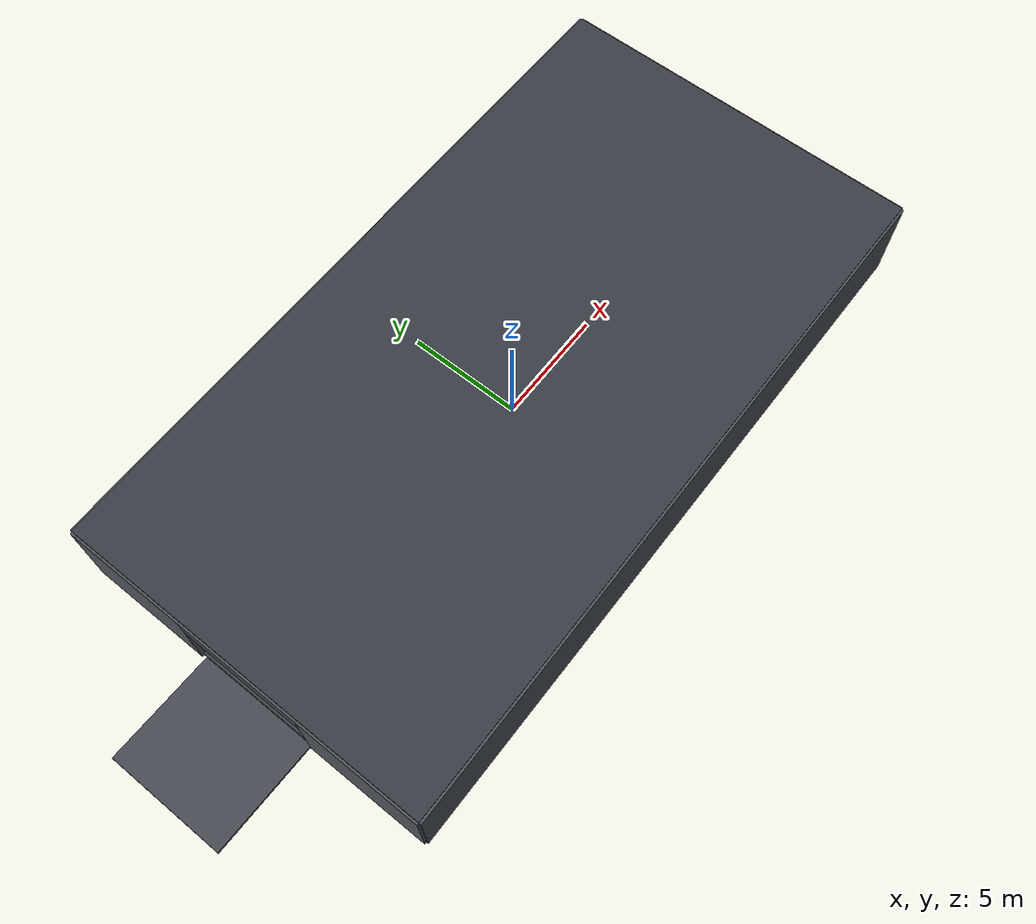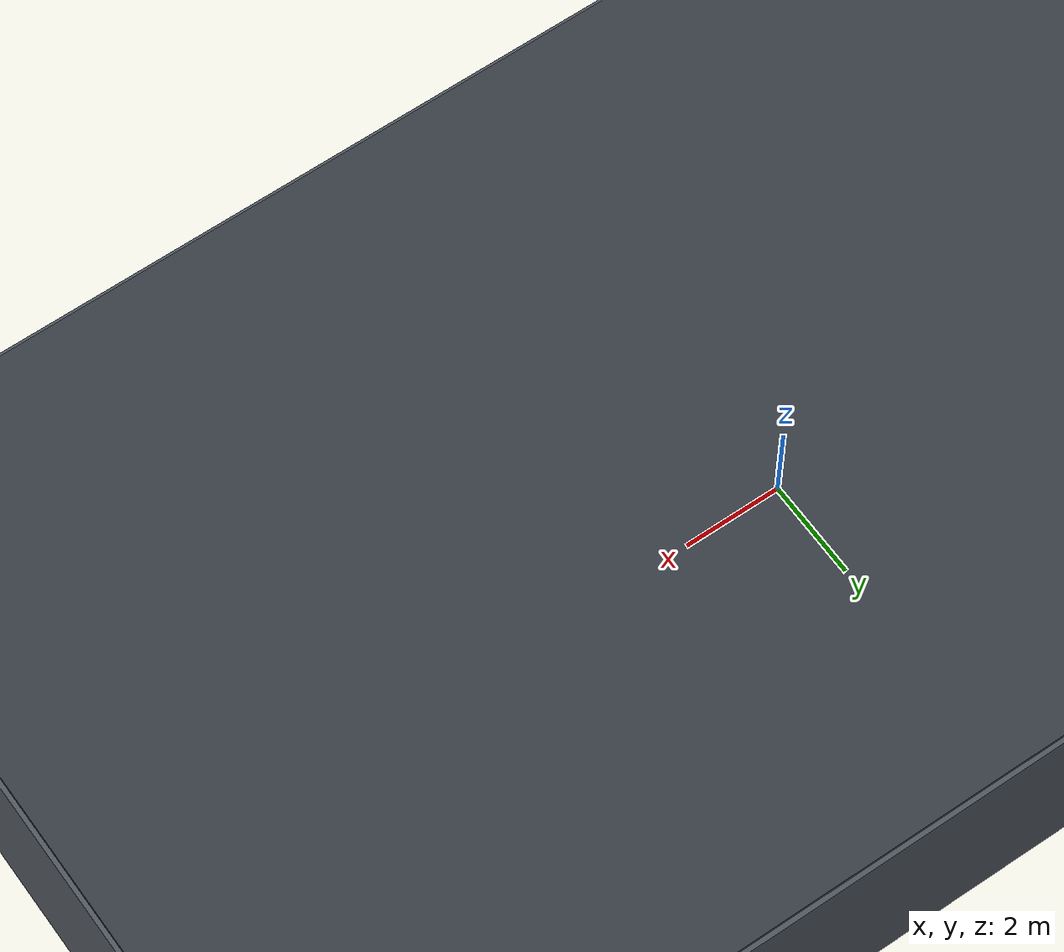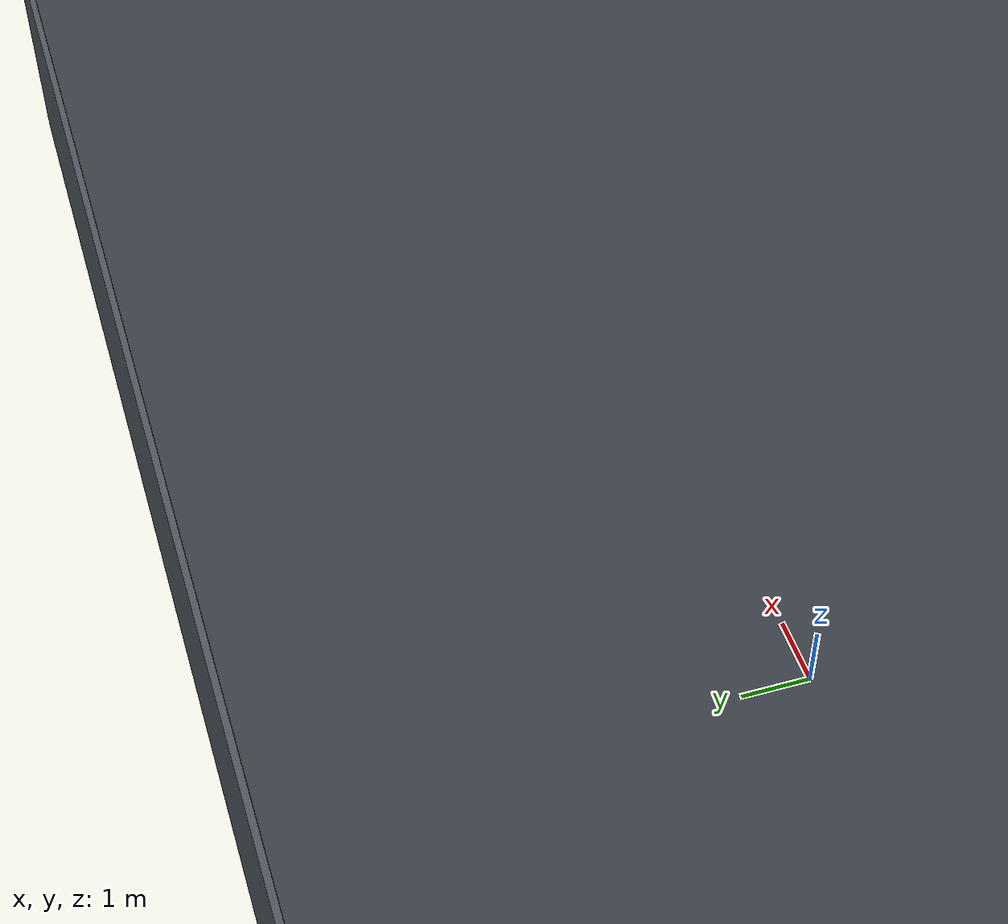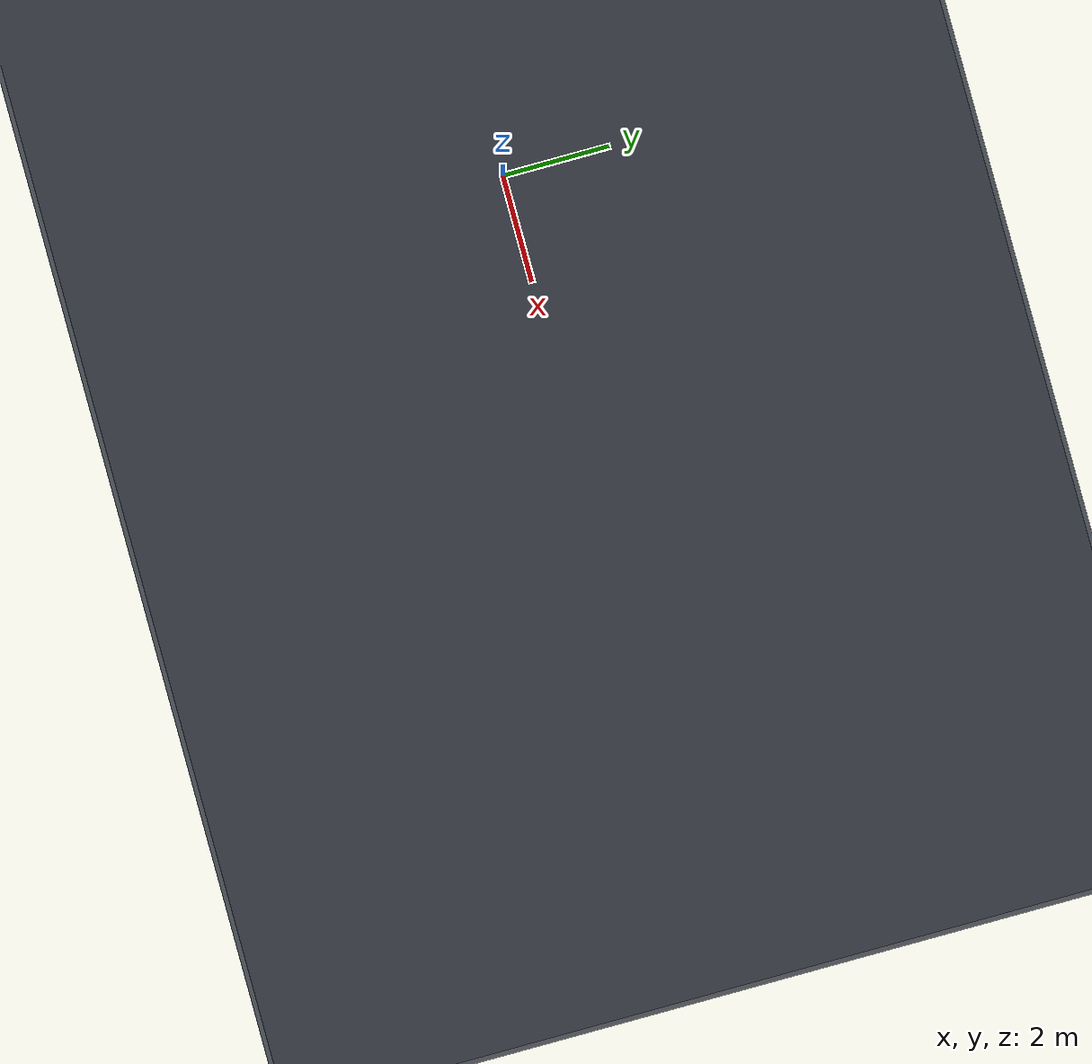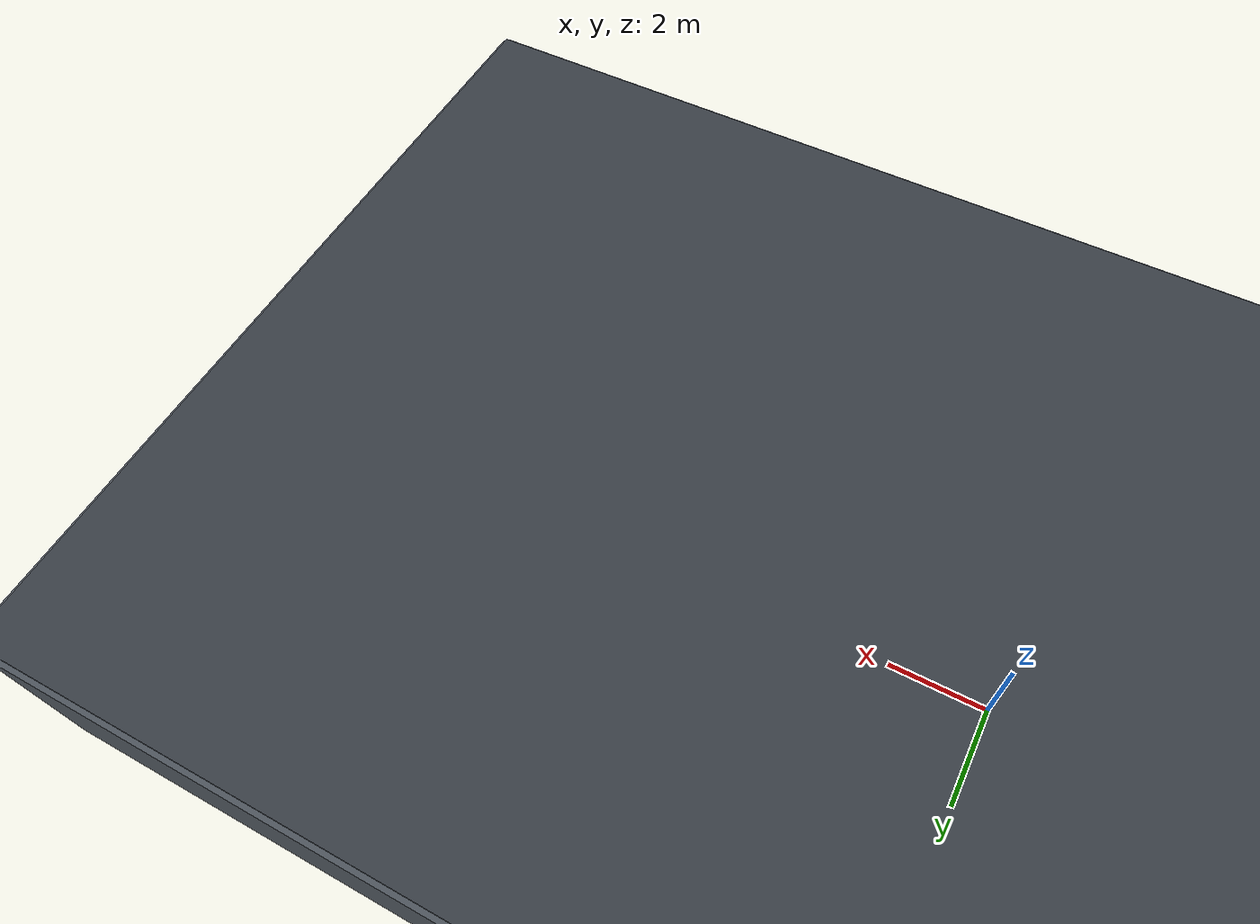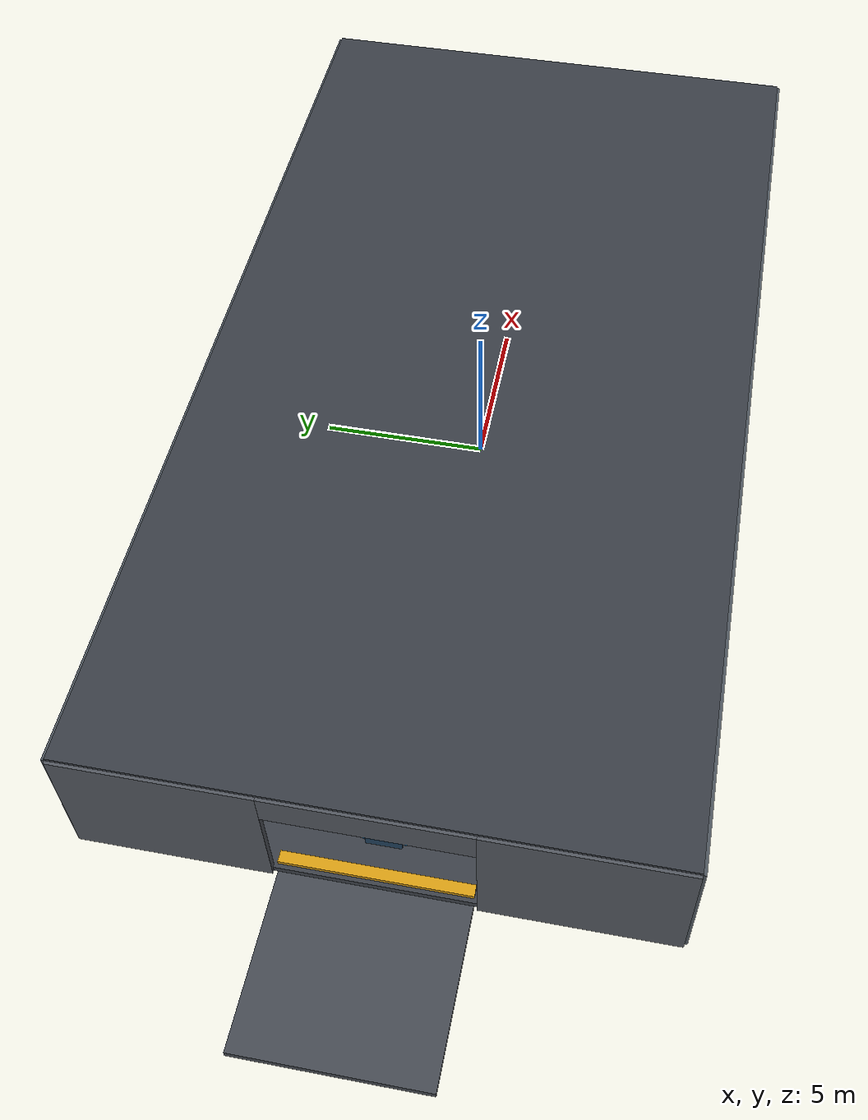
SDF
<?xml version="1.0"?>
<sdf version="1.7">
  <world name="ev_car_carrier_deck_world">
    <physics name="deck_physics" type="ode">
      <max_step_size>0.002</max_step_size>
      <real_time_update_rate>500</real_time_update_rate>
      <real_time_factor>1.0</real_time_factor>
    </physics>
    <plugin filename="gz-sim-physics-system" name="gz::sim::systems::Physics" />
    <plugin filename="gz-sim-user-commands-system" name="gz::sim::systems::UserCommands" />
    <plugin filename="gz-sim-scene-broadcaster-system" name="gz::sim::systems::SceneBroadcaster" />
    <plugin filename="gz-sim-sensors-system" name="gz::sim::systems::Sensors">
      <render_engine>ogre2</render_engine>
    </plugin>
    <plugin filename="gz-sim-imu-system" name="gz::sim::systems::Imu" />
    <scene>
      <ambient>0.35 0.38 0.42 1</ambient>
      <background>0.09 0.11 0.13 1</background>
      <shadows>true</shadows>
    </scene>
    <light name="weak_external_light" type="directional">
      <pose>0.0000 0.0000 15.0000 0.0000 0.0000 0.0000</pose>
      <cast_shadows>true</cast_shadows>
      <diffuse>0.35 0.38 0.42 1</diffuse>
      <specular>0.15 0.15 0.15 1</specular>
      <direction>-0.2 0.1 -1</direction>
    </light>
    <light name="ceiling_light_0_0" type="point">
      <pose>-12.0000 -5.5000 3.8500 0.0000 0.0000 0.0000</pose>
      <cast_shadows>false</cast_shadows>
      <diffuse>0.82 0.88 0.95 1</diffuse>
      <specular>0.15 0.15 0.15 1</specular>
      <attenuation>
        <range>9</range>
        <constant>0.7</constant>
        <linear>0.04</linear>
        <quadratic>0.01</quadratic>
      </attenuation>
    </light>
    <light name="ceiling_light_0_1" type="point">
      <pose>-12.0000 0.0000 3.8500 0.0000 0.0000 0.0000</pose>
      <cast_shadows>false</cast_shadows>
      <diffuse>0.82 0.88 0.95 1</diffuse>
      <specular>0.15 0.15 0.15 1</specular>
      <attenuation>
        <range>9</range>
        <constant>0.7</constant>
        <linear>0.04</linear>
        <quadratic>0.01</quadratic>
      </attenuation>
    </light>
    <light name="ceiling_light_0_2" type="point">
      <pose>-12.0000 5.5000 3.8500 0.0000 0.0000 0.0000</pose>
      <cast_shadows>false</cast_shadows>
      <diffuse>0.82 0.88 0.95 1</diffuse>
      <specular>0.15 0.15 0.15 1</specular>
      <attenuation>
        <range>9</range>
        <constant>0.7</constant>
        <linear>0.04</linear>
        <quadratic>0.01</quadratic>
      </attenuation>
    </light>
    <light name="ceiling_light_1_0" type="point">
      <pose>-8.0000 -5.5000 3.8500 0.0000 0.0000 0.0000</pose>
      <cast_shadows>false</cast_shadows>
      <diffuse>0.82 0.88 0.95 1</diffuse>
      <specular>0.15 0.15 0.15 1</specular>
      <attenuation>
        <range>9</range>
        <constant>0.7</constant>
        <linear>0.04</linear>
        <quadratic>0.01</quadratic>
      </attenuation>
    </light>
    <light name="ceiling_light_1_1" type="point">
      <pose>-8.0000 0.0000 3.8500 0.0000 0.0000 0.0000</pose>
      <cast_shadows>false</cast_shadows>
      <diffuse>0.82 0.88 0.95 1</diffuse>
      <specular>0.15 0.15 0.15 1</specular>
      <attenuation>
        <range>9</range>
        <constant>0.7</constant>
        <linear>0.04</linear>
        <quadratic>0.01</quadratic>
      </attenuation>
    </light>
    <light name="ceiling_light_1_2" type="point">
      <pose>-8.0000 5.5000 3.8500 0.0000 0.0000 0.0000</pose>
      <cast_shadows>false</cast_shadows>
      <diffuse>0.82 0.88 0.95 1</diffuse>
      <specular>0.15 0.15 0.15 1</specular>
      <attenuation>
        <range>9</range>
        <constant>0.7</constant>
        <linear>0.04</linear>
        <quadratic>0.01</quadratic>
      </attenuation>
    </light>
    <light name="ceiling_light_2_0" type="point">
      <pose>-4.0000 -5.5000 3.8500 0.0000 0.0000 0.0000</pose>
      <cast_shadows>false</cast_shadows>
      <diffuse>0.82 0.88 0.95 1</diffuse>
      <specular>0.15 0.15 0.15 1</specular>
      <attenuation>
        <range>9</range>
        <constant>0.7</constant>
        <linear>0.04</linear>
        <quadratic>0.01</quadratic>
      </attenuation>
    </light>
    <light name="ceiling_light_2_1" type="point">
      <pose>-4.0000 0.0000 3.8500 0.0000 0.0000 0.0000</pose>
      <cast_shadows>false</cast_shadows>
      <diffuse>0.82 0.88 0.95 1</diffuse>
      <specular>0.15 0.15 0.15 1</specular>
      <attenuation>
        <range>9</range>
        <constant>0.7</constant>
        <linear>0.04</linear>
        <quadratic>0.01</quadratic>
      </attenuation>
    </light>
    <light name="ceiling_light_2_2" type="point">
      <pose>-4.0000 5.5000 3.8500 0.0000 0.0000 0.0000</pose>
      <cast_shadows>false</cast_shadows>
      <diffuse>0.82 0.88 0.95 1</diffuse>
      <specular>0.15 0.15 0.15 1</specular>
      <attenuation>
        <range>9</range>
        <constant>0.7</constant>
        <linear>0.04</linear>
        <quadratic>0.01</quadratic>
      </attenuation>
    </light>
    <light name="ceiling_light_3_0" type="point">
      <pose>0.0000 -5.5000 3.8500 0.0000 0.0000 0.0000</pose>
      <cast_shadows>false</cast_shadows>
      <diffuse>0.82 0.88 0.95 1</diffuse>
      <specular>0.15 0.15 0.15 1</specular>
      <attenuation>
        <range>9</range>
        <constant>0.7</constant>
        <linear>0.04</linear>
        <quadratic>0.01</quadratic>
      </attenuation>
    </light>
    <light name="ceiling_light_3_1" type="point">
      <pose>0.0000 0.0000 3.8500 0.0000 0.0000 0.0000</pose>
      <cast_shadows>false</cast_shadows>
      <diffuse>0.82 0.88 0.95 1</diffuse>
      <specular>0.15 0.15 0.15 1</specular>
      <attenuation>
        <range>9</range>
        <constant>0.7</constant>
        <linear>0.04</linear>
        <quadratic>0.01</quadratic>
      </attenuation>
    </light>
    <light name="ceiling_light_3_2" type="point">
      <pose>0.0000 5.5000 3.8500 0.0000 0.0000 0.0000</pose>
      <cast_shadows>false</cast_shadows>
      <diffuse>0.82 0.88 0.95 1</diffuse>
      <specular>0.15 0.15 0.15 1</specular>
      <attenuation>
        <range>9</range>
        <constant>0.7</constant>
        <linear>0.04</linear>
        <quadratic>0.01</quadratic>
      </attenuation>
    </light>
    <light name="ceiling_light_4_0" type="point">
      <pose>4.0000 -5.5000 3.8500 0.0000 0.0000 0.0000</pose>
      <cast_shadows>false</cast_shadows>
      <diffuse>0.82 0.88 0.95 1</diffuse>
      <specular>0.15 0.15 0.15 1</specular>
      <attenuation>
        <range>9</range>
        <constant>0.7</constant>
        <linear>0.04</linear>
        <quadratic>0.01</quadratic>
      </attenuation>
    </light>
    <light name="ceiling_light_4_1" type="point">
      <pose>4.0000 0.0000 3.8500 0.0000 0.0000 0.0000</pose>
      <cast_shadows>false</cast_shadows>
      <diffuse>0.82 0.88 0.95 1</diffuse>
      <specular>0.15 0.15 0.15 1</specular>
      <attenuation>
        <range>9</range>
        <constant>0.7</constant>
        <linear>0.04</linear>
        <quadratic>0.01</quadratic>
      </attenuation>
    </light>
    <light name="ceiling_light_4_2" type="point">
      <pose>4.0000 5.5000 3.8500 0.0000 0.0000 0.0000</pose>
      <cast_shadows>false</cast_shadows>
      <diffuse>0.82 0.88 0.95 1</diffuse>
      <specular>0.15 0.15 0.15 1</specular>
      <attenuation>
        <range>9</range>
        <constant>0.7</constant>
        <linear>0.04</linear>
        <quadratic>0.01</quadratic>
      </attenuation>
    </light>
    <light name="ceiling_light_5_0" type="point">
      <pose>8.0000 -5.5000 3.8500 0.0000 0.0000 0.0000</pose>
      <cast_shadows>false</cast_shadows>
      <diffuse>0.82 0.88 0.95 1</diffuse>
      <specular>0.15 0.15 0.15 1</specular>
      <attenuation>
        <range>9</range>
        <constant>0.7</constant>
        <linear>0.04</linear>
        <quadratic>0.01</quadratic>
      </attenuation>
    </light>
    <light name="ceiling_light_5_1" type="point">
      <pose>8.0000 0.0000 3.8500 0.0000 0.0000 0.0000</pose>
      <cast_shadows>false</cast_shadows>
      <diffuse>0.82 0.88 0.95 1</diffuse>
      <specular>0.15 0.15 0.15 1</specular>
      <attenuation>
        <range>9</range>
        <constant>0.7</constant>
        <linear>0.04</linear>
        <quadratic>0.01</quadratic>
      </attenuation>
    </light>
    <light name="ceiling_light_5_2" type="point">
      <pose>8.0000 5.5000 3.8500 0.0000 0.0000 0.0000</pose>
      <cast_shadows>false</cast_shadows>
      <diffuse>0.82 0.88 0.95 1</diffuse>
      <specular>0.15 0.15 0.15 1</specular>
      <attenuation>
        <range>9</range>
        <constant>0.7</constant>
        <linear>0.04</linear>
        <quadratic>0.01</quadratic>
      </attenuation>
    </light>
    <light name="ceiling_light_6_0" type="point">
      <pose>12.0000 -5.5000 3.8500 0.0000 0.0000 0.0000</pose>
      <cast_shadows>false</cast_shadows>
      <diffuse>0.82 0.88 0.95 1</diffuse>
      <specular>0.15 0.15 0.15 1</specular>
      <attenuation>
        <range>9</range>
        <constant>0.7</constant>
        <linear>0.04</linear>
        <quadratic>0.01</quadratic>
      </attenuation>
    </light>
    <light name="ceiling_light_6_1" type="point">
      <pose>12.0000 0.0000 3.8500 0.0000 0.0000 0.0000</pose>
      <cast_shadows>false</cast_shadows>
      <diffuse>0.82 0.88 0.95 1</diffuse>
      <specular>0.15 0.15 0.15 1</specular>
      <attenuation>
        <range>9</range>
        <constant>0.7</constant>
        <linear>0.04</linear>
        <quadratic>0.01</quadratic>
      </attenuation>
    </light>
    <light name="ceiling_light_6_2" type="point">
      <pose>12.0000 5.5000 3.8500 0.0000 0.0000 0.0000</pose>
      <cast_shadows>false</cast_shadows>
      <diffuse>0.82 0.88 0.95 1</diffuse>
      <specular>0.15 0.15 0.15 1</specular>
      <attenuation>
        <range>9</range>
        <constant>0.7</constant>
        <linear>0.04</linear>
        <quadratic>0.01</quadratic>
      </attenuation>
    </light>
    <model name="vehicle_deck_structure">
      <static>true</static>
      <link name="link">
        <collision name="deck_floor_collision">
          <pose>0.0000 0.0000 0.1000 0.0000 0.0000 0.0000</pose>
          <geometry>
            <box>
              <size>30.0 16.0 0.2</size>
            </box>
          </geometry>
        </collision>
        <visual name="deck_floor_visual">
          <pose>0.0000 0.0000 0.1000 0.0000 0.0000 0.0000</pose>
          <geometry>
            <box>
              <size>30.0 16.0 0.2</size>
            </box>
          </geometry>
          <material>
            <ambient>0.23 0.25 0.28 1</ambient>
            <diffuse>0.23 0.25 0.28 1</diffuse>
          </material>
        </visual>
        <collision name="ceiling_collision">
          <pose>0.0000 0.0000 4.2000 0.0000 0.0000 0.0000</pose>
          <geometry>
            <box>
              <size>30.0 16.0 0.16</size>
            </box>
          </geometry>
        </collision>
        <visual name="ceiling_visual">
          <pose>0.0000 0.0000 4.2000 0.0000 0.0000 0.0000</pose>
          <geometry>
            <box>
              <size>30.0 16.0 0.16</size>
            </box>
          </geometry>
          <material>
            <ambient>0.22 0.24 0.27 1</ambient>
            <diffuse>0.22 0.24 0.27 1</diffuse>
          </material>
        </visual>
        <collision name="port_wall_collision">
          <pose>0.0000 8.0000 2.1000 0.0000 0.0000 0.0000</pose>
          <geometry>
            <box>
              <size>30.0 0.18 4.2</size>
            </box>
          </geometry>
        </collision>
        <visual name="port_wall_visual">
          <pose>0.0000 8.0000 2.1000 0.0000 0.0000 0.0000</pose>
          <geometry>
            <box>
              <size>30.0 0.18 4.2</size>
            </box>
          </geometry>
          <material>
            <ambient>0.3 0.33 0.36 1</ambient>
            <diffuse>0.3 0.33 0.36 1</diffuse>
          </material>
        </visual>
        <collision name="starboard_wall_collision">
          <pose>0.0000 -8.0000 2.1000 0.0000 0.0000 0.0000</pose>
          <geometry>
            <box>
              <size>30.0 0.18 4.2</size>
            </box>
          </geometry>
        </collision>
        <visual name="starboard_wall_visual">
          <pose>0.0000 -8.0000 2.1000 0.0000 0.0000 0.0000</pose>
          <geometry>
            <box>
              <size>30.0 0.18 4.2</size>
            </box>
          </geometry>
          <material>
            <ambient>0.3 0.33 0.36 1</ambient>
            <diffuse>0.3 0.33 0.36 1</diffuse>
          </material>
        </visual>
        <collision name="forward_bulkhead_collision">
          <pose>15.0000 0.0000 2.1000 0.0000 0.0000 0.0000</pose>
          <geometry>
            <box>
              <size>0.18 16.0 4.2</size>
            </box>
          </geometry>
        </collision>
        <visual name="forward_bulkhead_visual">
          <pose>15.0000 0.0000 2.1000 0.0000 0.0000 0.0000</pose>
          <geometry>
            <box>
              <size>0.18 16.0 4.2</size>
            </box>
          </geometry>
          <material>
            <ambient>0.32 0.34 0.37 1</ambient>
            <diffuse>0.32 0.34 0.37 1</diffuse>
          </material>
        </visual>
        <collision name="aft_bulkhead_left_collision">
          <pose>-15.0000 5.3500 2.1000 0.0000 0.0000 0.0000</pose>
          <geometry>
            <box>
              <size>0.18 5.3 4.2</size>
            </box>
          </geometry>
        </collision>
        <visual name="aft_bulkhead_left_visual">
          <pose>-15.0000 5.3500 2.1000 0.0000 0.0000 0.0000</pose>
          <geometry>
            <box>
              <size>0.18 5.3 4.2</size>
            </box>
          </geometry>
          <material>
            <ambient>0.32 0.34 0.37 1</ambient>
            <diffuse>0.32 0.34 0.37 1</diffuse>
          </material>
        </visual>
        <collision name="aft_bulkhead_right_collision">
          <pose>-15.0000 -5.3500 2.1000 0.0000 0.0000 0.0000</pose>
          <geometry>
            <box>
              <size>0.18 5.3 4.2</size>
            </box>
          </geometry>
        </collision>
        <visual name="aft_bulkhead_right_visual">
          <pose>-15.0000 -5.3500 2.1000 0.0000 0.0000 0.0000</pose>
          <geometry>
            <box>
              <size>0.18 5.3 4.2</size>
            </box>
          </geometry>
          <material>
            <ambient>0.32 0.34 0.37 1</ambient>
            <diffuse>0.32 0.34 0.37 1</diffuse>
          </material>
        </visual>
        <collision name="aft_bulkhead_top_collision">
          <pose>-15.0000 0.0000 3.7000 0.0000 0.0000 0.0000</pose>
          <geometry>
            <box>
              <size>0.18 5.4 1.0</size>
            </box>
          </geometry>
        </collision>
        <visual name="aft_bulkhead_top_visual">
          <pose>-15.0000 0.0000 3.7000 0.0000 0.0000 0.0000</pose>
          <geometry>
            <box>
              <size>0.18 5.4 1.0</size>
            </box>
          </geometry>
          <material>
            <ambient>0.32 0.34 0.37 1</ambient>
            <diffuse>0.32 0.34 0.37 1</diffuse>
          </material>
        </visual>
        <collision name="aft_ramp_collision">
          <pose>-17.2500 0.0000 -0.0200 0.0000 0.0600 0.0000</pose>
          <geometry>
            <box>
              <size>5.0 5.2 0.18</size>
            </box>
          </geometry>
        </collision>
        <visual name="aft_ramp_visual">
          <pose>-17.2500 0.0000 -0.0200 0.0000 0.0600 0.0000</pose>
          <geometry>
            <box>
              <size>5.0 5.2 0.18</size>
            </box>
          </geometry>
          <material>
            <ambient>0.27 0.29 0.32 1</ambient>
            <diffuse>0.27 0.29 0.32 1</diffuse>
          </material>
        </visual>
        <collision name="door_threshold_collision">
          <pose>-14.7200 0.0000 0.2600 0.0000 0.0000 0.0000</pose>
          <geometry>
            <box>
              <size>0.32 5.2 0.12</size>
            </box>
          </geometry>
        </collision>
        <visual name="door_threshold_visual">
          <pose>-14.7200 0.0000 0.2600 0.0000 0.0000 0.0000</pose>
          <geometry>
            <box>
              <size>0.32 5.2 0.12</size>
            </box>
          </geometry>
          <material>
            <ambient>0.85 0.62 0.08 1</ambient>
            <diffuse>0.85 0.62 0.08 1</diffuse>
          </material>
        </visual>
        <collision name="column_-12_-7.15_collision">
          <pose>-12.0000 -7.1500 2.1000 0.0000 0.0000 0.0000</pose>
          <geometry>
            <box>
              <size>0.28 0.28 4.0</size>
            </box>
          </geometry>
        </collision>
        <visual name="column_-12_-7.15_visual">
          <pose>-12.0000 -7.1500 2.1000 0.0000 0.0000 0.0000</pose>
          <geometry>
            <box>
              <size>0.28 0.28 4.0</size>
            </box>
          </geometry>
          <material>
            <ambient>0.42 0.45 0.48 1</ambient>
            <diffuse>0.42 0.45 0.48 1</diffuse>
          </material>
        </visual>
        <collision name="column_-12_-0.95_collision">
          <pose>-12.0000 -0.9500 2.1000 0.0000 0.0000 0.0000</pose>
          <geometry>
            <box>
              <size>0.28 0.28 4.0</size>
            </box>
          </geometry>
        </collision>
        <visual name="column_-12_-0.95_visual">
          <pose>-12.0000 -0.9500 2.1000 0.0000 0.0000 0.0000</pose>
          <geometry>
            <box>
              <size>0.28 0.28 4.0</size>
            </box>
          </geometry>
          <material>
            <ambient>0.42 0.45 0.48 1</ambient>
            <diffuse>0.42 0.45 0.48 1</diffuse>
          </material>
        </visual>
        <collision name="column_-12_0.95_collision">
          <pose>-12.0000 0.9500 2.1000 0.0000 0.0000 0.0000</pose>
          <geometry>
            <box>
              <size>0.28 0.28 4.0</size>
            </box>
          </geometry>
        </collision>
        <visual name="column_-12_0.95_visual">
          <pose>-12.0000 0.9500 2.1000 0.0000 0.0000 0.0000</pose>
          <geometry>
            <box>
              <size>0.28 0.28 4.0</size>
            </box>
          </geometry>
          <material>
            <ambient>0.42 0.45 0.48 1</ambient>
            <diffuse>0.42 0.45 0.48 1</diffuse>
          </material>
        </visual>
        <collision name="column_-12_7.15_collision">
          <pose>-12.0000 7.1500 2.1000 0.0000 0.0000 0.0000</pose>
          <geometry>
            <box>
              <size>0.28 0.28 4.0</size>
            </box>
          </geometry>
        </collision>
        <visual name="column_-12_7.15_visual">
          <pose>-12.0000 7.1500 2.1000 0.0000 0.0000 0.0000</pose>
          <geometry>
            <box>
              <size>0.28 0.28 4.0</size>
            </box>
          </geometry>
          <material>
            <ambient>0.42 0.45 0.48 1</ambient>
            <diffuse>0.42 0.45 0.48 1</diffuse>
          </material>
        </visual>
        <collision name="cross_beam_-12_collision">
          <pose>-12.0000 0.0000 3.9200 0.0000 0.0000 0.0000</pose>
          <geometry>
            <box>
              <size>0.32 15.5 0.3</size>
            </box>
          </geometry>
        </collision>
        <visual name="cross_beam_-12_visual">
          <pose>-12.0000 0.0000 3.9200 0.0000 0.0000 0.0000</pose>
          <geometry>
            <box>
              <size>0.32 15.5 0.3</size>
            </box>
          </geometry>
          <material>
            <ambient>0.4 0.43 0.46 1</ambient>
            <diffuse>0.4 0.43 0.46 1</diffuse>
          </material>
        </visual>
        <collision name="column_-8_-7.15_collision">
          <pose>-8.0000 -7.1500 2.1000 0.0000 0.0000 0.0000</pose>
          <geometry>
            <box>
              <size>0.28 0.28 4.0</size>
            </box>
          </geometry>
        </collision>
        <visual name="column_-8_-7.15_visual">
          <pose>-8.0000 -7.1500 2.1000 0.0000 0.0000 0.0000</pose>
          <geometry>
            <box>
              <size>0.28 0.28 4.0</size>
            </box>
          </geometry>
          <material>
            <ambient>0.42 0.45 0.48 1</ambient>
            <diffuse>0.42 0.45 0.48 1</diffuse>
          </material>
        </visual>
        <collision name="column_-8_-0.95_collision">
          <pose>-8.0000 -0.9500 2.1000 0.0000 0.0000 0.0000</pose>
          <geometry>
            <box>
              <size>0.28 0.28 4.0</size>
            </box>
          </geometry>
        </collision>
        <visual name="column_-8_-0.95_visual">
          <pose>-8.0000 -0.9500 2.1000 0.0000 0.0000 0.0000</pose>
          <geometry>
            <box>
              <size>0.28 0.28 4.0</size>
            </box>
          </geometry>
          <material>
            <ambient>0.42 0.45 0.48 1</ambient>
            <diffuse>0.42 0.45 0.48 1</diffuse>
          </material>
        </visual>
        <collision name="column_-8_0.95_collision">
          <pose>-8.0000 0.9500 2.1000 0.0000 0.0000 0.0000</pose>
          <geometry>
            <box>
              <size>0.28 0.28 4.0</size>
            </box>
          </geometry>
        </collision>
        <visual name="column_-8_0.95_visual">
          <pose>-8.0000 0.9500 2.1000 0.0000 0.0000 0.0000</pose>
          <geometry>
            <box>
              <size>0.28 0.28 4.0</size>
            </box>
          </geometry>
          <material>
            <ambient>0.42 0.45 0.48 1</ambient>
            <diffuse>0.42 0.45 0.48 1</diffuse>
          </material>
        </visual>
        <collision name="column_-8_7.15_collision">
          <pose>-8.0000 7.1500 2.1000 0.0000 0.0000 0.0000</pose>
          <geometry>
            <box>
              <size>0.28 0.28 4.0</size>
            </box>
          </geometry>
        </collision>
        <visual name="column_-8_7.15_visual">
          <pose>-8.0000 7.1500 2.1000 0.0000 0.0000 0.0000</pose>
          <geometry>
            <box>
              <size>0.28 0.28 4.0</size>
            </box>
          </geometry>
          <material>
            <ambient>0.42 0.45 0.48 1</ambient>
            <diffuse>0.42 0.45 0.48 1</diffuse>
          </material>
        </visual>
        <collision name="cross_beam_-8_collision">
          <pose>-8.0000 0.0000 3.9200 0.0000 0.0000 0.0000</pose>
          <geometry>
            <box>
              <size>0.32 15.5 0.3</size>
            </box>
          </geometry>
        </collision>
        <visual name="cross_beam_-8_visual">
          <pose>-8.0000 0.0000 3.9200 0.0000 0.0000 0.0000</pose>
          <geometry>
            <box>
              <size>0.32 15.5 0.3</size>
            </box>
          </geometry>
          <material>
            <ambient>0.4 0.43 0.46 1</ambient>
            <diffuse>0.4 0.43 0.46 1</diffuse>
          </material>
        </visual>
        <collision name="column_-4_-7.15_collision">
          <pose>-4.0000 -7.1500 2.1000 0.0000 0.0000 0.0000</pose>
          <geometry>
            <box>
              <size>0.28 0.28 4.0</size>
            </box>
          </geometry>
        </collision>
        <visual name="column_-4_-7.15_visual">
          <pose>-4.0000 -7.1500 2.1000 0.0000 0.0000 0.0000</pose>
          <geometry>
            <box>
              <size>0.28 0.28 4.0</size>
            </box>
          </geometry>
          <material>
            <ambient>0.42 0.45 0.48 1</ambient>
            <diffuse>0.42 0.45 0.48 1</diffuse>
          </material>
        </visual>
        <collision name="column_-4_-0.95_collision">
          <pose>-4.0000 -0.9500 2.1000 0.0000 0.0000 0.0000</pose>
          <geometry>
            <box>
              <size>0.28 0.28 4.0</size>
            </box>
          </geometry>
        </collision>
        <visual name="column_-4_-0.95_visual">
          <pose>-4.0000 -0.9500 2.1000 0.0000 0.0000 0.0000</pose>
          <geometry>
            <box>
              <size>0.28 0.28 4.0</size>
            </box>
          </geometry>
          <material>
            <ambient>0.42 0.45 0.48 1</ambient>
            <diffuse>0.42 0.45 0.48 1</diffuse>
          </material>
        </visual>
        <collision name="column_-4_0.95_collision">
          <pose>-4.0000 0.9500 2.1000 0.0000 0.0000 0.0000</pose>
          <geometry>
            <box>
              <size>0.28 0.28 4.0</size>
            </box>
          </geometry>
        </collision>
        <visual name="column_-4_0.95_visual">
          <pose>-4.0000 0.9500 2.1000 0.0000 0.0000 0.0000</pose>
          <geometry>
            <box>
              <size>0.28 0.28 4.0</size>
            </box>
          </geometry>
          <material>
            <ambient>0.42 0.45 0.48 1</ambient>
            <diffuse>0.42 0.45 0.48 1</diffuse>
          </material>
        </visual>
        <collision name="column_-4_7.15_collision">
          <pose>-4.0000 7.1500 2.1000 0.0000 0.0000 0.0000</pose>
          <geometry>
            <box>
              <size>0.28 0.28 4.0</size>
            </box>
          </geometry>
        </collision>
        <visual name="column_-4_7.15_visual">
          <pose>-4.0000 7.1500 2.1000 0.0000 0.0000 0.0000</pose>
          <geometry>
            <box>
              <size>0.28 0.28 4.0</size>
            </box>
          </geometry>
          <material>
            <ambient>0.42 0.45 0.48 1</ambient>
            <diffuse>0.42 0.45 0.48 1</diffuse>
          </material>
        </visual>
        <collision name="cross_beam_-4_collision">
          <pose>-4.0000 0.0000 3.9200 0.0000 0.0000 0.0000</pose>
          <geometry>
            <box>
              <size>0.32 15.5 0.3</size>
            </box>
          </geometry>
        </collision>
        <visual name="cross_beam_-4_visual">
          <pose>-4.0000 0.0000 3.9200 0.0000 0.0000 0.0000</pose>
          <geometry>
            <box>
              <size>0.32 15.5 0.3</size>
            </box>
          </geometry>
          <material>
            <ambient>0.4 0.43 0.46 1</ambient>
            <diffuse>0.4 0.43 0.46 1</diffuse>
          </material>
        </visual>
        <collision name="column_0_-7.15_collision">
          <pose>0.0000 -7.1500 2.1000 0.0000 0.0000 0.0000</pose>
          <geometry>
            <box>
              <size>0.28 0.28 4.0</size>
            </box>
          </geometry>
        </collision>
        <visual name="column_0_-7.15_visual">
          <pose>0.0000 -7.1500 2.1000 0.0000 0.0000 0.0000</pose>
          <geometry>
            <box>
              <size>0.28 0.28 4.0</size>
            </box>
          </geometry>
          <material>
            <ambient>0.42 0.45 0.48 1</ambient>
            <diffuse>0.42 0.45 0.48 1</diffuse>
          </material>
        </visual>
        <collision name="column_0_-0.95_collision">
          <pose>0.0000 -0.9500 2.1000 0.0000 0.0000 0.0000</pose>
          <geometry>
            <box>
              <size>0.28 0.28 4.0</size>
            </box>
          </geometry>
        </collision>
        <visual name="column_0_-0.95_visual">
          <pose>0.0000 -0.9500 2.1000 0.0000 0.0000 0.0000</pose>
          <geometry>
            <box>
              <size>0.28 0.28 4.0</size>
            </box>
          </geometry>
          <material>
            <ambient>0.42 0.45 0.48 1</ambient>
            <diffuse>0.42 0.45 0.48 1</diffuse>
          </material>
        </visual>
        <collision name="column_0_0.95_collision">
          <pose>0.0000 0.9500 2.1000 0.0000 0.0000 0.0000</pose>
          <geometry>
            <box>
              <size>0.28 0.28 4.0</size>
            </box>
          </geometry>
        </collision>
        <visual name="column_0_0.95_visual">
          <pose>0.0000 0.9500 2.1000 0.0000 0.0000 0.0000</pose>
          <geometry>
            <box>
              <size>0.28 0.28 4.0</size>
            </box>
          </geometry>
          <material>
            <ambient>0.42 0.45 0.48 1</ambient>
            <diffuse>0.42 0.45 0.48 1</diffuse>
          </material>
        </visual>
        <collision name="column_0_7.15_collision">
          <pose>0.0000 7.1500 2.1000 0.0000 0.0000 0.0000</pose>
          <geometry>
            <box>
              <size>0.28 0.28 4.0</size>
            </box>
          </geometry>
        </collision>
        <visual name="column_0_7.15_visual">
          <pose>0.0000 7.1500 2.1000 0.0000 0.0000 0.0000</pose>
          <geometry>
            <box>
              <size>0.28 0.28 4.0</size>
            </box>
          </geometry>
          <material>
            <ambient>0.42 0.45 0.48 1</ambient>
            <diffuse>0.42 0.45 0.48 1</diffuse>
          </material>
        </visual>
        <collision name="cross_beam_0_collision">
          <pose>0.0000 0.0000 3.9200 0.0000 0.0000 0.0000</pose>
          <geometry>
            <box>
              <size>0.32 15.5 0.3</size>
            </box>
          </geometry>
        </collision>
        <visual name="cross_beam_0_visual">
          <pose>0.0000 0.0000 3.9200 0.0000 0.0000 0.0000</pose>
          <geometry>
            <box>
              <size>0.32 15.5 0.3</size>
            </box>
          </geometry>
          <material>
            <ambient>0.4 0.43 0.46 1</ambient>
            <diffuse>0.4 0.43 0.46 1</diffuse>
          </material>
        </visual>
        <collision name="column_4_-7.15_collision">
          <pose>4.0000 -7.1500 2.1000 0.0000 0.0000 0.0000</pose>
          <geometry>
            <box>
              <size>0.28 0.28 4.0</size>
            </box>
          </geometry>
        </collision>
        <visual name="column_4_-7.15_visual">
          <pose>4.0000 -7.1500 2.1000 0.0000 0.0000 0.0000</pose>
          <geometry>
            <box>
              <size>0.28 0.28 4.0</size>
            </box>
          </geometry>
          <material>
            <ambient>0.42 0.45 0.48 1</ambient>
            <diffuse>0.42 0.45 0.48 1</diffuse>
          </material>
        </visual>
        <collision name="column_4_-0.95_collision">
          <pose>4.0000 -0.9500 2.1000 0.0000 0.0000 0.0000</pose>
          <geometry>
            <box>
              <size>0.28 0.28 4.0</size>
            </box>
          </geometry>
        </collision>
        <visual name="column_4_-0.95_visual">
          <pose>4.0000 -0.9500 2.1000 0.0000 0.0000 0.0000</pose>
          <geometry>
            <box>
              <size>0.28 0.28 4.0</size>
            </box>
          </geometry>
          <material>
            <ambient>0.42 0.45 0.48 1</ambient>
            <diffuse>0.42 0.45 0.48 1</diffuse>
          </material>
        </visual>
        <collision name="column_4_0.95_collision">
          <pose>4.0000 0.9500 2.1000 0.0000 0.0000 0.0000</pose>
          <geometry>
            <box>
              <size>0.28 0.28 4.0</size>
            </box>
          </geometry>
        </collision>
        <visual name="column_4_0.95_visual">
          <pose>4.0000 0.9500 2.1000 0.0000 0.0000 0.0000</pose>
          <geometry>
            <box>
              <size>0.28 0.28 4.0</size>
            </box>
          </geometry>
          <material>
            <ambient>0.42 0.45 0.48 1</ambient>
            <diffuse>0.42 0.45 0.48 1</diffuse>
          </material>
        </visual>
        <collision name="column_4_7.15_collision">
          <pose>4.0000 7.1500 2.1000 0.0000 0.0000 0.0000</pose>
          <geometry>
            <box>
              <size>0.28 0.28 4.0</size>
            </box>
          </geometry>
        </collision>
        <visual name="column_4_7.15_visual">
          <pose>4.0000 7.1500 2.1000 0.0000 0.0000 0.0000</pose>
          <geometry>
            <box>
              <size>0.28 0.28 4.0</size>
            </box>
          </geometry>
          <material>
            <ambient>0.42 0.45 0.48 1</ambient>
            <diffuse>0.42 0.45 0.48 1</diffuse>
          </material>
        </visual>
        <collision name="cross_beam_4_collision">
          <pose>4.0000 0.0000 3.9200 0.0000 0.0000 0.0000</pose>
          <geometry>
            <box>
              <size>0.32 15.5 0.3</size>
            </box>
          </geometry>
        </collision>
        <visual name="cross_beam_4_visual">
          <pose>4.0000 0.0000 3.9200 0.0000 0.0000 0.0000</pose>
          <geometry>
            <box>
              <size>0.32 15.5 0.3</size>
            </box>
          </geometry>
          <material>
            <ambient>0.4 0.43 0.46 1</ambient>
            <diffuse>0.4 0.43 0.46 1</diffuse>
          </material>
        </visual>
        <collision name="column_8_-7.15_collision">
          <pose>8.0000 -7.1500 2.1000 0.0000 0.0000 0.0000</pose>
          <geometry>
            <box>
              <size>0.28 0.28 4.0</size>
            </box>
          </geometry>
        </collision>
        <visual name="column_8_-7.15_visual">
          <pose>8.0000 -7.1500 2.1000 0.0000 0.0000 0.0000</pose>
          <geometry>
            <box>
              <size>0.28 0.28 4.0</size>
            </box>
          </geometry>
          <material>
            <ambient>0.42 0.45 0.48 1</ambient>
            <diffuse>0.42 0.45 0.48 1</diffuse>
          </material>
        </visual>
        <collision name="column_8_-0.95_collision">
          <pose>8.0000 -0.9500 2.1000 0.0000 0.0000 0.0000</pose>
          <geometry>
            <box>
              <size>0.28 0.28 4.0</size>
            </box>
          </geometry>
        </collision>
        <visual name="column_8_-0.95_visual">
          <pose>8.0000 -0.9500 2.1000 0.0000 0.0000 0.0000</pose>
          <geometry>
            <box>
              <size>0.28 0.28 4.0</size>
            </box>
          </geometry>
          <material>
            <ambient>0.42 0.45 0.48 1</ambient>
            <diffuse>0.42 0.45 0.48 1</diffuse>
          </material>
        </visual>
        <collision name="column_8_0.95_collision">
          <pose>8.0000 0.9500 2.1000 0.0000 0.0000 0.0000</pose>
          <geometry>
            <box>
              <size>0.28 0.28 4.0</size>
            </box>
          </geometry>
        </collision>
        <visual name="column_8_0.95_visual">
          <pose>8.0000 0.9500 2.1000 0.0000 0.0000 0.0000</pose>
          <geometry>
            <box>
              <size>0.28 0.28 4.0</size>
            </box>
          </geometry>
          <material>
            <ambient>0.42 0.45 0.48 1</ambient>
            <diffuse>0.42 0.45 0.48 1</diffuse>
          </material>
        </visual>
        <collision name="column_8_7.15_collision">
          <pose>8.0000 7.1500 2.1000 0.0000 0.0000 0.0000</pose>
          <geometry>
            <box>
              <size>0.28 0.28 4.0</size>
            </box>
          </geometry>
        </collision>
        <visual name="column_8_7.15_visual">
          <pose>8.0000 7.1500 2.1000 0.0000 0.0000 0.0000</pose>
          <geometry>
            <box>
              <size>0.28 0.28 4.0</size>
            </box>
          </geometry>
          <material>
            <ambient>0.42 0.45 0.48 1</ambient>
            <diffuse>0.42 0.45 0.48 1</diffuse>
          </material>
        </visual>
        <collision name="cross_beam_8_collision">
          <pose>8.0000 0.0000 3.9200 0.0000 0.0000 0.0000</pose>
          <geometry>
            <box>
              <size>0.32 15.5 0.3</size>
            </box>
          </geometry>
        </collision>
        <visual name="cross_beam_8_visual">
          <pose>8.0000 0.0000 3.9200 0.0000 0.0000 0.0000</pose>
          <geometry>
            <box>
              <size>0.32 15.5 0.3</size>
            </box>
          </geometry>
          <material>
            <ambient>0.4 0.43 0.46 1</ambient>
            <diffuse>0.4 0.43 0.46 1</diffuse>
          </material>
        </visual>
        <collision name="column_12_-7.15_collision">
          <pose>12.0000 -7.1500 2.1000 0.0000 0.0000 0.0000</pose>
          <geometry>
            <box>
              <size>0.28 0.28 4.0</size>
            </box>
          </geometry>
        </collision>
        <visual name="column_12_-7.15_visual">
          <pose>12.0000 -7.1500 2.1000 0.0000 0.0000 0.0000</pose>
          <geometry>
            <box>
              <size>0.28 0.28 4.0</size>
            </box>
          </geometry>
          <material>
            <ambient>0.42 0.45 0.48 1</ambient>
            <diffuse>0.42 0.45 0.48 1</diffuse>
          </material>
        </visual>
        <collision name="column_12_-0.95_collision">
          <pose>12.0000 -0.9500 2.1000 0.0000 0.0000 0.0000</pose>
          <geometry>
            <box>
              <size>0.28 0.28 4.0</size>
            </box>
          </geometry>
        </collision>
        <visual name="column_12_-0.95_visual">
          <pose>12.0000 -0.9500 2.1000 0.0000 0.0000 0.0000</pose>
          <geometry>
            <box>
              <size>0.28 0.28 4.0</size>
            </box>
          </geometry>
          <material>
            <ambient>0.42 0.45 0.48 1</ambient>
            <diffuse>0.42 0.45 0.48 1</diffuse>
          </material>
        </visual>
        <collision name="column_12_0.95_collision">
          <pose>12.0000 0.9500 2.1000 0.0000 0.0000 0.0000</pose>
          <geometry>
            <box>
              <size>0.28 0.28 4.0</size>
            </box>
          </geometry>
        </collision>
        <visual name="column_12_0.95_visual">
          <pose>12.0000 0.9500 2.1000 0.0000 0.0000 0.0000</pose>
          <geometry>
            <box>
              <size>0.28 0.28 4.0</size>
            </box>
          </geometry>
          <material>
            <ambient>0.42 0.45 0.48 1</ambient>
            <diffuse>0.42 0.45 0.48 1</diffuse>
          </material>
        </visual>
        <collision name="column_12_7.15_collision">
          <pose>12.0000 7.1500 2.1000 0.0000 0.0000 0.0000</pose>
          <geometry>
            <box>
              <size>0.28 0.28 4.0</size>
            </box>
          </geometry>
        </collision>
        <visual name="column_12_7.15_visual">
          <pose>12.0000 7.1500 2.1000 0.0000 0.0000 0.0000</pose>
          <geometry>
            <box>
              <size>0.28 0.28 4.0</size>
            </box>
          </geometry>
          <material>
            <ambient>0.42 0.45 0.48 1</ambient>
            <diffuse>0.42 0.45 0.48 1</diffuse>
          </material>
        </visual>
        <collision name="cross_beam_12_collision">
          <pose>12.0000 0.0000 3.9200 0.0000 0.0000 0.0000</pose>
          <geometry>
            <box>
              <size>0.32 15.5 0.3</size>
            </box>
          </geometry>
        </collision>
        <visual name="cross_beam_12_visual">
          <pose>12.0000 0.0000 3.9200 0.0000 0.0000 0.0000</pose>
          <geometry>
            <box>
              <size>0.32 15.5 0.3</size>
            </box>
          </geometry>
          <material>
            <ambient>0.4 0.43 0.46 1</ambient>
            <diffuse>0.4 0.43 0.46 1</diffuse>
          </material>
        </visual>
        <collision name="long_beam_-7.15_collision">
          <pose>0.0000 -7.1500 3.9200 0.0000 0.0000 0.0000</pose>
          <geometry>
            <box>
              <size>29.5 0.24 0.28</size>
            </box>
          </geometry>
        </collision>
        <visual name="long_beam_-7.15_visual">
          <pose>0.0000 -7.1500 3.9200 0.0000 0.0000 0.0000</pose>
          <geometry>
            <box>
              <size>29.5 0.24 0.28</size>
            </box>
          </geometry>
          <material>
            <ambient>0.39 0.42 0.45 1</ambient>
            <diffuse>0.39 0.42 0.45 1</diffuse>
          </material>
        </visual>
        <collision name="long_beam_-3.7_collision">
          <pose>0.0000 -3.7000 3.9200 0.0000 0.0000 0.0000</pose>
          <geometry>
            <box>
              <size>29.5 0.24 0.28</size>
            </box>
          </geometry>
        </collision>
        <visual name="long_beam_-3.7_visual">
          <pose>0.0000 -3.7000 3.9200 0.0000 0.0000 0.0000</pose>
          <geometry>
            <box>
              <size>29.5 0.24 0.28</size>
            </box>
          </geometry>
          <material>
            <ambient>0.39 0.42 0.45 1</ambient>
            <diffuse>0.39 0.42 0.45 1</diffuse>
          </material>
        </visual>
        <collision name="long_beam_0_collision">
          <pose>0.0000 0.0000 3.9200 0.0000 0.0000 0.0000</pose>
          <geometry>
            <box>
              <size>29.5 0.24 0.28</size>
            </box>
          </geometry>
        </collision>
        <visual name="long_beam_0_visual">
          <pose>0.0000 0.0000 3.9200 0.0000 0.0000 0.0000</pose>
          <geometry>
            <box>
              <size>29.5 0.24 0.28</size>
            </box>
          </geometry>
          <material>
            <ambient>0.39 0.42 0.45 1</ambient>
            <diffuse>0.39 0.42 0.45 1</diffuse>
          </material>
        </visual>
        <collision name="long_beam_3.7_collision">
          <pose>0.0000 3.7000 3.9200 0.0000 0.0000 0.0000</pose>
          <geometry>
            <box>
              <size>29.5 0.24 0.28</size>
            </box>
          </geometry>
        </collision>
        <visual name="long_beam_3.7_visual">
          <pose>0.0000 3.7000 3.9200 0.0000 0.0000 0.0000</pose>
          <geometry>
            <box>
              <size>29.5 0.24 0.28</size>
            </box>
          </geometry>
          <material>
            <ambient>0.39 0.42 0.45 1</ambient>
            <diffuse>0.39 0.42 0.45 1</diffuse>
          </material>
        </visual>
        <collision name="long_beam_7.15_collision">
          <pose>0.0000 7.1500 3.9200 0.0000 0.0000 0.0000</pose>
          <geometry>
            <box>
              <size>29.5 0.24 0.28</size>
            </box>
          </geometry>
        </collision>
        <visual name="long_beam_7.15_visual">
          <pose>0.0000 7.1500 3.9200 0.0000 0.0000 0.0000</pose>
          <geometry>
            <box>
              <size>29.5 0.24 0.28</size>
            </box>
          </geometry>
          <material>
            <ambient>0.39 0.42 0.45 1</ambient>
            <diffuse>0.39 0.42 0.45 1</diffuse>
          </material>
        </visual>
      </link>
    </model>
    <model name="deck_markings">
      <static>true</static>
      <link name="link">
        <visual name="lane_line_-6.4_visual">
          <pose>0.0000 -6.4000 0.2080 0.0000 0.0000 0.0000</pose>
          <geometry>
            <box>
              <size>27.5 0.06 0.012</size>
            </box>
          </geometry>
          <material>
            <ambient>0.92 0.82 0.15 1</ambient>
            <diffuse>0.92 0.82 0.15 1</diffuse>
          </material>
        </visual>
        <visual name="lane_line_-4.4_visual">
          <pose>0.0000 -4.4000 0.2080 0.0000 0.0000 0.0000</pose>
          <geometry>
            <box>
              <size>27.5 0.06 0.012</size>
            </box>
          </geometry>
          <material>
            <ambient>0.92 0.82 0.15 1</ambient>
            <diffuse>0.92 0.82 0.15 1</diffuse>
          </material>
        </visual>
        <visual name="lane_line_-3.2_visual">
          <pose>0.0000 -3.2000 0.2080 0.0000 0.0000 0.0000</pose>
          <geometry>
            <box>
              <size>27.5 0.06 0.012</size>
            </box>
          </geometry>
          <material>
            <ambient>0.92 0.82 0.15 1</ambient>
            <diffuse>0.92 0.82 0.15 1</diffuse>
          </material>
        </visual>
        <visual name="lane_line_-1.2_visual">
          <pose>0.0000 -1.2000 0.2080 0.0000 0.0000 0.0000</pose>
          <geometry>
            <box>
              <size>27.5 0.06 0.012</size>
            </box>
          </geometry>
          <material>
            <ambient>0.92 0.82 0.15 1</ambient>
            <diffuse>0.92 0.82 0.15 1</diffuse>
          </material>
        </visual>
        <visual name="lane_line_1.2_visual">
          <pose>0.0000 1.2000 0.2080 0.0000 0.0000 0.0000</pose>
          <geometry>
            <box>
              <size>27.5 0.06 0.012</size>
            </box>
          </geometry>
          <material>
            <ambient>0.92 0.82 0.15 1</ambient>
            <diffuse>0.92 0.82 0.15 1</diffuse>
          </material>
        </visual>
        <visual name="lane_line_3.2_visual">
          <pose>0.0000 3.2000 0.2080 0.0000 0.0000 0.0000</pose>
          <geometry>
            <box>
              <size>27.5 0.06 0.012</size>
            </box>
          </geometry>
          <material>
            <ambient>0.92 0.82 0.15 1</ambient>
            <diffuse>0.92 0.82 0.15 1</diffuse>
          </material>
        </visual>
        <visual name="lane_line_4.4_visual">
          <pose>0.0000 4.4000 0.2080 0.0000 0.0000 0.0000</pose>
          <geometry>
            <box>
              <size>27.5 0.06 0.012</size>
            </box>
          </geometry>
          <material>
            <ambient>0.92 0.82 0.15 1</ambient>
            <diffuse>0.92 0.82 0.15 1</diffuse>
          </material>
        </visual>
        <visual name="lane_line_6.4_visual">
          <pose>0.0000 6.4000 0.2080 0.0000 0.0000 0.0000</pose>
          <geometry>
            <box>
              <size>27.5 0.06 0.012</size>
            </box>
          </geometry>
          <material>
            <ambient>0.92 0.82 0.15 1</ambient>
            <diffuse>0.92 0.82 0.15 1</diffuse>
          </material>
        </visual>
        <visual name="bay_end_-12.5_-5.4_visual">
          <pose>-12.5000 -5.4000 0.2080 0.0000 0.0000 0.0000</pose>
          <geometry>
            <box>
              <size>0.06 1.9 0.012</size>
            </box>
          </geometry>
          <material>
            <ambient>0.92 0.82 0.15 1</ambient>
            <diffuse>0.92 0.82 0.15 1</diffuse>
          </material>
        </visual>
        <visual name="bay_end_-12.5_-2.2_visual">
          <pose>-12.5000 -2.2000 0.2080 0.0000 0.0000 0.0000</pose>
          <geometry>
            <box>
              <size>0.06 1.9 0.012</size>
            </box>
          </geometry>
          <material>
            <ambient>0.92 0.82 0.15 1</ambient>
            <diffuse>0.92 0.82 0.15 1</diffuse>
          </material>
        </visual>
        <visual name="bay_end_-12.5_2.2_visual">
          <pose>-12.5000 2.2000 0.2080 0.0000 0.0000 0.0000</pose>
          <geometry>
            <box>
              <size>0.06 1.9 0.012</size>
            </box>
          </geometry>
          <material>
            <ambient>0.92 0.82 0.15 1</ambient>
            <diffuse>0.92 0.82 0.15 1</diffuse>
          </material>
        </visual>
        <visual name="bay_end_-12.5_5.4_visual">
          <pose>-12.5000 5.4000 0.2080 0.0000 0.0000 0.0000</pose>
          <geometry>
            <box>
              <size>0.06 1.9 0.012</size>
            </box>
          </geometry>
          <material>
            <ambient>0.92 0.82 0.15 1</ambient>
            <diffuse>0.92 0.82 0.15 1</diffuse>
          </material>
        </visual>
        <visual name="bay_end_-7.5_-5.4_visual">
          <pose>-7.5000 -5.4000 0.2080 0.0000 0.0000 0.0000</pose>
          <geometry>
            <box>
              <size>0.06 1.9 0.012</size>
            </box>
          </geometry>
          <material>
            <ambient>0.92 0.82 0.15 1</ambient>
            <diffuse>0.92 0.82 0.15 1</diffuse>
          </material>
        </visual>
        <visual name="bay_end_-7.5_-2.2_visual">
          <pose>-7.5000 -2.2000 0.2080 0.0000 0.0000 0.0000</pose>
          <geometry>
            <box>
              <size>0.06 1.9 0.012</size>
            </box>
          </geometry>
          <material>
            <ambient>0.92 0.82 0.15 1</ambient>
            <diffuse>0.92 0.82 0.15 1</diffuse>
          </material>
        </visual>
        <visual name="bay_end_-7.5_2.2_visual">
          <pose>-7.5000 2.2000 0.2080 0.0000 0.0000 0.0000</pose>
          <geometry>
            <box>
              <size>0.06 1.9 0.012</size>
            </box>
          </geometry>
          <material>
            <ambient>0.92 0.82 0.15 1</ambient>
            <diffuse>0.92 0.82 0.15 1</diffuse>
          </material>
        </visual>
        <visual name="bay_end_-7.5_5.4_visual">
          <pose>-7.5000 5.4000 0.2080 0.0000 0.0000 0.0000</pose>
          <geometry>
            <box>
              <size>0.06 1.9 0.012</size>
            </box>
          </geometry>
          <material>
            <ambient>0.92 0.82 0.15 1</ambient>
            <diffuse>0.92 0.82 0.15 1</diffuse>
          </material>
        </visual>
        <visual name="bay_end_-2.5_-5.4_visual">
          <pose>-2.5000 -5.4000 0.2080 0.0000 0.0000 0.0000</pose>
          <geometry>
            <box>
              <size>0.06 1.9 0.012</size>
            </box>
          </geometry>
          <material>
            <ambient>0.92 0.82 0.15 1</ambient>
            <diffuse>0.92 0.82 0.15 1</diffuse>
          </material>
        </visual>
        <visual name="bay_end_-2.5_-2.2_visual">
          <pose>-2.5000 -2.2000 0.2080 0.0000 0.0000 0.0000</pose>
          <geometry>
            <box>
              <size>0.06 1.9 0.012</size>
            </box>
          </geometry>
          <material>
            <ambient>0.92 0.82 0.15 1</ambient>
            <diffuse>0.92 0.82 0.15 1</diffuse>
          </material>
        </visual>
        <visual name="bay_end_-2.5_2.2_visual">
          <pose>-2.5000 2.2000 0.2080 0.0000 0.0000 0.0000</pose>
          <geometry>
            <box>
              <size>0.06 1.9 0.012</size>
            </box>
          </geometry>
          <material>
            <ambient>0.92 0.82 0.15 1</ambient>
            <diffuse>0.92 0.82 0.15 1</diffuse>
          </material>
        </visual>
        <visual name="bay_end_-2.5_5.4_visual">
          <pose>-2.5000 5.4000 0.2080 0.0000 0.0000 0.0000</pose>
          <geometry>
            <box>
              <size>0.06 1.9 0.012</size>
            </box>
          </geometry>
          <material>
            <ambient>0.92 0.82 0.15 1</ambient>
            <diffuse>0.92 0.82 0.15 1</diffuse>
          </material>
        </visual>
        <visual name="bay_end_2.5_-5.4_visual">
          <pose>2.5000 -5.4000 0.2080 0.0000 0.0000 0.0000</pose>
          <geometry>
            <box>
              <size>0.06 1.9 0.012</size>
            </box>
          </geometry>
          <material>
            <ambient>0.92 0.82 0.15 1</ambient>
            <diffuse>0.92 0.82 0.15 1</diffuse>
          </material>
        </visual>
        <visual name="bay_end_2.5_-2.2_visual">
          <pose>2.5000 -2.2000 0.2080 0.0000 0.0000 0.0000</pose>
          <geometry>
            <box>
              <size>0.06 1.9 0.012</size>
            </box>
          </geometry>
          <material>
            <ambient>0.92 0.82 0.15 1</ambient>
            <diffuse>0.92 0.82 0.15 1</diffuse>
          </material>
        </visual>
        <visual name="bay_end_2.5_2.2_visual">
          <pose>2.5000 2.2000 0.2080 0.0000 0.0000 0.0000</pose>
          <geometry>
            <box>
              <size>0.06 1.9 0.012</size>
            </box>
          </geometry>
          <material>
            <ambient>0.92 0.82 0.15 1</ambient>
            <diffuse>0.92 0.82 0.15 1</diffuse>
          </material>
        </visual>
        <visual name="bay_end_2.5_5.4_visual">
          <pose>2.5000 5.4000 0.2080 0.0000 0.0000 0.0000</pose>
          <geometry>
            <box>
              <size>0.06 1.9 0.012</size>
            </box>
          </geometry>
          <material>
            <ambient>0.92 0.82 0.15 1</ambient>
            <diffuse>0.92 0.82 0.15 1</diffuse>
          </material>
        </visual>
        <visual name="bay_end_7.5_-5.4_visual">
          <pose>7.5000 -5.4000 0.2080 0.0000 0.0000 0.0000</pose>
          <geometry>
            <box>
              <size>0.06 1.9 0.012</size>
            </box>
          </geometry>
          <material>
            <ambient>0.92 0.82 0.15 1</ambient>
            <diffuse>0.92 0.82 0.15 1</diffuse>
          </material>
        </visual>
        <visual name="bay_end_7.5_-2.2_visual">
          <pose>7.5000 -2.2000 0.2080 0.0000 0.0000 0.0000</pose>
          <geometry>
            <box>
              <size>0.06 1.9 0.012</size>
            </box>
          </geometry>
          <material>
            <ambient>0.92 0.82 0.15 1</ambient>
            <diffuse>0.92 0.82 0.15 1</diffuse>
          </material>
        </visual>
        <visual name="bay_end_7.5_2.2_visual">
          <pose>7.5000 2.2000 0.2080 0.0000 0.0000 0.0000</pose>
          <geometry>
            <box>
              <size>0.06 1.9 0.012</size>
            </box>
          </geometry>
          <material>
            <ambient>0.92 0.82 0.15 1</ambient>
            <diffuse>0.92 0.82 0.15 1</diffuse>
          </material>
        </visual>
        <visual name="bay_end_7.5_5.4_visual">
          <pose>7.5000 5.4000 0.2080 0.0000 0.0000 0.0000</pose>
          <geometry>
            <box>
              <size>0.06 1.9 0.012</size>
            </box>
          </geometry>
          <material>
            <ambient>0.92 0.82 0.15 1</ambient>
            <diffuse>0.92 0.82 0.15 1</diffuse>
          </material>
        </visual>
        <visual name="bay_end_12.5_-5.4_visual">
          <pose>12.5000 -5.4000 0.2080 0.0000 0.0000 0.0000</pose>
          <geometry>
            <box>
              <size>0.06 1.9 0.012</size>
            </box>
          </geometry>
          <material>
            <ambient>0.92 0.82 0.15 1</ambient>
            <diffuse>0.92 0.82 0.15 1</diffuse>
          </material>
        </visual>
        <visual name="bay_end_12.5_-2.2_visual">
          <pose>12.5000 -2.2000 0.2080 0.0000 0.0000 0.0000</pose>
          <geometry>
            <box>
              <size>0.06 1.9 0.012</size>
            </box>
          </geometry>
          <material>
            <ambient>0.92 0.82 0.15 1</ambient>
            <diffuse>0.92 0.82 0.15 1</diffuse>
          </material>
        </visual>
        <visual name="bay_end_12.5_2.2_visual">
          <pose>12.5000 2.2000 0.2080 0.0000 0.0000 0.0000</pose>
          <geometry>
            <box>
              <size>0.06 1.9 0.012</size>
            </box>
          </geometry>
          <material>
            <ambient>0.92 0.82 0.15 1</ambient>
            <diffuse>0.92 0.82 0.15 1</diffuse>
          </material>
        </visual>
        <visual name="bay_end_12.5_5.4_visual">
          <pose>12.5000 5.4000 0.2080 0.0000 0.0000 0.0000</pose>
          <geometry>
            <box>
              <size>0.06 1.9 0.012</size>
            </box>
          </geometry>
          <material>
            <ambient>0.92 0.82 0.15 1</ambient>
            <diffuse>0.92 0.82 0.15 1</diffuse>
          </material>
        </visual>
        <visual name="robot_lane_left_visual">
          <pose>0.0000 -0.8200 0.2100 0.0000 0.0000 0.0000</pose>
          <geometry>
            <box>
              <size>27.5 0.08 0.012</size>
            </box>
          </geometry>
          <material>
            <ambient>0.08 0.72 0.82 1</ambient>
            <diffuse>0.08 0.72 0.82 1</diffuse>
          </material>
        </visual>
        <visual name="robot_lane_right_visual">
          <pose>0.0000 0.8200 0.2100 0.0000 0.0000 0.0000</pose>
          <geometry>
            <box>
              <size>27.5 0.08 0.012</size>
            </box>
          </geometry>
          <material>
            <ambient>0.08 0.72 0.82 1</ambient>
            <diffuse>0.08 0.72 0.82 1</diffuse>
          </material>
        </visual>
        <visual name="robot_lane_dash_-12_visual">
          <pose>-12.0000 0.0000 0.2120 0.0000 0.0000 0.0000</pose>
          <geometry>
            <box>
              <size>1.3 0.06 0.012</size>
            </box>
          </geometry>
          <material>
            <ambient>0.08 0.72 0.82 1</ambient>
            <diffuse>0.08 0.72 0.82 1</diffuse>
          </material>
        </visual>
        <visual name="robot_lane_dash_-9_visual">
          <pose>-9.0000 0.0000 0.2120 0.0000 0.0000 0.0000</pose>
          <geometry>
            <box>
              <size>1.3 0.06 0.012</size>
            </box>
          </geometry>
          <material>
            <ambient>0.08 0.72 0.82 1</ambient>
            <diffuse>0.08 0.72 0.82 1</diffuse>
          </material>
        </visual>
        <visual name="robot_lane_dash_-6_visual">
          <pose>-6.0000 0.0000 0.2120 0.0000 0.0000 0.0000</pose>
          <geometry>
            <box>
              <size>1.3 0.06 0.012</size>
            </box>
          </geometry>
          <material>
            <ambient>0.08 0.72 0.82 1</ambient>
            <diffuse>0.08 0.72 0.82 1</diffuse>
          </material>
        </visual>
        <visual name="robot_lane_dash_-3_visual">
          <pose>-3.0000 0.0000 0.2120 0.0000 0.0000 0.0000</pose>
          <geometry>
            <box>
              <size>1.3 0.06 0.012</size>
            </box>
          </geometry>
          <material>
            <ambient>0.08 0.72 0.82 1</ambient>
            <diffuse>0.08 0.72 0.82 1</diffuse>
          </material>
        </visual>
        <visual name="robot_lane_dash_0_visual">
          <pose>0.0000 0.0000 0.2120 0.0000 0.0000 0.0000</pose>
          <geometry>
            <box>
              <size>1.3 0.06 0.012</size>
            </box>
          </geometry>
          <material>
            <ambient>0.08 0.72 0.82 1</ambient>
            <diffuse>0.08 0.72 0.82 1</diffuse>
          </material>
        </visual>
        <visual name="robot_lane_dash_3_visual">
          <pose>3.0000 0.0000 0.2120 0.0000 0.0000 0.0000</pose>
          <geometry>
            <box>
              <size>1.3 0.06 0.012</size>
            </box>
          </geometry>
          <material>
            <ambient>0.08 0.72 0.82 1</ambient>
            <diffuse>0.08 0.72 0.82 1</diffuse>
          </material>
        </visual>
        <visual name="robot_lane_dash_6_visual">
          <pose>6.0000 0.0000 0.2120 0.0000 0.0000 0.0000</pose>
          <geometry>
            <box>
              <size>1.3 0.06 0.012</size>
            </box>
          </geometry>
          <material>
            <ambient>0.08 0.72 0.82 1</ambient>
            <diffuse>0.08 0.72 0.82 1</diffuse>
          </material>
        </visual>
        <visual name="robot_lane_dash_9_visual">
          <pose>9.0000 0.0000 0.2120 0.0000 0.0000 0.0000</pose>
          <geometry>
            <box>
              <size>1.3 0.06 0.012</size>
            </box>
          </geometry>
          <material>
            <ambient>0.08 0.72 0.82 1</ambient>
            <diffuse>0.08 0.72 0.82 1</diffuse>
          </material>
        </visual>
        <visual name="robot_lane_dash_12_visual">
          <pose>12.0000 0.0000 0.2120 0.0000 0.0000 0.0000</pose>
          <geometry>
            <box>
              <size>1.3 0.06 0.012</size>
            </box>
          </geometry>
          <material>
            <ambient>0.08 0.72 0.82 1</ambient>
            <diffuse>0.08 0.72 0.82 1</diffuse>
          </material>
        </visual>
      </link>
    </model>
    <model name="deck_drainage">
      <static>true</static>
      <link name="link">
        <collision name="gutter_-7.45_collision">
          <pose>0.0000 -7.4500 0.2250 0.0000 0.0000 0.0000</pose>
          <geometry>
            <box>
              <size>28.5 0.34 0.05</size>
            </box>
          </geometry>
        </collision>
        <visual name="gutter_-7.45_visual">
          <pose>0.0000 -7.4500 0.2250 0.0000 0.0000 0.0000</pose>
          <geometry>
            <box>
              <size>28.5 0.34 0.05</size>
            </box>
          </geometry>
          <material>
            <ambient>0.11 0.13 0.15 1</ambient>
            <diffuse>0.11 0.13 0.15 1</diffuse>
          </material>
        </visual>
        <visual name="grate_-7.45_-13_visual">
          <pose>-13.0000 -7.4500 0.2580 0.0000 0.0000 0.0000</pose>
          <geometry>
            <box>
              <size>0.03 0.3 0.018</size>
            </box>
          </geometry>
          <material>
            <ambient>0.34 0.37 0.4 1</ambient>
            <diffuse>0.34 0.37 0.4 1</diffuse>
          </material>
        </visual>
        <visual name="grate_-7.45_-12_visual">
          <pose>-12.0000 -7.4500 0.2580 0.0000 0.0000 0.0000</pose>
          <geometry>
            <box>
              <size>0.03 0.3 0.018</size>
            </box>
          </geometry>
          <material>
            <ambient>0.34 0.37 0.4 1</ambient>
            <diffuse>0.34 0.37 0.4 1</diffuse>
          </material>
        </visual>
        <visual name="grate_-7.45_-11_visual">
          <pose>-11.0000 -7.4500 0.2580 0.0000 0.0000 0.0000</pose>
          <geometry>
            <box>
              <size>0.03 0.3 0.018</size>
            </box>
          </geometry>
          <material>
            <ambient>0.34 0.37 0.4 1</ambient>
            <diffuse>0.34 0.37 0.4 1</diffuse>
          </material>
        </visual>
        <visual name="grate_-7.45_-10_visual">
          <pose>-10.0000 -7.4500 0.2580 0.0000 0.0000 0.0000</pose>
          <geometry>
            <box>
              <size>0.03 0.3 0.018</size>
            </box>
          </geometry>
          <material>
            <ambient>0.34 0.37 0.4 1</ambient>
            <diffuse>0.34 0.37 0.4 1</diffuse>
          </material>
        </visual>
        <visual name="grate_-7.45_-9_visual">
          <pose>-9.0000 -7.4500 0.2580 0.0000 0.0000 0.0000</pose>
          <geometry>
            <box>
              <size>0.03 0.3 0.018</size>
            </box>
          </geometry>
          <material>
            <ambient>0.34 0.37 0.4 1</ambient>
            <diffuse>0.34 0.37 0.4 1</diffuse>
          </material>
        </visual>
        <visual name="grate_-7.45_-8_visual">
          <pose>-8.0000 -7.4500 0.2580 0.0000 0.0000 0.0000</pose>
          <geometry>
            <box>
              <size>0.03 0.3 0.018</size>
            </box>
          </geometry>
          <material>
            <ambient>0.34 0.37 0.4 1</ambient>
            <diffuse>0.34 0.37 0.4 1</diffuse>
          </material>
        </visual>
        <visual name="grate_-7.45_-7_visual">
          <pose>-7.0000 -7.4500 0.2580 0.0000 0.0000 0.0000</pose>
          <geometry>
            <box>
              <size>0.03 0.3 0.018</size>
            </box>
          </geometry>
          <material>
            <ambient>0.34 0.37 0.4 1</ambient>
            <diffuse>0.34 0.37 0.4 1</diffuse>
          </material>
        </visual>
        <visual name="grate_-7.45_-6_visual">
          <pose>-6.0000 -7.4500 0.2580 0.0000 0.0000 0.0000</pose>
          <geometry>
            <box>
              <size>0.03 0.3 0.018</size>
            </box>
          </geometry>
          <material>
            <ambient>0.34 0.37 0.4 1</ambient>
            <diffuse>0.34 0.37 0.4 1</diffuse>
          </material>
        </visual>
        <visual name="grate_-7.45_-5_visual">
          <pose>-5.0000 -7.4500 0.2580 0.0000 0.0000 0.0000</pose>
          <geometry>
            <box>
              <size>0.03 0.3 0.018</size>
            </box>
          </geometry>
          <material>
            <ambient>0.34 0.37 0.4 1</ambient>
            <diffuse>0.34 0.37 0.4 1</diffuse>
          </material>
        </visual>
        <visual name="grate_-7.45_-4_visual">
          <pose>-4.0000 -7.4500 0.2580 0.0000 0.0000 0.0000</pose>
          <geometry>
            <box>
              <size>0.03 0.3 0.018</size>
            </box>
          </geometry>
          <material>
            <ambient>0.34 0.37 0.4 1</ambient>
            <diffuse>0.34 0.37 0.4 1</diffuse>
          </material>
        </visual>
        <visual name="grate_-7.45_-3_visual">
          <pose>-3.0000 -7.4500 0.2580 0.0000 0.0000 0.0000</pose>
          <geometry>
            <box>
              <size>0.03 0.3 0.018</size>
            </box>
          </geometry>
          <material>
            <ambient>0.34 0.37 0.4 1</ambient>
            <diffuse>0.34 0.37 0.4 1</diffuse>
          </material>
        </visual>
        <visual name="grate_-7.45_-2_visual">
          <pose>-2.0000 -7.4500 0.2580 0.0000 0.0000 0.0000</pose>
          <geometry>
            <box>
              <size>0.03 0.3 0.018</size>
            </box>
          </geometry>
          <material>
            <ambient>0.34 0.37 0.4 1</ambient>
            <diffuse>0.34 0.37 0.4 1</diffuse>
          </material>
        </visual>
        <visual name="grate_-7.45_-1_visual">
          <pose>-1.0000 -7.4500 0.2580 0.0000 0.0000 0.0000</pose>
          <geometry>
            <box>
              <size>0.03 0.3 0.018</size>
            </box>
          </geometry>
          <material>
            <ambient>0.34 0.37 0.4 1</ambient>
            <diffuse>0.34 0.37 0.4 1</diffuse>
          </material>
        </visual>
        <visual name="grate_-7.45_0_visual">
          <pose>0.0000 -7.4500 0.2580 0.0000 0.0000 0.0000</pose>
          <geometry>
            <box>
              <size>0.03 0.3 0.018</size>
            </box>
          </geometry>
          <material>
            <ambient>0.34 0.37 0.4 1</ambient>
            <diffuse>0.34 0.37 0.4 1</diffuse>
          </material>
        </visual>
        <visual name="grate_-7.45_1_visual">
          <pose>1.0000 -7.4500 0.2580 0.0000 0.0000 0.0000</pose>
          <geometry>
            <box>
              <size>0.03 0.3 0.018</size>
            </box>
          </geometry>
          <material>
            <ambient>0.34 0.37 0.4 1</ambient>
            <diffuse>0.34 0.37 0.4 1</diffuse>
          </material>
        </visual>
        <visual name="grate_-7.45_2_visual">
          <pose>2.0000 -7.4500 0.2580 0.0000 0.0000 0.0000</pose>
          <geometry>
            <box>
              <size>0.03 0.3 0.018</size>
            </box>
          </geometry>
          <material>
            <ambient>0.34 0.37 0.4 1</ambient>
            <diffuse>0.34 0.37 0.4 1</diffuse>
          </material>
        </visual>
        <visual name="grate_-7.45_3_visual">
          <pose>3.0000 -7.4500 0.2580 0.0000 0.0000 0.0000</pose>
          <geometry>
            <box>
              <size>0.03 0.3 0.018</size>
            </box>
          </geometry>
          <material>
            <ambient>0.34 0.37 0.4 1</ambient>
            <diffuse>0.34 0.37 0.4 1</diffuse>
          </material>
        </visual>
        <visual name="grate_-7.45_4_visual">
          <pose>4.0000 -7.4500 0.2580 0.0000 0.0000 0.0000</pose>
          <geometry>
            <box>
              <size>0.03 0.3 0.018</size>
            </box>
          </geometry>
          <material>
            <ambient>0.34 0.37 0.4 1</ambient>
            <diffuse>0.34 0.37 0.4 1</diffuse>
          </material>
        </visual>
        <visual name="grate_-7.45_5_visual">
          <pose>5.0000 -7.4500 0.2580 0.0000 0.0000 0.0000</pose>
          <geometry>
            <box>
              <size>0.03 0.3 0.018</size>
            </box>
          </geometry>
          <material>
            <ambient>0.34 0.37 0.4 1</ambient>
            <diffuse>0.34 0.37 0.4 1</diffuse>
          </material>
        </visual>
        <visual name="grate_-7.45_6_visual">
          <pose>6.0000 -7.4500 0.2580 0.0000 0.0000 0.0000</pose>
          <geometry>
            <box>
              <size>0.03 0.3 0.018</size>
            </box>
          </geometry>
          <material>
            <ambient>0.34 0.37 0.4 1</ambient>
            <diffuse>0.34 0.37 0.4 1</diffuse>
          </material>
        </visual>
        <visual name="grate_-7.45_7_visual">
          <pose>7.0000 -7.4500 0.2580 0.0000 0.0000 0.0000</pose>
          <geometry>
            <box>
              <size>0.03 0.3 0.018</size>
            </box>
          </geometry>
          <material>
            <ambient>0.34 0.37 0.4 1</ambient>
            <diffuse>0.34 0.37 0.4 1</diffuse>
          </material>
        </visual>
        <visual name="grate_-7.45_8_visual">
          <pose>8.0000 -7.4500 0.2580 0.0000 0.0000 0.0000</pose>
          <geometry>
            <box>
              <size>0.03 0.3 0.018</size>
            </box>
          </geometry>
          <material>
            <ambient>0.34 0.37 0.4 1</ambient>
            <diffuse>0.34 0.37 0.4 1</diffuse>
          </material>
        </visual>
        <visual name="grate_-7.45_9_visual">
          <pose>9.0000 -7.4500 0.2580 0.0000 0.0000 0.0000</pose>
          <geometry>
            <box>
              <size>0.03 0.3 0.018</size>
            </box>
          </geometry>
          <material>
            <ambient>0.34 0.37 0.4 1</ambient>
            <diffuse>0.34 0.37 0.4 1</diffuse>
          </material>
        </visual>
        <visual name="grate_-7.45_10_visual">
          <pose>10.0000 -7.4500 0.2580 0.0000 0.0000 0.0000</pose>
          <geometry>
            <box>
              <size>0.03 0.3 0.018</size>
            </box>
          </geometry>
          <material>
            <ambient>0.34 0.37 0.4 1</ambient>
            <diffuse>0.34 0.37 0.4 1</diffuse>
          </material>
        </visual>
        <visual name="grate_-7.45_11_visual">
          <pose>11.0000 -7.4500 0.2580 0.0000 0.0000 0.0000</pose>
          <geometry>
            <box>
              <size>0.03 0.3 0.018</size>
            </box>
          </geometry>
          <material>
            <ambient>0.34 0.37 0.4 1</ambient>
            <diffuse>0.34 0.37 0.4 1</diffuse>
          </material>
        </visual>
        <visual name="grate_-7.45_12_visual">
          <pose>12.0000 -7.4500 0.2580 0.0000 0.0000 0.0000</pose>
          <geometry>
            <box>
              <size>0.03 0.3 0.018</size>
            </box>
          </geometry>
          <material>
            <ambient>0.34 0.37 0.4 1</ambient>
            <diffuse>0.34 0.37 0.4 1</diffuse>
          </material>
        </visual>
        <visual name="grate_-7.45_13_visual">
          <pose>13.0000 -7.4500 0.2580 0.0000 0.0000 0.0000</pose>
          <geometry>
            <box>
              <size>0.03 0.3 0.018</size>
            </box>
          </geometry>
          <material>
            <ambient>0.34 0.37 0.4 1</ambient>
            <diffuse>0.34 0.37 0.4 1</diffuse>
          </material>
        </visual>
        <collision name="gutter_7.45_collision">
          <pose>0.0000 7.4500 0.2250 0.0000 0.0000 0.0000</pose>
          <geometry>
            <box>
              <size>28.5 0.34 0.05</size>
            </box>
          </geometry>
        </collision>
        <visual name="gutter_7.45_visual">
          <pose>0.0000 7.4500 0.2250 0.0000 0.0000 0.0000</pose>
          <geometry>
            <box>
              <size>28.5 0.34 0.05</size>
            </box>
          </geometry>
          <material>
            <ambient>0.11 0.13 0.15 1</ambient>
            <diffuse>0.11 0.13 0.15 1</diffuse>
          </material>
        </visual>
        <visual name="grate_7.45_-13_visual">
          <pose>-13.0000 7.4500 0.2580 0.0000 0.0000 0.0000</pose>
          <geometry>
            <box>
              <size>0.03 0.3 0.018</size>
            </box>
          </geometry>
          <material>
            <ambient>0.34 0.37 0.4 1</ambient>
            <diffuse>0.34 0.37 0.4 1</diffuse>
          </material>
        </visual>
        <visual name="grate_7.45_-12_visual">
          <pose>-12.0000 7.4500 0.2580 0.0000 0.0000 0.0000</pose>
          <geometry>
            <box>
              <size>0.03 0.3 0.018</size>
            </box>
          </geometry>
          <material>
            <ambient>0.34 0.37 0.4 1</ambient>
            <diffuse>0.34 0.37 0.4 1</diffuse>
          </material>
        </visual>
        <visual name="grate_7.45_-11_visual">
          <pose>-11.0000 7.4500 0.2580 0.0000 0.0000 0.0000</pose>
          <geometry>
            <box>
              <size>0.03 0.3 0.018</size>
            </box>
          </geometry>
          <material>
            <ambient>0.34 0.37 0.4 1</ambient>
            <diffuse>0.34 0.37 0.4 1</diffuse>
          </material>
        </visual>
        <visual name="grate_7.45_-10_visual">
          <pose>-10.0000 7.4500 0.2580 0.0000 0.0000 0.0000</pose>
          <geometry>
            <box>
              <size>0.03 0.3 0.018</size>
            </box>
          </geometry>
          <material>
            <ambient>0.34 0.37 0.4 1</ambient>
            <diffuse>0.34 0.37 0.4 1</diffuse>
          </material>
        </visual>
        <visual name="grate_7.45_-9_visual">
          <pose>-9.0000 7.4500 0.2580 0.0000 0.0000 0.0000</pose>
          <geometry>
            <box>
              <size>0.03 0.3 0.018</size>
            </box>
          </geometry>
          <material>
            <ambient>0.34 0.37 0.4 1</ambient>
            <diffuse>0.34 0.37 0.4 1</diffuse>
          </material>
        </visual>
        <visual name="grate_7.45_-8_visual">
          <pose>-8.0000 7.4500 0.2580 0.0000 0.0000 0.0000</pose>
          <geometry>
            <box>
              <size>0.03 0.3 0.018</size>
            </box>
          </geometry>
          <material>
            <ambient>0.34 0.37 0.4 1</ambient>
            <diffuse>0.34 0.37 0.4 1</diffuse>
          </material>
        </visual>
        <visual name="grate_7.45_-7_visual">
          <pose>-7.0000 7.4500 0.2580 0.0000 0.0000 0.0000</pose>
          <geometry>
            <box>
              <size>0.03 0.3 0.018</size>
            </box>
          </geometry>
          <material>
            <ambient>0.34 0.37 0.4 1</ambient>
            <diffuse>0.34 0.37 0.4 1</diffuse>
          </material>
        </visual>
        <visual name="grate_7.45_-6_visual">
          <pose>-6.0000 7.4500 0.2580 0.0000 0.0000 0.0000</pose>
          <geometry>
            <box>
              <size>0.03 0.3 0.018</size>
            </box>
          </geometry>
          <material>
            <ambient>0.34 0.37 0.4 1</ambient>
            <diffuse>0.34 0.37 0.4 1</diffuse>
          </material>
        </visual>
        <visual name="grate_7.45_-5_visual">
          <pose>-5.0000 7.4500 0.2580 0.0000 0.0000 0.0000</pose>
          <geometry>
            <box>
              <size>0.03 0.3 0.018</size>
            </box>
          </geometry>
          <material>
            <ambient>0.34 0.37 0.4 1</ambient>
            <diffuse>0.34 0.37 0.4 1</diffuse>
          </material>
        </visual>
        <visual name="grate_7.45_-4_visual">
          <pose>-4.0000 7.4500 0.2580 0.0000 0.0000 0.0000</pose>
          <geometry>
            <box>
              <size>0.03 0.3 0.018</size>
            </box>
          </geometry>
          <material>
            <ambient>0.34 0.37 0.4 1</ambient>
            <diffuse>0.34 0.37 0.4 1</diffuse>
          </material>
        </visual>
        <visual name="grate_7.45_-3_visual">
          <pose>-3.0000 7.4500 0.2580 0.0000 0.0000 0.0000</pose>
          <geometry>
            <box>
              <size>0.03 0.3 0.018</size>
            </box>
          </geometry>
          <material>
            <ambient>0.34 0.37 0.4 1</ambient>
            <diffuse>0.34 0.37 0.4 1</diffuse>
          </material>
        </visual>
        <visual name="grate_7.45_-2_visual">
          <pose>-2.0000 7.4500 0.2580 0.0000 0.0000 0.0000</pose>
          <geometry>
            <box>
              <size>0.03 0.3 0.018</size>
            </box>
          </geometry>
          <material>
            <ambient>0.34 0.37 0.4 1</ambient>
            <diffuse>0.34 0.37 0.4 1</diffuse>
          </material>
        </visual>
        <visual name="grate_7.45_-1_visual">
          <pose>-1.0000 7.4500 0.2580 0.0000 0.0000 0.0000</pose>
          <geometry>
            <box>
              <size>0.03 0.3 0.018</size>
            </box>
          </geometry>
          <material>
            <ambient>0.34 0.37 0.4 1</ambient>
            <diffuse>0.34 0.37 0.4 1</diffuse>
          </material>
        </visual>
        <visual name="grate_7.45_0_visual">
          <pose>0.0000 7.4500 0.2580 0.0000 0.0000 0.0000</pose>
          <geometry>
            <box>
              <size>0.03 0.3 0.018</size>
            </box>
          </geometry>
          <material>
            <ambient>0.34 0.37 0.4 1</ambient>
            <diffuse>0.34 0.37 0.4 1</diffuse>
          </material>
        </visual>
        <visual name="grate_7.45_1_visual">
          <pose>1.0000 7.4500 0.2580 0.0000 0.0000 0.0000</pose>
          <geometry>
            <box>
              <size>0.03 0.3 0.018</size>
            </box>
          </geometry>
          <material>
            <ambient>0.34 0.37 0.4 1</ambient>
            <diffuse>0.34 0.37 0.4 1</diffuse>
          </material>
        </visual>
        <visual name="grate_7.45_2_visual">
          <pose>2.0000 7.4500 0.2580 0.0000 0.0000 0.0000</pose>
          <geometry>
            <box>
              <size>0.03 0.3 0.018</size>
            </box>
          </geometry>
          <material>
            <ambient>0.34 0.37 0.4 1</ambient>
            <diffuse>0.34 0.37 0.4 1</diffuse>
          </material>
        </visual>
        <visual name="grate_7.45_3_visual">
          <pose>3.0000 7.4500 0.2580 0.0000 0.0000 0.0000</pose>
          <geometry>
            <box>
              <size>0.03 0.3 0.018</size>
            </box>
          </geometry>
          <material>
            <ambient>0.34 0.37 0.4 1</ambient>
            <diffuse>0.34 0.37 0.4 1</diffuse>
          </material>
        </visual>
        <visual name="grate_7.45_4_visual">
          <pose>4.0000 7.4500 0.2580 0.0000 0.0000 0.0000</pose>
          <geometry>
            <box>
              <size>0.03 0.3 0.018</size>
            </box>
          </geometry>
          <material>
            <ambient>0.34 0.37 0.4 1</ambient>
            <diffuse>0.34 0.37 0.4 1</diffuse>
          </material>
        </visual>
        <visual name="grate_7.45_5_visual">
          <pose>5.0000 7.4500 0.2580 0.0000 0.0000 0.0000</pose>
          <geometry>
            <box>
              <size>0.03 0.3 0.018</size>
            </box>
          </geometry>
          <material>
            <ambient>0.34 0.37 0.4 1</ambient>
            <diffuse>0.34 0.37 0.4 1</diffuse>
          </material>
        </visual>
        <visual name="grate_7.45_6_visual">
          <pose>6.0000 7.4500 0.2580 0.0000 0.0000 0.0000</pose>
          <geometry>
            <box>
              <size>0.03 0.3 0.018</size>
            </box>
          </geometry>
          <material>
            <ambient>0.34 0.37 0.4 1</ambient>
            <diffuse>0.34 0.37 0.4 1</diffuse>
          </material>
        </visual>
        <visual name="grate_7.45_7_visual">
          <pose>7.0000 7.4500 0.2580 0.0000 0.0000 0.0000</pose>
          <geometry>
            <box>
              <size>0.03 0.3 0.018</size>
            </box>
          </geometry>
          <material>
            <ambient>0.34 0.37 0.4 1</ambient>
            <diffuse>0.34 0.37 0.4 1</diffuse>
          </material>
        </visual>
        <visual name="grate_7.45_8_visual">
          <pose>8.0000 7.4500 0.2580 0.0000 0.0000 0.0000</pose>
          <geometry>
            <box>
              <size>0.03 0.3 0.018</size>
            </box>
          </geometry>
          <material>
            <ambient>0.34 0.37 0.4 1</ambient>
            <diffuse>0.34 0.37 0.4 1</diffuse>
          </material>
        </visual>
        <visual name="grate_7.45_9_visual">
          <pose>9.0000 7.4500 0.2580 0.0000 0.0000 0.0000</pose>
          <geometry>
            <box>
              <size>0.03 0.3 0.018</size>
            </box>
          </geometry>
          <material>
            <ambient>0.34 0.37 0.4 1</ambient>
            <diffuse>0.34 0.37 0.4 1</diffuse>
          </material>
        </visual>
        <visual name="grate_7.45_10_visual">
          <pose>10.0000 7.4500 0.2580 0.0000 0.0000 0.0000</pose>
          <geometry>
            <box>
              <size>0.03 0.3 0.018</size>
            </box>
          </geometry>
          <material>
            <ambient>0.34 0.37 0.4 1</ambient>
            <diffuse>0.34 0.37 0.4 1</diffuse>
          </material>
        </visual>
        <visual name="grate_7.45_11_visual">
          <pose>11.0000 7.4500 0.2580 0.0000 0.0000 0.0000</pose>
          <geometry>
            <box>
              <size>0.03 0.3 0.018</size>
            </box>
          </geometry>
          <material>
            <ambient>0.34 0.37 0.4 1</ambient>
            <diffuse>0.34 0.37 0.4 1</diffuse>
          </material>
        </visual>
        <visual name="grate_7.45_12_visual">
          <pose>12.0000 7.4500 0.2580 0.0000 0.0000 0.0000</pose>
          <geometry>
            <box>
              <size>0.03 0.3 0.018</size>
            </box>
          </geometry>
          <material>
            <ambient>0.34 0.37 0.4 1</ambient>
            <diffuse>0.34 0.37 0.4 1</diffuse>
          </material>
        </visual>
        <visual name="grate_7.45_13_visual">
          <pose>13.0000 7.4500 0.2580 0.0000 0.0000 0.0000</pose>
          <geometry>
            <box>
              <size>0.03 0.3 0.018</size>
            </box>
          </geometry>
          <material>
            <ambient>0.34 0.37 0.4 1</ambient>
            <diffuse>0.34 0.37 0.4 1</diffuse>
          </material>
        </visual>
      </link>
    </model>
    <model name="ventilation_system">
      <static>true</static>
      <link name="link">
        <collision name="main_duct_-6.65_collision">
          <pose>0.0000 -6.6500 3.4800 0.0000 0.0000 0.0000</pose>
          <geometry>
            <box>
              <size>27.5 0.65 0.48</size>
            </box>
          </geometry>
        </collision>
        <visual name="main_duct_-6.65_visual">
          <pose>0.0000 -6.6500 3.4800 0.0000 0.0000 0.0000</pose>
          <geometry>
            <box>
              <size>27.5 0.65 0.48</size>
            </box>
          </geometry>
          <material>
            <ambient>0.46 0.5 0.53 1</ambient>
            <diffuse>0.46 0.5 0.53 1</diffuse>
          </material>
        </visual>
        <collision name="drop_duct_-10_-6.65_collision">
          <pose>-10.0000 -6.6500 3.0500 0.0000 0.0000 0.0000</pose>
          <geometry>
            <box>
              <size>0.65 0.65 0.8</size>
            </box>
          </geometry>
        </collision>
        <visual name="drop_duct_-10_-6.65_visual">
          <pose>-10.0000 -6.6500 3.0500 0.0000 0.0000 0.0000</pose>
          <geometry>
            <box>
              <size>0.65 0.65 0.8</size>
            </box>
          </geometry>
          <material>
            <ambient>0.46 0.5 0.53 1</ambient>
            <diffuse>0.46 0.5 0.53 1</diffuse>
          </material>
        </visual>
        <visual name="vent_grille_-10_-6.65_visual">
          <pose>-10.0000 -6.2300 2.7200 0.0000 0.0000 0.0000</pose>
          <geometry>
            <box>
              <size>0.55 0.18 0.38</size>
            </box>
          </geometry>
          <material>
            <ambient>0.18 0.2 0.22 1</ambient>
            <diffuse>0.18 0.2 0.22 1</diffuse>
          </material>
        </visual>
        <collision name="drop_duct_-5_-6.65_collision">
          <pose>-5.0000 -6.6500 3.0500 0.0000 0.0000 0.0000</pose>
          <geometry>
            <box>
              <size>0.65 0.65 0.8</size>
            </box>
          </geometry>
        </collision>
        <visual name="drop_duct_-5_-6.65_visual">
          <pose>-5.0000 -6.6500 3.0500 0.0000 0.0000 0.0000</pose>
          <geometry>
            <box>
              <size>0.65 0.65 0.8</size>
            </box>
          </geometry>
          <material>
            <ambient>0.46 0.5 0.53 1</ambient>
            <diffuse>0.46 0.5 0.53 1</diffuse>
          </material>
        </visual>
        <visual name="vent_grille_-5_-6.65_visual">
          <pose>-5.0000 -6.2300 2.7200 0.0000 0.0000 0.0000</pose>
          <geometry>
            <box>
              <size>0.55 0.18 0.38</size>
            </box>
          </geometry>
          <material>
            <ambient>0.18 0.2 0.22 1</ambient>
            <diffuse>0.18 0.2 0.22 1</diffuse>
          </material>
        </visual>
        <collision name="drop_duct_0_-6.65_collision">
          <pose>0.0000 -6.6500 3.0500 0.0000 0.0000 0.0000</pose>
          <geometry>
            <box>
              <size>0.65 0.65 0.8</size>
            </box>
          </geometry>
        </collision>
        <visual name="drop_duct_0_-6.65_visual">
          <pose>0.0000 -6.6500 3.0500 0.0000 0.0000 0.0000</pose>
          <geometry>
            <box>
              <size>0.65 0.65 0.8</size>
            </box>
          </geometry>
          <material>
            <ambient>0.46 0.5 0.53 1</ambient>
            <diffuse>0.46 0.5 0.53 1</diffuse>
          </material>
        </visual>
        <visual name="vent_grille_0_-6.65_visual">
          <pose>0.0000 -6.2300 2.7200 0.0000 0.0000 0.0000</pose>
          <geometry>
            <box>
              <size>0.55 0.18 0.38</size>
            </box>
          </geometry>
          <material>
            <ambient>0.18 0.2 0.22 1</ambient>
            <diffuse>0.18 0.2 0.22 1</diffuse>
          </material>
        </visual>
        <collision name="drop_duct_5_-6.65_collision">
          <pose>5.0000 -6.6500 3.0500 0.0000 0.0000 0.0000</pose>
          <geometry>
            <box>
              <size>0.65 0.65 0.8</size>
            </box>
          </geometry>
        </collision>
        <visual name="drop_duct_5_-6.65_visual">
          <pose>5.0000 -6.6500 3.0500 0.0000 0.0000 0.0000</pose>
          <geometry>
            <box>
              <size>0.65 0.65 0.8</size>
            </box>
          </geometry>
          <material>
            <ambient>0.46 0.5 0.53 1</ambient>
            <diffuse>0.46 0.5 0.53 1</diffuse>
          </material>
        </visual>
        <visual name="vent_grille_5_-6.65_visual">
          <pose>5.0000 -6.2300 2.7200 0.0000 0.0000 0.0000</pose>
          <geometry>
            <box>
              <size>0.55 0.18 0.38</size>
            </box>
          </geometry>
          <material>
            <ambient>0.18 0.2 0.22 1</ambient>
            <diffuse>0.18 0.2 0.22 1</diffuse>
          </material>
        </visual>
        <collision name="drop_duct_10_-6.65_collision">
          <pose>10.0000 -6.6500 3.0500 0.0000 0.0000 0.0000</pose>
          <geometry>
            <box>
              <size>0.65 0.65 0.8</size>
            </box>
          </geometry>
        </collision>
        <visual name="drop_duct_10_-6.65_visual">
          <pose>10.0000 -6.6500 3.0500 0.0000 0.0000 0.0000</pose>
          <geometry>
            <box>
              <size>0.65 0.65 0.8</size>
            </box>
          </geometry>
          <material>
            <ambient>0.46 0.5 0.53 1</ambient>
            <diffuse>0.46 0.5 0.53 1</diffuse>
          </material>
        </visual>
        <visual name="vent_grille_10_-6.65_visual">
          <pose>10.0000 -6.2300 2.7200 0.0000 0.0000 0.0000</pose>
          <geometry>
            <box>
              <size>0.55 0.18 0.38</size>
            </box>
          </geometry>
          <material>
            <ambient>0.18 0.2 0.22 1</ambient>
            <diffuse>0.18 0.2 0.22 1</diffuse>
          </material>
        </visual>
        <collision name="main_duct_6.65_collision">
          <pose>0.0000 6.6500 3.4800 0.0000 0.0000 0.0000</pose>
          <geometry>
            <box>
              <size>27.5 0.65 0.48</size>
            </box>
          </geometry>
        </collision>
        <visual name="main_duct_6.65_visual">
          <pose>0.0000 6.6500 3.4800 0.0000 0.0000 0.0000</pose>
          <geometry>
            <box>
              <size>27.5 0.65 0.48</size>
            </box>
          </geometry>
          <material>
            <ambient>0.46 0.5 0.53 1</ambient>
            <diffuse>0.46 0.5 0.53 1</diffuse>
          </material>
        </visual>
        <collision name="drop_duct_-10_6.65_collision">
          <pose>-10.0000 6.6500 3.0500 0.0000 0.0000 0.0000</pose>
          <geometry>
            <box>
              <size>0.65 0.65 0.8</size>
            </box>
          </geometry>
        </collision>
        <visual name="drop_duct_-10_6.65_visual">
          <pose>-10.0000 6.6500 3.0500 0.0000 0.0000 0.0000</pose>
          <geometry>
            <box>
              <size>0.65 0.65 0.8</size>
            </box>
          </geometry>
          <material>
            <ambient>0.46 0.5 0.53 1</ambient>
            <diffuse>0.46 0.5 0.53 1</diffuse>
          </material>
        </visual>
        <visual name="vent_grille_-10_6.65_visual">
          <pose>-10.0000 6.2300 2.7200 0.0000 0.0000 0.0000</pose>
          <geometry>
            <box>
              <size>0.55 0.18 0.38</size>
            </box>
          </geometry>
          <material>
            <ambient>0.18 0.2 0.22 1</ambient>
            <diffuse>0.18 0.2 0.22 1</diffuse>
          </material>
        </visual>
        <collision name="drop_duct_-5_6.65_collision">
          <pose>-5.0000 6.6500 3.0500 0.0000 0.0000 0.0000</pose>
          <geometry>
            <box>
              <size>0.65 0.65 0.8</size>
            </box>
          </geometry>
        </collision>
        <visual name="drop_duct_-5_6.65_visual">
          <pose>-5.0000 6.6500 3.0500 0.0000 0.0000 0.0000</pose>
          <geometry>
            <box>
              <size>0.65 0.65 0.8</size>
            </box>
          </geometry>
          <material>
            <ambient>0.46 0.5 0.53 1</ambient>
            <diffuse>0.46 0.5 0.53 1</diffuse>
          </material>
        </visual>
        <visual name="vent_grille_-5_6.65_visual">
          <pose>-5.0000 6.2300 2.7200 0.0000 0.0000 0.0000</pose>
          <geometry>
            <box>
              <size>0.55 0.18 0.38</size>
            </box>
          </geometry>
          <material>
            <ambient>0.18 0.2 0.22 1</ambient>
            <diffuse>0.18 0.2 0.22 1</diffuse>
          </material>
        </visual>
        <collision name="drop_duct_0_6.65_collision">
          <pose>0.0000 6.6500 3.0500 0.0000 0.0000 0.0000</pose>
          <geometry>
            <box>
              <size>0.65 0.65 0.8</size>
            </box>
          </geometry>
        </collision>
        <visual name="drop_duct_0_6.65_visual">
          <pose>0.0000 6.6500 3.0500 0.0000 0.0000 0.0000</pose>
          <geometry>
            <box>
              <size>0.65 0.65 0.8</size>
            </box>
          </geometry>
          <material>
            <ambient>0.46 0.5 0.53 1</ambient>
            <diffuse>0.46 0.5 0.53 1</diffuse>
          </material>
        </visual>
        <visual name="vent_grille_0_6.65_visual">
          <pose>0.0000 6.2300 2.7200 0.0000 0.0000 0.0000</pose>
          <geometry>
            <box>
              <size>0.55 0.18 0.38</size>
            </box>
          </geometry>
          <material>
            <ambient>0.18 0.2 0.22 1</ambient>
            <diffuse>0.18 0.2 0.22 1</diffuse>
          </material>
        </visual>
        <collision name="drop_duct_5_6.65_collision">
          <pose>5.0000 6.6500 3.0500 0.0000 0.0000 0.0000</pose>
          <geometry>
            <box>
              <size>0.65 0.65 0.8</size>
            </box>
          </geometry>
        </collision>
        <visual name="drop_duct_5_6.65_visual">
          <pose>5.0000 6.6500 3.0500 0.0000 0.0000 0.0000</pose>
          <geometry>
            <box>
              <size>0.65 0.65 0.8</size>
            </box>
          </geometry>
          <material>
            <ambient>0.46 0.5 0.53 1</ambient>
            <diffuse>0.46 0.5 0.53 1</diffuse>
          </material>
        </visual>
        <visual name="vent_grille_5_6.65_visual">
          <pose>5.0000 6.2300 2.7200 0.0000 0.0000 0.0000</pose>
          <geometry>
            <box>
              <size>0.55 0.18 0.38</size>
            </box>
          </geometry>
          <material>
            <ambient>0.18 0.2 0.22 1</ambient>
            <diffuse>0.18 0.2 0.22 1</diffuse>
          </material>
        </visual>
        <collision name="drop_duct_10_6.65_collision">
          <pose>10.0000 6.6500 3.0500 0.0000 0.0000 0.0000</pose>
          <geometry>
            <box>
              <size>0.65 0.65 0.8</size>
            </box>
          </geometry>
        </collision>
        <visual name="drop_duct_10_6.65_visual">
          <pose>10.0000 6.6500 3.0500 0.0000 0.0000 0.0000</pose>
          <geometry>
            <box>
              <size>0.65 0.65 0.8</size>
            </box>
          </geometry>
          <material>
            <ambient>0.46 0.5 0.53 1</ambient>
            <diffuse>0.46 0.5 0.53 1</diffuse>
          </material>
        </visual>
        <visual name="vent_grille_10_6.65_visual">
          <pose>10.0000 6.2300 2.7200 0.0000 0.0000 0.0000</pose>
          <geometry>
            <box>
              <size>0.55 0.18 0.38</size>
            </box>
          </geometry>
          <material>
            <ambient>0.18 0.2 0.22 1</ambient>
            <diffuse>0.18 0.2 0.22 1</diffuse>
          </material>
        </visual>
        <collision name="extract_fan_-6.65_collision">
          <pose>14.7200 -6.6500 3.2200 0.0000 1.5708 0.0000</pose>
          <geometry>
            <cylinder>
              <radius>0.52</radius>
              <length>0.25</length>
            </cylinder>
          </geometry>
        </collision>
        <visual name="extract_fan_-6.65_visual">
          <pose>14.7200 -6.6500 3.2200 0.0000 1.5708 0.0000</pose>
          <geometry>
            <cylinder>
              <radius>0.52</radius>
              <length>0.25</length>
            </cylinder>
          </geometry>
          <material>
            <ambient>0.18 0.2 0.22 1</ambient>
            <diffuse>0.18 0.2 0.22 1</diffuse>
          </material>
        </visual>
        <collision name="extract_fan_6.65_collision">
          <pose>14.7200 6.6500 3.2200 0.0000 1.5708 0.0000</pose>
          <geometry>
            <cylinder>
              <radius>0.52</radius>
              <length>0.25</length>
            </cylinder>
          </geometry>
        </collision>
        <visual name="extract_fan_6.65_visual">
          <pose>14.7200 6.6500 3.2200 0.0000 1.5708 0.0000</pose>
          <geometry>
            <cylinder>
              <radius>0.52</radius>
              <length>0.25</length>
            </cylinder>
          </geometry>
          <material>
            <ambient>0.18 0.2 0.22 1</ambient>
            <diffuse>0.18 0.2 0.22 1</diffuse>
          </material>
        </visual>
      </link>
    </model>
    <model name="fire_suppression">
      <static>true</static>
      <link name="link">
        <collision name="fire_main_-5.0_collision">
          <pose>0.0000 -5.0000 3.7200 0.0000 1.5708 0.0000</pose>
          <geometry>
            <cylinder>
              <radius>0.055</radius>
              <length>27.0</length>
            </cylinder>
          </geometry>
        </collision>
        <visual name="fire_main_-5.0_visual">
          <pose>0.0000 -5.0000 3.7200 0.0000 1.5708 0.0000</pose>
          <geometry>
            <cylinder>
              <radius>0.055</radius>
              <length>27.0</length>
            </cylinder>
          </geometry>
          <material>
            <ambient>0.72 0.08 0.06 1</ambient>
            <diffuse>0.72 0.08 0.06 1</diffuse>
          </material>
        </visual>
        <collision name="drop_-12_-5.0_collision">
          <pose>-12.0000 -5.0000 3.4800 0.0000 0.0000 0.0000</pose>
          <geometry>
            <cylinder>
              <radius>0.024</radius>
              <length>0.35</length>
            </cylinder>
          </geometry>
        </collision>
        <visual name="drop_-12_-5.0_visual">
          <pose>-12.0000 -5.0000 3.4800 0.0000 0.0000 0.0000</pose>
          <geometry>
            <cylinder>
              <radius>0.024</radius>
              <length>0.35</length>
            </cylinder>
          </geometry>
          <material>
            <ambient>0.72 0.08 0.06 1</ambient>
            <diffuse>0.72 0.08 0.06 1</diffuse>
          </material>
        </visual>
        <visual name="mist_nozzle_-12_-5.0_visual">
          <pose>-12.0000 -5.0000 3.2700 0.0000 0.0000 0.0000</pose>
          <geometry>
            <sphere>
              <radius>0.055</radius>
            </sphere>
          </geometry>
          <material>
            <ambient>0.92 0.42 0.06 1</ambient>
            <diffuse>0.92 0.42 0.06 1</diffuse>
          </material>
        </visual>
        <collision name="drop_-9_-5.0_collision">
          <pose>-9.0000 -5.0000 3.4800 0.0000 0.0000 0.0000</pose>
          <geometry>
            <cylinder>
              <radius>0.024</radius>
              <length>0.35</length>
            </cylinder>
          </geometry>
        </collision>
        <visual name="drop_-9_-5.0_visual">
          <pose>-9.0000 -5.0000 3.4800 0.0000 0.0000 0.0000</pose>
          <geometry>
            <cylinder>
              <radius>0.024</radius>
              <length>0.35</length>
            </cylinder>
          </geometry>
          <material>
            <ambient>0.72 0.08 0.06 1</ambient>
            <diffuse>0.72 0.08 0.06 1</diffuse>
          </material>
        </visual>
        <visual name="mist_nozzle_-9_-5.0_visual">
          <pose>-9.0000 -5.0000 3.2700 0.0000 0.0000 0.0000</pose>
          <geometry>
            <sphere>
              <radius>0.055</radius>
            </sphere>
          </geometry>
          <material>
            <ambient>0.92 0.42 0.06 1</ambient>
            <diffuse>0.92 0.42 0.06 1</diffuse>
          </material>
        </visual>
        <collision name="drop_-6_-5.0_collision">
          <pose>-6.0000 -5.0000 3.4800 0.0000 0.0000 0.0000</pose>
          <geometry>
            <cylinder>
              <radius>0.024</radius>
              <length>0.35</length>
            </cylinder>
          </geometry>
        </collision>
        <visual name="drop_-6_-5.0_visual">
          <pose>-6.0000 -5.0000 3.4800 0.0000 0.0000 0.0000</pose>
          <geometry>
            <cylinder>
              <radius>0.024</radius>
              <length>0.35</length>
            </cylinder>
          </geometry>
          <material>
            <ambient>0.72 0.08 0.06 1</ambient>
            <diffuse>0.72 0.08 0.06 1</diffuse>
          </material>
        </visual>
        <visual name="mist_nozzle_-6_-5.0_visual">
          <pose>-6.0000 -5.0000 3.2700 0.0000 0.0000 0.0000</pose>
          <geometry>
            <sphere>
              <radius>0.055</radius>
            </sphere>
          </geometry>
          <material>
            <ambient>0.92 0.42 0.06 1</ambient>
            <diffuse>0.92 0.42 0.06 1</diffuse>
          </material>
        </visual>
        <collision name="drop_-3_-5.0_collision">
          <pose>-3.0000 -5.0000 3.4800 0.0000 0.0000 0.0000</pose>
          <geometry>
            <cylinder>
              <radius>0.024</radius>
              <length>0.35</length>
            </cylinder>
          </geometry>
        </collision>
        <visual name="drop_-3_-5.0_visual">
          <pose>-3.0000 -5.0000 3.4800 0.0000 0.0000 0.0000</pose>
          <geometry>
            <cylinder>
              <radius>0.024</radius>
              <length>0.35</length>
            </cylinder>
          </geometry>
          <material>
            <ambient>0.72 0.08 0.06 1</ambient>
            <diffuse>0.72 0.08 0.06 1</diffuse>
          </material>
        </visual>
        <visual name="mist_nozzle_-3_-5.0_visual">
          <pose>-3.0000 -5.0000 3.2700 0.0000 0.0000 0.0000</pose>
          <geometry>
            <sphere>
              <radius>0.055</radius>
            </sphere>
          </geometry>
          <material>
            <ambient>0.92 0.42 0.06 1</ambient>
            <diffuse>0.92 0.42 0.06 1</diffuse>
          </material>
        </visual>
        <collision name="drop_0_-5.0_collision">
          <pose>0.0000 -5.0000 3.4800 0.0000 0.0000 0.0000</pose>
          <geometry>
            <cylinder>
              <radius>0.024</radius>
              <length>0.35</length>
            </cylinder>
          </geometry>
        </collision>
        <visual name="drop_0_-5.0_visual">
          <pose>0.0000 -5.0000 3.4800 0.0000 0.0000 0.0000</pose>
          <geometry>
            <cylinder>
              <radius>0.024</radius>
              <length>0.35</length>
            </cylinder>
          </geometry>
          <material>
            <ambient>0.72 0.08 0.06 1</ambient>
            <diffuse>0.72 0.08 0.06 1</diffuse>
          </material>
        </visual>
        <visual name="mist_nozzle_0_-5.0_visual">
          <pose>0.0000 -5.0000 3.2700 0.0000 0.0000 0.0000</pose>
          <geometry>
            <sphere>
              <radius>0.055</radius>
            </sphere>
          </geometry>
          <material>
            <ambient>0.92 0.42 0.06 1</ambient>
            <diffuse>0.92 0.42 0.06 1</diffuse>
          </material>
        </visual>
        <collision name="drop_3_-5.0_collision">
          <pose>3.0000 -5.0000 3.4800 0.0000 0.0000 0.0000</pose>
          <geometry>
            <cylinder>
              <radius>0.024</radius>
              <length>0.35</length>
            </cylinder>
          </geometry>
        </collision>
        <visual name="drop_3_-5.0_visual">
          <pose>3.0000 -5.0000 3.4800 0.0000 0.0000 0.0000</pose>
          <geometry>
            <cylinder>
              <radius>0.024</radius>
              <length>0.35</length>
            </cylinder>
          </geometry>
          <material>
            <ambient>0.72 0.08 0.06 1</ambient>
            <diffuse>0.72 0.08 0.06 1</diffuse>
          </material>
        </visual>
        <visual name="mist_nozzle_3_-5.0_visual">
          <pose>3.0000 -5.0000 3.2700 0.0000 0.0000 0.0000</pose>
          <geometry>
            <sphere>
              <radius>0.055</radius>
            </sphere>
          </geometry>
          <material>
            <ambient>0.92 0.42 0.06 1</ambient>
            <diffuse>0.92 0.42 0.06 1</diffuse>
          </material>
        </visual>
        <collision name="drop_6_-5.0_collision">
          <pose>6.0000 -5.0000 3.4800 0.0000 0.0000 0.0000</pose>
          <geometry>
            <cylinder>
              <radius>0.024</radius>
              <length>0.35</length>
            </cylinder>
          </geometry>
        </collision>
        <visual name="drop_6_-5.0_visual">
          <pose>6.0000 -5.0000 3.4800 0.0000 0.0000 0.0000</pose>
          <geometry>
            <cylinder>
              <radius>0.024</radius>
              <length>0.35</length>
            </cylinder>
          </geometry>
          <material>
            <ambient>0.72 0.08 0.06 1</ambient>
            <diffuse>0.72 0.08 0.06 1</diffuse>
          </material>
        </visual>
        <visual name="mist_nozzle_6_-5.0_visual">
          <pose>6.0000 -5.0000 3.2700 0.0000 0.0000 0.0000</pose>
          <geometry>
            <sphere>
              <radius>0.055</radius>
            </sphere>
          </geometry>
          <material>
            <ambient>0.92 0.42 0.06 1</ambient>
            <diffuse>0.92 0.42 0.06 1</diffuse>
          </material>
        </visual>
        <collision name="drop_9_-5.0_collision">
          <pose>9.0000 -5.0000 3.4800 0.0000 0.0000 0.0000</pose>
          <geometry>
            <cylinder>
              <radius>0.024</radius>
              <length>0.35</length>
            </cylinder>
          </geometry>
        </collision>
        <visual name="drop_9_-5.0_visual">
          <pose>9.0000 -5.0000 3.4800 0.0000 0.0000 0.0000</pose>
          <geometry>
            <cylinder>
              <radius>0.024</radius>
              <length>0.35</length>
            </cylinder>
          </geometry>
          <material>
            <ambient>0.72 0.08 0.06 1</ambient>
            <diffuse>0.72 0.08 0.06 1</diffuse>
          </material>
        </visual>
        <visual name="mist_nozzle_9_-5.0_visual">
          <pose>9.0000 -5.0000 3.2700 0.0000 0.0000 0.0000</pose>
          <geometry>
            <sphere>
              <radius>0.055</radius>
            </sphere>
          </geometry>
          <material>
            <ambient>0.92 0.42 0.06 1</ambient>
            <diffuse>0.92 0.42 0.06 1</diffuse>
          </material>
        </visual>
        <collision name="drop_12_-5.0_collision">
          <pose>12.0000 -5.0000 3.4800 0.0000 0.0000 0.0000</pose>
          <geometry>
            <cylinder>
              <radius>0.024</radius>
              <length>0.35</length>
            </cylinder>
          </geometry>
        </collision>
        <visual name="drop_12_-5.0_visual">
          <pose>12.0000 -5.0000 3.4800 0.0000 0.0000 0.0000</pose>
          <geometry>
            <cylinder>
              <radius>0.024</radius>
              <length>0.35</length>
            </cylinder>
          </geometry>
          <material>
            <ambient>0.72 0.08 0.06 1</ambient>
            <diffuse>0.72 0.08 0.06 1</diffuse>
          </material>
        </visual>
        <visual name="mist_nozzle_12_-5.0_visual">
          <pose>12.0000 -5.0000 3.2700 0.0000 0.0000 0.0000</pose>
          <geometry>
            <sphere>
              <radius>0.055</radius>
            </sphere>
          </geometry>
          <material>
            <ambient>0.92 0.42 0.06 1</ambient>
            <diffuse>0.92 0.42 0.06 1</diffuse>
          </material>
        </visual>
        <collision name="fire_main_0_collision">
          <pose>0.0000 0.0000 3.7200 0.0000 1.5708 0.0000</pose>
          <geometry>
            <cylinder>
              <radius>0.055</radius>
              <length>27.0</length>
            </cylinder>
          </geometry>
        </collision>
        <visual name="fire_main_0_visual">
          <pose>0.0000 0.0000 3.7200 0.0000 1.5708 0.0000</pose>
          <geometry>
            <cylinder>
              <radius>0.055</radius>
              <length>27.0</length>
            </cylinder>
          </geometry>
          <material>
            <ambient>0.72 0.08 0.06 1</ambient>
            <diffuse>0.72 0.08 0.06 1</diffuse>
          </material>
        </visual>
        <collision name="drop_-12_0_collision">
          <pose>-12.0000 0.0000 3.4800 0.0000 0.0000 0.0000</pose>
          <geometry>
            <cylinder>
              <radius>0.024</radius>
              <length>0.35</length>
            </cylinder>
          </geometry>
        </collision>
        <visual name="drop_-12_0_visual">
          <pose>-12.0000 0.0000 3.4800 0.0000 0.0000 0.0000</pose>
          <geometry>
            <cylinder>
              <radius>0.024</radius>
              <length>0.35</length>
            </cylinder>
          </geometry>
          <material>
            <ambient>0.72 0.08 0.06 1</ambient>
            <diffuse>0.72 0.08 0.06 1</diffuse>
          </material>
        </visual>
        <visual name="mist_nozzle_-12_0_visual">
          <pose>-12.0000 0.0000 3.2700 0.0000 0.0000 0.0000</pose>
          <geometry>
            <sphere>
              <radius>0.055</radius>
            </sphere>
          </geometry>
          <material>
            <ambient>0.92 0.42 0.06 1</ambient>
            <diffuse>0.92 0.42 0.06 1</diffuse>
          </material>
        </visual>
        <collision name="drop_-9_0_collision">
          <pose>-9.0000 0.0000 3.4800 0.0000 0.0000 0.0000</pose>
          <geometry>
            <cylinder>
              <radius>0.024</radius>
              <length>0.35</length>
            </cylinder>
          </geometry>
        </collision>
        <visual name="drop_-9_0_visual">
          <pose>-9.0000 0.0000 3.4800 0.0000 0.0000 0.0000</pose>
          <geometry>
            <cylinder>
              <radius>0.024</radius>
              <length>0.35</length>
            </cylinder>
          </geometry>
          <material>
            <ambient>0.72 0.08 0.06 1</ambient>
            <diffuse>0.72 0.08 0.06 1</diffuse>
          </material>
        </visual>
        <visual name="mist_nozzle_-9_0_visual">
          <pose>-9.0000 0.0000 3.2700 0.0000 0.0000 0.0000</pose>
          <geometry>
            <sphere>
              <radius>0.055</radius>
            </sphere>
          </geometry>
          <material>
            <ambient>0.92 0.42 0.06 1</ambient>
            <diffuse>0.92 0.42 0.06 1</diffuse>
          </material>
        </visual>
        <collision name="drop_-6_0_collision">
          <pose>-6.0000 0.0000 3.4800 0.0000 0.0000 0.0000</pose>
          <geometry>
            <cylinder>
              <radius>0.024</radius>
              <length>0.35</length>
            </cylinder>
          </geometry>
        </collision>
        <visual name="drop_-6_0_visual">
          <pose>-6.0000 0.0000 3.4800 0.0000 0.0000 0.0000</pose>
          <geometry>
            <cylinder>
              <radius>0.024</radius>
              <length>0.35</length>
            </cylinder>
          </geometry>
          <material>
            <ambient>0.72 0.08 0.06 1</ambient>
            <diffuse>0.72 0.08 0.06 1</diffuse>
          </material>
        </visual>
        <visual name="mist_nozzle_-6_0_visual">
          <pose>-6.0000 0.0000 3.2700 0.0000 0.0000 0.0000</pose>
          <geometry>
            <sphere>
              <radius>0.055</radius>
            </sphere>
          </geometry>
          <material>
            <ambient>0.92 0.42 0.06 1</ambient>
            <diffuse>0.92 0.42 0.06 1</diffuse>
          </material>
        </visual>
        <collision name="drop_-3_0_collision">
          <pose>-3.0000 0.0000 3.4800 0.0000 0.0000 0.0000</pose>
          <geometry>
            <cylinder>
              <radius>0.024</radius>
              <length>0.35</length>
            </cylinder>
          </geometry>
        </collision>
        <visual name="drop_-3_0_visual">
          <pose>-3.0000 0.0000 3.4800 0.0000 0.0000 0.0000</pose>
          <geometry>
            <cylinder>
              <radius>0.024</radius>
              <length>0.35</length>
            </cylinder>
          </geometry>
          <material>
            <ambient>0.72 0.08 0.06 1</ambient>
            <diffuse>0.72 0.08 0.06 1</diffuse>
          </material>
        </visual>
        <visual name="mist_nozzle_-3_0_visual">
          <pose>-3.0000 0.0000 3.2700 0.0000 0.0000 0.0000</pose>
          <geometry>
            <sphere>
              <radius>0.055</radius>
            </sphere>
          </geometry>
          <material>
            <ambient>0.92 0.42 0.06 1</ambient>
            <diffuse>0.92 0.42 0.06 1</diffuse>
          </material>
        </visual>
        <collision name="drop_0_0_collision">
          <pose>0.0000 0.0000 3.4800 0.0000 0.0000 0.0000</pose>
          <geometry>
            <cylinder>
              <radius>0.024</radius>
              <length>0.35</length>
            </cylinder>
          </geometry>
        </collision>
        <visual name="drop_0_0_visual">
          <pose>0.0000 0.0000 3.4800 0.0000 0.0000 0.0000</pose>
          <geometry>
            <cylinder>
              <radius>0.024</radius>
              <length>0.35</length>
            </cylinder>
          </geometry>
          <material>
            <ambient>0.72 0.08 0.06 1</ambient>
            <diffuse>0.72 0.08 0.06 1</diffuse>
          </material>
        </visual>
        <visual name="mist_nozzle_0_0_visual">
          <pose>0.0000 0.0000 3.2700 0.0000 0.0000 0.0000</pose>
          <geometry>
            <sphere>
              <radius>0.055</radius>
            </sphere>
          </geometry>
          <material>
            <ambient>0.92 0.42 0.06 1</ambient>
            <diffuse>0.92 0.42 0.06 1</diffuse>
          </material>
        </visual>
        <collision name="drop_3_0_collision">
          <pose>3.0000 0.0000 3.4800 0.0000 0.0000 0.0000</pose>
          <geometry>
            <cylinder>
              <radius>0.024</radius>
              <length>0.35</length>
            </cylinder>
          </geometry>
        </collision>
        <visual name="drop_3_0_visual">
          <pose>3.0000 0.0000 3.4800 0.0000 0.0000 0.0000</pose>
          <geometry>
            <cylinder>
              <radius>0.024</radius>
              <length>0.35</length>
            </cylinder>
          </geometry>
          <material>
            <ambient>0.72 0.08 0.06 1</ambient>
            <diffuse>0.72 0.08 0.06 1</diffuse>
          </material>
        </visual>
        <visual name="mist_nozzle_3_0_visual">
          <pose>3.0000 0.0000 3.2700 0.0000 0.0000 0.0000</pose>
          <geometry>
            <sphere>
              <radius>0.055</radius>
            </sphere>
          </geometry>
          <material>
            <ambient>0.92 0.42 0.06 1</ambient>
            <diffuse>0.92 0.42 0.06 1</diffuse>
          </material>
        </visual>
        <collision name="drop_6_0_collision">
          <pose>6.0000 0.0000 3.4800 0.0000 0.0000 0.0000</pose>
          <geometry>
            <cylinder>
              <radius>0.024</radius>
              <length>0.35</length>
            </cylinder>
          </geometry>
        </collision>
        <visual name="drop_6_0_visual">
          <pose>6.0000 0.0000 3.4800 0.0000 0.0000 0.0000</pose>
          <geometry>
            <cylinder>
              <radius>0.024</radius>
              <length>0.35</length>
            </cylinder>
          </geometry>
          <material>
            <ambient>0.72 0.08 0.06 1</ambient>
            <diffuse>0.72 0.08 0.06 1</diffuse>
          </material>
        </visual>
        <visual name="mist_nozzle_6_0_visual">
          <pose>6.0000 0.0000 3.2700 0.0000 0.0000 0.0000</pose>
          <geometry>
            <sphere>
              <radius>0.055</radius>
            </sphere>
          </geometry>
          <material>
            <ambient>0.92 0.42 0.06 1</ambient>
            <diffuse>0.92 0.42 0.06 1</diffuse>
          </material>
        </visual>
        <collision name="drop_9_0_collision">
          <pose>9.0000 0.0000 3.4800 0.0000 0.0000 0.0000</pose>
          <geometry>
            <cylinder>
              <radius>0.024</radius>
              <length>0.35</length>
            </cylinder>
          </geometry>
        </collision>
        <visual name="drop_9_0_visual">
          <pose>9.0000 0.0000 3.4800 0.0000 0.0000 0.0000</pose>
          <geometry>
            <cylinder>
              <radius>0.024</radius>
              <length>0.35</length>
            </cylinder>
          </geometry>
          <material>
            <ambient>0.72 0.08 0.06 1</ambient>
            <diffuse>0.72 0.08 0.06 1</diffuse>
          </material>
        </visual>
        <visual name="mist_nozzle_9_0_visual">
          <pose>9.0000 0.0000 3.2700 0.0000 0.0000 0.0000</pose>
          <geometry>
            <sphere>
              <radius>0.055</radius>
            </sphere>
          </geometry>
          <material>
            <ambient>0.92 0.42 0.06 1</ambient>
            <diffuse>0.92 0.42 0.06 1</diffuse>
          </material>
        </visual>
        <collision name="drop_12_0_collision">
          <pose>12.0000 0.0000 3.4800 0.0000 0.0000 0.0000</pose>
          <geometry>
            <cylinder>
              <radius>0.024</radius>
              <length>0.35</length>
            </cylinder>
          </geometry>
        </collision>
        <visual name="drop_12_0_visual">
          <pose>12.0000 0.0000 3.4800 0.0000 0.0000 0.0000</pose>
          <geometry>
            <cylinder>
              <radius>0.024</radius>
              <length>0.35</length>
            </cylinder>
          </geometry>
          <material>
            <ambient>0.72 0.08 0.06 1</ambient>
            <diffuse>0.72 0.08 0.06 1</diffuse>
          </material>
        </visual>
        <visual name="mist_nozzle_12_0_visual">
          <pose>12.0000 0.0000 3.2700 0.0000 0.0000 0.0000</pose>
          <geometry>
            <sphere>
              <radius>0.055</radius>
            </sphere>
          </geometry>
          <material>
            <ambient>0.92 0.42 0.06 1</ambient>
            <diffuse>0.92 0.42 0.06 1</diffuse>
          </material>
        </visual>
        <collision name="fire_main_5.0_collision">
          <pose>0.0000 5.0000 3.7200 0.0000 1.5708 0.0000</pose>
          <geometry>
            <cylinder>
              <radius>0.055</radius>
              <length>27.0</length>
            </cylinder>
          </geometry>
        </collision>
        <visual name="fire_main_5.0_visual">
          <pose>0.0000 5.0000 3.7200 0.0000 1.5708 0.0000</pose>
          <geometry>
            <cylinder>
              <radius>0.055</radius>
              <length>27.0</length>
            </cylinder>
          </geometry>
          <material>
            <ambient>0.72 0.08 0.06 1</ambient>
            <diffuse>0.72 0.08 0.06 1</diffuse>
          </material>
        </visual>
        <collision name="drop_-12_5.0_collision">
          <pose>-12.0000 5.0000 3.4800 0.0000 0.0000 0.0000</pose>
          <geometry>
            <cylinder>
              <radius>0.024</radius>
              <length>0.35</length>
            </cylinder>
          </geometry>
        </collision>
        <visual name="drop_-12_5.0_visual">
          <pose>-12.0000 5.0000 3.4800 0.0000 0.0000 0.0000</pose>
          <geometry>
            <cylinder>
              <radius>0.024</radius>
              <length>0.35</length>
            </cylinder>
          </geometry>
          <material>
            <ambient>0.72 0.08 0.06 1</ambient>
            <diffuse>0.72 0.08 0.06 1</diffuse>
          </material>
        </visual>
        <visual name="mist_nozzle_-12_5.0_visual">
          <pose>-12.0000 5.0000 3.2700 0.0000 0.0000 0.0000</pose>
          <geometry>
            <sphere>
              <radius>0.055</radius>
            </sphere>
          </geometry>
          <material>
            <ambient>0.92 0.42 0.06 1</ambient>
            <diffuse>0.92 0.42 0.06 1</diffuse>
          </material>
        </visual>
        <collision name="drop_-9_5.0_collision">
          <pose>-9.0000 5.0000 3.4800 0.0000 0.0000 0.0000</pose>
          <geometry>
            <cylinder>
              <radius>0.024</radius>
              <length>0.35</length>
            </cylinder>
          </geometry>
        </collision>
        <visual name="drop_-9_5.0_visual">
          <pose>-9.0000 5.0000 3.4800 0.0000 0.0000 0.0000</pose>
          <geometry>
            <cylinder>
              <radius>0.024</radius>
              <length>0.35</length>
            </cylinder>
          </geometry>
          <material>
            <ambient>0.72 0.08 0.06 1</ambient>
            <diffuse>0.72 0.08 0.06 1</diffuse>
          </material>
        </visual>
        <visual name="mist_nozzle_-9_5.0_visual">
          <pose>-9.0000 5.0000 3.2700 0.0000 0.0000 0.0000</pose>
          <geometry>
            <sphere>
              <radius>0.055</radius>
            </sphere>
          </geometry>
          <material>
            <ambient>0.92 0.42 0.06 1</ambient>
            <diffuse>0.92 0.42 0.06 1</diffuse>
          </material>
        </visual>
        <collision name="drop_-6_5.0_collision">
          <pose>-6.0000 5.0000 3.4800 0.0000 0.0000 0.0000</pose>
          <geometry>
            <cylinder>
              <radius>0.024</radius>
              <length>0.35</length>
            </cylinder>
          </geometry>
        </collision>
        <visual name="drop_-6_5.0_visual">
          <pose>-6.0000 5.0000 3.4800 0.0000 0.0000 0.0000</pose>
          <geometry>
            <cylinder>
              <radius>0.024</radius>
              <length>0.35</length>
            </cylinder>
          </geometry>
          <material>
            <ambient>0.72 0.08 0.06 1</ambient>
            <diffuse>0.72 0.08 0.06 1</diffuse>
          </material>
        </visual>
        <visual name="mist_nozzle_-6_5.0_visual">
          <pose>-6.0000 5.0000 3.2700 0.0000 0.0000 0.0000</pose>
          <geometry>
            <sphere>
              <radius>0.055</radius>
            </sphere>
          </geometry>
          <material>
            <ambient>0.92 0.42 0.06 1</ambient>
            <diffuse>0.92 0.42 0.06 1</diffuse>
          </material>
        </visual>
        <collision name="drop_-3_5.0_collision">
          <pose>-3.0000 5.0000 3.4800 0.0000 0.0000 0.0000</pose>
          <geometry>
            <cylinder>
              <radius>0.024</radius>
              <length>0.35</length>
            </cylinder>
          </geometry>
        </collision>
        <visual name="drop_-3_5.0_visual">
          <pose>-3.0000 5.0000 3.4800 0.0000 0.0000 0.0000</pose>
          <geometry>
            <cylinder>
              <radius>0.024</radius>
              <length>0.35</length>
            </cylinder>
          </geometry>
          <material>
            <ambient>0.72 0.08 0.06 1</ambient>
            <diffuse>0.72 0.08 0.06 1</diffuse>
          </material>
        </visual>
        <visual name="mist_nozzle_-3_5.0_visual">
          <pose>-3.0000 5.0000 3.2700 0.0000 0.0000 0.0000</pose>
          <geometry>
            <sphere>
              <radius>0.055</radius>
            </sphere>
          </geometry>
          <material>
            <ambient>0.92 0.42 0.06 1</ambient>
            <diffuse>0.92 0.42 0.06 1</diffuse>
          </material>
        </visual>
        <collision name="drop_0_5.0_collision">
          <pose>0.0000 5.0000 3.4800 0.0000 0.0000 0.0000</pose>
          <geometry>
            <cylinder>
              <radius>0.024</radius>
              <length>0.35</length>
            </cylinder>
          </geometry>
        </collision>
        <visual name="drop_0_5.0_visual">
          <pose>0.0000 5.0000 3.4800 0.0000 0.0000 0.0000</pose>
          <geometry>
            <cylinder>
              <radius>0.024</radius>
              <length>0.35</length>
            </cylinder>
          </geometry>
          <material>
            <ambient>0.72 0.08 0.06 1</ambient>
            <diffuse>0.72 0.08 0.06 1</diffuse>
          </material>
        </visual>
        <visual name="mist_nozzle_0_5.0_visual">
          <pose>0.0000 5.0000 3.2700 0.0000 0.0000 0.0000</pose>
          <geometry>
            <sphere>
              <radius>0.055</radius>
            </sphere>
          </geometry>
          <material>
            <ambient>0.92 0.42 0.06 1</ambient>
            <diffuse>0.92 0.42 0.06 1</diffuse>
          </material>
        </visual>
        <collision name="drop_3_5.0_collision">
          <pose>3.0000 5.0000 3.4800 0.0000 0.0000 0.0000</pose>
          <geometry>
            <cylinder>
              <radius>0.024</radius>
              <length>0.35</length>
            </cylinder>
          </geometry>
        </collision>
        <visual name="drop_3_5.0_visual">
          <pose>3.0000 5.0000 3.4800 0.0000 0.0000 0.0000</pose>
          <geometry>
            <cylinder>
              <radius>0.024</radius>
              <length>0.35</length>
            </cylinder>
          </geometry>
          <material>
            <ambient>0.72 0.08 0.06 1</ambient>
            <diffuse>0.72 0.08 0.06 1</diffuse>
          </material>
        </visual>
        <visual name="mist_nozzle_3_5.0_visual">
          <pose>3.0000 5.0000 3.2700 0.0000 0.0000 0.0000</pose>
          <geometry>
            <sphere>
              <radius>0.055</radius>
            </sphere>
          </geometry>
          <material>
            <ambient>0.92 0.42 0.06 1</ambient>
            <diffuse>0.92 0.42 0.06 1</diffuse>
          </material>
        </visual>
        <collision name="drop_6_5.0_collision">
          <pose>6.0000 5.0000 3.4800 0.0000 0.0000 0.0000</pose>
          <geometry>
            <cylinder>
              <radius>0.024</radius>
              <length>0.35</length>
            </cylinder>
          </geometry>
        </collision>
        <visual name="drop_6_5.0_visual">
          <pose>6.0000 5.0000 3.4800 0.0000 0.0000 0.0000</pose>
          <geometry>
            <cylinder>
              <radius>0.024</radius>
              <length>0.35</length>
            </cylinder>
          </geometry>
          <material>
            <ambient>0.72 0.08 0.06 1</ambient>
            <diffuse>0.72 0.08 0.06 1</diffuse>
          </material>
        </visual>
        <visual name="mist_nozzle_6_5.0_visual">
          <pose>6.0000 5.0000 3.2700 0.0000 0.0000 0.0000</pose>
          <geometry>
            <sphere>
              <radius>0.055</radius>
            </sphere>
          </geometry>
          <material>
            <ambient>0.92 0.42 0.06 1</ambient>
            <diffuse>0.92 0.42 0.06 1</diffuse>
          </material>
        </visual>
        <collision name="drop_9_5.0_collision">
          <pose>9.0000 5.0000 3.4800 0.0000 0.0000 0.0000</pose>
          <geometry>
            <cylinder>
              <radius>0.024</radius>
              <length>0.35</length>
            </cylinder>
          </geometry>
        </collision>
        <visual name="drop_9_5.0_visual">
          <pose>9.0000 5.0000 3.4800 0.0000 0.0000 0.0000</pose>
          <geometry>
            <cylinder>
              <radius>0.024</radius>
              <length>0.35</length>
            </cylinder>
          </geometry>
          <material>
            <ambient>0.72 0.08 0.06 1</ambient>
            <diffuse>0.72 0.08 0.06 1</diffuse>
          </material>
        </visual>
        <visual name="mist_nozzle_9_5.0_visual">
          <pose>9.0000 5.0000 3.2700 0.0000 0.0000 0.0000</pose>
          <geometry>
            <sphere>
              <radius>0.055</radius>
            </sphere>
          </geometry>
          <material>
            <ambient>0.92 0.42 0.06 1</ambient>
            <diffuse>0.92 0.42 0.06 1</diffuse>
          </material>
        </visual>
        <collision name="drop_12_5.0_collision">
          <pose>12.0000 5.0000 3.4800 0.0000 0.0000 0.0000</pose>
          <geometry>
            <cylinder>
              <radius>0.024</radius>
              <length>0.35</length>
            </cylinder>
          </geometry>
        </collision>
        <visual name="drop_12_5.0_visual">
          <pose>12.0000 5.0000 3.4800 0.0000 0.0000 0.0000</pose>
          <geometry>
            <cylinder>
              <radius>0.024</radius>
              <length>0.35</length>
            </cylinder>
          </geometry>
          <material>
            <ambient>0.72 0.08 0.06 1</ambient>
            <diffuse>0.72 0.08 0.06 1</diffuse>
          </material>
        </visual>
        <visual name="mist_nozzle_12_5.0_visual">
          <pose>12.0000 5.0000 3.2700 0.0000 0.0000 0.0000</pose>
          <geometry>
            <sphere>
              <radius>0.055</radius>
            </sphere>
          </geometry>
          <material>
            <ambient>0.92 0.42 0.06 1</ambient>
            <diffuse>0.92 0.42 0.06 1</diffuse>
          </material>
        </visual>
        <collision name="fire_cabinet_-13.7_7.3_collision">
          <pose>-13.7000 7.3000 0.7200 0.0000 0.0000 0.0000</pose>
          <geometry>
            <box>
              <size>0.42 0.22 0.78</size>
            </box>
          </geometry>
        </collision>
        <visual name="fire_cabinet_-13.7_7.3_visual">
          <pose>-13.7000 7.3000 0.7200 0.0000 0.0000 0.0000</pose>
          <geometry>
            <box>
              <size>0.42 0.22 0.78</size>
            </box>
          </geometry>
          <material>
            <ambient>0.78 0.06 0.04 1</ambient>
            <diffuse>0.78 0.06 0.04 1</diffuse>
          </material>
        </visual>
        <collision name="extinguisher_-13.7_7.3_collision">
          <pose>-13.7000 7.0600 0.5200 0.0000 0.0000 0.0000</pose>
          <geometry>
            <cylinder>
              <radius>0.1</radius>
              <length>0.54</length>
            </cylinder>
          </geometry>
        </collision>
        <visual name="extinguisher_-13.7_7.3_visual">
          <pose>-13.7000 7.0600 0.5200 0.0000 0.0000 0.0000</pose>
          <geometry>
            <cylinder>
              <radius>0.1</radius>
              <length>0.54</length>
            </cylinder>
          </geometry>
          <material>
            <ambient>0.85 0.05 0.03 1</ambient>
            <diffuse>0.85 0.05 0.03 1</diffuse>
          </material>
        </visual>
        <collision name="fire_cabinet_-13.7_-7.3_collision">
          <pose>-13.7000 -7.3000 0.7200 0.0000 0.0000 0.0000</pose>
          <geometry>
            <box>
              <size>0.42 0.22 0.78</size>
            </box>
          </geometry>
        </collision>
        <visual name="fire_cabinet_-13.7_-7.3_visual">
          <pose>-13.7000 -7.3000 0.7200 0.0000 0.0000 0.0000</pose>
          <geometry>
            <box>
              <size>0.42 0.22 0.78</size>
            </box>
          </geometry>
          <material>
            <ambient>0.78 0.06 0.04 1</ambient>
            <diffuse>0.78 0.06 0.04 1</diffuse>
          </material>
        </visual>
        <collision name="extinguisher_-13.7_-7.3_collision">
          <pose>-13.7000 -7.0600 0.5200 0.0000 0.0000 0.0000</pose>
          <geometry>
            <cylinder>
              <radius>0.1</radius>
              <length>0.54</length>
            </cylinder>
          </geometry>
        </collision>
        <visual name="extinguisher_-13.7_-7.3_visual">
          <pose>-13.7000 -7.0600 0.5200 0.0000 0.0000 0.0000</pose>
          <geometry>
            <cylinder>
              <radius>0.1</radius>
              <length>0.54</length>
            </cylinder>
          </geometry>
          <material>
            <ambient>0.85 0.05 0.03 1</ambient>
            <diffuse>0.85 0.05 0.03 1</diffuse>
          </material>
        </visual>
        <collision name="fire_cabinet_13.7_7.3_collision">
          <pose>13.7000 7.3000 0.7200 0.0000 0.0000 0.0000</pose>
          <geometry>
            <box>
              <size>0.42 0.22 0.78</size>
            </box>
          </geometry>
        </collision>
        <visual name="fire_cabinet_13.7_7.3_visual">
          <pose>13.7000 7.3000 0.7200 0.0000 0.0000 0.0000</pose>
          <geometry>
            <box>
              <size>0.42 0.22 0.78</size>
            </box>
          </geometry>
          <material>
            <ambient>0.78 0.06 0.04 1</ambient>
            <diffuse>0.78 0.06 0.04 1</diffuse>
          </material>
        </visual>
        <collision name="extinguisher_13.7_7.3_collision">
          <pose>13.7000 7.0600 0.5200 0.0000 0.0000 0.0000</pose>
          <geometry>
            <cylinder>
              <radius>0.1</radius>
              <length>0.54</length>
            </cylinder>
          </geometry>
        </collision>
        <visual name="extinguisher_13.7_7.3_visual">
          <pose>13.7000 7.0600 0.5200 0.0000 0.0000 0.0000</pose>
          <geometry>
            <cylinder>
              <radius>0.1</radius>
              <length>0.54</length>
            </cylinder>
          </geometry>
          <material>
            <ambient>0.85 0.05 0.03 1</ambient>
            <diffuse>0.85 0.05 0.03 1</diffuse>
          </material>
        </visual>
        <collision name="fire_cabinet_13.7_-7.3_collision">
          <pose>13.7000 -7.3000 0.7200 0.0000 0.0000 0.0000</pose>
          <geometry>
            <box>
              <size>0.42 0.22 0.78</size>
            </box>
          </geometry>
        </collision>
        <visual name="fire_cabinet_13.7_-7.3_visual">
          <pose>13.7000 -7.3000 0.7200 0.0000 0.0000 0.0000</pose>
          <geometry>
            <box>
              <size>0.42 0.22 0.78</size>
            </box>
          </geometry>
          <material>
            <ambient>0.78 0.06 0.04 1</ambient>
            <diffuse>0.78 0.06 0.04 1</diffuse>
          </material>
        </visual>
        <collision name="extinguisher_13.7_-7.3_collision">
          <pose>13.7000 -7.0600 0.5200 0.0000 0.0000 0.0000</pose>
          <geometry>
            <cylinder>
              <radius>0.1</radius>
              <length>0.54</length>
            </cylinder>
          </geometry>
        </collision>
        <visual name="extinguisher_13.7_-7.3_visual">
          <pose>13.7000 -7.0600 0.5200 0.0000 0.0000 0.0000</pose>
          <geometry>
            <cylinder>
              <radius>0.1</radius>
              <length>0.54</length>
            </cylinder>
          </geometry>
          <material>
            <ambient>0.85 0.05 0.03 1</ambient>
            <diffuse>0.85 0.05 0.03 1</diffuse>
          </material>
        </visual>
      </link>
    </model>
    <model name="electrical_and_monitoring">
      <static>true</static>
      <link name="link">
        <collision name="cable_tray_-7.0_collision">
          <pose>0.0000 -7.0000 3.0500 0.0000 0.0000 0.0000</pose>
          <geometry>
            <box>
              <size>27.8 0.35 0.12</size>
            </box>
          </geometry>
        </collision>
        <visual name="cable_tray_-7.0_visual">
          <pose>0.0000 -7.0000 3.0500 0.0000 0.0000 0.0000</pose>
          <geometry>
            <box>
              <size>27.8 0.35 0.12</size>
            </box>
          </geometry>
          <material>
            <ambient>0.2 0.22 0.24 1</ambient>
            <diffuse>0.2 0.22 0.24 1</diffuse>
          </material>
        </visual>
        <visual name="tray_rung_-7.0_-13_visual">
          <pose>-13.0000 -7.0000 3.1200 0.0000 0.0000 0.0000</pose>
          <geometry>
            <box>
              <size>0.035 0.33 0.04</size>
            </box>
          </geometry>
          <material>
            <ambient>0.42 0.44 0.46 1</ambient>
            <diffuse>0.42 0.44 0.46 1</diffuse>
          </material>
        </visual>
        <visual name="tray_rung_-7.0_-12_visual">
          <pose>-12.0000 -7.0000 3.1200 0.0000 0.0000 0.0000</pose>
          <geometry>
            <box>
              <size>0.035 0.33 0.04</size>
            </box>
          </geometry>
          <material>
            <ambient>0.42 0.44 0.46 1</ambient>
            <diffuse>0.42 0.44 0.46 1</diffuse>
          </material>
        </visual>
        <visual name="tray_rung_-7.0_-11_visual">
          <pose>-11.0000 -7.0000 3.1200 0.0000 0.0000 0.0000</pose>
          <geometry>
            <box>
              <size>0.035 0.33 0.04</size>
            </box>
          </geometry>
          <material>
            <ambient>0.42 0.44 0.46 1</ambient>
            <diffuse>0.42 0.44 0.46 1</diffuse>
          </material>
        </visual>
        <visual name="tray_rung_-7.0_-10_visual">
          <pose>-10.0000 -7.0000 3.1200 0.0000 0.0000 0.0000</pose>
          <geometry>
            <box>
              <size>0.035 0.33 0.04</size>
            </box>
          </geometry>
          <material>
            <ambient>0.42 0.44 0.46 1</ambient>
            <diffuse>0.42 0.44 0.46 1</diffuse>
          </material>
        </visual>
        <visual name="tray_rung_-7.0_-9_visual">
          <pose>-9.0000 -7.0000 3.1200 0.0000 0.0000 0.0000</pose>
          <geometry>
            <box>
              <size>0.035 0.33 0.04</size>
            </box>
          </geometry>
          <material>
            <ambient>0.42 0.44 0.46 1</ambient>
            <diffuse>0.42 0.44 0.46 1</diffuse>
          </material>
        </visual>
        <visual name="tray_rung_-7.0_-8_visual">
          <pose>-8.0000 -7.0000 3.1200 0.0000 0.0000 0.0000</pose>
          <geometry>
            <box>
              <size>0.035 0.33 0.04</size>
            </box>
          </geometry>
          <material>
            <ambient>0.42 0.44 0.46 1</ambient>
            <diffuse>0.42 0.44 0.46 1</diffuse>
          </material>
        </visual>
        <visual name="tray_rung_-7.0_-7_visual">
          <pose>-7.0000 -7.0000 3.1200 0.0000 0.0000 0.0000</pose>
          <geometry>
            <box>
              <size>0.035 0.33 0.04</size>
            </box>
          </geometry>
          <material>
            <ambient>0.42 0.44 0.46 1</ambient>
            <diffuse>0.42 0.44 0.46 1</diffuse>
          </material>
        </visual>
        <visual name="tray_rung_-7.0_-6_visual">
          <pose>-6.0000 -7.0000 3.1200 0.0000 0.0000 0.0000</pose>
          <geometry>
            <box>
              <size>0.035 0.33 0.04</size>
            </box>
          </geometry>
          <material>
            <ambient>0.42 0.44 0.46 1</ambient>
            <diffuse>0.42 0.44 0.46 1</diffuse>
          </material>
        </visual>
        <visual name="tray_rung_-7.0_-5_visual">
          <pose>-5.0000 -7.0000 3.1200 0.0000 0.0000 0.0000</pose>
          <geometry>
            <box>
              <size>0.035 0.33 0.04</size>
            </box>
          </geometry>
          <material>
            <ambient>0.42 0.44 0.46 1</ambient>
            <diffuse>0.42 0.44 0.46 1</diffuse>
          </material>
        </visual>
        <visual name="tray_rung_-7.0_-4_visual">
          <pose>-4.0000 -7.0000 3.1200 0.0000 0.0000 0.0000</pose>
          <geometry>
            <box>
              <size>0.035 0.33 0.04</size>
            </box>
          </geometry>
          <material>
            <ambient>0.42 0.44 0.46 1</ambient>
            <diffuse>0.42 0.44 0.46 1</diffuse>
          </material>
        </visual>
        <visual name="tray_rung_-7.0_-3_visual">
          <pose>-3.0000 -7.0000 3.1200 0.0000 0.0000 0.0000</pose>
          <geometry>
            <box>
              <size>0.035 0.33 0.04</size>
            </box>
          </geometry>
          <material>
            <ambient>0.42 0.44 0.46 1</ambient>
            <diffuse>0.42 0.44 0.46 1</diffuse>
          </material>
        </visual>
        <visual name="tray_rung_-7.0_-2_visual">
          <pose>-2.0000 -7.0000 3.1200 0.0000 0.0000 0.0000</pose>
          <geometry>
            <box>
              <size>0.035 0.33 0.04</size>
            </box>
          </geometry>
          <material>
            <ambient>0.42 0.44 0.46 1</ambient>
            <diffuse>0.42 0.44 0.46 1</diffuse>
          </material>
        </visual>
        <visual name="tray_rung_-7.0_-1_visual">
          <pose>-1.0000 -7.0000 3.1200 0.0000 0.0000 0.0000</pose>
          <geometry>
            <box>
              <size>0.035 0.33 0.04</size>
            </box>
          </geometry>
          <material>
            <ambient>0.42 0.44 0.46 1</ambient>
            <diffuse>0.42 0.44 0.46 1</diffuse>
          </material>
        </visual>
        <visual name="tray_rung_-7.0_0_visual">
          <pose>0.0000 -7.0000 3.1200 0.0000 0.0000 0.0000</pose>
          <geometry>
            <box>
              <size>0.035 0.33 0.04</size>
            </box>
          </geometry>
          <material>
            <ambient>0.42 0.44 0.46 1</ambient>
            <diffuse>0.42 0.44 0.46 1</diffuse>
          </material>
        </visual>
        <visual name="tray_rung_-7.0_1_visual">
          <pose>1.0000 -7.0000 3.1200 0.0000 0.0000 0.0000</pose>
          <geometry>
            <box>
              <size>0.035 0.33 0.04</size>
            </box>
          </geometry>
          <material>
            <ambient>0.42 0.44 0.46 1</ambient>
            <diffuse>0.42 0.44 0.46 1</diffuse>
          </material>
        </visual>
        <visual name="tray_rung_-7.0_2_visual">
          <pose>2.0000 -7.0000 3.1200 0.0000 0.0000 0.0000</pose>
          <geometry>
            <box>
              <size>0.035 0.33 0.04</size>
            </box>
          </geometry>
          <material>
            <ambient>0.42 0.44 0.46 1</ambient>
            <diffuse>0.42 0.44 0.46 1</diffuse>
          </material>
        </visual>
        <visual name="tray_rung_-7.0_3_visual">
          <pose>3.0000 -7.0000 3.1200 0.0000 0.0000 0.0000</pose>
          <geometry>
            <box>
              <size>0.035 0.33 0.04</size>
            </box>
          </geometry>
          <material>
            <ambient>0.42 0.44 0.46 1</ambient>
            <diffuse>0.42 0.44 0.46 1</diffuse>
          </material>
        </visual>
        <visual name="tray_rung_-7.0_4_visual">
          <pose>4.0000 -7.0000 3.1200 0.0000 0.0000 0.0000</pose>
          <geometry>
            <box>
              <size>0.035 0.33 0.04</size>
            </box>
          </geometry>
          <material>
            <ambient>0.42 0.44 0.46 1</ambient>
            <diffuse>0.42 0.44 0.46 1</diffuse>
          </material>
        </visual>
        <visual name="tray_rung_-7.0_5_visual">
          <pose>5.0000 -7.0000 3.1200 0.0000 0.0000 0.0000</pose>
          <geometry>
            <box>
              <size>0.035 0.33 0.04</size>
            </box>
          </geometry>
          <material>
            <ambient>0.42 0.44 0.46 1</ambient>
            <diffuse>0.42 0.44 0.46 1</diffuse>
          </material>
        </visual>
        <visual name="tray_rung_-7.0_6_visual">
          <pose>6.0000 -7.0000 3.1200 0.0000 0.0000 0.0000</pose>
          <geometry>
            <box>
              <size>0.035 0.33 0.04</size>
            </box>
          </geometry>
          <material>
            <ambient>0.42 0.44 0.46 1</ambient>
            <diffuse>0.42 0.44 0.46 1</diffuse>
          </material>
        </visual>
        <visual name="tray_rung_-7.0_7_visual">
          <pose>7.0000 -7.0000 3.1200 0.0000 0.0000 0.0000</pose>
          <geometry>
            <box>
              <size>0.035 0.33 0.04</size>
            </box>
          </geometry>
          <material>
            <ambient>0.42 0.44 0.46 1</ambient>
            <diffuse>0.42 0.44 0.46 1</diffuse>
          </material>
        </visual>
        <visual name="tray_rung_-7.0_8_visual">
          <pose>8.0000 -7.0000 3.1200 0.0000 0.0000 0.0000</pose>
          <geometry>
            <box>
              <size>0.035 0.33 0.04</size>
            </box>
          </geometry>
          <material>
            <ambient>0.42 0.44 0.46 1</ambient>
            <diffuse>0.42 0.44 0.46 1</diffuse>
          </material>
        </visual>
        <visual name="tray_rung_-7.0_9_visual">
          <pose>9.0000 -7.0000 3.1200 0.0000 0.0000 0.0000</pose>
          <geometry>
            <box>
              <size>0.035 0.33 0.04</size>
            </box>
          </geometry>
          <material>
            <ambient>0.42 0.44 0.46 1</ambient>
            <diffuse>0.42 0.44 0.46 1</diffuse>
          </material>
        </visual>
        <visual name="tray_rung_-7.0_10_visual">
          <pose>10.0000 -7.0000 3.1200 0.0000 0.0000 0.0000</pose>
          <geometry>
            <box>
              <size>0.035 0.33 0.04</size>
            </box>
          </geometry>
          <material>
            <ambient>0.42 0.44 0.46 1</ambient>
            <diffuse>0.42 0.44 0.46 1</diffuse>
          </material>
        </visual>
        <visual name="tray_rung_-7.0_11_visual">
          <pose>11.0000 -7.0000 3.1200 0.0000 0.0000 0.0000</pose>
          <geometry>
            <box>
              <size>0.035 0.33 0.04</size>
            </box>
          </geometry>
          <material>
            <ambient>0.42 0.44 0.46 1</ambient>
            <diffuse>0.42 0.44 0.46 1</diffuse>
          </material>
        </visual>
        <visual name="tray_rung_-7.0_12_visual">
          <pose>12.0000 -7.0000 3.1200 0.0000 0.0000 0.0000</pose>
          <geometry>
            <box>
              <size>0.035 0.33 0.04</size>
            </box>
          </geometry>
          <material>
            <ambient>0.42 0.44 0.46 1</ambient>
            <diffuse>0.42 0.44 0.46 1</diffuse>
          </material>
        </visual>
        <visual name="tray_rung_-7.0_13_visual">
          <pose>13.0000 -7.0000 3.1200 0.0000 0.0000 0.0000</pose>
          <geometry>
            <box>
              <size>0.035 0.33 0.04</size>
            </box>
          </geometry>
          <material>
            <ambient>0.42 0.44 0.46 1</ambient>
            <diffuse>0.42 0.44 0.46 1</diffuse>
          </material>
        </visual>
        <collision name="cable_tray_7.0_collision">
          <pose>0.0000 7.0000 3.0500 0.0000 0.0000 0.0000</pose>
          <geometry>
            <box>
              <size>27.8 0.35 0.12</size>
            </box>
          </geometry>
        </collision>
        <visual name="cable_tray_7.0_visual">
          <pose>0.0000 7.0000 3.0500 0.0000 0.0000 0.0000</pose>
          <geometry>
            <box>
              <size>27.8 0.35 0.12</size>
            </box>
          </geometry>
          <material>
            <ambient>0.2 0.22 0.24 1</ambient>
            <diffuse>0.2 0.22 0.24 1</diffuse>
          </material>
        </visual>
        <visual name="tray_rung_7.0_-13_visual">
          <pose>-13.0000 7.0000 3.1200 0.0000 0.0000 0.0000</pose>
          <geometry>
            <box>
              <size>0.035 0.33 0.04</size>
            </box>
          </geometry>
          <material>
            <ambient>0.42 0.44 0.46 1</ambient>
            <diffuse>0.42 0.44 0.46 1</diffuse>
          </material>
        </visual>
        <visual name="tray_rung_7.0_-12_visual">
          <pose>-12.0000 7.0000 3.1200 0.0000 0.0000 0.0000</pose>
          <geometry>
            <box>
              <size>0.035 0.33 0.04</size>
            </box>
          </geometry>
          <material>
            <ambient>0.42 0.44 0.46 1</ambient>
            <diffuse>0.42 0.44 0.46 1</diffuse>
          </material>
        </visual>
        <visual name="tray_rung_7.0_-11_visual">
          <pose>-11.0000 7.0000 3.1200 0.0000 0.0000 0.0000</pose>
          <geometry>
            <box>
              <size>0.035 0.33 0.04</size>
            </box>
          </geometry>
          <material>
            <ambient>0.42 0.44 0.46 1</ambient>
            <diffuse>0.42 0.44 0.46 1</diffuse>
          </material>
        </visual>
        <visual name="tray_rung_7.0_-10_visual">
          <pose>-10.0000 7.0000 3.1200 0.0000 0.0000 0.0000</pose>
          <geometry>
            <box>
              <size>0.035 0.33 0.04</size>
            </box>
          </geometry>
          <material>
            <ambient>0.42 0.44 0.46 1</ambient>
            <diffuse>0.42 0.44 0.46 1</diffuse>
          </material>
        </visual>
        <visual name="tray_rung_7.0_-9_visual">
          <pose>-9.0000 7.0000 3.1200 0.0000 0.0000 0.0000</pose>
          <geometry>
            <box>
              <size>0.035 0.33 0.04</size>
            </box>
          </geometry>
          <material>
            <ambient>0.42 0.44 0.46 1</ambient>
            <diffuse>0.42 0.44 0.46 1</diffuse>
          </material>
        </visual>
        <visual name="tray_rung_7.0_-8_visual">
          <pose>-8.0000 7.0000 3.1200 0.0000 0.0000 0.0000</pose>
          <geometry>
            <box>
              <size>0.035 0.33 0.04</size>
            </box>
          </geometry>
          <material>
            <ambient>0.42 0.44 0.46 1</ambient>
            <diffuse>0.42 0.44 0.46 1</diffuse>
          </material>
        </visual>
        <visual name="tray_rung_7.0_-7_visual">
          <pose>-7.0000 7.0000 3.1200 0.0000 0.0000 0.0000</pose>
          <geometry>
            <box>
              <size>0.035 0.33 0.04</size>
            </box>
          </geometry>
          <material>
            <ambient>0.42 0.44 0.46 1</ambient>
            <diffuse>0.42 0.44 0.46 1</diffuse>
          </material>
        </visual>
        <visual name="tray_rung_7.0_-6_visual">
          <pose>-6.0000 7.0000 3.1200 0.0000 0.0000 0.0000</pose>
          <geometry>
            <box>
              <size>0.035 0.33 0.04</size>
            </box>
          </geometry>
          <material>
            <ambient>0.42 0.44 0.46 1</ambient>
            <diffuse>0.42 0.44 0.46 1</diffuse>
          </material>
        </visual>
        <visual name="tray_rung_7.0_-5_visual">
          <pose>-5.0000 7.0000 3.1200 0.0000 0.0000 0.0000</pose>
          <geometry>
            <box>
              <size>0.035 0.33 0.04</size>
            </box>
          </geometry>
          <material>
            <ambient>0.42 0.44 0.46 1</ambient>
            <diffuse>0.42 0.44 0.46 1</diffuse>
          </material>
        </visual>
        <visual name="tray_rung_7.0_-4_visual">
          <pose>-4.0000 7.0000 3.1200 0.0000 0.0000 0.0000</pose>
          <geometry>
            <box>
              <size>0.035 0.33 0.04</size>
            </box>
          </geometry>
          <material>
            <ambient>0.42 0.44 0.46 1</ambient>
            <diffuse>0.42 0.44 0.46 1</diffuse>
          </material>
        </visual>
        <visual name="tray_rung_7.0_-3_visual">
          <pose>-3.0000 7.0000 3.1200 0.0000 0.0000 0.0000</pose>
          <geometry>
            <box>
              <size>0.035 0.33 0.04</size>
            </box>
          </geometry>
          <material>
            <ambient>0.42 0.44 0.46 1</ambient>
            <diffuse>0.42 0.44 0.46 1</diffuse>
          </material>
        </visual>
        <visual name="tray_rung_7.0_-2_visual">
          <pose>-2.0000 7.0000 3.1200 0.0000 0.0000 0.0000</pose>
          <geometry>
            <box>
              <size>0.035 0.33 0.04</size>
            </box>
          </geometry>
          <material>
            <ambient>0.42 0.44 0.46 1</ambient>
            <diffuse>0.42 0.44 0.46 1</diffuse>
          </material>
        </visual>
        <visual name="tray_rung_7.0_-1_visual">
          <pose>-1.0000 7.0000 3.1200 0.0000 0.0000 0.0000</pose>
          <geometry>
            <box>
              <size>0.035 0.33 0.04</size>
            </box>
          </geometry>
          <material>
            <ambient>0.42 0.44 0.46 1</ambient>
            <diffuse>0.42 0.44 0.46 1</diffuse>
          </material>
        </visual>
        <visual name="tray_rung_7.0_0_visual">
          <pose>0.0000 7.0000 3.1200 0.0000 0.0000 0.0000</pose>
          <geometry>
            <box>
              <size>0.035 0.33 0.04</size>
            </box>
          </geometry>
          <material>
            <ambient>0.42 0.44 0.46 1</ambient>
            <diffuse>0.42 0.44 0.46 1</diffuse>
          </material>
        </visual>
        <visual name="tray_rung_7.0_1_visual">
          <pose>1.0000 7.0000 3.1200 0.0000 0.0000 0.0000</pose>
          <geometry>
            <box>
              <size>0.035 0.33 0.04</size>
            </box>
          </geometry>
          <material>
            <ambient>0.42 0.44 0.46 1</ambient>
            <diffuse>0.42 0.44 0.46 1</diffuse>
          </material>
        </visual>
        <visual name="tray_rung_7.0_2_visual">
          <pose>2.0000 7.0000 3.1200 0.0000 0.0000 0.0000</pose>
          <geometry>
            <box>
              <size>0.035 0.33 0.04</size>
            </box>
          </geometry>
          <material>
            <ambient>0.42 0.44 0.46 1</ambient>
            <diffuse>0.42 0.44 0.46 1</diffuse>
          </material>
        </visual>
        <visual name="tray_rung_7.0_3_visual">
          <pose>3.0000 7.0000 3.1200 0.0000 0.0000 0.0000</pose>
          <geometry>
            <box>
              <size>0.035 0.33 0.04</size>
            </box>
          </geometry>
          <material>
            <ambient>0.42 0.44 0.46 1</ambient>
            <diffuse>0.42 0.44 0.46 1</diffuse>
          </material>
        </visual>
        <visual name="tray_rung_7.0_4_visual">
          <pose>4.0000 7.0000 3.1200 0.0000 0.0000 0.0000</pose>
          <geometry>
            <box>
              <size>0.035 0.33 0.04</size>
            </box>
          </geometry>
          <material>
            <ambient>0.42 0.44 0.46 1</ambient>
            <diffuse>0.42 0.44 0.46 1</diffuse>
          </material>
        </visual>
        <visual name="tray_rung_7.0_5_visual">
          <pose>5.0000 7.0000 3.1200 0.0000 0.0000 0.0000</pose>
          <geometry>
            <box>
              <size>0.035 0.33 0.04</size>
            </box>
          </geometry>
          <material>
            <ambient>0.42 0.44 0.46 1</ambient>
            <diffuse>0.42 0.44 0.46 1</diffuse>
          </material>
        </visual>
        <visual name="tray_rung_7.0_6_visual">
          <pose>6.0000 7.0000 3.1200 0.0000 0.0000 0.0000</pose>
          <geometry>
            <box>
              <size>0.035 0.33 0.04</size>
            </box>
          </geometry>
          <material>
            <ambient>0.42 0.44 0.46 1</ambient>
            <diffuse>0.42 0.44 0.46 1</diffuse>
          </material>
        </visual>
        <visual name="tray_rung_7.0_7_visual">
          <pose>7.0000 7.0000 3.1200 0.0000 0.0000 0.0000</pose>
          <geometry>
            <box>
              <size>0.035 0.33 0.04</size>
            </box>
          </geometry>
          <material>
            <ambient>0.42 0.44 0.46 1</ambient>
            <diffuse>0.42 0.44 0.46 1</diffuse>
          </material>
        </visual>
        <visual name="tray_rung_7.0_8_visual">
          <pose>8.0000 7.0000 3.1200 0.0000 0.0000 0.0000</pose>
          <geometry>
            <box>
              <size>0.035 0.33 0.04</size>
            </box>
          </geometry>
          <material>
            <ambient>0.42 0.44 0.46 1</ambient>
            <diffuse>0.42 0.44 0.46 1</diffuse>
          </material>
        </visual>
        <visual name="tray_rung_7.0_9_visual">
          <pose>9.0000 7.0000 3.1200 0.0000 0.0000 0.0000</pose>
          <geometry>
            <box>
              <size>0.035 0.33 0.04</size>
            </box>
          </geometry>
          <material>
            <ambient>0.42 0.44 0.46 1</ambient>
            <diffuse>0.42 0.44 0.46 1</diffuse>
          </material>
        </visual>
        <visual name="tray_rung_7.0_10_visual">
          <pose>10.0000 7.0000 3.1200 0.0000 0.0000 0.0000</pose>
          <geometry>
            <box>
              <size>0.035 0.33 0.04</size>
            </box>
          </geometry>
          <material>
            <ambient>0.42 0.44 0.46 1</ambient>
            <diffuse>0.42 0.44 0.46 1</diffuse>
          </material>
        </visual>
        <visual name="tray_rung_7.0_11_visual">
          <pose>11.0000 7.0000 3.1200 0.0000 0.0000 0.0000</pose>
          <geometry>
            <box>
              <size>0.035 0.33 0.04</size>
            </box>
          </geometry>
          <material>
            <ambient>0.42 0.44 0.46 1</ambient>
            <diffuse>0.42 0.44 0.46 1</diffuse>
          </material>
        </visual>
        <visual name="tray_rung_7.0_12_visual">
          <pose>12.0000 7.0000 3.1200 0.0000 0.0000 0.0000</pose>
          <geometry>
            <box>
              <size>0.035 0.33 0.04</size>
            </box>
          </geometry>
          <material>
            <ambient>0.42 0.44 0.46 1</ambient>
            <diffuse>0.42 0.44 0.46 1</diffuse>
          </material>
        </visual>
        <visual name="tray_rung_7.0_13_visual">
          <pose>13.0000 7.0000 3.1200 0.0000 0.0000 0.0000</pose>
          <geometry>
            <box>
              <size>0.035 0.33 0.04</size>
            </box>
          </geometry>
          <material>
            <ambient>0.42 0.44 0.46 1</ambient>
            <diffuse>0.42 0.44 0.46 1</diffuse>
          </material>
        </visual>
        <collision name="junction_box_-12.5_7.55_collision">
          <pose>-12.5000 7.5500 1.3500 0.0000 0.0000 0.0000</pose>
          <geometry>
            <box>
              <size>0.48 0.22 0.62</size>
            </box>
          </geometry>
        </collision>
        <visual name="junction_box_-12.5_7.55_visual">
          <pose>-12.5000 7.5500 1.3500 0.0000 0.0000 0.0000</pose>
          <geometry>
            <box>
              <size>0.48 0.22 0.62</size>
            </box>
          </geometry>
          <material>
            <ambient>0.2 0.3 0.38 1</ambient>
            <diffuse>0.2 0.3 0.38 1</diffuse>
          </material>
        </visual>
        <collision name="junction_box_0_7.55_collision">
          <pose>0.0000 7.5500 1.3500 0.0000 0.0000 0.0000</pose>
          <geometry>
            <box>
              <size>0.48 0.22 0.62</size>
            </box>
          </geometry>
        </collision>
        <visual name="junction_box_0_7.55_visual">
          <pose>0.0000 7.5500 1.3500 0.0000 0.0000 0.0000</pose>
          <geometry>
            <box>
              <size>0.48 0.22 0.62</size>
            </box>
          </geometry>
          <material>
            <ambient>0.2 0.3 0.38 1</ambient>
            <diffuse>0.2 0.3 0.38 1</diffuse>
          </material>
        </visual>
        <collision name="junction_box_12.5_7.55_collision">
          <pose>12.5000 7.5500 1.3500 0.0000 0.0000 0.0000</pose>
          <geometry>
            <box>
              <size>0.48 0.22 0.62</size>
            </box>
          </geometry>
        </collision>
        <visual name="junction_box_12.5_7.55_visual">
          <pose>12.5000 7.5500 1.3500 0.0000 0.0000 0.0000</pose>
          <geometry>
            <box>
              <size>0.48 0.22 0.62</size>
            </box>
          </geometry>
          <material>
            <ambient>0.2 0.3 0.38 1</ambient>
            <diffuse>0.2 0.3 0.38 1</diffuse>
          </material>
        </visual>
        <collision name="junction_box_-12.5_-7.55_collision">
          <pose>-12.5000 -7.5500 1.3500 0.0000 0.0000 0.0000</pose>
          <geometry>
            <box>
              <size>0.48 0.22 0.62</size>
            </box>
          </geometry>
        </collision>
        <visual name="junction_box_-12.5_-7.55_visual">
          <pose>-12.5000 -7.5500 1.3500 0.0000 0.0000 0.0000</pose>
          <geometry>
            <box>
              <size>0.48 0.22 0.62</size>
            </box>
          </geometry>
          <material>
            <ambient>0.2 0.3 0.38 1</ambient>
            <diffuse>0.2 0.3 0.38 1</diffuse>
          </material>
        </visual>
        <collision name="junction_box_0_-7.55_collision">
          <pose>0.0000 -7.5500 1.3500 0.0000 0.0000 0.0000</pose>
          <geometry>
            <box>
              <size>0.48 0.22 0.62</size>
            </box>
          </geometry>
        </collision>
        <visual name="junction_box_0_-7.55_visual">
          <pose>0.0000 -7.5500 1.3500 0.0000 0.0000 0.0000</pose>
          <geometry>
            <box>
              <size>0.48 0.22 0.62</size>
            </box>
          </geometry>
          <material>
            <ambient>0.2 0.3 0.38 1</ambient>
            <diffuse>0.2 0.3 0.38 1</diffuse>
          </material>
        </visual>
        <collision name="junction_box_12.5_-7.55_collision">
          <pose>12.5000 -7.5500 1.3500 0.0000 0.0000 0.0000</pose>
          <geometry>
            <box>
              <size>0.48 0.22 0.62</size>
            </box>
          </geometry>
        </collision>
        <visual name="junction_box_12.5_-7.55_visual">
          <pose>12.5000 -7.5500 1.3500 0.0000 0.0000 0.0000</pose>
          <geometry>
            <box>
              <size>0.48 0.22 0.62</size>
            </box>
          </geometry>
          <material>
            <ambient>0.2 0.3 0.38 1</ambient>
            <diffuse>0.2 0.3 0.38 1</diffuse>
          </material>
        </visual>
        <collision name="camera_mount_0_collision">
          <pose>-10.0000 0.0000 3.3800 0.0000 0.0000 0.0000</pose>
          <geometry>
            <box>
              <size>0.18 0.18 0.35</size>
            </box>
          </geometry>
        </collision>
        <visual name="camera_mount_0_visual">
          <pose>-10.0000 0.0000 3.3800 0.0000 0.0000 0.0000</pose>
          <geometry>
            <box>
              <size>0.18 0.18 0.35</size>
            </box>
          </geometry>
          <material>
            <ambient>0.12 0.13 0.15 1</ambient>
            <diffuse>0.12 0.13 0.15 1</diffuse>
          </material>
        </visual>
        <collision name="camera_head_0_collision">
          <pose>-10.0000 0.0000 3.1800 0.0000 0.0000 0.0000</pose>
          <geometry>
            <box>
              <size>0.3 0.22 0.2</size>
            </box>
          </geometry>
        </collision>
        <visual name="camera_head_0_visual">
          <pose>-10.0000 0.0000 3.1800 0.0000 0.0000 0.0000</pose>
          <geometry>
            <box>
              <size>0.3 0.22 0.2</size>
            </box>
          </geometry>
          <material>
            <ambient>0.06 0.07 0.08 1</ambient>
            <diffuse>0.06 0.07 0.08 1</diffuse>
          </material>
        </visual>
        <collision name="camera_mount_1_collision">
          <pose>0.0000 0.0000 3.3800 0.0000 0.0000 0.0000</pose>
          <geometry>
            <box>
              <size>0.18 0.18 0.35</size>
            </box>
          </geometry>
        </collision>
        <visual name="camera_mount_1_visual">
          <pose>0.0000 0.0000 3.3800 0.0000 0.0000 0.0000</pose>
          <geometry>
            <box>
              <size>0.18 0.18 0.35</size>
            </box>
          </geometry>
          <material>
            <ambient>0.12 0.13 0.15 1</ambient>
            <diffuse>0.12 0.13 0.15 1</diffuse>
          </material>
        </visual>
        <collision name="camera_head_1_collision">
          <pose>0.0000 0.0000 3.1800 0.0000 0.0000 0.0000</pose>
          <geometry>
            <box>
              <size>0.3 0.22 0.2</size>
            </box>
          </geometry>
        </collision>
        <visual name="camera_head_1_visual">
          <pose>0.0000 0.0000 3.1800 0.0000 0.0000 0.0000</pose>
          <geometry>
            <box>
              <size>0.3 0.22 0.2</size>
            </box>
          </geometry>
          <material>
            <ambient>0.06 0.07 0.08 1</ambient>
            <diffuse>0.06 0.07 0.08 1</diffuse>
          </material>
        </visual>
        <collision name="camera_mount_2_collision">
          <pose>10.0000 0.0000 3.3800 0.0000 0.0000 0.0000</pose>
          <geometry>
            <box>
              <size>0.18 0.18 0.35</size>
            </box>
          </geometry>
        </collision>
        <visual name="camera_mount_2_visual">
          <pose>10.0000 0.0000 3.3800 0.0000 0.0000 0.0000</pose>
          <geometry>
            <box>
              <size>0.18 0.18 0.35</size>
            </box>
          </geometry>
          <material>
            <ambient>0.12 0.13 0.15 1</ambient>
            <diffuse>0.12 0.13 0.15 1</diffuse>
          </material>
        </visual>
        <collision name="camera_head_2_collision">
          <pose>10.0000 0.0000 3.1800 0.0000 0.0000 3.1416</pose>
          <geometry>
            <box>
              <size>0.3 0.22 0.2</size>
            </box>
          </geometry>
        </collision>
        <visual name="camera_head_2_visual">
          <pose>10.0000 0.0000 3.1800 0.0000 0.0000 3.1416</pose>
          <geometry>
            <box>
              <size>0.3 0.22 0.2</size>
            </box>
          </geometry>
          <material>
            <ambient>0.06 0.07 0.08 1</ambient>
            <diffuse>0.06 0.07 0.08 1</diffuse>
          </material>
        </visual>
        <collision name="camera_mount_3_collision">
          <pose>14.0000 6.5000 3.3800 0.0000 0.0000 0.0000</pose>
          <geometry>
            <box>
              <size>0.18 0.18 0.35</size>
            </box>
          </geometry>
        </collision>
        <visual name="camera_mount_3_visual">
          <pose>14.0000 6.5000 3.3800 0.0000 0.0000 0.0000</pose>
          <geometry>
            <box>
              <size>0.18 0.18 0.35</size>
            </box>
          </geometry>
          <material>
            <ambient>0.12 0.13 0.15 1</ambient>
            <diffuse>0.12 0.13 0.15 1</diffuse>
          </material>
        </visual>
        <collision name="camera_head_3_collision">
          <pose>14.0000 6.5000 3.1800 0.0000 0.0000 3.1416</pose>
          <geometry>
            <box>
              <size>0.3 0.22 0.2</size>
            </box>
          </geometry>
        </collision>
        <visual name="camera_head_3_visual">
          <pose>14.0000 6.5000 3.1800 0.0000 0.0000 3.1416</pose>
          <geometry>
            <box>
              <size>0.3 0.22 0.2</size>
            </box>
          </geometry>
          <material>
            <ambient>0.06 0.07 0.08 1</ambient>
            <diffuse>0.06 0.07 0.08 1</diffuse>
          </material>
        </visual>
        <collision name="camera_mount_4_collision">
          <pose>14.0000 -6.5000 3.3800 0.0000 0.0000 0.0000</pose>
          <geometry>
            <box>
              <size>0.18 0.18 0.35</size>
            </box>
          </geometry>
        </collision>
        <visual name="camera_mount_4_visual">
          <pose>14.0000 -6.5000 3.3800 0.0000 0.0000 0.0000</pose>
          <geometry>
            <box>
              <size>0.18 0.18 0.35</size>
            </box>
          </geometry>
          <material>
            <ambient>0.12 0.13 0.15 1</ambient>
            <diffuse>0.12 0.13 0.15 1</diffuse>
          </material>
        </visual>
        <collision name="camera_head_4_collision">
          <pose>14.0000 -6.5000 3.1800 0.0000 0.0000 3.1416</pose>
          <geometry>
            <box>
              <size>0.3 0.22 0.2</size>
            </box>
          </geometry>
        </collision>
        <visual name="camera_head_4_visual">
          <pose>14.0000 -6.5000 3.1800 0.0000 0.0000 3.1416</pose>
          <geometry>
            <box>
              <size>0.3 0.22 0.2</size>
            </box>
          </geometry>
          <material>
            <ambient>0.06 0.07 0.08 1</ambient>
            <diffuse>0.06 0.07 0.08 1</diffuse>
          </material>
        </visual>
      </link>
    </model>
    <model name="vehicle_securing_equipment">
      <static>true</static>
      <link name="link">
        <visual name="lashing_eye_1_-1.75_-1.1_visual">
          <pose>-11.7500 -6.5000 0.2350 0.0000 0.0000 0.0000</pose>
          <geometry>
            <cylinder>
              <radius>0.055</radius>
              <length>0.025</length>
            </cylinder>
          </geometry>
          <material>
            <ambient>0.76 0.7 0.18 1</ambient>
            <diffuse>0.76 0.7 0.18 1</diffuse>
          </material>
        </visual>
        <visual name="lashing_eye_1_-1.75_1.1_visual">
          <pose>-11.7500 -4.3000 0.2350 0.0000 0.0000 0.0000</pose>
          <geometry>
            <cylinder>
              <radius>0.055</radius>
              <length>0.025</length>
            </cylinder>
          </geometry>
          <material>
            <ambient>0.76 0.7 0.18 1</ambient>
            <diffuse>0.76 0.7 0.18 1</diffuse>
          </material>
        </visual>
        <visual name="lashing_eye_1_1.75_-1.1_visual">
          <pose>-8.2500 -6.5000 0.2350 0.0000 0.0000 0.0000</pose>
          <geometry>
            <cylinder>
              <radius>0.055</radius>
              <length>0.025</length>
            </cylinder>
          </geometry>
          <material>
            <ambient>0.76 0.7 0.18 1</ambient>
            <diffuse>0.76 0.7 0.18 1</diffuse>
          </material>
        </visual>
        <visual name="lashing_eye_1_1.75_1.1_visual">
          <pose>-8.2500 -4.3000 0.2350 0.0000 0.0000 0.0000</pose>
          <geometry>
            <cylinder>
              <radius>0.055</radius>
              <length>0.025</length>
            </cylinder>
          </geometry>
          <material>
            <ambient>0.76 0.7 0.18 1</ambient>
            <diffuse>0.76 0.7 0.18 1</diffuse>
          </material>
        </visual>
        <collision name="wheel_chock_1_-1.78_collision">
          <pose>-11.7800 -4.4800 0.3000 0.0000 0.0000 0.0000</pose>
          <geometry>
            <box>
              <size>0.3 0.42 0.16</size>
            </box>
          </geometry>
        </collision>
        <visual name="wheel_chock_1_-1.78_visual">
          <pose>-11.7800 -4.4800 0.3000 0.0000 0.0000 0.0000</pose>
          <geometry>
            <box>
              <size>0.3 0.42 0.16</size>
            </box>
          </geometry>
          <material>
            <ambient>0.88 0.63 0.08 1</ambient>
            <diffuse>0.88 0.63 0.08 1</diffuse>
          </material>
        </visual>
        <collision name="wheel_chock_1_1.78_collision">
          <pose>-8.2200 -4.4800 0.3000 0.0000 0.0000 0.0000</pose>
          <geometry>
            <box>
              <size>0.3 0.42 0.16</size>
            </box>
          </geometry>
        </collision>
        <visual name="wheel_chock_1_1.78_visual">
          <pose>-8.2200 -4.4800 0.3000 0.0000 0.0000 0.0000</pose>
          <geometry>
            <box>
              <size>0.3 0.42 0.16</size>
            </box>
          </geometry>
          <material>
            <ambient>0.88 0.63 0.08 1</ambient>
            <diffuse>0.88 0.63 0.08 1</diffuse>
          </material>
        </visual>
        <visual name="lashing_eye_2_-1.75_-1.1_visual">
          <pose>-6.7500 -6.5000 0.2350 0.0000 0.0000 0.0000</pose>
          <geometry>
            <cylinder>
              <radius>0.055</radius>
              <length>0.025</length>
            </cylinder>
          </geometry>
          <material>
            <ambient>0.76 0.7 0.18 1</ambient>
            <diffuse>0.76 0.7 0.18 1</diffuse>
          </material>
        </visual>
        <visual name="lashing_eye_2_-1.75_1.1_visual">
          <pose>-6.7500 -4.3000 0.2350 0.0000 0.0000 0.0000</pose>
          <geometry>
            <cylinder>
              <radius>0.055</radius>
              <length>0.025</length>
            </cylinder>
          </geometry>
          <material>
            <ambient>0.76 0.7 0.18 1</ambient>
            <diffuse>0.76 0.7 0.18 1</diffuse>
          </material>
        </visual>
        <visual name="lashing_eye_2_1.75_-1.1_visual">
          <pose>-3.2500 -6.5000 0.2350 0.0000 0.0000 0.0000</pose>
          <geometry>
            <cylinder>
              <radius>0.055</radius>
              <length>0.025</length>
            </cylinder>
          </geometry>
          <material>
            <ambient>0.76 0.7 0.18 1</ambient>
            <diffuse>0.76 0.7 0.18 1</diffuse>
          </material>
        </visual>
        <visual name="lashing_eye_2_1.75_1.1_visual">
          <pose>-3.2500 -4.3000 0.2350 0.0000 0.0000 0.0000</pose>
          <geometry>
            <cylinder>
              <radius>0.055</radius>
              <length>0.025</length>
            </cylinder>
          </geometry>
          <material>
            <ambient>0.76 0.7 0.18 1</ambient>
            <diffuse>0.76 0.7 0.18 1</diffuse>
          </material>
        </visual>
        <collision name="wheel_chock_2_-1.78_collision">
          <pose>-6.7800 -4.4800 0.3000 0.0000 0.0000 0.0000</pose>
          <geometry>
            <box>
              <size>0.3 0.42 0.16</size>
            </box>
          </geometry>
        </collision>
        <visual name="wheel_chock_2_-1.78_visual">
          <pose>-6.7800 -4.4800 0.3000 0.0000 0.0000 0.0000</pose>
          <geometry>
            <box>
              <size>0.3 0.42 0.16</size>
            </box>
          </geometry>
          <material>
            <ambient>0.88 0.63 0.08 1</ambient>
            <diffuse>0.88 0.63 0.08 1</diffuse>
          </material>
        </visual>
        <collision name="wheel_chock_2_1.78_collision">
          <pose>-3.2200 -4.4800 0.3000 0.0000 0.0000 0.0000</pose>
          <geometry>
            <box>
              <size>0.3 0.42 0.16</size>
            </box>
          </geometry>
        </collision>
        <visual name="wheel_chock_2_1.78_visual">
          <pose>-3.2200 -4.4800 0.3000 0.0000 0.0000 0.0000</pose>
          <geometry>
            <box>
              <size>0.3 0.42 0.16</size>
            </box>
          </geometry>
          <material>
            <ambient>0.88 0.63 0.08 1</ambient>
            <diffuse>0.88 0.63 0.08 1</diffuse>
          </material>
        </visual>
        <visual name="lashing_eye_3_-1.75_-1.1_visual">
          <pose>-1.7500 -6.5000 0.2350 0.0000 0.0000 0.0000</pose>
          <geometry>
            <cylinder>
              <radius>0.055</radius>
              <length>0.025</length>
            </cylinder>
          </geometry>
          <material>
            <ambient>0.76 0.7 0.18 1</ambient>
            <diffuse>0.76 0.7 0.18 1</diffuse>
          </material>
        </visual>
        <visual name="lashing_eye_3_-1.75_1.1_visual">
          <pose>-1.7500 -4.3000 0.2350 0.0000 0.0000 0.0000</pose>
          <geometry>
            <cylinder>
              <radius>0.055</radius>
              <length>0.025</length>
            </cylinder>
          </geometry>
          <material>
            <ambient>0.76 0.7 0.18 1</ambient>
            <diffuse>0.76 0.7 0.18 1</diffuse>
          </material>
        </visual>
        <visual name="lashing_eye_3_1.75_-1.1_visual">
          <pose>1.7500 -6.5000 0.2350 0.0000 0.0000 0.0000</pose>
          <geometry>
            <cylinder>
              <radius>0.055</radius>
              <length>0.025</length>
            </cylinder>
          </geometry>
          <material>
            <ambient>0.76 0.7 0.18 1</ambient>
            <diffuse>0.76 0.7 0.18 1</diffuse>
          </material>
        </visual>
        <visual name="lashing_eye_3_1.75_1.1_visual">
          <pose>1.7500 -4.3000 0.2350 0.0000 0.0000 0.0000</pose>
          <geometry>
            <cylinder>
              <radius>0.055</radius>
              <length>0.025</length>
            </cylinder>
          </geometry>
          <material>
            <ambient>0.76 0.7 0.18 1</ambient>
            <diffuse>0.76 0.7 0.18 1</diffuse>
          </material>
        </visual>
        <collision name="wheel_chock_3_-1.78_collision">
          <pose>-1.7800 -4.4800 0.3000 0.0000 0.0000 0.0000</pose>
          <geometry>
            <box>
              <size>0.3 0.42 0.16</size>
            </box>
          </geometry>
        </collision>
        <visual name="wheel_chock_3_-1.78_visual">
          <pose>-1.7800 -4.4800 0.3000 0.0000 0.0000 0.0000</pose>
          <geometry>
            <box>
              <size>0.3 0.42 0.16</size>
            </box>
          </geometry>
          <material>
            <ambient>0.88 0.63 0.08 1</ambient>
            <diffuse>0.88 0.63 0.08 1</diffuse>
          </material>
        </visual>
        <collision name="wheel_chock_3_1.78_collision">
          <pose>1.7800 -4.4800 0.3000 0.0000 0.0000 0.0000</pose>
          <geometry>
            <box>
              <size>0.3 0.42 0.16</size>
            </box>
          </geometry>
        </collision>
        <visual name="wheel_chock_3_1.78_visual">
          <pose>1.7800 -4.4800 0.3000 0.0000 0.0000 0.0000</pose>
          <geometry>
            <box>
              <size>0.3 0.42 0.16</size>
            </box>
          </geometry>
          <material>
            <ambient>0.88 0.63 0.08 1</ambient>
            <diffuse>0.88 0.63 0.08 1</diffuse>
          </material>
        </visual>
        <visual name="lashing_eye_4_-1.75_-1.1_visual">
          <pose>3.2500 -6.5000 0.2350 0.0000 0.0000 0.0000</pose>
          <geometry>
            <cylinder>
              <radius>0.055</radius>
              <length>0.025</length>
            </cylinder>
          </geometry>
          <material>
            <ambient>0.76 0.7 0.18 1</ambient>
            <diffuse>0.76 0.7 0.18 1</diffuse>
          </material>
        </visual>
        <visual name="lashing_eye_4_-1.75_1.1_visual">
          <pose>3.2500 -4.3000 0.2350 0.0000 0.0000 0.0000</pose>
          <geometry>
            <cylinder>
              <radius>0.055</radius>
              <length>0.025</length>
            </cylinder>
          </geometry>
          <material>
            <ambient>0.76 0.7 0.18 1</ambient>
            <diffuse>0.76 0.7 0.18 1</diffuse>
          </material>
        </visual>
        <visual name="lashing_eye_4_1.75_-1.1_visual">
          <pose>6.7500 -6.5000 0.2350 0.0000 0.0000 0.0000</pose>
          <geometry>
            <cylinder>
              <radius>0.055</radius>
              <length>0.025</length>
            </cylinder>
          </geometry>
          <material>
            <ambient>0.76 0.7 0.18 1</ambient>
            <diffuse>0.76 0.7 0.18 1</diffuse>
          </material>
        </visual>
        <visual name="lashing_eye_4_1.75_1.1_visual">
          <pose>6.7500 -4.3000 0.2350 0.0000 0.0000 0.0000</pose>
          <geometry>
            <cylinder>
              <radius>0.055</radius>
              <length>0.025</length>
            </cylinder>
          </geometry>
          <material>
            <ambient>0.76 0.7 0.18 1</ambient>
            <diffuse>0.76 0.7 0.18 1</diffuse>
          </material>
        </visual>
        <collision name="wheel_chock_4_-1.78_collision">
          <pose>3.2200 -4.4800 0.3000 0.0000 0.0000 0.0000</pose>
          <geometry>
            <box>
              <size>0.3 0.42 0.16</size>
            </box>
          </geometry>
        </collision>
        <visual name="wheel_chock_4_-1.78_visual">
          <pose>3.2200 -4.4800 0.3000 0.0000 0.0000 0.0000</pose>
          <geometry>
            <box>
              <size>0.3 0.42 0.16</size>
            </box>
          </geometry>
          <material>
            <ambient>0.88 0.63 0.08 1</ambient>
            <diffuse>0.88 0.63 0.08 1</diffuse>
          </material>
        </visual>
        <collision name="wheel_chock_4_1.78_collision">
          <pose>6.7800 -4.4800 0.3000 0.0000 0.0000 0.0000</pose>
          <geometry>
            <box>
              <size>0.3 0.42 0.16</size>
            </box>
          </geometry>
        </collision>
        <visual name="wheel_chock_4_1.78_visual">
          <pose>6.7800 -4.4800 0.3000 0.0000 0.0000 0.0000</pose>
          <geometry>
            <box>
              <size>0.3 0.42 0.16</size>
            </box>
          </geometry>
          <material>
            <ambient>0.88 0.63 0.08 1</ambient>
            <diffuse>0.88 0.63 0.08 1</diffuse>
          </material>
        </visual>
        <visual name="lashing_eye_5_-1.75_-1.1_visual">
          <pose>8.2500 -6.5000 0.2350 0.0000 0.0000 0.0000</pose>
          <geometry>
            <cylinder>
              <radius>0.055</radius>
              <length>0.025</length>
            </cylinder>
          </geometry>
          <material>
            <ambient>0.76 0.7 0.18 1</ambient>
            <diffuse>0.76 0.7 0.18 1</diffuse>
          </material>
        </visual>
        <visual name="lashing_eye_5_-1.75_1.1_visual">
          <pose>8.2500 -4.3000 0.2350 0.0000 0.0000 0.0000</pose>
          <geometry>
            <cylinder>
              <radius>0.055</radius>
              <length>0.025</length>
            </cylinder>
          </geometry>
          <material>
            <ambient>0.76 0.7 0.18 1</ambient>
            <diffuse>0.76 0.7 0.18 1</diffuse>
          </material>
        </visual>
        <visual name="lashing_eye_5_1.75_-1.1_visual">
          <pose>11.7500 -6.5000 0.2350 0.0000 0.0000 0.0000</pose>
          <geometry>
            <cylinder>
              <radius>0.055</radius>
              <length>0.025</length>
            </cylinder>
          </geometry>
          <material>
            <ambient>0.76 0.7 0.18 1</ambient>
            <diffuse>0.76 0.7 0.18 1</diffuse>
          </material>
        </visual>
        <visual name="lashing_eye_5_1.75_1.1_visual">
          <pose>11.7500 -4.3000 0.2350 0.0000 0.0000 0.0000</pose>
          <geometry>
            <cylinder>
              <radius>0.055</radius>
              <length>0.025</length>
            </cylinder>
          </geometry>
          <material>
            <ambient>0.76 0.7 0.18 1</ambient>
            <diffuse>0.76 0.7 0.18 1</diffuse>
          </material>
        </visual>
        <collision name="wheel_chock_5_-1.78_collision">
          <pose>8.2200 -4.4800 0.3000 0.0000 0.0000 0.0000</pose>
          <geometry>
            <box>
              <size>0.3 0.42 0.16</size>
            </box>
          </geometry>
        </collision>
        <visual name="wheel_chock_5_-1.78_visual">
          <pose>8.2200 -4.4800 0.3000 0.0000 0.0000 0.0000</pose>
          <geometry>
            <box>
              <size>0.3 0.42 0.16</size>
            </box>
          </geometry>
          <material>
            <ambient>0.88 0.63 0.08 1</ambient>
            <diffuse>0.88 0.63 0.08 1</diffuse>
          </material>
        </visual>
        <collision name="wheel_chock_5_1.78_collision">
          <pose>11.7800 -4.4800 0.3000 0.0000 0.0000 0.0000</pose>
          <geometry>
            <box>
              <size>0.3 0.42 0.16</size>
            </box>
          </geometry>
        </collision>
        <visual name="wheel_chock_5_1.78_visual">
          <pose>11.7800 -4.4800 0.3000 0.0000 0.0000 0.0000</pose>
          <geometry>
            <box>
              <size>0.3 0.42 0.16</size>
            </box>
          </geometry>
          <material>
            <ambient>0.88 0.63 0.08 1</ambient>
            <diffuse>0.88 0.63 0.08 1</diffuse>
          </material>
        </visual>
        <visual name="lashing_eye_6_-1.75_-1.1_visual">
          <pose>-11.7500 -3.3000 0.2350 0.0000 0.0000 0.0000</pose>
          <geometry>
            <cylinder>
              <radius>0.055</radius>
              <length>0.025</length>
            </cylinder>
          </geometry>
          <material>
            <ambient>0.76 0.7 0.18 1</ambient>
            <diffuse>0.76 0.7 0.18 1</diffuse>
          </material>
        </visual>
        <visual name="lashing_eye_6_-1.75_1.1_visual">
          <pose>-11.7500 -1.1000 0.2350 0.0000 0.0000 0.0000</pose>
          <geometry>
            <cylinder>
              <radius>0.055</radius>
              <length>0.025</length>
            </cylinder>
          </geometry>
          <material>
            <ambient>0.76 0.7 0.18 1</ambient>
            <diffuse>0.76 0.7 0.18 1</diffuse>
          </material>
        </visual>
        <visual name="lashing_eye_6_1.75_-1.1_visual">
          <pose>-8.2500 -3.3000 0.2350 0.0000 0.0000 0.0000</pose>
          <geometry>
            <cylinder>
              <radius>0.055</radius>
              <length>0.025</length>
            </cylinder>
          </geometry>
          <material>
            <ambient>0.76 0.7 0.18 1</ambient>
            <diffuse>0.76 0.7 0.18 1</diffuse>
          </material>
        </visual>
        <visual name="lashing_eye_6_1.75_1.1_visual">
          <pose>-8.2500 -1.1000 0.2350 0.0000 0.0000 0.0000</pose>
          <geometry>
            <cylinder>
              <radius>0.055</radius>
              <length>0.025</length>
            </cylinder>
          </geometry>
          <material>
            <ambient>0.76 0.7 0.18 1</ambient>
            <diffuse>0.76 0.7 0.18 1</diffuse>
          </material>
        </visual>
        <collision name="wheel_chock_6_-1.78_collision">
          <pose>-11.7800 -1.2800 0.3000 0.0000 0.0000 0.0000</pose>
          <geometry>
            <box>
              <size>0.3 0.42 0.16</size>
            </box>
          </geometry>
        </collision>
        <visual name="wheel_chock_6_-1.78_visual">
          <pose>-11.7800 -1.2800 0.3000 0.0000 0.0000 0.0000</pose>
          <geometry>
            <box>
              <size>0.3 0.42 0.16</size>
            </box>
          </geometry>
          <material>
            <ambient>0.88 0.63 0.08 1</ambient>
            <diffuse>0.88 0.63 0.08 1</diffuse>
          </material>
        </visual>
        <collision name="wheel_chock_6_1.78_collision">
          <pose>-8.2200 -1.2800 0.3000 0.0000 0.0000 0.0000</pose>
          <geometry>
            <box>
              <size>0.3 0.42 0.16</size>
            </box>
          </geometry>
        </collision>
        <visual name="wheel_chock_6_1.78_visual">
          <pose>-8.2200 -1.2800 0.3000 0.0000 0.0000 0.0000</pose>
          <geometry>
            <box>
              <size>0.3 0.42 0.16</size>
            </box>
          </geometry>
          <material>
            <ambient>0.88 0.63 0.08 1</ambient>
            <diffuse>0.88 0.63 0.08 1</diffuse>
          </material>
        </visual>
        <visual name="lashing_eye_7_-1.75_-1.1_visual">
          <pose>-6.7500 -3.3000 0.2350 0.0000 0.0000 0.0000</pose>
          <geometry>
            <cylinder>
              <radius>0.055</radius>
              <length>0.025</length>
            </cylinder>
          </geometry>
          <material>
            <ambient>0.76 0.7 0.18 1</ambient>
            <diffuse>0.76 0.7 0.18 1</diffuse>
          </material>
        </visual>
        <visual name="lashing_eye_7_-1.75_1.1_visual">
          <pose>-6.7500 -1.1000 0.2350 0.0000 0.0000 0.0000</pose>
          <geometry>
            <cylinder>
              <radius>0.055</radius>
              <length>0.025</length>
            </cylinder>
          </geometry>
          <material>
            <ambient>0.76 0.7 0.18 1</ambient>
            <diffuse>0.76 0.7 0.18 1</diffuse>
          </material>
        </visual>
        <visual name="lashing_eye_7_1.75_-1.1_visual">
          <pose>-3.2500 -3.3000 0.2350 0.0000 0.0000 0.0000</pose>
          <geometry>
            <cylinder>
              <radius>0.055</radius>
              <length>0.025</length>
            </cylinder>
          </geometry>
          <material>
            <ambient>0.76 0.7 0.18 1</ambient>
            <diffuse>0.76 0.7 0.18 1</diffuse>
          </material>
        </visual>
        <visual name="lashing_eye_7_1.75_1.1_visual">
          <pose>-3.2500 -1.1000 0.2350 0.0000 0.0000 0.0000</pose>
          <geometry>
            <cylinder>
              <radius>0.055</radius>
              <length>0.025</length>
            </cylinder>
          </geometry>
          <material>
            <ambient>0.76 0.7 0.18 1</ambient>
            <diffuse>0.76 0.7 0.18 1</diffuse>
          </material>
        </visual>
        <visual name="lashing_eye_8_-1.75_-1.1_visual">
          <pose>-1.7500 -3.3000 0.2350 0.0000 0.0000 0.0000</pose>
          <geometry>
            <cylinder>
              <radius>0.055</radius>
              <length>0.025</length>
            </cylinder>
          </geometry>
          <material>
            <ambient>0.76 0.7 0.18 1</ambient>
            <diffuse>0.76 0.7 0.18 1</diffuse>
          </material>
        </visual>
        <visual name="lashing_eye_8_-1.75_1.1_visual">
          <pose>-1.7500 -1.1000 0.2350 0.0000 0.0000 0.0000</pose>
          <geometry>
            <cylinder>
              <radius>0.055</radius>
              <length>0.025</length>
            </cylinder>
          </geometry>
          <material>
            <ambient>0.76 0.7 0.18 1</ambient>
            <diffuse>0.76 0.7 0.18 1</diffuse>
          </material>
        </visual>
        <visual name="lashing_eye_8_1.75_-1.1_visual">
          <pose>1.7500 -3.3000 0.2350 0.0000 0.0000 0.0000</pose>
          <geometry>
            <cylinder>
              <radius>0.055</radius>
              <length>0.025</length>
            </cylinder>
          </geometry>
          <material>
            <ambient>0.76 0.7 0.18 1</ambient>
            <diffuse>0.76 0.7 0.18 1</diffuse>
          </material>
        </visual>
        <visual name="lashing_eye_8_1.75_1.1_visual">
          <pose>1.7500 -1.1000 0.2350 0.0000 0.0000 0.0000</pose>
          <geometry>
            <cylinder>
              <radius>0.055</radius>
              <length>0.025</length>
            </cylinder>
          </geometry>
          <material>
            <ambient>0.76 0.7 0.18 1</ambient>
            <diffuse>0.76 0.7 0.18 1</diffuse>
          </material>
        </visual>
        <collision name="wheel_chock_8_-1.78_collision">
          <pose>-1.7800 -1.2800 0.3000 0.0000 0.0000 0.0000</pose>
          <geometry>
            <box>
              <size>0.3 0.42 0.16</size>
            </box>
          </geometry>
        </collision>
        <visual name="wheel_chock_8_-1.78_visual">
          <pose>-1.7800 -1.2800 0.3000 0.0000 0.0000 0.0000</pose>
          <geometry>
            <box>
              <size>0.3 0.42 0.16</size>
            </box>
          </geometry>
          <material>
            <ambient>0.88 0.63 0.08 1</ambient>
            <diffuse>0.88 0.63 0.08 1</diffuse>
          </material>
        </visual>
        <collision name="wheel_chock_8_1.78_collision">
          <pose>1.7800 -1.2800 0.3000 0.0000 0.0000 0.0000</pose>
          <geometry>
            <box>
              <size>0.3 0.42 0.16</size>
            </box>
          </geometry>
        </collision>
        <visual name="wheel_chock_8_1.78_visual">
          <pose>1.7800 -1.2800 0.3000 0.0000 0.0000 0.0000</pose>
          <geometry>
            <box>
              <size>0.3 0.42 0.16</size>
            </box>
          </geometry>
          <material>
            <ambient>0.88 0.63 0.08 1</ambient>
            <diffuse>0.88 0.63 0.08 1</diffuse>
          </material>
        </visual>
        <visual name="lashing_eye_9_-1.75_-1.1_visual">
          <pose>3.2500 -3.3000 0.2350 0.0000 0.0000 0.0000</pose>
          <geometry>
            <cylinder>
              <radius>0.055</radius>
              <length>0.025</length>
            </cylinder>
          </geometry>
          <material>
            <ambient>0.76 0.7 0.18 1</ambient>
            <diffuse>0.76 0.7 0.18 1</diffuse>
          </material>
        </visual>
        <visual name="lashing_eye_9_-1.75_1.1_visual">
          <pose>3.2500 -1.1000 0.2350 0.0000 0.0000 0.0000</pose>
          <geometry>
            <cylinder>
              <radius>0.055</radius>
              <length>0.025</length>
            </cylinder>
          </geometry>
          <material>
            <ambient>0.76 0.7 0.18 1</ambient>
            <diffuse>0.76 0.7 0.18 1</diffuse>
          </material>
        </visual>
        <visual name="lashing_eye_9_1.75_-1.1_visual">
          <pose>6.7500 -3.3000 0.2350 0.0000 0.0000 0.0000</pose>
          <geometry>
            <cylinder>
              <radius>0.055</radius>
              <length>0.025</length>
            </cylinder>
          </geometry>
          <material>
            <ambient>0.76 0.7 0.18 1</ambient>
            <diffuse>0.76 0.7 0.18 1</diffuse>
          </material>
        </visual>
        <visual name="lashing_eye_9_1.75_1.1_visual">
          <pose>6.7500 -1.1000 0.2350 0.0000 0.0000 0.0000</pose>
          <geometry>
            <cylinder>
              <radius>0.055</radius>
              <length>0.025</length>
            </cylinder>
          </geometry>
          <material>
            <ambient>0.76 0.7 0.18 1</ambient>
            <diffuse>0.76 0.7 0.18 1</diffuse>
          </material>
        </visual>
        <collision name="wheel_chock_9_-1.78_collision">
          <pose>3.2200 -1.2800 0.3000 0.0000 0.0000 0.0000</pose>
          <geometry>
            <box>
              <size>0.3 0.42 0.16</size>
            </box>
          </geometry>
        </collision>
        <visual name="wheel_chock_9_-1.78_visual">
          <pose>3.2200 -1.2800 0.3000 0.0000 0.0000 0.0000</pose>
          <geometry>
            <box>
              <size>0.3 0.42 0.16</size>
            </box>
          </geometry>
          <material>
            <ambient>0.88 0.63 0.08 1</ambient>
            <diffuse>0.88 0.63 0.08 1</diffuse>
          </material>
        </visual>
        <collision name="wheel_chock_9_1.78_collision">
          <pose>6.7800 -1.2800 0.3000 0.0000 0.0000 0.0000</pose>
          <geometry>
            <box>
              <size>0.3 0.42 0.16</size>
            </box>
          </geometry>
        </collision>
        <visual name="wheel_chock_9_1.78_visual">
          <pose>6.7800 -1.2800 0.3000 0.0000 0.0000 0.0000</pose>
          <geometry>
            <box>
              <size>0.3 0.42 0.16</size>
            </box>
          </geometry>
          <material>
            <ambient>0.88 0.63 0.08 1</ambient>
            <diffuse>0.88 0.63 0.08 1</diffuse>
          </material>
        </visual>
        <visual name="lashing_eye_10_-1.75_-1.1_visual">
          <pose>8.2500 -3.3000 0.2350 0.0000 0.0000 0.0000</pose>
          <geometry>
            <cylinder>
              <radius>0.055</radius>
              <length>0.025</length>
            </cylinder>
          </geometry>
          <material>
            <ambient>0.76 0.7 0.18 1</ambient>
            <diffuse>0.76 0.7 0.18 1</diffuse>
          </material>
        </visual>
        <visual name="lashing_eye_10_-1.75_1.1_visual">
          <pose>8.2500 -1.1000 0.2350 0.0000 0.0000 0.0000</pose>
          <geometry>
            <cylinder>
              <radius>0.055</radius>
              <length>0.025</length>
            </cylinder>
          </geometry>
          <material>
            <ambient>0.76 0.7 0.18 1</ambient>
            <diffuse>0.76 0.7 0.18 1</diffuse>
          </material>
        </visual>
        <visual name="lashing_eye_10_1.75_-1.1_visual">
          <pose>11.7500 -3.3000 0.2350 0.0000 0.0000 0.0000</pose>
          <geometry>
            <cylinder>
              <radius>0.055</radius>
              <length>0.025</length>
            </cylinder>
          </geometry>
          <material>
            <ambient>0.76 0.7 0.18 1</ambient>
            <diffuse>0.76 0.7 0.18 1</diffuse>
          </material>
        </visual>
        <visual name="lashing_eye_10_1.75_1.1_visual">
          <pose>11.7500 -1.1000 0.2350 0.0000 0.0000 0.0000</pose>
          <geometry>
            <cylinder>
              <radius>0.055</radius>
              <length>0.025</length>
            </cylinder>
          </geometry>
          <material>
            <ambient>0.76 0.7 0.18 1</ambient>
            <diffuse>0.76 0.7 0.18 1</diffuse>
          </material>
        </visual>
        <collision name="wheel_chock_10_-1.78_collision">
          <pose>8.2200 -1.2800 0.3000 0.0000 0.0000 0.0000</pose>
          <geometry>
            <box>
              <size>0.3 0.42 0.16</size>
            </box>
          </geometry>
        </collision>
        <visual name="wheel_chock_10_-1.78_visual">
          <pose>8.2200 -1.2800 0.3000 0.0000 0.0000 0.0000</pose>
          <geometry>
            <box>
              <size>0.3 0.42 0.16</size>
            </box>
          </geometry>
          <material>
            <ambient>0.88 0.63 0.08 1</ambient>
            <diffuse>0.88 0.63 0.08 1</diffuse>
          </material>
        </visual>
        <collision name="wheel_chock_10_1.78_collision">
          <pose>11.7800 -1.2800 0.3000 0.0000 0.0000 0.0000</pose>
          <geometry>
            <box>
              <size>0.3 0.42 0.16</size>
            </box>
          </geometry>
        </collision>
        <visual name="wheel_chock_10_1.78_visual">
          <pose>11.7800 -1.2800 0.3000 0.0000 0.0000 0.0000</pose>
          <geometry>
            <box>
              <size>0.3 0.42 0.16</size>
            </box>
          </geometry>
          <material>
            <ambient>0.88 0.63 0.08 1</ambient>
            <diffuse>0.88 0.63 0.08 1</diffuse>
          </material>
        </visual>
        <visual name="lashing_eye_11_-1.75_-1.1_visual">
          <pose>-11.7500 1.1000 0.2350 0.0000 0.0000 0.0000</pose>
          <geometry>
            <cylinder>
              <radius>0.055</radius>
              <length>0.025</length>
            </cylinder>
          </geometry>
          <material>
            <ambient>0.76 0.7 0.18 1</ambient>
            <diffuse>0.76 0.7 0.18 1</diffuse>
          </material>
        </visual>
        <visual name="lashing_eye_11_-1.75_1.1_visual">
          <pose>-11.7500 3.3000 0.2350 0.0000 0.0000 0.0000</pose>
          <geometry>
            <cylinder>
              <radius>0.055</radius>
              <length>0.025</length>
            </cylinder>
          </geometry>
          <material>
            <ambient>0.76 0.7 0.18 1</ambient>
            <diffuse>0.76 0.7 0.18 1</diffuse>
          </material>
        </visual>
        <visual name="lashing_eye_11_1.75_-1.1_visual">
          <pose>-8.2500 1.1000 0.2350 0.0000 0.0000 0.0000</pose>
          <geometry>
            <cylinder>
              <radius>0.055</radius>
              <length>0.025</length>
            </cylinder>
          </geometry>
          <material>
            <ambient>0.76 0.7 0.18 1</ambient>
            <diffuse>0.76 0.7 0.18 1</diffuse>
          </material>
        </visual>
        <visual name="lashing_eye_11_1.75_1.1_visual">
          <pose>-8.2500 3.3000 0.2350 0.0000 0.0000 0.0000</pose>
          <geometry>
            <cylinder>
              <radius>0.055</radius>
              <length>0.025</length>
            </cylinder>
          </geometry>
          <material>
            <ambient>0.76 0.7 0.18 1</ambient>
            <diffuse>0.76 0.7 0.18 1</diffuse>
          </material>
        </visual>
        <collision name="wheel_chock_11_-1.78_collision">
          <pose>-11.7800 3.1200 0.3000 0.0000 0.0000 0.0000</pose>
          <geometry>
            <box>
              <size>0.3 0.42 0.16</size>
            </box>
          </geometry>
        </collision>
        <visual name="wheel_chock_11_-1.78_visual">
          <pose>-11.7800 3.1200 0.3000 0.0000 0.0000 0.0000</pose>
          <geometry>
            <box>
              <size>0.3 0.42 0.16</size>
            </box>
          </geometry>
          <material>
            <ambient>0.88 0.63 0.08 1</ambient>
            <diffuse>0.88 0.63 0.08 1</diffuse>
          </material>
        </visual>
        <collision name="wheel_chock_11_1.78_collision">
          <pose>-8.2200 3.1200 0.3000 0.0000 0.0000 0.0000</pose>
          <geometry>
            <box>
              <size>0.3 0.42 0.16</size>
            </box>
          </geometry>
        </collision>
        <visual name="wheel_chock_11_1.78_visual">
          <pose>-8.2200 3.1200 0.3000 0.0000 0.0000 0.0000</pose>
          <geometry>
            <box>
              <size>0.3 0.42 0.16</size>
            </box>
          </geometry>
          <material>
            <ambient>0.88 0.63 0.08 1</ambient>
            <diffuse>0.88 0.63 0.08 1</diffuse>
          </material>
        </visual>
        <visual name="lashing_eye_12_-1.75_-1.1_visual">
          <pose>-6.7500 1.1000 0.2350 0.0000 0.0000 0.0000</pose>
          <geometry>
            <cylinder>
              <radius>0.055</radius>
              <length>0.025</length>
            </cylinder>
          </geometry>
          <material>
            <ambient>0.76 0.7 0.18 1</ambient>
            <diffuse>0.76 0.7 0.18 1</diffuse>
          </material>
        </visual>
        <visual name="lashing_eye_12_-1.75_1.1_visual">
          <pose>-6.7500 3.3000 0.2350 0.0000 0.0000 0.0000</pose>
          <geometry>
            <cylinder>
              <radius>0.055</radius>
              <length>0.025</length>
            </cylinder>
          </geometry>
          <material>
            <ambient>0.76 0.7 0.18 1</ambient>
            <diffuse>0.76 0.7 0.18 1</diffuse>
          </material>
        </visual>
        <visual name="lashing_eye_12_1.75_-1.1_visual">
          <pose>-3.2500 1.1000 0.2350 0.0000 0.0000 0.0000</pose>
          <geometry>
            <cylinder>
              <radius>0.055</radius>
              <length>0.025</length>
            </cylinder>
          </geometry>
          <material>
            <ambient>0.76 0.7 0.18 1</ambient>
            <diffuse>0.76 0.7 0.18 1</diffuse>
          </material>
        </visual>
        <visual name="lashing_eye_12_1.75_1.1_visual">
          <pose>-3.2500 3.3000 0.2350 0.0000 0.0000 0.0000</pose>
          <geometry>
            <cylinder>
              <radius>0.055</radius>
              <length>0.025</length>
            </cylinder>
          </geometry>
          <material>
            <ambient>0.76 0.7 0.18 1</ambient>
            <diffuse>0.76 0.7 0.18 1</diffuse>
          </material>
        </visual>
        <collision name="wheel_chock_12_-1.78_collision">
          <pose>-6.7800 3.1200 0.3000 0.0000 0.0000 0.0000</pose>
          <geometry>
            <box>
              <size>0.3 0.42 0.16</size>
            </box>
          </geometry>
        </collision>
        <visual name="wheel_chock_12_-1.78_visual">
          <pose>-6.7800 3.1200 0.3000 0.0000 0.0000 0.0000</pose>
          <geometry>
            <box>
              <size>0.3 0.42 0.16</size>
            </box>
          </geometry>
          <material>
            <ambient>0.88 0.63 0.08 1</ambient>
            <diffuse>0.88 0.63 0.08 1</diffuse>
          </material>
        </visual>
        <collision name="wheel_chock_12_1.78_collision">
          <pose>-3.2200 3.1200 0.3000 0.0000 0.0000 0.0000</pose>
          <geometry>
            <box>
              <size>0.3 0.42 0.16</size>
            </box>
          </geometry>
        </collision>
        <visual name="wheel_chock_12_1.78_visual">
          <pose>-3.2200 3.1200 0.3000 0.0000 0.0000 0.0000</pose>
          <geometry>
            <box>
              <size>0.3 0.42 0.16</size>
            </box>
          </geometry>
          <material>
            <ambient>0.88 0.63 0.08 1</ambient>
            <diffuse>0.88 0.63 0.08 1</diffuse>
          </material>
        </visual>
        <visual name="lashing_eye_13_-1.75_-1.1_visual">
          <pose>-1.7500 1.1000 0.2350 0.0000 0.0000 0.0000</pose>
          <geometry>
            <cylinder>
              <radius>0.055</radius>
              <length>0.025</length>
            </cylinder>
          </geometry>
          <material>
            <ambient>0.76 0.7 0.18 1</ambient>
            <diffuse>0.76 0.7 0.18 1</diffuse>
          </material>
        </visual>
        <visual name="lashing_eye_13_-1.75_1.1_visual">
          <pose>-1.7500 3.3000 0.2350 0.0000 0.0000 0.0000</pose>
          <geometry>
            <cylinder>
              <radius>0.055</radius>
              <length>0.025</length>
            </cylinder>
          </geometry>
          <material>
            <ambient>0.76 0.7 0.18 1</ambient>
            <diffuse>0.76 0.7 0.18 1</diffuse>
          </material>
        </visual>
        <visual name="lashing_eye_13_1.75_-1.1_visual">
          <pose>1.7500 1.1000 0.2350 0.0000 0.0000 0.0000</pose>
          <geometry>
            <cylinder>
              <radius>0.055</radius>
              <length>0.025</length>
            </cylinder>
          </geometry>
          <material>
            <ambient>0.76 0.7 0.18 1</ambient>
            <diffuse>0.76 0.7 0.18 1</diffuse>
          </material>
        </visual>
        <visual name="lashing_eye_13_1.75_1.1_visual">
          <pose>1.7500 3.3000 0.2350 0.0000 0.0000 0.0000</pose>
          <geometry>
            <cylinder>
              <radius>0.055</radius>
              <length>0.025</length>
            </cylinder>
          </geometry>
          <material>
            <ambient>0.76 0.7 0.18 1</ambient>
            <diffuse>0.76 0.7 0.18 1</diffuse>
          </material>
        </visual>
        <collision name="wheel_chock_13_-1.78_collision">
          <pose>-1.7800 3.1200 0.3000 0.0000 0.0000 0.0000</pose>
          <geometry>
            <box>
              <size>0.3 0.42 0.16</size>
            </box>
          </geometry>
        </collision>
        <visual name="wheel_chock_13_-1.78_visual">
          <pose>-1.7800 3.1200 0.3000 0.0000 0.0000 0.0000</pose>
          <geometry>
            <box>
              <size>0.3 0.42 0.16</size>
            </box>
          </geometry>
          <material>
            <ambient>0.88 0.63 0.08 1</ambient>
            <diffuse>0.88 0.63 0.08 1</diffuse>
          </material>
        </visual>
        <collision name="wheel_chock_13_1.78_collision">
          <pose>1.7800 3.1200 0.3000 0.0000 0.0000 0.0000</pose>
          <geometry>
            <box>
              <size>0.3 0.42 0.16</size>
            </box>
          </geometry>
        </collision>
        <visual name="wheel_chock_13_1.78_visual">
          <pose>1.7800 3.1200 0.3000 0.0000 0.0000 0.0000</pose>
          <geometry>
            <box>
              <size>0.3 0.42 0.16</size>
            </box>
          </geometry>
          <material>
            <ambient>0.88 0.63 0.08 1</ambient>
            <diffuse>0.88 0.63 0.08 1</diffuse>
          </material>
        </visual>
        <visual name="lashing_eye_14_-1.75_-1.1_visual">
          <pose>3.2500 1.1000 0.2350 0.0000 0.0000 0.0000</pose>
          <geometry>
            <cylinder>
              <radius>0.055</radius>
              <length>0.025</length>
            </cylinder>
          </geometry>
          <material>
            <ambient>0.76 0.7 0.18 1</ambient>
            <diffuse>0.76 0.7 0.18 1</diffuse>
          </material>
        </visual>
        <visual name="lashing_eye_14_-1.75_1.1_visual">
          <pose>3.2500 3.3000 0.2350 0.0000 0.0000 0.0000</pose>
          <geometry>
            <cylinder>
              <radius>0.055</radius>
              <length>0.025</length>
            </cylinder>
          </geometry>
          <material>
            <ambient>0.76 0.7 0.18 1</ambient>
            <diffuse>0.76 0.7 0.18 1</diffuse>
          </material>
        </visual>
        <visual name="lashing_eye_14_1.75_-1.1_visual">
          <pose>6.7500 1.1000 0.2350 0.0000 0.0000 0.0000</pose>
          <geometry>
            <cylinder>
              <radius>0.055</radius>
              <length>0.025</length>
            </cylinder>
          </geometry>
          <material>
            <ambient>0.76 0.7 0.18 1</ambient>
            <diffuse>0.76 0.7 0.18 1</diffuse>
          </material>
        </visual>
        <visual name="lashing_eye_14_1.75_1.1_visual">
          <pose>6.7500 3.3000 0.2350 0.0000 0.0000 0.0000</pose>
          <geometry>
            <cylinder>
              <radius>0.055</radius>
              <length>0.025</length>
            </cylinder>
          </geometry>
          <material>
            <ambient>0.76 0.7 0.18 1</ambient>
            <diffuse>0.76 0.7 0.18 1</diffuse>
          </material>
        </visual>
        <collision name="wheel_chock_14_-1.78_collision">
          <pose>3.2200 3.1200 0.3000 0.0000 0.0000 0.0000</pose>
          <geometry>
            <box>
              <size>0.3 0.42 0.16</size>
            </box>
          </geometry>
        </collision>
        <visual name="wheel_chock_14_-1.78_visual">
          <pose>3.2200 3.1200 0.3000 0.0000 0.0000 0.0000</pose>
          <geometry>
            <box>
              <size>0.3 0.42 0.16</size>
            </box>
          </geometry>
          <material>
            <ambient>0.88 0.63 0.08 1</ambient>
            <diffuse>0.88 0.63 0.08 1</diffuse>
          </material>
        </visual>
        <collision name="wheel_chock_14_1.78_collision">
          <pose>6.7800 3.1200 0.3000 0.0000 0.0000 0.0000</pose>
          <geometry>
            <box>
              <size>0.3 0.42 0.16</size>
            </box>
          </geometry>
        </collision>
        <visual name="wheel_chock_14_1.78_visual">
          <pose>6.7800 3.1200 0.3000 0.0000 0.0000 0.0000</pose>
          <geometry>
            <box>
              <size>0.3 0.42 0.16</size>
            </box>
          </geometry>
          <material>
            <ambient>0.88 0.63 0.08 1</ambient>
            <diffuse>0.88 0.63 0.08 1</diffuse>
          </material>
        </visual>
        <visual name="lashing_eye_15_-1.75_-1.1_visual">
          <pose>8.2500 1.1000 0.2350 0.0000 0.0000 0.0000</pose>
          <geometry>
            <cylinder>
              <radius>0.055</radius>
              <length>0.025</length>
            </cylinder>
          </geometry>
          <material>
            <ambient>0.76 0.7 0.18 1</ambient>
            <diffuse>0.76 0.7 0.18 1</diffuse>
          </material>
        </visual>
        <visual name="lashing_eye_15_-1.75_1.1_visual">
          <pose>8.2500 3.3000 0.2350 0.0000 0.0000 0.0000</pose>
          <geometry>
            <cylinder>
              <radius>0.055</radius>
              <length>0.025</length>
            </cylinder>
          </geometry>
          <material>
            <ambient>0.76 0.7 0.18 1</ambient>
            <diffuse>0.76 0.7 0.18 1</diffuse>
          </material>
        </visual>
        <visual name="lashing_eye_15_1.75_-1.1_visual">
          <pose>11.7500 1.1000 0.2350 0.0000 0.0000 0.0000</pose>
          <geometry>
            <cylinder>
              <radius>0.055</radius>
              <length>0.025</length>
            </cylinder>
          </geometry>
          <material>
            <ambient>0.76 0.7 0.18 1</ambient>
            <diffuse>0.76 0.7 0.18 1</diffuse>
          </material>
        </visual>
        <visual name="lashing_eye_15_1.75_1.1_visual">
          <pose>11.7500 3.3000 0.2350 0.0000 0.0000 0.0000</pose>
          <geometry>
            <cylinder>
              <radius>0.055</radius>
              <length>0.025</length>
            </cylinder>
          </geometry>
          <material>
            <ambient>0.76 0.7 0.18 1</ambient>
            <diffuse>0.76 0.7 0.18 1</diffuse>
          </material>
        </visual>
        <collision name="wheel_chock_15_-1.78_collision">
          <pose>8.2200 3.1200 0.3000 0.0000 0.0000 0.0000</pose>
          <geometry>
            <box>
              <size>0.3 0.42 0.16</size>
            </box>
          </geometry>
        </collision>
        <visual name="wheel_chock_15_-1.78_visual">
          <pose>8.2200 3.1200 0.3000 0.0000 0.0000 0.0000</pose>
          <geometry>
            <box>
              <size>0.3 0.42 0.16</size>
            </box>
          </geometry>
          <material>
            <ambient>0.88 0.63 0.08 1</ambient>
            <diffuse>0.88 0.63 0.08 1</diffuse>
          </material>
        </visual>
        <collision name="wheel_chock_15_1.78_collision">
          <pose>11.7800 3.1200 0.3000 0.0000 0.0000 0.0000</pose>
          <geometry>
            <box>
              <size>0.3 0.42 0.16</size>
            </box>
          </geometry>
        </collision>
        <visual name="wheel_chock_15_1.78_visual">
          <pose>11.7800 3.1200 0.3000 0.0000 0.0000 0.0000</pose>
          <geometry>
            <box>
              <size>0.3 0.42 0.16</size>
            </box>
          </geometry>
          <material>
            <ambient>0.88 0.63 0.08 1</ambient>
            <diffuse>0.88 0.63 0.08 1</diffuse>
          </material>
        </visual>
        <visual name="lashing_eye_16_-1.75_-1.1_visual">
          <pose>-11.7500 4.3000 0.2350 0.0000 0.0000 0.0000</pose>
          <geometry>
            <cylinder>
              <radius>0.055</radius>
              <length>0.025</length>
            </cylinder>
          </geometry>
          <material>
            <ambient>0.76 0.7 0.18 1</ambient>
            <diffuse>0.76 0.7 0.18 1</diffuse>
          </material>
        </visual>
        <visual name="lashing_eye_16_-1.75_1.1_visual">
          <pose>-11.7500 6.5000 0.2350 0.0000 0.0000 0.0000</pose>
          <geometry>
            <cylinder>
              <radius>0.055</radius>
              <length>0.025</length>
            </cylinder>
          </geometry>
          <material>
            <ambient>0.76 0.7 0.18 1</ambient>
            <diffuse>0.76 0.7 0.18 1</diffuse>
          </material>
        </visual>
        <visual name="lashing_eye_16_1.75_-1.1_visual">
          <pose>-8.2500 4.3000 0.2350 0.0000 0.0000 0.0000</pose>
          <geometry>
            <cylinder>
              <radius>0.055</radius>
              <length>0.025</length>
            </cylinder>
          </geometry>
          <material>
            <ambient>0.76 0.7 0.18 1</ambient>
            <diffuse>0.76 0.7 0.18 1</diffuse>
          </material>
        </visual>
        <visual name="lashing_eye_16_1.75_1.1_visual">
          <pose>-8.2500 6.5000 0.2350 0.0000 0.0000 0.0000</pose>
          <geometry>
            <cylinder>
              <radius>0.055</radius>
              <length>0.025</length>
            </cylinder>
          </geometry>
          <material>
            <ambient>0.76 0.7 0.18 1</ambient>
            <diffuse>0.76 0.7 0.18 1</diffuse>
          </material>
        </visual>
        <collision name="wheel_chock_16_-1.78_collision">
          <pose>-11.7800 6.3200 0.3000 0.0000 0.0000 0.0000</pose>
          <geometry>
            <box>
              <size>0.3 0.42 0.16</size>
            </box>
          </geometry>
        </collision>
        <visual name="wheel_chock_16_-1.78_visual">
          <pose>-11.7800 6.3200 0.3000 0.0000 0.0000 0.0000</pose>
          <geometry>
            <box>
              <size>0.3 0.42 0.16</size>
            </box>
          </geometry>
          <material>
            <ambient>0.88 0.63 0.08 1</ambient>
            <diffuse>0.88 0.63 0.08 1</diffuse>
          </material>
        </visual>
        <collision name="wheel_chock_16_1.78_collision">
          <pose>-8.2200 6.3200 0.3000 0.0000 0.0000 0.0000</pose>
          <geometry>
            <box>
              <size>0.3 0.42 0.16</size>
            </box>
          </geometry>
        </collision>
        <visual name="wheel_chock_16_1.78_visual">
          <pose>-8.2200 6.3200 0.3000 0.0000 0.0000 0.0000</pose>
          <geometry>
            <box>
              <size>0.3 0.42 0.16</size>
            </box>
          </geometry>
          <material>
            <ambient>0.88 0.63 0.08 1</ambient>
            <diffuse>0.88 0.63 0.08 1</diffuse>
          </material>
        </visual>
        <visual name="lashing_eye_17_-1.75_-1.1_visual">
          <pose>-6.7500 4.3000 0.2350 0.0000 0.0000 0.0000</pose>
          <geometry>
            <cylinder>
              <radius>0.055</radius>
              <length>0.025</length>
            </cylinder>
          </geometry>
          <material>
            <ambient>0.76 0.7 0.18 1</ambient>
            <diffuse>0.76 0.7 0.18 1</diffuse>
          </material>
        </visual>
        <visual name="lashing_eye_17_-1.75_1.1_visual">
          <pose>-6.7500 6.5000 0.2350 0.0000 0.0000 0.0000</pose>
          <geometry>
            <cylinder>
              <radius>0.055</radius>
              <length>0.025</length>
            </cylinder>
          </geometry>
          <material>
            <ambient>0.76 0.7 0.18 1</ambient>
            <diffuse>0.76 0.7 0.18 1</diffuse>
          </material>
        </visual>
        <visual name="lashing_eye_17_1.75_-1.1_visual">
          <pose>-3.2500 4.3000 0.2350 0.0000 0.0000 0.0000</pose>
          <geometry>
            <cylinder>
              <radius>0.055</radius>
              <length>0.025</length>
            </cylinder>
          </geometry>
          <material>
            <ambient>0.76 0.7 0.18 1</ambient>
            <diffuse>0.76 0.7 0.18 1</diffuse>
          </material>
        </visual>
        <visual name="lashing_eye_17_1.75_1.1_visual">
          <pose>-3.2500 6.5000 0.2350 0.0000 0.0000 0.0000</pose>
          <geometry>
            <cylinder>
              <radius>0.055</radius>
              <length>0.025</length>
            </cylinder>
          </geometry>
          <material>
            <ambient>0.76 0.7 0.18 1</ambient>
            <diffuse>0.76 0.7 0.18 1</diffuse>
          </material>
        </visual>
        <collision name="wheel_chock_17_-1.78_collision">
          <pose>-6.7800 6.3200 0.3000 0.0000 0.0000 0.0000</pose>
          <geometry>
            <box>
              <size>0.3 0.42 0.16</size>
            </box>
          </geometry>
        </collision>
        <visual name="wheel_chock_17_-1.78_visual">
          <pose>-6.7800 6.3200 0.3000 0.0000 0.0000 0.0000</pose>
          <geometry>
            <box>
              <size>0.3 0.42 0.16</size>
            </box>
          </geometry>
          <material>
            <ambient>0.88 0.63 0.08 1</ambient>
            <diffuse>0.88 0.63 0.08 1</diffuse>
          </material>
        </visual>
        <collision name="wheel_chock_17_1.78_collision">
          <pose>-3.2200 6.3200 0.3000 0.0000 0.0000 0.0000</pose>
          <geometry>
            <box>
              <size>0.3 0.42 0.16</size>
            </box>
          </geometry>
        </collision>
        <visual name="wheel_chock_17_1.78_visual">
          <pose>-3.2200 6.3200 0.3000 0.0000 0.0000 0.0000</pose>
          <geometry>
            <box>
              <size>0.3 0.42 0.16</size>
            </box>
          </geometry>
          <material>
            <ambient>0.88 0.63 0.08 1</ambient>
            <diffuse>0.88 0.63 0.08 1</diffuse>
          </material>
        </visual>
        <visual name="lashing_eye_18_-1.75_-1.1_visual">
          <pose>-1.7500 4.3000 0.2350 0.0000 0.0000 0.0000</pose>
          <geometry>
            <cylinder>
              <radius>0.055</radius>
              <length>0.025</length>
            </cylinder>
          </geometry>
          <material>
            <ambient>0.76 0.7 0.18 1</ambient>
            <diffuse>0.76 0.7 0.18 1</diffuse>
          </material>
        </visual>
        <visual name="lashing_eye_18_-1.75_1.1_visual">
          <pose>-1.7500 6.5000 0.2350 0.0000 0.0000 0.0000</pose>
          <geometry>
            <cylinder>
              <radius>0.055</radius>
              <length>0.025</length>
            </cylinder>
          </geometry>
          <material>
            <ambient>0.76 0.7 0.18 1</ambient>
            <diffuse>0.76 0.7 0.18 1</diffuse>
          </material>
        </visual>
        <visual name="lashing_eye_18_1.75_-1.1_visual">
          <pose>1.7500 4.3000 0.2350 0.0000 0.0000 0.0000</pose>
          <geometry>
            <cylinder>
              <radius>0.055</radius>
              <length>0.025</length>
            </cylinder>
          </geometry>
          <material>
            <ambient>0.76 0.7 0.18 1</ambient>
            <diffuse>0.76 0.7 0.18 1</diffuse>
          </material>
        </visual>
        <visual name="lashing_eye_18_1.75_1.1_visual">
          <pose>1.7500 6.5000 0.2350 0.0000 0.0000 0.0000</pose>
          <geometry>
            <cylinder>
              <radius>0.055</radius>
              <length>0.025</length>
            </cylinder>
          </geometry>
          <material>
            <ambient>0.76 0.7 0.18 1</ambient>
            <diffuse>0.76 0.7 0.18 1</diffuse>
          </material>
        </visual>
        <collision name="wheel_chock_18_-1.78_collision">
          <pose>-1.7800 6.3200 0.3000 0.0000 0.0000 0.0000</pose>
          <geometry>
            <box>
              <size>0.3 0.42 0.16</size>
            </box>
          </geometry>
        </collision>
        <visual name="wheel_chock_18_-1.78_visual">
          <pose>-1.7800 6.3200 0.3000 0.0000 0.0000 0.0000</pose>
          <geometry>
            <box>
              <size>0.3 0.42 0.16</size>
            </box>
          </geometry>
          <material>
            <ambient>0.88 0.63 0.08 1</ambient>
            <diffuse>0.88 0.63 0.08 1</diffuse>
          </material>
        </visual>
        <collision name="wheel_chock_18_1.78_collision">
          <pose>1.7800 6.3200 0.3000 0.0000 0.0000 0.0000</pose>
          <geometry>
            <box>
              <size>0.3 0.42 0.16</size>
            </box>
          </geometry>
        </collision>
        <visual name="wheel_chock_18_1.78_visual">
          <pose>1.7800 6.3200 0.3000 0.0000 0.0000 0.0000</pose>
          <geometry>
            <box>
              <size>0.3 0.42 0.16</size>
            </box>
          </geometry>
          <material>
            <ambient>0.88 0.63 0.08 1</ambient>
            <diffuse>0.88 0.63 0.08 1</diffuse>
          </material>
        </visual>
        <visual name="lashing_eye_19_-1.75_-1.1_visual">
          <pose>3.2500 4.3000 0.2350 0.0000 0.0000 0.0000</pose>
          <geometry>
            <cylinder>
              <radius>0.055</radius>
              <length>0.025</length>
            </cylinder>
          </geometry>
          <material>
            <ambient>0.76 0.7 0.18 1</ambient>
            <diffuse>0.76 0.7 0.18 1</diffuse>
          </material>
        </visual>
        <visual name="lashing_eye_19_-1.75_1.1_visual">
          <pose>3.2500 6.5000 0.2350 0.0000 0.0000 0.0000</pose>
          <geometry>
            <cylinder>
              <radius>0.055</radius>
              <length>0.025</length>
            </cylinder>
          </geometry>
          <material>
            <ambient>0.76 0.7 0.18 1</ambient>
            <diffuse>0.76 0.7 0.18 1</diffuse>
          </material>
        </visual>
        <visual name="lashing_eye_19_1.75_-1.1_visual">
          <pose>6.7500 4.3000 0.2350 0.0000 0.0000 0.0000</pose>
          <geometry>
            <cylinder>
              <radius>0.055</radius>
              <length>0.025</length>
            </cylinder>
          </geometry>
          <material>
            <ambient>0.76 0.7 0.18 1</ambient>
            <diffuse>0.76 0.7 0.18 1</diffuse>
          </material>
        </visual>
        <visual name="lashing_eye_19_1.75_1.1_visual">
          <pose>6.7500 6.5000 0.2350 0.0000 0.0000 0.0000</pose>
          <geometry>
            <cylinder>
              <radius>0.055</radius>
              <length>0.025</length>
            </cylinder>
          </geometry>
          <material>
            <ambient>0.76 0.7 0.18 1</ambient>
            <diffuse>0.76 0.7 0.18 1</diffuse>
          </material>
        </visual>
        <collision name="wheel_chock_19_-1.78_collision">
          <pose>3.2200 6.3200 0.3000 0.0000 0.0000 0.0000</pose>
          <geometry>
            <box>
              <size>0.3 0.42 0.16</size>
            </box>
          </geometry>
        </collision>
        <visual name="wheel_chock_19_-1.78_visual">
          <pose>3.2200 6.3200 0.3000 0.0000 0.0000 0.0000</pose>
          <geometry>
            <box>
              <size>0.3 0.42 0.16</size>
            </box>
          </geometry>
          <material>
            <ambient>0.88 0.63 0.08 1</ambient>
            <diffuse>0.88 0.63 0.08 1</diffuse>
          </material>
        </visual>
        <collision name="wheel_chock_19_1.78_collision">
          <pose>6.7800 6.3200 0.3000 0.0000 0.0000 0.0000</pose>
          <geometry>
            <box>
              <size>0.3 0.42 0.16</size>
            </box>
          </geometry>
        </collision>
        <visual name="wheel_chock_19_1.78_visual">
          <pose>6.7800 6.3200 0.3000 0.0000 0.0000 0.0000</pose>
          <geometry>
            <box>
              <size>0.3 0.42 0.16</size>
            </box>
          </geometry>
          <material>
            <ambient>0.88 0.63 0.08 1</ambient>
            <diffuse>0.88 0.63 0.08 1</diffuse>
          </material>
        </visual>
        <visual name="lashing_eye_20_-1.75_-1.1_visual">
          <pose>8.2500 4.3000 0.2350 0.0000 0.0000 0.0000</pose>
          <geometry>
            <cylinder>
              <radius>0.055</radius>
              <length>0.025</length>
            </cylinder>
          </geometry>
          <material>
            <ambient>0.76 0.7 0.18 1</ambient>
            <diffuse>0.76 0.7 0.18 1</diffuse>
          </material>
        </visual>
        <visual name="lashing_eye_20_-1.75_1.1_visual">
          <pose>8.2500 6.5000 0.2350 0.0000 0.0000 0.0000</pose>
          <geometry>
            <cylinder>
              <radius>0.055</radius>
              <length>0.025</length>
            </cylinder>
          </geometry>
          <material>
            <ambient>0.76 0.7 0.18 1</ambient>
            <diffuse>0.76 0.7 0.18 1</diffuse>
          </material>
        </visual>
        <visual name="lashing_eye_20_1.75_-1.1_visual">
          <pose>11.7500 4.3000 0.2350 0.0000 0.0000 0.0000</pose>
          <geometry>
            <cylinder>
              <radius>0.055</radius>
              <length>0.025</length>
            </cylinder>
          </geometry>
          <material>
            <ambient>0.76 0.7 0.18 1</ambient>
            <diffuse>0.76 0.7 0.18 1</diffuse>
          </material>
        </visual>
        <visual name="lashing_eye_20_1.75_1.1_visual">
          <pose>11.7500 6.5000 0.2350 0.0000 0.0000 0.0000</pose>
          <geometry>
            <cylinder>
              <radius>0.055</radius>
              <length>0.025</length>
            </cylinder>
          </geometry>
          <material>
            <ambient>0.76 0.7 0.18 1</ambient>
            <diffuse>0.76 0.7 0.18 1</diffuse>
          </material>
        </visual>
        <collision name="wheel_chock_20_-1.78_collision">
          <pose>8.2200 6.3200 0.3000 0.0000 0.0000 0.0000</pose>
          <geometry>
            <box>
              <size>0.3 0.42 0.16</size>
            </box>
          </geometry>
        </collision>
        <visual name="wheel_chock_20_-1.78_visual">
          <pose>8.2200 6.3200 0.3000 0.0000 0.0000 0.0000</pose>
          <geometry>
            <box>
              <size>0.3 0.42 0.16</size>
            </box>
          </geometry>
          <material>
            <ambient>0.88 0.63 0.08 1</ambient>
            <diffuse>0.88 0.63 0.08 1</diffuse>
          </material>
        </visual>
        <collision name="wheel_chock_20_1.78_collision">
          <pose>11.7800 6.3200 0.3000 0.0000 0.0000 0.0000</pose>
          <geometry>
            <box>
              <size>0.3 0.42 0.16</size>
            </box>
          </geometry>
        </collision>
        <visual name="wheel_chock_20_1.78_visual">
          <pose>11.7800 6.3200 0.3000 0.0000 0.0000 0.0000</pose>
          <geometry>
            <box>
              <size>0.3 0.42 0.16</size>
            </box>
          </geometry>
          <material>
            <ambient>0.88 0.63 0.08 1</ambient>
            <diffuse>0.88 0.63 0.08 1</diffuse>
          </material>
        </visual>
      </link>
    </model>
    <model name="ev_01">
      <static>true</static>
      <pose>-10.0000 -5.4000 0.2000 0.0000 0.0000 0.0000</pose>
      <link name="vehicle">
        <collision name="chassis_collision">
          <pose>0.0000 0.0000 0.4800 0.0000 0.0000 0.0000</pose>
          <geometry>
            <box>
              <size>4.45 1.86 0.32</size>
            </box>
          </geometry>
        </collision>
        <visual name="chassis_visual">
          <pose>0.0000 0.0000 0.4800 0.0000 0.0000 0.0000</pose>
          <geometry>
            <box>
              <size>4.45 1.86 0.32</size>
            </box>
          </geometry>
          <material>
            <ambient>0.08 0.08 0.09 1</ambient>
            <diffuse>0.08 0.08 0.09 1</diffuse>
          </material>
        </visual>
        <collision name="lower_body_collision">
          <pose>0.0000 0.0000 0.7800 0.0000 0.0000 0.0000</pose>
          <geometry>
            <box>
              <size>4.25 1.82 0.55</size>
            </box>
          </geometry>
        </collision>
        <visual name="lower_body_visual">
          <pose>0.0000 0.0000 0.7800 0.0000 0.0000 0.0000</pose>
          <geometry>
            <box>
              <size>4.25 1.82 0.55</size>
            </box>
          </geometry>
          <material>
            <ambient>0.18 0.34 0.58 1</ambient>
            <diffuse>0.18 0.34 0.58 1</diffuse>
          </material>
        </visual>
        <collision name="cabin_collision">
          <pose>-0.1500 0.0000 1.2500 0.0000 0.0000 0.0000</pose>
          <geometry>
            <box>
              <size>2.5 1.7 0.65</size>
            </box>
          </geometry>
        </collision>
        <visual name="cabin_visual">
          <pose>-0.1500 0.0000 1.2500 0.0000 0.0000 0.0000</pose>
          <geometry>
            <box>
              <size>2.5 1.7 0.65</size>
            </box>
          </geometry>
          <material>
            <ambient>0.18 0.34 0.58 1</ambient>
            <diffuse>0.18 0.34 0.58 1</diffuse>
          </material>
        </visual>
        <visual name="windshield_visual">
          <pose>-1.0500 0.0000 1.3000 0.0000 -0.4000 0.0000</pose>
          <geometry>
            <box>
              <size>0.7 1.56 0.42</size>
            </box>
          </geometry>
          <material>
            <ambient>0.1 0.17 0.22 0.75</ambient>
            <diffuse>0.1 0.17 0.22 0.75</diffuse>
          </material>
        </visual>
        <visual name="rear_glass_visual">
          <pose>1.1000 0.0000 1.2800 0.0000 0.3800 0.0000</pose>
          <geometry>
            <box>
              <size>0.55 1.56 0.4</size>
            </box>
          </geometry>
          <material>
            <ambient>0.1 0.17 0.22 0.75</ambient>
            <diffuse>0.1 0.17 0.22 0.75</diffuse>
          </material>
        </visual>
        <collision name="roof_collision">
          <pose>0.0000 0.0000 1.6200 0.0000 0.0000 0.0000</pose>
          <geometry>
            <box>
              <size>1.95 1.68 0.1</size>
            </box>
          </geometry>
        </collision>
        <visual name="roof_visual">
          <pose>0.0000 0.0000 1.6200 0.0000 0.0000 0.0000</pose>
          <geometry>
            <box>
              <size>1.95 1.68 0.1</size>
            </box>
          </geometry>
          <material>
            <ambient>0.18 0.34 0.58 1</ambient>
            <diffuse>0.18 0.34 0.58 1</diffuse>
          </material>
        </visual>
        <collision name="battery_pack_collision">
          <pose>0.1000 0.0000 0.3000 0.0000 0.0000 0.0000</pose>
          <geometry>
            <box>
              <size>2.75 1.45 0.16</size>
            </box>
          </geometry>
        </collision>
        <visual name="battery_pack_visual">
          <pose>0.1000 0.0000 0.3000 0.0000 0.0000 0.0000</pose>
          <geometry>
            <box>
              <size>2.75 1.45 0.16</size>
            </box>
          </geometry>
          <material>
            <ambient>0.16 0.18 0.19 1</ambient>
            <diffuse>0.16 0.18 0.19 1</diffuse>
          </material>
        </visual>
        <collision name="front_bumper_collision">
          <pose>-2.2200 0.0000 0.7000 0.0000 0.0000 0.0000</pose>
          <geometry>
            <box>
              <size>0.16 1.82 0.34</size>
            </box>
          </geometry>
        </collision>
        <visual name="front_bumper_visual">
          <pose>-2.2200 0.0000 0.7000 0.0000 0.0000 0.0000</pose>
          <geometry>
            <box>
              <size>0.16 1.82 0.34</size>
            </box>
          </geometry>
          <material>
            <ambient>0.18 0.34 0.58 1</ambient>
            <diffuse>0.18 0.34 0.58 1</diffuse>
          </material>
        </visual>
        <collision name="rear_bumper_collision">
          <pose>2.2200 0.0000 0.7000 0.0000 0.0000 0.0000</pose>
          <geometry>
            <box>
              <size>0.16 1.82 0.34</size>
            </box>
          </geometry>
        </collision>
        <visual name="rear_bumper_visual">
          <pose>2.2200 0.0000 0.7000 0.0000 0.0000 0.0000</pose>
          <geometry>
            <box>
              <size>0.16 1.82 0.34</size>
            </box>
          </geometry>
          <material>
            <ambient>0.18 0.34 0.58 1</ambient>
            <diffuse>0.18 0.34 0.58 1</diffuse>
          </material>
        </visual>
        <collision name="wheel_0_0_collision">
          <pose>-1.4200 -0.9600 0.4300 1.5708 0.0000 0.0000</pose>
          <geometry>
            <cylinder>
              <radius>0.33</radius>
              <length>0.2</length>
            </cylinder>
          </geometry>
        </collision>
        <visual name="wheel_0_0_visual">
          <pose>-1.4200 -0.9600 0.4300 1.5708 0.0000 0.0000</pose>
          <geometry>
            <cylinder>
              <radius>0.33</radius>
              <length>0.2</length>
            </cylinder>
          </geometry>
          <material>
            <ambient>0.035 0.035 0.035 1</ambient>
            <diffuse>0.035 0.035 0.035 1</diffuse>
          </material>
        </visual>
        <visual name="rim_0_0_visual">
          <pose>-1.4200 -0.9600 0.4300 1.5708 0.0000 0.0000</pose>
          <geometry>
            <cylinder>
              <radius>0.18</radius>
              <length>0.205</length>
            </cylinder>
          </geometry>
          <material>
            <ambient>0.45 0.47 0.5 1</ambient>
            <diffuse>0.45 0.47 0.5 1</diffuse>
          </material>
        </visual>
        <collision name="wheel_0_1_collision">
          <pose>-1.4200 0.9600 0.4300 1.5708 0.0000 0.0000</pose>
          <geometry>
            <cylinder>
              <radius>0.33</radius>
              <length>0.2</length>
            </cylinder>
          </geometry>
        </collision>
        <visual name="wheel_0_1_visual">
          <pose>-1.4200 0.9600 0.4300 1.5708 0.0000 0.0000</pose>
          <geometry>
            <cylinder>
              <radius>0.33</radius>
              <length>0.2</length>
            </cylinder>
          </geometry>
          <material>
            <ambient>0.035 0.035 0.035 1</ambient>
            <diffuse>0.035 0.035 0.035 1</diffuse>
          </material>
        </visual>
        <visual name="rim_0_1_visual">
          <pose>-1.4200 0.9600 0.4300 1.5708 0.0000 0.0000</pose>
          <geometry>
            <cylinder>
              <radius>0.18</radius>
              <length>0.205</length>
            </cylinder>
          </geometry>
          <material>
            <ambient>0.45 0.47 0.5 1</ambient>
            <diffuse>0.45 0.47 0.5 1</diffuse>
          </material>
        </visual>
        <collision name="wheel_1_0_collision">
          <pose>1.4200 -0.9600 0.4300 1.5708 0.0000 0.0000</pose>
          <geometry>
            <cylinder>
              <radius>0.33</radius>
              <length>0.2</length>
            </cylinder>
          </geometry>
        </collision>
        <visual name="wheel_1_0_visual">
          <pose>1.4200 -0.9600 0.4300 1.5708 0.0000 0.0000</pose>
          <geometry>
            <cylinder>
              <radius>0.33</radius>
              <length>0.2</length>
            </cylinder>
          </geometry>
          <material>
            <ambient>0.035 0.035 0.035 1</ambient>
            <diffuse>0.035 0.035 0.035 1</diffuse>
          </material>
        </visual>
        <visual name="rim_1_0_visual">
          <pose>1.4200 -0.9600 0.4300 1.5708 0.0000 0.0000</pose>
          <geometry>
            <cylinder>
              <radius>0.18</radius>
              <length>0.205</length>
            </cylinder>
          </geometry>
          <material>
            <ambient>0.45 0.47 0.5 1</ambient>
            <diffuse>0.45 0.47 0.5 1</diffuse>
          </material>
        </visual>
        <collision name="wheel_1_1_collision">
          <pose>1.4200 0.9600 0.4300 1.5708 0.0000 0.0000</pose>
          <geometry>
            <cylinder>
              <radius>0.33</radius>
              <length>0.2</length>
            </cylinder>
          </geometry>
        </collision>
        <visual name="wheel_1_1_visual">
          <pose>1.4200 0.9600 0.4300 1.5708 0.0000 0.0000</pose>
          <geometry>
            <cylinder>
              <radius>0.33</radius>
              <length>0.2</length>
            </cylinder>
          </geometry>
          <material>
            <ambient>0.035 0.035 0.035 1</ambient>
            <diffuse>0.035 0.035 0.035 1</diffuse>
          </material>
        </visual>
        <visual name="rim_1_1_visual">
          <pose>1.4200 0.9600 0.4300 1.5708 0.0000 0.0000</pose>
          <geometry>
            <cylinder>
              <radius>0.18</radius>
              <length>0.205</length>
            </cylinder>
          </geometry>
          <material>
            <ambient>0.45 0.47 0.5 1</ambient>
            <diffuse>0.45 0.47 0.5 1</diffuse>
          </material>
        </visual>
        <visual name="headlight_l_visual">
          <pose>-2.3100 -0.5500 0.8800 0.0000 0.0000 0.0000</pose>
          <geometry>
            <box>
              <size>0.06 0.32 0.18</size>
            </box>
          </geometry>
          <material>
            <ambient>0.9 0.95 1.0 1</ambient>
            <diffuse>0.9 0.95 1.0 1</diffuse>
          </material>
        </visual>
        <visual name="headlight_r_visual">
          <pose>-2.3100 0.5500 0.8800 0.0000 0.0000 0.0000</pose>
          <geometry>
            <box>
              <size>0.06 0.32 0.18</size>
            </box>
          </geometry>
          <material>
            <ambient>0.9 0.95 1.0 1</ambient>
            <diffuse>0.9 0.95 1.0 1</diffuse>
          </material>
        </visual>
        <visual name="taillight_l_visual">
          <pose>2.3100 -0.5500 0.8600 0.0000 0.0000 0.0000</pose>
          <geometry>
            <box>
              <size>0.06 0.32 0.17</size>
            </box>
          </geometry>
          <material>
            <ambient>0.75 0.03 0.03 1</ambient>
            <diffuse>0.75 0.03 0.03 1</diffuse>
          </material>
        </visual>
        <visual name="taillight_r_visual">
          <pose>2.3100 0.5500 0.8600 0.0000 0.0000 0.0000</pose>
          <geometry>
            <box>
              <size>0.06 0.32 0.17</size>
            </box>
          </geometry>
          <material>
            <ambient>0.75 0.03 0.03 1</ambient>
            <diffuse>0.75 0.03 0.03 1</diffuse>
          </material>
        </visual>
        <collision name="mirror_l_collision">
          <pose>-0.7200 -0.9800 1.3000 0.0000 0.0000 0.0000</pose>
          <geometry>
            <box>
              <size>0.22 0.1 0.12</size>
            </box>
          </geometry>
        </collision>
        <visual name="mirror_l_visual">
          <pose>-0.7200 -0.9800 1.3000 0.0000 0.0000 0.0000</pose>
          <geometry>
            <box>
              <size>0.22 0.1 0.12</size>
            </box>
          </geometry>
          <material>
            <ambient>0.18 0.34 0.58 1</ambient>
            <diffuse>0.18 0.34 0.58 1</diffuse>
          </material>
        </visual>
        <collision name="mirror_r_collision">
          <pose>-0.7200 0.9800 1.3000 0.0000 0.0000 0.0000</pose>
          <geometry>
            <box>
              <size>0.22 0.1 0.12</size>
            </box>
          </geometry>
        </collision>
        <visual name="mirror_r_visual">
          <pose>-0.7200 0.9800 1.3000 0.0000 0.0000 0.0000</pose>
          <geometry>
            <box>
              <size>0.22 0.1 0.12</size>
            </box>
          </geometry>
          <material>
            <ambient>0.18 0.34 0.58 1</ambient>
            <diffuse>0.18 0.34 0.58 1</diffuse>
          </material>
        </visual>
      </link>
    </model>
    <model name="ev_02">
      <static>true</static>
      <pose>-5.0000 -5.4000 0.2000 0.0000 0.0000 0.0000</pose>
      <link name="vehicle">
        <collision name="chassis_collision">
          <pose>0.0000 0.0000 0.4800 0.0000 0.0000 0.0000</pose>
          <geometry>
            <box>
              <size>4.45 1.86 0.32</size>
            </box>
          </geometry>
        </collision>
        <visual name="chassis_visual">
          <pose>0.0000 0.0000 0.4800 0.0000 0.0000 0.0000</pose>
          <geometry>
            <box>
              <size>4.45 1.86 0.32</size>
            </box>
          </geometry>
          <material>
            <ambient>0.08 0.08 0.09 1</ambient>
            <diffuse>0.08 0.08 0.09 1</diffuse>
          </material>
        </visual>
        <collision name="lower_body_collision">
          <pose>0.0000 0.0000 0.7800 0.0000 0.0000 0.0000</pose>
          <geometry>
            <box>
              <size>4.25 1.82 0.55</size>
            </box>
          </geometry>
        </collision>
        <visual name="lower_body_visual">
          <pose>0.0000 0.0000 0.7800 0.0000 0.0000 0.0000</pose>
          <geometry>
            <box>
              <size>4.25 1.82 0.55</size>
            </box>
          </geometry>
          <material>
            <ambient>0.65 0.66 0.68 1</ambient>
            <diffuse>0.65 0.66 0.68 1</diffuse>
          </material>
        </visual>
        <collision name="cabin_collision">
          <pose>-0.1500 0.0000 1.2500 0.0000 0.0000 0.0000</pose>
          <geometry>
            <box>
              <size>2.5 1.7 0.65</size>
            </box>
          </geometry>
        </collision>
        <visual name="cabin_visual">
          <pose>-0.1500 0.0000 1.2500 0.0000 0.0000 0.0000</pose>
          <geometry>
            <box>
              <size>2.5 1.7 0.65</size>
            </box>
          </geometry>
          <material>
            <ambient>0.65 0.66 0.68 1</ambient>
            <diffuse>0.65 0.66 0.68 1</diffuse>
          </material>
        </visual>
        <visual name="windshield_visual">
          <pose>-1.0500 0.0000 1.3000 0.0000 -0.4000 0.0000</pose>
          <geometry>
            <box>
              <size>0.7 1.56 0.42</size>
            </box>
          </geometry>
          <material>
            <ambient>0.1 0.17 0.22 0.75</ambient>
            <diffuse>0.1 0.17 0.22 0.75</diffuse>
          </material>
        </visual>
        <visual name="rear_glass_visual">
          <pose>1.1000 0.0000 1.2800 0.0000 0.3800 0.0000</pose>
          <geometry>
            <box>
              <size>0.55 1.56 0.4</size>
            </box>
          </geometry>
          <material>
            <ambient>0.1 0.17 0.22 0.75</ambient>
            <diffuse>0.1 0.17 0.22 0.75</diffuse>
          </material>
        </visual>
        <collision name="roof_collision">
          <pose>0.0000 0.0000 1.6200 0.0000 0.0000 0.0000</pose>
          <geometry>
            <box>
              <size>1.95 1.68 0.1</size>
            </box>
          </geometry>
        </collision>
        <visual name="roof_visual">
          <pose>0.0000 0.0000 1.6200 0.0000 0.0000 0.0000</pose>
          <geometry>
            <box>
              <size>1.95 1.68 0.1</size>
            </box>
          </geometry>
          <material>
            <ambient>0.65 0.66 0.68 1</ambient>
            <diffuse>0.65 0.66 0.68 1</diffuse>
          </material>
        </visual>
        <collision name="battery_pack_collision">
          <pose>0.1000 0.0000 0.3000 0.0000 0.0000 0.0000</pose>
          <geometry>
            <box>
              <size>2.75 1.45 0.16</size>
            </box>
          </geometry>
        </collision>
        <visual name="battery_pack_visual">
          <pose>0.1000 0.0000 0.3000 0.0000 0.0000 0.0000</pose>
          <geometry>
            <box>
              <size>2.75 1.45 0.16</size>
            </box>
          </geometry>
          <material>
            <ambient>0.16 0.18 0.19 1</ambient>
            <diffuse>0.16 0.18 0.19 1</diffuse>
          </material>
        </visual>
        <collision name="front_bumper_collision">
          <pose>-2.2200 0.0000 0.7000 0.0000 0.0000 0.0000</pose>
          <geometry>
            <box>
              <size>0.16 1.82 0.34</size>
            </box>
          </geometry>
        </collision>
        <visual name="front_bumper_visual">
          <pose>-2.2200 0.0000 0.7000 0.0000 0.0000 0.0000</pose>
          <geometry>
            <box>
              <size>0.16 1.82 0.34</size>
            </box>
          </geometry>
          <material>
            <ambient>0.65 0.66 0.68 1</ambient>
            <diffuse>0.65 0.66 0.68 1</diffuse>
          </material>
        </visual>
        <collision name="rear_bumper_collision">
          <pose>2.2200 0.0000 0.7000 0.0000 0.0000 0.0000</pose>
          <geometry>
            <box>
              <size>0.16 1.82 0.34</size>
            </box>
          </geometry>
        </collision>
        <visual name="rear_bumper_visual">
          <pose>2.2200 0.0000 0.7000 0.0000 0.0000 0.0000</pose>
          <geometry>
            <box>
              <size>0.16 1.82 0.34</size>
            </box>
          </geometry>
          <material>
            <ambient>0.65 0.66 0.68 1</ambient>
            <diffuse>0.65 0.66 0.68 1</diffuse>
          </material>
        </visual>
        <collision name="wheel_0_0_collision">
          <pose>-1.4200 -0.9600 0.4300 1.5708 0.0000 0.0000</pose>
          <geometry>
            <cylinder>
              <radius>0.33</radius>
              <length>0.2</length>
            </cylinder>
          </geometry>
        </collision>
        <visual name="wheel_0_0_visual">
          <pose>-1.4200 -0.9600 0.4300 1.5708 0.0000 0.0000</pose>
          <geometry>
            <cylinder>
              <radius>0.33</radius>
              <length>0.2</length>
            </cylinder>
          </geometry>
          <material>
            <ambient>0.035 0.035 0.035 1</ambient>
            <diffuse>0.035 0.035 0.035 1</diffuse>
          </material>
        </visual>
        <visual name="rim_0_0_visual">
          <pose>-1.4200 -0.9600 0.4300 1.5708 0.0000 0.0000</pose>
          <geometry>
            <cylinder>
              <radius>0.18</radius>
              <length>0.205</length>
            </cylinder>
          </geometry>
          <material>
            <ambient>0.45 0.47 0.5 1</ambient>
            <diffuse>0.45 0.47 0.5 1</diffuse>
          </material>
        </visual>
        <collision name="wheel_0_1_collision">
          <pose>-1.4200 0.9600 0.4300 1.5708 0.0000 0.0000</pose>
          <geometry>
            <cylinder>
              <radius>0.33</radius>
              <length>0.2</length>
            </cylinder>
          </geometry>
        </collision>
        <visual name="wheel_0_1_visual">
          <pose>-1.4200 0.9600 0.4300 1.5708 0.0000 0.0000</pose>
          <geometry>
            <cylinder>
              <radius>0.33</radius>
              <length>0.2</length>
            </cylinder>
          </geometry>
          <material>
            <ambient>0.035 0.035 0.035 1</ambient>
            <diffuse>0.035 0.035 0.035 1</diffuse>
          </material>
        </visual>
        <visual name="rim_0_1_visual">
          <pose>-1.4200 0.9600 0.4300 1.5708 0.0000 0.0000</pose>
          <geometry>
            <cylinder>
              <radius>0.18</radius>
              <length>0.205</length>
            </cylinder>
          </geometry>
          <material>
            <ambient>0.45 0.47 0.5 1</ambient>
            <diffuse>0.45 0.47 0.5 1</diffuse>
          </material>
        </visual>
        <collision name="wheel_1_0_collision">
          <pose>1.4200 -0.9600 0.4300 1.5708 0.0000 0.0000</pose>
          <geometry>
            <cylinder>
              <radius>0.33</radius>
              <length>0.2</length>
            </cylinder>
          </geometry>
        </collision>
        <visual name="wheel_1_0_visual">
          <pose>1.4200 -0.9600 0.4300 1.5708 0.0000 0.0000</pose>
          <geometry>
            <cylinder>
              <radius>0.33</radius>
              <length>0.2</length>
            </cylinder>
          </geometry>
          <material>
            <ambient>0.035 0.035 0.035 1</ambient>
            <diffuse>0.035 0.035 0.035 1</diffuse>
          </material>
        </visual>
        <visual name="rim_1_0_visual">
          <pose>1.4200 -0.9600 0.4300 1.5708 0.0000 0.0000</pose>
          <geometry>
            <cylinder>
              <radius>0.18</radius>
              <length>0.205</length>
            </cylinder>
          </geometry>
          <material>
            <ambient>0.45 0.47 0.5 1</ambient>
            <diffuse>0.45 0.47 0.5 1</diffuse>
          </material>
        </visual>
        <collision name="wheel_1_1_collision">
          <pose>1.4200 0.9600 0.4300 1.5708 0.0000 0.0000</pose>
          <geometry>
            <cylinder>
              <radius>0.33</radius>
              <length>0.2</length>
            </cylinder>
          </geometry>
        </collision>
        <visual name="wheel_1_1_visual">
          <pose>1.4200 0.9600 0.4300 1.5708 0.0000 0.0000</pose>
          <geometry>
            <cylinder>
              <radius>0.33</radius>
              <length>0.2</length>
            </cylinder>
          </geometry>
          <material>
            <ambient>0.035 0.035 0.035 1</ambient>
            <diffuse>0.035 0.035 0.035 1</diffuse>
          </material>
        </visual>
        <visual name="rim_1_1_visual">
          <pose>1.4200 0.9600 0.4300 1.5708 0.0000 0.0000</pose>
          <geometry>
            <cylinder>
              <radius>0.18</radius>
              <length>0.205</length>
            </cylinder>
          </geometry>
          <material>
            <ambient>0.45 0.47 0.5 1</ambient>
            <diffuse>0.45 0.47 0.5 1</diffuse>
          </material>
        </visual>
        <visual name="headlight_l_visual">
          <pose>-2.3100 -0.5500 0.8800 0.0000 0.0000 0.0000</pose>
          <geometry>
            <box>
              <size>0.06 0.32 0.18</size>
            </box>
          </geometry>
          <material>
            <ambient>0.9 0.95 1.0 1</ambient>
            <diffuse>0.9 0.95 1.0 1</diffuse>
          </material>
        </visual>
        <visual name="headlight_r_visual">
          <pose>-2.3100 0.5500 0.8800 0.0000 0.0000 0.0000</pose>
          <geometry>
            <box>
              <size>0.06 0.32 0.18</size>
            </box>
          </geometry>
          <material>
            <ambient>0.9 0.95 1.0 1</ambient>
            <diffuse>0.9 0.95 1.0 1</diffuse>
          </material>
        </visual>
        <visual name="taillight_l_visual">
          <pose>2.3100 -0.5500 0.8600 0.0000 0.0000 0.0000</pose>
          <geometry>
            <box>
              <size>0.06 0.32 0.17</size>
            </box>
          </geometry>
          <material>
            <ambient>0.75 0.03 0.03 1</ambient>
            <diffuse>0.75 0.03 0.03 1</diffuse>
          </material>
        </visual>
        <visual name="taillight_r_visual">
          <pose>2.3100 0.5500 0.8600 0.0000 0.0000 0.0000</pose>
          <geometry>
            <box>
              <size>0.06 0.32 0.17</size>
            </box>
          </geometry>
          <material>
            <ambient>0.75 0.03 0.03 1</ambient>
            <diffuse>0.75 0.03 0.03 1</diffuse>
          </material>
        </visual>
        <collision name="mirror_l_collision">
          <pose>-0.7200 -0.9800 1.3000 0.0000 0.0000 0.0000</pose>
          <geometry>
            <box>
              <size>0.22 0.1 0.12</size>
            </box>
          </geometry>
        </collision>
        <visual name="mirror_l_visual">
          <pose>-0.7200 -0.9800 1.3000 0.0000 0.0000 0.0000</pose>
          <geometry>
            <box>
              <size>0.22 0.1 0.12</size>
            </box>
          </geometry>
          <material>
            <ambient>0.65 0.66 0.68 1</ambient>
            <diffuse>0.65 0.66 0.68 1</diffuse>
          </material>
        </visual>
        <collision name="mirror_r_collision">
          <pose>-0.7200 0.9800 1.3000 0.0000 0.0000 0.0000</pose>
          <geometry>
            <box>
              <size>0.22 0.1 0.12</size>
            </box>
          </geometry>
        </collision>
        <visual name="mirror_r_visual">
          <pose>-0.7200 0.9800 1.3000 0.0000 0.0000 0.0000</pose>
          <geometry>
            <box>
              <size>0.22 0.1 0.12</size>
            </box>
          </geometry>
          <material>
            <ambient>0.65 0.66 0.68 1</ambient>
            <diffuse>0.65 0.66 0.68 1</diffuse>
          </material>
        </visual>
      </link>
    </model>
    <model name="ev_03">
      <static>true</static>
      <pose>0.0000 -5.4000 0.2000 0.0000 0.0000 0.0000</pose>
      <link name="vehicle">
        <collision name="chassis_collision">
          <pose>0.0000 0.0000 0.4800 0.0000 0.0000 0.0000</pose>
          <geometry>
            <box>
              <size>4.45 1.86 0.32</size>
            </box>
          </geometry>
        </collision>
        <visual name="chassis_visual">
          <pose>0.0000 0.0000 0.4800 0.0000 0.0000 0.0000</pose>
          <geometry>
            <box>
              <size>4.45 1.86 0.32</size>
            </box>
          </geometry>
          <material>
            <ambient>0.08 0.08 0.09 1</ambient>
            <diffuse>0.08 0.08 0.09 1</diffuse>
          </material>
        </visual>
        <collision name="lower_body_collision">
          <pose>0.0000 0.0000 0.7800 0.0000 0.0000 0.0000</pose>
          <geometry>
            <box>
              <size>4.25 1.82 0.55</size>
            </box>
          </geometry>
        </collision>
        <visual name="lower_body_visual">
          <pose>0.0000 0.0000 0.7800 0.0000 0.0000 0.0000</pose>
          <geometry>
            <box>
              <size>4.25 1.82 0.55</size>
            </box>
          </geometry>
          <material>
            <ambient>0.68 0.16 0.12 1</ambient>
            <diffuse>0.68 0.16 0.12 1</diffuse>
          </material>
        </visual>
        <collision name="cabin_collision">
          <pose>-0.1500 0.0000 1.2500 0.0000 0.0000 0.0000</pose>
          <geometry>
            <box>
              <size>2.5 1.7 0.65</size>
            </box>
          </geometry>
        </collision>
        <visual name="cabin_visual">
          <pose>-0.1500 0.0000 1.2500 0.0000 0.0000 0.0000</pose>
          <geometry>
            <box>
              <size>2.5 1.7 0.65</size>
            </box>
          </geometry>
          <material>
            <ambient>0.68 0.16 0.12 1</ambient>
            <diffuse>0.68 0.16 0.12 1</diffuse>
          </material>
        </visual>
        <visual name="windshield_visual">
          <pose>-1.0500 0.0000 1.3000 0.0000 -0.4000 0.0000</pose>
          <geometry>
            <box>
              <size>0.7 1.56 0.42</size>
            </box>
          </geometry>
          <material>
            <ambient>0.1 0.17 0.22 0.75</ambient>
            <diffuse>0.1 0.17 0.22 0.75</diffuse>
          </material>
        </visual>
        <visual name="rear_glass_visual">
          <pose>1.1000 0.0000 1.2800 0.0000 0.3800 0.0000</pose>
          <geometry>
            <box>
              <size>0.55 1.56 0.4</size>
            </box>
          </geometry>
          <material>
            <ambient>0.1 0.17 0.22 0.75</ambient>
            <diffuse>0.1 0.17 0.22 0.75</diffuse>
          </material>
        </visual>
        <collision name="roof_collision">
          <pose>0.0000 0.0000 1.6200 0.0000 0.0000 0.0000</pose>
          <geometry>
            <box>
              <size>1.95 1.68 0.1</size>
            </box>
          </geometry>
        </collision>
        <visual name="roof_visual">
          <pose>0.0000 0.0000 1.6200 0.0000 0.0000 0.0000</pose>
          <geometry>
            <box>
              <size>1.95 1.68 0.1</size>
            </box>
          </geometry>
          <material>
            <ambient>0.68 0.16 0.12 1</ambient>
            <diffuse>0.68 0.16 0.12 1</diffuse>
          </material>
        </visual>
        <collision name="battery_pack_collision">
          <pose>0.1000 0.0000 0.3000 0.0000 0.0000 0.0000</pose>
          <geometry>
            <box>
              <size>2.75 1.45 0.16</size>
            </box>
          </geometry>
        </collision>
        <visual name="battery_pack_visual">
          <pose>0.1000 0.0000 0.3000 0.0000 0.0000 0.0000</pose>
          <geometry>
            <box>
              <size>2.75 1.45 0.16</size>
            </box>
          </geometry>
          <material>
            <ambient>0.16 0.18 0.19 1</ambient>
            <diffuse>0.16 0.18 0.19 1</diffuse>
          </material>
        </visual>
        <collision name="front_bumper_collision">
          <pose>-2.2200 0.0000 0.7000 0.0000 0.0000 0.0000</pose>
          <geometry>
            <box>
              <size>0.16 1.82 0.34</size>
            </box>
          </geometry>
        </collision>
        <visual name="front_bumper_visual">
          <pose>-2.2200 0.0000 0.7000 0.0000 0.0000 0.0000</pose>
          <geometry>
            <box>
              <size>0.16 1.82 0.34</size>
            </box>
          </geometry>
          <material>
            <ambient>0.68 0.16 0.12 1</ambient>
            <diffuse>0.68 0.16 0.12 1</diffuse>
          </material>
        </visual>
        <collision name="rear_bumper_collision">
          <pose>2.2200 0.0000 0.7000 0.0000 0.0000 0.0000</pose>
          <geometry>
            <box>
              <size>0.16 1.82 0.34</size>
            </box>
          </geometry>
        </collision>
        <visual name="rear_bumper_visual">
          <pose>2.2200 0.0000 0.7000 0.0000 0.0000 0.0000</pose>
          <geometry>
            <box>
              <size>0.16 1.82 0.34</size>
            </box>
          </geometry>
          <material>
            <ambient>0.68 0.16 0.12 1</ambient>
            <diffuse>0.68 0.16 0.12 1</diffuse>
          </material>
        </visual>
        <collision name="wheel_0_0_collision">
          <pose>-1.4200 -0.9600 0.4300 1.5708 0.0000 0.0000</pose>
          <geometry>
            <cylinder>
              <radius>0.33</radius>
              <length>0.2</length>
            </cylinder>
          </geometry>
        </collision>
        <visual name="wheel_0_0_visual">
          <pose>-1.4200 -0.9600 0.4300 1.5708 0.0000 0.0000</pose>
          <geometry>
            <cylinder>
              <radius>0.33</radius>
              <length>0.2</length>
            </cylinder>
          </geometry>
          <material>
            <ambient>0.035 0.035 0.035 1</ambient>
            <diffuse>0.035 0.035 0.035 1</diffuse>
          </material>
        </visual>
        <visual name="rim_0_0_visual">
          <pose>-1.4200 -0.9600 0.4300 1.5708 0.0000 0.0000</pose>
          <geometry>
            <cylinder>
              <radius>0.18</radius>
              <length>0.205</length>
            </cylinder>
          </geometry>
          <material>
            <ambient>0.45 0.47 0.5 1</ambient>
            <diffuse>0.45 0.47 0.5 1</diffuse>
          </material>
        </visual>
        <collision name="wheel_0_1_collision">
          <pose>-1.4200 0.9600 0.4300 1.5708 0.0000 0.0000</pose>
          <geometry>
            <cylinder>
              <radius>0.33</radius>
              <length>0.2</length>
            </cylinder>
          </geometry>
        </collision>
        <visual name="wheel_0_1_visual">
          <pose>-1.4200 0.9600 0.4300 1.5708 0.0000 0.0000</pose>
          <geometry>
            <cylinder>
              <radius>0.33</radius>
              <length>0.2</length>
            </cylinder>
          </geometry>
          <material>
            <ambient>0.035 0.035 0.035 1</ambient>
            <diffuse>0.035 0.035 0.035 1</diffuse>
          </material>
        </visual>
        <visual name="rim_0_1_visual">
          <pose>-1.4200 0.9600 0.4300 1.5708 0.0000 0.0000</pose>
          <geometry>
            <cylinder>
              <radius>0.18</radius>
              <length>0.205</length>
            </cylinder>
          </geometry>
          <material>
            <ambient>0.45 0.47 0.5 1</ambient>
            <diffuse>0.45 0.47 0.5 1</diffuse>
          </material>
        </visual>
        <collision name="wheel_1_0_collision">
          <pose>1.4200 -0.9600 0.4300 1.5708 0.0000 0.0000</pose>
          <geometry>
            <cylinder>
              <radius>0.33</radius>
              <length>0.2</length>
            </cylinder>
          </geometry>
        </collision>
        <visual name="wheel_1_0_visual">
          <pose>1.4200 -0.9600 0.4300 1.5708 0.0000 0.0000</pose>
          <geometry>
            <cylinder>
              <radius>0.33</radius>
              <length>0.2</length>
            </cylinder>
          </geometry>
          <material>
            <ambient>0.035 0.035 0.035 1</ambient>
            <diffuse>0.035 0.035 0.035 1</diffuse>
          </material>
        </visual>
        <visual name="rim_1_0_visual">
          <pose>1.4200 -0.9600 0.4300 1.5708 0.0000 0.0000</pose>
          <geometry>
            <cylinder>
              <radius>0.18</radius>
              <length>0.205</length>
            </cylinder>
          </geometry>
          <material>
            <ambient>0.45 0.47 0.5 1</ambient>
            <diffuse>0.45 0.47 0.5 1</diffuse>
          </material>
        </visual>
        <collision name="wheel_1_1_collision">
          <pose>1.4200 0.9600 0.4300 1.5708 0.0000 0.0000</pose>
          <geometry>
            <cylinder>
              <radius>0.33</radius>
              <length>0.2</length>
            </cylinder>
          </geometry>
        </collision>
        <visual name="wheel_1_1_visual">
          <pose>1.4200 0.9600 0.4300 1.5708 0.0000 0.0000</pose>
          <geometry>
            <cylinder>
              <radius>0.33</radius>
              <length>0.2</length>
            </cylinder>
          </geometry>
          <material>
            <ambient>0.035 0.035 0.035 1</ambient>
            <diffuse>0.035 0.035 0.035 1</diffuse>
          </material>
        </visual>
        <visual name="rim_1_1_visual">
          <pose>1.4200 0.9600 0.4300 1.5708 0.0000 0.0000</pose>
          <geometry>
            <cylinder>
              <radius>0.18</radius>
              <length>0.205</length>
            </cylinder>
          </geometry>
          <material>
            <ambient>0.45 0.47 0.5 1</ambient>
            <diffuse>0.45 0.47 0.5 1</diffuse>
          </material>
        </visual>
        <visual name="headlight_l_visual">
          <pose>-2.3100 -0.5500 0.8800 0.0000 0.0000 0.0000</pose>
          <geometry>
            <box>
              <size>0.06 0.32 0.18</size>
            </box>
          </geometry>
          <material>
            <ambient>0.9 0.95 1.0 1</ambient>
            <diffuse>0.9 0.95 1.0 1</diffuse>
          </material>
        </visual>
        <visual name="headlight_r_visual">
          <pose>-2.3100 0.5500 0.8800 0.0000 0.0000 0.0000</pose>
          <geometry>
            <box>
              <size>0.06 0.32 0.18</size>
            </box>
          </geometry>
          <material>
            <ambient>0.9 0.95 1.0 1</ambient>
            <diffuse>0.9 0.95 1.0 1</diffuse>
          </material>
        </visual>
        <visual name="taillight_l_visual">
          <pose>2.3100 -0.5500 0.8600 0.0000 0.0000 0.0000</pose>
          <geometry>
            <box>
              <size>0.06 0.32 0.17</size>
            </box>
          </geometry>
          <material>
            <ambient>0.75 0.03 0.03 1</ambient>
            <diffuse>0.75 0.03 0.03 1</diffuse>
          </material>
        </visual>
        <visual name="taillight_r_visual">
          <pose>2.3100 0.5500 0.8600 0.0000 0.0000 0.0000</pose>
          <geometry>
            <box>
              <size>0.06 0.32 0.17</size>
            </box>
          </geometry>
          <material>
            <ambient>0.75 0.03 0.03 1</ambient>
            <diffuse>0.75 0.03 0.03 1</diffuse>
          </material>
        </visual>
        <collision name="mirror_l_collision">
          <pose>-0.7200 -0.9800 1.3000 0.0000 0.0000 0.0000</pose>
          <geometry>
            <box>
              <size>0.22 0.1 0.12</size>
            </box>
          </geometry>
        </collision>
        <visual name="mirror_l_visual">
          <pose>-0.7200 -0.9800 1.3000 0.0000 0.0000 0.0000</pose>
          <geometry>
            <box>
              <size>0.22 0.1 0.12</size>
            </box>
          </geometry>
          <material>
            <ambient>0.68 0.16 0.12 1</ambient>
            <diffuse>0.68 0.16 0.12 1</diffuse>
          </material>
        </visual>
        <collision name="mirror_r_collision">
          <pose>-0.7200 0.9800 1.3000 0.0000 0.0000 0.0000</pose>
          <geometry>
            <box>
              <size>0.22 0.1 0.12</size>
            </box>
          </geometry>
        </collision>
        <visual name="mirror_r_visual">
          <pose>-0.7200 0.9800 1.3000 0.0000 0.0000 0.0000</pose>
          <geometry>
            <box>
              <size>0.22 0.1 0.12</size>
            </box>
          </geometry>
          <material>
            <ambient>0.68 0.16 0.12 1</ambient>
            <diffuse>0.68 0.16 0.12 1</diffuse>
          </material>
        </visual>
      </link>
    </model>
    <model name="ev_04">
      <static>true</static>
      <pose>5.0000 -5.4000 0.2000 0.0000 0.0000 0.0000</pose>
      <link name="vehicle">
        <collision name="chassis_collision">
          <pose>0.0000 0.0000 0.4800 0.0000 0.0000 0.0000</pose>
          <geometry>
            <box>
              <size>4.45 1.86 0.32</size>
            </box>
          </geometry>
        </collision>
        <visual name="chassis_visual">
          <pose>0.0000 0.0000 0.4800 0.0000 0.0000 0.0000</pose>
          <geometry>
            <box>
              <size>4.45 1.86 0.32</size>
            </box>
          </geometry>
          <material>
            <ambient>0.08 0.08 0.09 1</ambient>
            <diffuse>0.08 0.08 0.09 1</diffuse>
          </material>
        </visual>
        <collision name="lower_body_collision">
          <pose>0.0000 0.0000 0.7800 0.0000 0.0000 0.0000</pose>
          <geometry>
            <box>
              <size>4.25 1.82 0.55</size>
            </box>
          </geometry>
        </collision>
        <visual name="lower_body_visual">
          <pose>0.0000 0.0000 0.7800 0.0000 0.0000 0.0000</pose>
          <geometry>
            <box>
              <size>4.25 1.82 0.55</size>
            </box>
          </geometry>
          <material>
            <ambient>0.14 0.42 0.32 1</ambient>
            <diffuse>0.14 0.42 0.32 1</diffuse>
          </material>
        </visual>
        <collision name="cabin_collision">
          <pose>-0.1500 0.0000 1.2500 0.0000 0.0000 0.0000</pose>
          <geometry>
            <box>
              <size>2.5 1.7 0.65</size>
            </box>
          </geometry>
        </collision>
        <visual name="cabin_visual">
          <pose>-0.1500 0.0000 1.2500 0.0000 0.0000 0.0000</pose>
          <geometry>
            <box>
              <size>2.5 1.7 0.65</size>
            </box>
          </geometry>
          <material>
            <ambient>0.14 0.42 0.32 1</ambient>
            <diffuse>0.14 0.42 0.32 1</diffuse>
          </material>
        </visual>
        <visual name="windshield_visual">
          <pose>-1.0500 0.0000 1.3000 0.0000 -0.4000 0.0000</pose>
          <geometry>
            <box>
              <size>0.7 1.56 0.42</size>
            </box>
          </geometry>
          <material>
            <ambient>0.1 0.17 0.22 0.75</ambient>
            <diffuse>0.1 0.17 0.22 0.75</diffuse>
          </material>
        </visual>
        <visual name="rear_glass_visual">
          <pose>1.1000 0.0000 1.2800 0.0000 0.3800 0.0000</pose>
          <geometry>
            <box>
              <size>0.55 1.56 0.4</size>
            </box>
          </geometry>
          <material>
            <ambient>0.1 0.17 0.22 0.75</ambient>
            <diffuse>0.1 0.17 0.22 0.75</diffuse>
          </material>
        </visual>
        <collision name="roof_collision">
          <pose>0.0000 0.0000 1.6200 0.0000 0.0000 0.0000</pose>
          <geometry>
            <box>
              <size>1.95 1.68 0.1</size>
            </box>
          </geometry>
        </collision>
        <visual name="roof_visual">
          <pose>0.0000 0.0000 1.6200 0.0000 0.0000 0.0000</pose>
          <geometry>
            <box>
              <size>1.95 1.68 0.1</size>
            </box>
          </geometry>
          <material>
            <ambient>0.14 0.42 0.32 1</ambient>
            <diffuse>0.14 0.42 0.32 1</diffuse>
          </material>
        </visual>
        <collision name="battery_pack_collision">
          <pose>0.1000 0.0000 0.3000 0.0000 0.0000 0.0000</pose>
          <geometry>
            <box>
              <size>2.75 1.45 0.16</size>
            </box>
          </geometry>
        </collision>
        <visual name="battery_pack_visual">
          <pose>0.1000 0.0000 0.3000 0.0000 0.0000 0.0000</pose>
          <geometry>
            <box>
              <size>2.75 1.45 0.16</size>
            </box>
          </geometry>
          <material>
            <ambient>0.16 0.18 0.19 1</ambient>
            <diffuse>0.16 0.18 0.19 1</diffuse>
          </material>
        </visual>
        <collision name="front_bumper_collision">
          <pose>-2.2200 0.0000 0.7000 0.0000 0.0000 0.0000</pose>
          <geometry>
            <box>
              <size>0.16 1.82 0.34</size>
            </box>
          </geometry>
        </collision>
        <visual name="front_bumper_visual">
          <pose>-2.2200 0.0000 0.7000 0.0000 0.0000 0.0000</pose>
          <geometry>
            <box>
              <size>0.16 1.82 0.34</size>
            </box>
          </geometry>
          <material>
            <ambient>0.14 0.42 0.32 1</ambient>
            <diffuse>0.14 0.42 0.32 1</diffuse>
          </material>
        </visual>
        <collision name="rear_bumper_collision">
          <pose>2.2200 0.0000 0.7000 0.0000 0.0000 0.0000</pose>
          <geometry>
            <box>
              <size>0.16 1.82 0.34</size>
            </box>
          </geometry>
        </collision>
        <visual name="rear_bumper_visual">
          <pose>2.2200 0.0000 0.7000 0.0000 0.0000 0.0000</pose>
          <geometry>
            <box>
              <size>0.16 1.82 0.34</size>
            </box>
          </geometry>
          <material>
            <ambient>0.14 0.42 0.32 1</ambient>
            <diffuse>0.14 0.42 0.32 1</diffuse>
          </material>
        </visual>
        <collision name="wheel_0_0_collision">
          <pose>-1.4200 -0.9600 0.4300 1.5708 0.0000 0.0000</pose>
          <geometry>
            <cylinder>
              <radius>0.33</radius>
              <length>0.2</length>
            </cylinder>
          </geometry>
        </collision>
        <visual name="wheel_0_0_visual">
          <pose>-1.4200 -0.9600 0.4300 1.5708 0.0000 0.0000</pose>
          <geometry>
            <cylinder>
              <radius>0.33</radius>
              <length>0.2</length>
            </cylinder>
          </geometry>
          <material>
            <ambient>0.035 0.035 0.035 1</ambient>
            <diffuse>0.035 0.035 0.035 1</diffuse>
          </material>
        </visual>
        <visual name="rim_0_0_visual">
          <pose>-1.4200 -0.9600 0.4300 1.5708 0.0000 0.0000</pose>
          <geometry>
            <cylinder>
              <radius>0.18</radius>
              <length>0.205</length>
            </cylinder>
          </geometry>
          <material>
            <ambient>0.45 0.47 0.5 1</ambient>
            <diffuse>0.45 0.47 0.5 1</diffuse>
          </material>
        </visual>
        <collision name="wheel_0_1_collision">
          <pose>-1.4200 0.9600 0.4300 1.5708 0.0000 0.0000</pose>
          <geometry>
            <cylinder>
              <radius>0.33</radius>
              <length>0.2</length>
            </cylinder>
          </geometry>
        </collision>
        <visual name="wheel_0_1_visual">
          <pose>-1.4200 0.9600 0.4300 1.5708 0.0000 0.0000</pose>
          <geometry>
            <cylinder>
              <radius>0.33</radius>
              <length>0.2</length>
            </cylinder>
          </geometry>
          <material>
            <ambient>0.035 0.035 0.035 1</ambient>
            <diffuse>0.035 0.035 0.035 1</diffuse>
          </material>
        </visual>
        <visual name="rim_0_1_visual">
          <pose>-1.4200 0.9600 0.4300 1.5708 0.0000 0.0000</pose>
          <geometry>
            <cylinder>
              <radius>0.18</radius>
              <length>0.205</length>
            </cylinder>
          </geometry>
          <material>
            <ambient>0.45 0.47 0.5 1</ambient>
            <diffuse>0.45 0.47 0.5 1</diffuse>
          </material>
        </visual>
        <collision name="wheel_1_0_collision">
          <pose>1.4200 -0.9600 0.4300 1.5708 0.0000 0.0000</pose>
          <geometry>
            <cylinder>
              <radius>0.33</radius>
              <length>0.2</length>
            </cylinder>
          </geometry>
        </collision>
        <visual name="wheel_1_0_visual">
          <pose>1.4200 -0.9600 0.4300 1.5708 0.0000 0.0000</pose>
          <geometry>
            <cylinder>
              <radius>0.33</radius>
              <length>0.2</length>
            </cylinder>
          </geometry>
          <material>
            <ambient>0.035 0.035 0.035 1</ambient>
            <diffuse>0.035 0.035 0.035 1</diffuse>
          </material>
        </visual>
        <visual name="rim_1_0_visual">
          <pose>1.4200 -0.9600 0.4300 1.5708 0.0000 0.0000</pose>
          <geometry>
            <cylinder>
              <radius>0.18</radius>
              <length>0.205</length>
            </cylinder>
          </geometry>
          <material>
            <ambient>0.45 0.47 0.5 1</ambient>
            <diffuse>0.45 0.47 0.5 1</diffuse>
          </material>
        </visual>
        <collision name="wheel_1_1_collision">
          <pose>1.4200 0.9600 0.4300 1.5708 0.0000 0.0000</pose>
          <geometry>
            <cylinder>
              <radius>0.33</radius>
              <length>0.2</length>
            </cylinder>
          </geometry>
        </collision>
        <visual name="wheel_1_1_visual">
          <pose>1.4200 0.9600 0.4300 1.5708 0.0000 0.0000</pose>
          <geometry>
            <cylinder>
              <radius>0.33</radius>
              <length>0.2</length>
            </cylinder>
          </geometry>
          <material>
            <ambient>0.035 0.035 0.035 1</ambient>
            <diffuse>0.035 0.035 0.035 1</diffuse>
          </material>
        </visual>
        <visual name="rim_1_1_visual">
          <pose>1.4200 0.9600 0.4300 1.5708 0.0000 0.0000</pose>
          <geometry>
            <cylinder>
              <radius>0.18</radius>
              <length>0.205</length>
            </cylinder>
          </geometry>
          <material>
            <ambient>0.45 0.47 0.5 1</ambient>
            <diffuse>0.45 0.47 0.5 1</diffuse>
          </material>
        </visual>
        <visual name="headlight_l_visual">
          <pose>-2.3100 -0.5500 0.8800 0.0000 0.0000 0.0000</pose>
          <geometry>
            <box>
              <size>0.06 0.32 0.18</size>
            </box>
          </geometry>
          <material>
            <ambient>0.9 0.95 1.0 1</ambient>
            <diffuse>0.9 0.95 1.0 1</diffuse>
          </material>
        </visual>
        <visual name="headlight_r_visual">
          <pose>-2.3100 0.5500 0.8800 0.0000 0.0000 0.0000</pose>
          <geometry>
            <box>
              <size>0.06 0.32 0.18</size>
            </box>
          </geometry>
          <material>
            <ambient>0.9 0.95 1.0 1</ambient>
            <diffuse>0.9 0.95 1.0 1</diffuse>
          </material>
        </visual>
        <visual name="taillight_l_visual">
          <pose>2.3100 -0.5500 0.8600 0.0000 0.0000 0.0000</pose>
          <geometry>
            <box>
              <size>0.06 0.32 0.17</size>
            </box>
          </geometry>
          <material>
            <ambient>0.75 0.03 0.03 1</ambient>
            <diffuse>0.75 0.03 0.03 1</diffuse>
          </material>
        </visual>
        <visual name="taillight_r_visual">
          <pose>2.3100 0.5500 0.8600 0.0000 0.0000 0.0000</pose>
          <geometry>
            <box>
              <size>0.06 0.32 0.17</size>
            </box>
          </geometry>
          <material>
            <ambient>0.75 0.03 0.03 1</ambient>
            <diffuse>0.75 0.03 0.03 1</diffuse>
          </material>
        </visual>
        <collision name="mirror_l_collision">
          <pose>-0.7200 -0.9800 1.3000 0.0000 0.0000 0.0000</pose>
          <geometry>
            <box>
              <size>0.22 0.1 0.12</size>
            </box>
          </geometry>
        </collision>
        <visual name="mirror_l_visual">
          <pose>-0.7200 -0.9800 1.3000 0.0000 0.0000 0.0000</pose>
          <geometry>
            <box>
              <size>0.22 0.1 0.12</size>
            </box>
          </geometry>
          <material>
            <ambient>0.14 0.42 0.32 1</ambient>
            <diffuse>0.14 0.42 0.32 1</diffuse>
          </material>
        </visual>
        <collision name="mirror_r_collision">
          <pose>-0.7200 0.9800 1.3000 0.0000 0.0000 0.0000</pose>
          <geometry>
            <box>
              <size>0.22 0.1 0.12</size>
            </box>
          </geometry>
        </collision>
        <visual name="mirror_r_visual">
          <pose>-0.7200 0.9800 1.3000 0.0000 0.0000 0.0000</pose>
          <geometry>
            <box>
              <size>0.22 0.1 0.12</size>
            </box>
          </geometry>
          <material>
            <ambient>0.14 0.42 0.32 1</ambient>
            <diffuse>0.14 0.42 0.32 1</diffuse>
          </material>
        </visual>
      </link>
    </model>
    <model name="ev_05">
      <static>true</static>
      <pose>10.0000 -5.4000 0.2000 0.0000 0.0000 0.0000</pose>
      <link name="vehicle">
        <collision name="chassis_collision">
          <pose>0.0000 0.0000 0.4800 0.0000 0.0000 0.0000</pose>
          <geometry>
            <box>
              <size>4.45 1.86 0.32</size>
            </box>
          </geometry>
        </collision>
        <visual name="chassis_visual">
          <pose>0.0000 0.0000 0.4800 0.0000 0.0000 0.0000</pose>
          <geometry>
            <box>
              <size>4.45 1.86 0.32</size>
            </box>
          </geometry>
          <material>
            <ambient>0.08 0.08 0.09 1</ambient>
            <diffuse>0.08 0.08 0.09 1</diffuse>
          </material>
        </visual>
        <collision name="lower_body_collision">
          <pose>0.0000 0.0000 0.7800 0.0000 0.0000 0.0000</pose>
          <geometry>
            <box>
              <size>4.25 1.82 0.55</size>
            </box>
          </geometry>
        </collision>
        <visual name="lower_body_visual">
          <pose>0.0000 0.0000 0.7800 0.0000 0.0000 0.0000</pose>
          <geometry>
            <box>
              <size>4.25 1.82 0.55</size>
            </box>
          </geometry>
          <material>
            <ambient>0.78 0.78 0.76 1</ambient>
            <diffuse>0.78 0.78 0.76 1</diffuse>
          </material>
        </visual>
        <collision name="cabin_collision">
          <pose>-0.1500 0.0000 1.2500 0.0000 0.0000 0.0000</pose>
          <geometry>
            <box>
              <size>2.5 1.7 0.65</size>
            </box>
          </geometry>
        </collision>
        <visual name="cabin_visual">
          <pose>-0.1500 0.0000 1.2500 0.0000 0.0000 0.0000</pose>
          <geometry>
            <box>
              <size>2.5 1.7 0.65</size>
            </box>
          </geometry>
          <material>
            <ambient>0.78 0.78 0.76 1</ambient>
            <diffuse>0.78 0.78 0.76 1</diffuse>
          </material>
        </visual>
        <visual name="windshield_visual">
          <pose>-1.0500 0.0000 1.3000 0.0000 -0.4000 0.0000</pose>
          <geometry>
            <box>
              <size>0.7 1.56 0.42</size>
            </box>
          </geometry>
          <material>
            <ambient>0.1 0.17 0.22 0.75</ambient>
            <diffuse>0.1 0.17 0.22 0.75</diffuse>
          </material>
        </visual>
        <visual name="rear_glass_visual">
          <pose>1.1000 0.0000 1.2800 0.0000 0.3800 0.0000</pose>
          <geometry>
            <box>
              <size>0.55 1.56 0.4</size>
            </box>
          </geometry>
          <material>
            <ambient>0.1 0.17 0.22 0.75</ambient>
            <diffuse>0.1 0.17 0.22 0.75</diffuse>
          </material>
        </visual>
        <collision name="roof_collision">
          <pose>0.0000 0.0000 1.6200 0.0000 0.0000 0.0000</pose>
          <geometry>
            <box>
              <size>1.95 1.68 0.1</size>
            </box>
          </geometry>
        </collision>
        <visual name="roof_visual">
          <pose>0.0000 0.0000 1.6200 0.0000 0.0000 0.0000</pose>
          <geometry>
            <box>
              <size>1.95 1.68 0.1</size>
            </box>
          </geometry>
          <material>
            <ambient>0.78 0.78 0.76 1</ambient>
            <diffuse>0.78 0.78 0.76 1</diffuse>
          </material>
        </visual>
        <collision name="battery_pack_collision">
          <pose>0.1000 0.0000 0.3000 0.0000 0.0000 0.0000</pose>
          <geometry>
            <box>
              <size>2.75 1.45 0.16</size>
            </box>
          </geometry>
        </collision>
        <visual name="battery_pack_visual">
          <pose>0.1000 0.0000 0.3000 0.0000 0.0000 0.0000</pose>
          <geometry>
            <box>
              <size>2.75 1.45 0.16</size>
            </box>
          </geometry>
          <material>
            <ambient>0.16 0.18 0.19 1</ambient>
            <diffuse>0.16 0.18 0.19 1</diffuse>
          </material>
        </visual>
        <collision name="front_bumper_collision">
          <pose>-2.2200 0.0000 0.7000 0.0000 0.0000 0.0000</pose>
          <geometry>
            <box>
              <size>0.16 1.82 0.34</size>
            </box>
          </geometry>
        </collision>
        <visual name="front_bumper_visual">
          <pose>-2.2200 0.0000 0.7000 0.0000 0.0000 0.0000</pose>
          <geometry>
            <box>
              <size>0.16 1.82 0.34</size>
            </box>
          </geometry>
          <material>
            <ambient>0.78 0.78 0.76 1</ambient>
            <diffuse>0.78 0.78 0.76 1</diffuse>
          </material>
        </visual>
        <collision name="rear_bumper_collision">
          <pose>2.2200 0.0000 0.7000 0.0000 0.0000 0.0000</pose>
          <geometry>
            <box>
              <size>0.16 1.82 0.34</size>
            </box>
          </geometry>
        </collision>
        <visual name="rear_bumper_visual">
          <pose>2.2200 0.0000 0.7000 0.0000 0.0000 0.0000</pose>
          <geometry>
            <box>
              <size>0.16 1.82 0.34</size>
            </box>
          </geometry>
          <material>
            <ambient>0.78 0.78 0.76 1</ambient>
            <diffuse>0.78 0.78 0.76 1</diffuse>
          </material>
        </visual>
        <collision name="wheel_0_0_collision">
          <pose>-1.4200 -0.9600 0.4300 1.5708 0.0000 0.0000</pose>
          <geometry>
            <cylinder>
              <radius>0.33</radius>
              <length>0.2</length>
            </cylinder>
          </geometry>
        </collision>
        <visual name="wheel_0_0_visual">
          <pose>-1.4200 -0.9600 0.4300 1.5708 0.0000 0.0000</pose>
          <geometry>
            <cylinder>
              <radius>0.33</radius>
              <length>0.2</length>
            </cylinder>
          </geometry>
          <material>
            <ambient>0.035 0.035 0.035 1</ambient>
            <diffuse>0.035 0.035 0.035 1</diffuse>
          </material>
        </visual>
        <visual name="rim_0_0_visual">
          <pose>-1.4200 -0.9600 0.4300 1.5708 0.0000 0.0000</pose>
          <geometry>
            <cylinder>
              <radius>0.18</radius>
              <length>0.205</length>
            </cylinder>
          </geometry>
          <material>
            <ambient>0.45 0.47 0.5 1</ambient>
            <diffuse>0.45 0.47 0.5 1</diffuse>
          </material>
        </visual>
        <collision name="wheel_0_1_collision">
          <pose>-1.4200 0.9600 0.4300 1.5708 0.0000 0.0000</pose>
          <geometry>
            <cylinder>
              <radius>0.33</radius>
              <length>0.2</length>
            </cylinder>
          </geometry>
        </collision>
        <visual name="wheel_0_1_visual">
          <pose>-1.4200 0.9600 0.4300 1.5708 0.0000 0.0000</pose>
          <geometry>
            <cylinder>
              <radius>0.33</radius>
              <length>0.2</length>
            </cylinder>
          </geometry>
          <material>
            <ambient>0.035 0.035 0.035 1</ambient>
            <diffuse>0.035 0.035 0.035 1</diffuse>
          </material>
        </visual>
        <visual name="rim_0_1_visual">
          <pose>-1.4200 0.9600 0.4300 1.5708 0.0000 0.0000</pose>
          <geometry>
            <cylinder>
              <radius>0.18</radius>
              <length>0.205</length>
            </cylinder>
          </geometry>
          <material>
            <ambient>0.45 0.47 0.5 1</ambient>
            <diffuse>0.45 0.47 0.5 1</diffuse>
          </material>
        </visual>
        <collision name="wheel_1_0_collision">
          <pose>1.4200 -0.9600 0.4300 1.5708 0.0000 0.0000</pose>
          <geometry>
            <cylinder>
              <radius>0.33</radius>
              <length>0.2</length>
            </cylinder>
          </geometry>
        </collision>
        <visual name="wheel_1_0_visual">
          <pose>1.4200 -0.9600 0.4300 1.5708 0.0000 0.0000</pose>
          <geometry>
            <cylinder>
              <radius>0.33</radius>
              <length>0.2</length>
            </cylinder>
          </geometry>
          <material>
            <ambient>0.035 0.035 0.035 1</ambient>
            <diffuse>0.035 0.035 0.035 1</diffuse>
          </material>
        </visual>
        <visual name="rim_1_0_visual">
          <pose>1.4200 -0.9600 0.4300 1.5708 0.0000 0.0000</pose>
          <geometry>
            <cylinder>
              <radius>0.18</radius>
              <length>0.205</length>
            </cylinder>
          </geometry>
          <material>
            <ambient>0.45 0.47 0.5 1</ambient>
            <diffuse>0.45 0.47 0.5 1</diffuse>
          </material>
        </visual>
        <collision name="wheel_1_1_collision">
          <pose>1.4200 0.9600 0.4300 1.5708 0.0000 0.0000</pose>
          <geometry>
            <cylinder>
              <radius>0.33</radius>
              <length>0.2</length>
            </cylinder>
          </geometry>
        </collision>
        <visual name="wheel_1_1_visual">
          <pose>1.4200 0.9600 0.4300 1.5708 0.0000 0.0000</pose>
          <geometry>
            <cylinder>
              <radius>0.33</radius>
              <length>0.2</length>
            </cylinder>
          </geometry>
          <material>
            <ambient>0.035 0.035 0.035 1</ambient>
            <diffuse>0.035 0.035 0.035 1</diffuse>
          </material>
        </visual>
        <visual name="rim_1_1_visual">
          <pose>1.4200 0.9600 0.4300 1.5708 0.0000 0.0000</pose>
          <geometry>
            <cylinder>
              <radius>0.18</radius>
              <length>0.205</length>
            </cylinder>
          </geometry>
          <material>
            <ambient>0.45 0.47 0.5 1</ambient>
            <diffuse>0.45 0.47 0.5 1</diffuse>
          </material>
        </visual>
        <visual name="headlight_l_visual">
          <pose>-2.3100 -0.5500 0.8800 0.0000 0.0000 0.0000</pose>
          <geometry>
            <box>
              <size>0.06 0.32 0.18</size>
            </box>
          </geometry>
          <material>
            <ambient>0.9 0.95 1.0 1</ambient>
            <diffuse>0.9 0.95 1.0 1</diffuse>
          </material>
        </visual>
        <visual name="headlight_r_visual">
          <pose>-2.3100 0.5500 0.8800 0.0000 0.0000 0.0000</pose>
          <geometry>
            <box>
              <size>0.06 0.32 0.18</size>
            </box>
          </geometry>
          <material>
            <ambient>0.9 0.95 1.0 1</ambient>
            <diffuse>0.9 0.95 1.0 1</diffuse>
          </material>
        </visual>
        <visual name="taillight_l_visual">
          <pose>2.3100 -0.5500 0.8600 0.0000 0.0000 0.0000</pose>
          <geometry>
            <box>
              <size>0.06 0.32 0.17</size>
            </box>
          </geometry>
          <material>
            <ambient>0.75 0.03 0.03 1</ambient>
            <diffuse>0.75 0.03 0.03 1</diffuse>
          </material>
        </visual>
        <visual name="taillight_r_visual">
          <pose>2.3100 0.5500 0.8600 0.0000 0.0000 0.0000</pose>
          <geometry>
            <box>
              <size>0.06 0.32 0.17</size>
            </box>
          </geometry>
          <material>
            <ambient>0.75 0.03 0.03 1</ambient>
            <diffuse>0.75 0.03 0.03 1</diffuse>
          </material>
        </visual>
        <collision name="mirror_l_collision">
          <pose>-0.7200 -0.9800 1.3000 0.0000 0.0000 0.0000</pose>
          <geometry>
            <box>
              <size>0.22 0.1 0.12</size>
            </box>
          </geometry>
        </collision>
        <visual name="mirror_l_visual">
          <pose>-0.7200 -0.9800 1.3000 0.0000 0.0000 0.0000</pose>
          <geometry>
            <box>
              <size>0.22 0.1 0.12</size>
            </box>
          </geometry>
          <material>
            <ambient>0.78 0.78 0.76 1</ambient>
            <diffuse>0.78 0.78 0.76 1</diffuse>
          </material>
        </visual>
        <collision name="mirror_r_collision">
          <pose>-0.7200 0.9800 1.3000 0.0000 0.0000 0.0000</pose>
          <geometry>
            <box>
              <size>0.22 0.1 0.12</size>
            </box>
          </geometry>
        </collision>
        <visual name="mirror_r_visual">
          <pose>-0.7200 0.9800 1.3000 0.0000 0.0000 0.0000</pose>
          <geometry>
            <box>
              <size>0.22 0.1 0.12</size>
            </box>
          </geometry>
          <material>
            <ambient>0.78 0.78 0.76 1</ambient>
            <diffuse>0.78 0.78 0.76 1</diffuse>
          </material>
        </visual>
        <collision name="damaged_bumper_collision">
          <pose>-2.2500 0.1800 0.6400 0.0000 0.0000 0.1300</pose>
          <geometry>
            <box>
              <size>0.16 1.35 0.28</size>
            </box>
          </geometry>
        </collision>
        <visual name="damaged_bumper_visual">
          <pose>-2.2500 0.1800 0.6400 0.0000 0.0000 0.1300</pose>
          <geometry>
            <box>
              <size>0.16 1.35 0.28</size>
            </box>
          </geometry>
          <material>
            <ambient>0.3 0.12 0.12 1</ambient>
            <diffuse>0.3 0.12 0.12 1</diffuse>
          </material>
        </visual>
      </link>
    </model>
    <model name="ev_06">
      <static>true</static>
      <pose>-10.0000 -2.2000 0.2000 0.0000 0.0000 0.0000</pose>
      <link name="vehicle">
        <collision name="chassis_collision">
          <pose>0.0000 0.0000 0.4800 0.0000 0.0000 0.0000</pose>
          <geometry>
            <box>
              <size>4.45 1.86 0.32</size>
            </box>
          </geometry>
        </collision>
        <visual name="chassis_visual">
          <pose>0.0000 0.0000 0.4800 0.0000 0.0000 0.0000</pose>
          <geometry>
            <box>
              <size>4.45 1.86 0.32</size>
            </box>
          </geometry>
          <material>
            <ambient>0.08 0.08 0.09 1</ambient>
            <diffuse>0.08 0.08 0.09 1</diffuse>
          </material>
        </visual>
        <collision name="lower_body_collision">
          <pose>0.0000 0.0000 0.7800 0.0000 0.0000 0.0000</pose>
          <geometry>
            <box>
              <size>4.25 1.82 0.55</size>
            </box>
          </geometry>
        </collision>
        <visual name="lower_body_visual">
          <pose>0.0000 0.0000 0.7800 0.0000 0.0000 0.0000</pose>
          <geometry>
            <box>
              <size>4.25 1.82 0.55</size>
            </box>
          </geometry>
          <material>
            <ambient>0.18 0.18 0.2 1</ambient>
            <diffuse>0.18 0.18 0.2 1</diffuse>
          </material>
        </visual>
        <collision name="cabin_collision">
          <pose>-0.1500 0.0000 1.2500 0.0000 0.0000 0.0000</pose>
          <geometry>
            <box>
              <size>2.5 1.7 0.65</size>
            </box>
          </geometry>
        </collision>
        <visual name="cabin_visual">
          <pose>-0.1500 0.0000 1.2500 0.0000 0.0000 0.0000</pose>
          <geometry>
            <box>
              <size>2.5 1.7 0.65</size>
            </box>
          </geometry>
          <material>
            <ambient>0.18 0.18 0.2 1</ambient>
            <diffuse>0.18 0.18 0.2 1</diffuse>
          </material>
        </visual>
        <visual name="windshield_visual">
          <pose>-1.0500 0.0000 1.3000 0.0000 -0.4000 0.0000</pose>
          <geometry>
            <box>
              <size>0.7 1.56 0.42</size>
            </box>
          </geometry>
          <material>
            <ambient>0.1 0.17 0.22 0.75</ambient>
            <diffuse>0.1 0.17 0.22 0.75</diffuse>
          </material>
        </visual>
        <visual name="rear_glass_visual">
          <pose>1.1000 0.0000 1.2800 0.0000 0.3800 0.0000</pose>
          <geometry>
            <box>
              <size>0.55 1.56 0.4</size>
            </box>
          </geometry>
          <material>
            <ambient>0.1 0.17 0.22 0.75</ambient>
            <diffuse>0.1 0.17 0.22 0.75</diffuse>
          </material>
        </visual>
        <collision name="roof_collision">
          <pose>0.0000 0.0000 1.6200 0.0000 0.0000 0.0000</pose>
          <geometry>
            <box>
              <size>1.95 1.68 0.1</size>
            </box>
          </geometry>
        </collision>
        <visual name="roof_visual">
          <pose>0.0000 0.0000 1.6200 0.0000 0.0000 0.0000</pose>
          <geometry>
            <box>
              <size>1.95 1.68 0.1</size>
            </box>
          </geometry>
          <material>
            <ambient>0.18 0.18 0.2 1</ambient>
            <diffuse>0.18 0.18 0.2 1</diffuse>
          </material>
        </visual>
        <collision name="battery_pack_collision">
          <pose>0.1000 0.0000 0.3000 0.0000 0.0000 0.0000</pose>
          <geometry>
            <box>
              <size>2.75 1.45 0.16</size>
            </box>
          </geometry>
        </collision>
        <visual name="battery_pack_visual">
          <pose>0.1000 0.0000 0.3000 0.0000 0.0000 0.0000</pose>
          <geometry>
            <box>
              <size>2.75 1.45 0.16</size>
            </box>
          </geometry>
          <material>
            <ambient>0.16 0.18 0.19 1</ambient>
            <diffuse>0.16 0.18 0.19 1</diffuse>
          </material>
        </visual>
        <collision name="front_bumper_collision">
          <pose>-2.2200 0.0000 0.7000 0.0000 0.0000 0.0000</pose>
          <geometry>
            <box>
              <size>0.16 1.82 0.34</size>
            </box>
          </geometry>
        </collision>
        <visual name="front_bumper_visual">
          <pose>-2.2200 0.0000 0.7000 0.0000 0.0000 0.0000</pose>
          <geometry>
            <box>
              <size>0.16 1.82 0.34</size>
            </box>
          </geometry>
          <material>
            <ambient>0.18 0.18 0.2 1</ambient>
            <diffuse>0.18 0.18 0.2 1</diffuse>
          </material>
        </visual>
        <collision name="rear_bumper_collision">
          <pose>2.2200 0.0000 0.7000 0.0000 0.0000 0.0000</pose>
          <geometry>
            <box>
              <size>0.16 1.82 0.34</size>
            </box>
          </geometry>
        </collision>
        <visual name="rear_bumper_visual">
          <pose>2.2200 0.0000 0.7000 0.0000 0.0000 0.0000</pose>
          <geometry>
            <box>
              <size>0.16 1.82 0.34</size>
            </box>
          </geometry>
          <material>
            <ambient>0.18 0.18 0.2 1</ambient>
            <diffuse>0.18 0.18 0.2 1</diffuse>
          </material>
        </visual>
        <collision name="wheel_0_0_collision">
          <pose>-1.4200 -0.9600 0.4300 1.5708 0.0000 0.0000</pose>
          <geometry>
            <cylinder>
              <radius>0.33</radius>
              <length>0.2</length>
            </cylinder>
          </geometry>
        </collision>
        <visual name="wheel_0_0_visual">
          <pose>-1.4200 -0.9600 0.4300 1.5708 0.0000 0.0000</pose>
          <geometry>
            <cylinder>
              <radius>0.33</radius>
              <length>0.2</length>
            </cylinder>
          </geometry>
          <material>
            <ambient>0.035 0.035 0.035 1</ambient>
            <diffuse>0.035 0.035 0.035 1</diffuse>
          </material>
        </visual>
        <visual name="rim_0_0_visual">
          <pose>-1.4200 -0.9600 0.4300 1.5708 0.0000 0.0000</pose>
          <geometry>
            <cylinder>
              <radius>0.18</radius>
              <length>0.205</length>
            </cylinder>
          </geometry>
          <material>
            <ambient>0.45 0.47 0.5 1</ambient>
            <diffuse>0.45 0.47 0.5 1</diffuse>
          </material>
        </visual>
        <collision name="wheel_0_1_collision">
          <pose>-1.4200 0.9600 0.4300 1.5708 0.0000 0.0000</pose>
          <geometry>
            <cylinder>
              <radius>0.33</radius>
              <length>0.2</length>
            </cylinder>
          </geometry>
        </collision>
        <visual name="wheel_0_1_visual">
          <pose>-1.4200 0.9600 0.4300 1.5708 0.0000 0.0000</pose>
          <geometry>
            <cylinder>
              <radius>0.33</radius>
              <length>0.2</length>
            </cylinder>
          </geometry>
          <material>
            <ambient>0.035 0.035 0.035 1</ambient>
            <diffuse>0.035 0.035 0.035 1</diffuse>
          </material>
        </visual>
        <visual name="rim_0_1_visual">
          <pose>-1.4200 0.9600 0.4300 1.5708 0.0000 0.0000</pose>
          <geometry>
            <cylinder>
              <radius>0.18</radius>
              <length>0.205</length>
            </cylinder>
          </geometry>
          <material>
            <ambient>0.45 0.47 0.5 1</ambient>
            <diffuse>0.45 0.47 0.5 1</diffuse>
          </material>
        </visual>
        <collision name="wheel_1_0_collision">
          <pose>1.4200 -0.9600 0.4300 1.5708 0.0000 0.0000</pose>
          <geometry>
            <cylinder>
              <radius>0.33</radius>
              <length>0.2</length>
            </cylinder>
          </geometry>
        </collision>
        <visual name="wheel_1_0_visual">
          <pose>1.4200 -0.9600 0.4300 1.5708 0.0000 0.0000</pose>
          <geometry>
            <cylinder>
              <radius>0.33</radius>
              <length>0.2</length>
            </cylinder>
          </geometry>
          <material>
            <ambient>0.035 0.035 0.035 1</ambient>
            <diffuse>0.035 0.035 0.035 1</diffuse>
          </material>
        </visual>
        <visual name="rim_1_0_visual">
          <pose>1.4200 -0.9600 0.4300 1.5708 0.0000 0.0000</pose>
          <geometry>
            <cylinder>
              <radius>0.18</radius>
              <length>0.205</length>
            </cylinder>
          </geometry>
          <material>
            <ambient>0.45 0.47 0.5 1</ambient>
            <diffuse>0.45 0.47 0.5 1</diffuse>
          </material>
        </visual>
        <collision name="wheel_1_1_collision">
          <pose>1.4200 0.9600 0.4300 1.5708 0.0000 0.0000</pose>
          <geometry>
            <cylinder>
              <radius>0.33</radius>
              <length>0.2</length>
            </cylinder>
          </geometry>
        </collision>
        <visual name="wheel_1_1_visual">
          <pose>1.4200 0.9600 0.4300 1.5708 0.0000 0.0000</pose>
          <geometry>
            <cylinder>
              <radius>0.33</radius>
              <length>0.2</length>
            </cylinder>
          </geometry>
          <material>
            <ambient>0.035 0.035 0.035 1</ambient>
            <diffuse>0.035 0.035 0.035 1</diffuse>
          </material>
        </visual>
        <visual name="rim_1_1_visual">
          <pose>1.4200 0.9600 0.4300 1.5708 0.0000 0.0000</pose>
          <geometry>
            <cylinder>
              <radius>0.18</radius>
              <length>0.205</length>
            </cylinder>
          </geometry>
          <material>
            <ambient>0.45 0.47 0.5 1</ambient>
            <diffuse>0.45 0.47 0.5 1</diffuse>
          </material>
        </visual>
        <visual name="headlight_l_visual">
          <pose>-2.3100 -0.5500 0.8800 0.0000 0.0000 0.0000</pose>
          <geometry>
            <box>
              <size>0.06 0.32 0.18</size>
            </box>
          </geometry>
          <material>
            <ambient>0.9 0.95 1.0 1</ambient>
            <diffuse>0.9 0.95 1.0 1</diffuse>
          </material>
        </visual>
        <visual name="headlight_r_visual">
          <pose>-2.3100 0.5500 0.8800 0.0000 0.0000 0.0000</pose>
          <geometry>
            <box>
              <size>0.06 0.32 0.18</size>
            </box>
          </geometry>
          <material>
            <ambient>0.9 0.95 1.0 1</ambient>
            <diffuse>0.9 0.95 1.0 1</diffuse>
          </material>
        </visual>
        <visual name="taillight_l_visual">
          <pose>2.3100 -0.5500 0.8600 0.0000 0.0000 0.0000</pose>
          <geometry>
            <box>
              <size>0.06 0.32 0.17</size>
            </box>
          </geometry>
          <material>
            <ambient>0.75 0.03 0.03 1</ambient>
            <diffuse>0.75 0.03 0.03 1</diffuse>
          </material>
        </visual>
        <visual name="taillight_r_visual">
          <pose>2.3100 0.5500 0.8600 0.0000 0.0000 0.0000</pose>
          <geometry>
            <box>
              <size>0.06 0.32 0.17</size>
            </box>
          </geometry>
          <material>
            <ambient>0.75 0.03 0.03 1</ambient>
            <diffuse>0.75 0.03 0.03 1</diffuse>
          </material>
        </visual>
        <collision name="mirror_l_collision">
          <pose>-0.7200 -0.9800 1.3000 0.0000 0.0000 0.0000</pose>
          <geometry>
            <box>
              <size>0.22 0.1 0.12</size>
            </box>
          </geometry>
        </collision>
        <visual name="mirror_l_visual">
          <pose>-0.7200 -0.9800 1.3000 0.0000 0.0000 0.0000</pose>
          <geometry>
            <box>
              <size>0.22 0.1 0.12</size>
            </box>
          </geometry>
          <material>
            <ambient>0.18 0.18 0.2 1</ambient>
            <diffuse>0.18 0.18 0.2 1</diffuse>
          </material>
        </visual>
        <collision name="mirror_r_collision">
          <pose>-0.7200 0.9800 1.3000 0.0000 0.0000 0.0000</pose>
          <geometry>
            <box>
              <size>0.22 0.1 0.12</size>
            </box>
          </geometry>
        </collision>
        <visual name="mirror_r_visual">
          <pose>-0.7200 0.9800 1.3000 0.0000 0.0000 0.0000</pose>
          <geometry>
            <box>
              <size>0.22 0.1 0.12</size>
            </box>
          </geometry>
          <material>
            <ambient>0.18 0.18 0.2 1</ambient>
            <diffuse>0.18 0.18 0.2 1</diffuse>
          </material>
        </visual>
      </link>
    </model>
    <model name="ev_07">
      <static>true</static>
      <pose>-5.0000 -2.2000 0.2000 0.0000 0.0000 0.0000</pose>
      <link name="vehicle">
        <collision name="chassis_collision">
          <pose>0.0000 0.0000 0.4800 0.0000 0.0000 0.0000</pose>
          <geometry>
            <box>
              <size>4.45 1.86 0.32</size>
            </box>
          </geometry>
        </collision>
        <visual name="chassis_visual">
          <pose>0.0000 0.0000 0.4800 0.0000 0.0000 0.0000</pose>
          <geometry>
            <box>
              <size>4.45 1.86 0.32</size>
            </box>
          </geometry>
          <material>
            <ambient>0.08 0.08 0.09 1</ambient>
            <diffuse>0.08 0.08 0.09 1</diffuse>
          </material>
        </visual>
        <collision name="lower_body_collision">
          <pose>0.0000 0.0000 0.7800 0.0000 0.0000 0.0000</pose>
          <geometry>
            <box>
              <size>4.25 1.82 0.55</size>
            </box>
          </geometry>
        </collision>
        <visual name="lower_body_visual">
          <pose>0.0000 0.0000 0.7800 0.0000 0.0000 0.0000</pose>
          <geometry>
            <box>
              <size>4.25 1.82 0.55</size>
            </box>
          </geometry>
          <material>
            <ambient>0.18 0.34 0.58 1</ambient>
            <diffuse>0.18 0.34 0.58 1</diffuse>
          </material>
        </visual>
        <collision name="cabin_collision">
          <pose>-0.1500 0.0000 1.2500 0.0000 0.0000 0.0000</pose>
          <geometry>
            <box>
              <size>2.5 1.7 0.65</size>
            </box>
          </geometry>
        </collision>
        <visual name="cabin_visual">
          <pose>-0.1500 0.0000 1.2500 0.0000 0.0000 0.0000</pose>
          <geometry>
            <box>
              <size>2.5 1.7 0.65</size>
            </box>
          </geometry>
          <material>
            <ambient>0.18 0.34 0.58 1</ambient>
            <diffuse>0.18 0.34 0.58 1</diffuse>
          </material>
        </visual>
        <visual name="windshield_visual">
          <pose>-1.0500 0.0000 1.3000 0.0000 -0.4000 0.0000</pose>
          <geometry>
            <box>
              <size>0.7 1.56 0.42</size>
            </box>
          </geometry>
          <material>
            <ambient>0.1 0.17 0.22 0.75</ambient>
            <diffuse>0.1 0.17 0.22 0.75</diffuse>
          </material>
        </visual>
        <visual name="rear_glass_visual">
          <pose>1.1000 0.0000 1.2800 0.0000 0.3800 0.0000</pose>
          <geometry>
            <box>
              <size>0.55 1.56 0.4</size>
            </box>
          </geometry>
          <material>
            <ambient>0.1 0.17 0.22 0.75</ambient>
            <diffuse>0.1 0.17 0.22 0.75</diffuse>
          </material>
        </visual>
        <collision name="roof_collision">
          <pose>0.0000 0.0000 1.6200 0.0000 0.0000 0.0000</pose>
          <geometry>
            <box>
              <size>1.95 1.68 0.1</size>
            </box>
          </geometry>
        </collision>
        <visual name="roof_visual">
          <pose>0.0000 0.0000 1.6200 0.0000 0.0000 0.0000</pose>
          <geometry>
            <box>
              <size>1.95 1.68 0.1</size>
            </box>
          </geometry>
          <material>
            <ambient>0.18 0.34 0.58 1</ambient>
            <diffuse>0.18 0.34 0.58 1</diffuse>
          </material>
        </visual>
        <collision name="battery_pack_collision">
          <pose>0.1000 0.0000 0.3000 0.0000 0.0000 0.0000</pose>
          <geometry>
            <box>
              <size>2.75 1.45 0.16</size>
            </box>
          </geometry>
        </collision>
        <visual name="battery_pack_visual">
          <pose>0.1000 0.0000 0.3000 0.0000 0.0000 0.0000</pose>
          <geometry>
            <box>
              <size>2.75 1.45 0.16</size>
            </box>
          </geometry>
          <material>
            <ambient>0.16 0.18 0.19 1</ambient>
            <diffuse>0.16 0.18 0.19 1</diffuse>
          </material>
        </visual>
        <collision name="front_bumper_collision">
          <pose>-2.2200 0.0000 0.7000 0.0000 0.0000 0.0000</pose>
          <geometry>
            <box>
              <size>0.16 1.82 0.34</size>
            </box>
          </geometry>
        </collision>
        <visual name="front_bumper_visual">
          <pose>-2.2200 0.0000 0.7000 0.0000 0.0000 0.0000</pose>
          <geometry>
            <box>
              <size>0.16 1.82 0.34</size>
            </box>
          </geometry>
          <material>
            <ambient>0.18 0.34 0.58 1</ambient>
            <diffuse>0.18 0.34 0.58 1</diffuse>
          </material>
        </visual>
        <collision name="rear_bumper_collision">
          <pose>2.2200 0.0000 0.7000 0.0000 0.0000 0.0000</pose>
          <geometry>
            <box>
              <size>0.16 1.82 0.34</size>
            </box>
          </geometry>
        </collision>
        <visual name="rear_bumper_visual">
          <pose>2.2200 0.0000 0.7000 0.0000 0.0000 0.0000</pose>
          <geometry>
            <box>
              <size>0.16 1.82 0.34</size>
            </box>
          </geometry>
          <material>
            <ambient>0.18 0.34 0.58 1</ambient>
            <diffuse>0.18 0.34 0.58 1</diffuse>
          </material>
        </visual>
        <collision name="wheel_0_0_collision">
          <pose>-1.4200 -0.9600 0.4300 1.5708 0.0000 0.0000</pose>
          <geometry>
            <cylinder>
              <radius>0.33</radius>
              <length>0.2</length>
            </cylinder>
          </geometry>
        </collision>
        <visual name="wheel_0_0_visual">
          <pose>-1.4200 -0.9600 0.4300 1.5708 0.0000 0.0000</pose>
          <geometry>
            <cylinder>
              <radius>0.33</radius>
              <length>0.2</length>
            </cylinder>
          </geometry>
          <material>
            <ambient>0.035 0.035 0.035 1</ambient>
            <diffuse>0.035 0.035 0.035 1</diffuse>
          </material>
        </visual>
        <visual name="rim_0_0_visual">
          <pose>-1.4200 -0.9600 0.4300 1.5708 0.0000 0.0000</pose>
          <geometry>
            <cylinder>
              <radius>0.18</radius>
              <length>0.205</length>
            </cylinder>
          </geometry>
          <material>
            <ambient>0.45 0.47 0.5 1</ambient>
            <diffuse>0.45 0.47 0.5 1</diffuse>
          </material>
        </visual>
        <collision name="wheel_0_1_collision">
          <pose>-1.4200 0.9600 0.4300 1.5708 0.0000 0.0000</pose>
          <geometry>
            <cylinder>
              <radius>0.33</radius>
              <length>0.2</length>
            </cylinder>
          </geometry>
        </collision>
        <visual name="wheel_0_1_visual">
          <pose>-1.4200 0.9600 0.4300 1.5708 0.0000 0.0000</pose>
          <geometry>
            <cylinder>
              <radius>0.33</radius>
              <length>0.2</length>
            </cylinder>
          </geometry>
          <material>
            <ambient>0.035 0.035 0.035 1</ambient>
            <diffuse>0.035 0.035 0.035 1</diffuse>
          </material>
        </visual>
        <visual name="rim_0_1_visual">
          <pose>-1.4200 0.9600 0.4300 1.5708 0.0000 0.0000</pose>
          <geometry>
            <cylinder>
              <radius>0.18</radius>
              <length>0.205</length>
            </cylinder>
          </geometry>
          <material>
            <ambient>0.45 0.47 0.5 1</ambient>
            <diffuse>0.45 0.47 0.5 1</diffuse>
          </material>
        </visual>
        <collision name="wheel_1_0_collision">
          <pose>1.4200 -0.9600 0.4300 1.5708 0.0000 0.0000</pose>
          <geometry>
            <cylinder>
              <radius>0.33</radius>
              <length>0.2</length>
            </cylinder>
          </geometry>
        </collision>
        <visual name="wheel_1_0_visual">
          <pose>1.4200 -0.9600 0.4300 1.5708 0.0000 0.0000</pose>
          <geometry>
            <cylinder>
              <radius>0.33</radius>
              <length>0.2</length>
            </cylinder>
          </geometry>
          <material>
            <ambient>0.035 0.035 0.035 1</ambient>
            <diffuse>0.035 0.035 0.035 1</diffuse>
          </material>
        </visual>
        <visual name="rim_1_0_visual">
          <pose>1.4200 -0.9600 0.4300 1.5708 0.0000 0.0000</pose>
          <geometry>
            <cylinder>
              <radius>0.18</radius>
              <length>0.205</length>
            </cylinder>
          </geometry>
          <material>
            <ambient>0.45 0.47 0.5 1</ambient>
            <diffuse>0.45 0.47 0.5 1</diffuse>
          </material>
        </visual>
        <collision name="wheel_1_1_collision">
          <pose>1.4200 0.9600 0.4300 1.5708 0.0000 0.0000</pose>
          <geometry>
            <cylinder>
              <radius>0.33</radius>
              <length>0.2</length>
            </cylinder>
          </geometry>
        </collision>
        <visual name="wheel_1_1_visual">
          <pose>1.4200 0.9600 0.4300 1.5708 0.0000 0.0000</pose>
          <geometry>
            <cylinder>
              <radius>0.33</radius>
              <length>0.2</length>
            </cylinder>
          </geometry>
          <material>
            <ambient>0.035 0.035 0.035 1</ambient>
            <diffuse>0.035 0.035 0.035 1</diffuse>
          </material>
        </visual>
        <visual name="rim_1_1_visual">
          <pose>1.4200 0.9600 0.4300 1.5708 0.0000 0.0000</pose>
          <geometry>
            <cylinder>
              <radius>0.18</radius>
              <length>0.205</length>
            </cylinder>
          </geometry>
          <material>
            <ambient>0.45 0.47 0.5 1</ambient>
            <diffuse>0.45 0.47 0.5 1</diffuse>
          </material>
        </visual>
        <visual name="headlight_l_visual">
          <pose>-2.3100 -0.5500 0.8800 0.0000 0.0000 0.0000</pose>
          <geometry>
            <box>
              <size>0.06 0.32 0.18</size>
            </box>
          </geometry>
          <material>
            <ambient>0.9 0.95 1.0 1</ambient>
            <diffuse>0.9 0.95 1.0 1</diffuse>
          </material>
        </visual>
        <visual name="headlight_r_visual">
          <pose>-2.3100 0.5500 0.8800 0.0000 0.0000 0.0000</pose>
          <geometry>
            <box>
              <size>0.06 0.32 0.18</size>
            </box>
          </geometry>
          <material>
            <ambient>0.9 0.95 1.0 1</ambient>
            <diffuse>0.9 0.95 1.0 1</diffuse>
          </material>
        </visual>
        <visual name="taillight_l_visual">
          <pose>2.3100 -0.5500 0.8600 0.0000 0.0000 0.0000</pose>
          <geometry>
            <box>
              <size>0.06 0.32 0.17</size>
            </box>
          </geometry>
          <material>
            <ambient>0.75 0.03 0.03 1</ambient>
            <diffuse>0.75 0.03 0.03 1</diffuse>
          </material>
        </visual>
        <visual name="taillight_r_visual">
          <pose>2.3100 0.5500 0.8600 0.0000 0.0000 0.0000</pose>
          <geometry>
            <box>
              <size>0.06 0.32 0.17</size>
            </box>
          </geometry>
          <material>
            <ambient>0.75 0.03 0.03 1</ambient>
            <diffuse>0.75 0.03 0.03 1</diffuse>
          </material>
        </visual>
        <collision name="mirror_l_collision">
          <pose>-0.7200 -0.9800 1.3000 0.0000 0.0000 0.0000</pose>
          <geometry>
            <box>
              <size>0.22 0.1 0.12</size>
            </box>
          </geometry>
        </collision>
        <visual name="mirror_l_visual">
          <pose>-0.7200 -0.9800 1.3000 0.0000 0.0000 0.0000</pose>
          <geometry>
            <box>
              <size>0.22 0.1 0.12</size>
            </box>
          </geometry>
          <material>
            <ambient>0.18 0.34 0.58 1</ambient>
            <diffuse>0.18 0.34 0.58 1</diffuse>
          </material>
        </visual>
        <collision name="mirror_r_collision">
          <pose>-0.7200 0.9800 1.3000 0.0000 0.0000 0.0000</pose>
          <geometry>
            <box>
              <size>0.22 0.1 0.12</size>
            </box>
          </geometry>
        </collision>
        <visual name="mirror_r_visual">
          <pose>-0.7200 0.9800 1.3000 0.0000 0.0000 0.0000</pose>
          <geometry>
            <box>
              <size>0.22 0.1 0.12</size>
            </box>
          </geometry>
          <material>
            <ambient>0.18 0.34 0.58 1</ambient>
            <diffuse>0.18 0.34 0.58 1</diffuse>
          </material>
        </visual>
      </link>
    </model>
    <model name="ev_08">
      <static>true</static>
      <pose>0.0000 -2.2000 0.2000 0.0000 0.0000 0.0000</pose>
      <link name="vehicle">
        <collision name="chassis_collision">
          <pose>0.0000 0.0000 0.4800 0.0000 0.0000 0.0000</pose>
          <geometry>
            <box>
              <size>4.45 1.86 0.32</size>
            </box>
          </geometry>
        </collision>
        <visual name="chassis_visual">
          <pose>0.0000 0.0000 0.4800 0.0000 0.0000 0.0000</pose>
          <geometry>
            <box>
              <size>4.45 1.86 0.32</size>
            </box>
          </geometry>
          <material>
            <ambient>0.08 0.08 0.09 1</ambient>
            <diffuse>0.08 0.08 0.09 1</diffuse>
          </material>
        </visual>
        <collision name="lower_body_collision">
          <pose>0.0000 0.0000 0.7800 0.0000 0.0000 0.0000</pose>
          <geometry>
            <box>
              <size>4.25 1.82 0.55</size>
            </box>
          </geometry>
        </collision>
        <visual name="lower_body_visual">
          <pose>0.0000 0.0000 0.7800 0.0000 0.0000 0.0000</pose>
          <geometry>
            <box>
              <size>4.25 1.82 0.55</size>
            </box>
          </geometry>
          <material>
            <ambient>0.65 0.66 0.68 1</ambient>
            <diffuse>0.65 0.66 0.68 1</diffuse>
          </material>
        </visual>
        <collision name="cabin_collision">
          <pose>-0.1500 0.0000 1.2500 0.0000 0.0000 0.0000</pose>
          <geometry>
            <box>
              <size>2.5 1.7 0.65</size>
            </box>
          </geometry>
        </collision>
        <visual name="cabin_visual">
          <pose>-0.1500 0.0000 1.2500 0.0000 0.0000 0.0000</pose>
          <geometry>
            <box>
              <size>2.5 1.7 0.65</size>
            </box>
          </geometry>
          <material>
            <ambient>0.65 0.66 0.68 1</ambient>
            <diffuse>0.65 0.66 0.68 1</diffuse>
          </material>
        </visual>
        <visual name="windshield_visual">
          <pose>-1.0500 0.0000 1.3000 0.0000 -0.4000 0.0000</pose>
          <geometry>
            <box>
              <size>0.7 1.56 0.42</size>
            </box>
          </geometry>
          <material>
            <ambient>0.1 0.17 0.22 0.75</ambient>
            <diffuse>0.1 0.17 0.22 0.75</diffuse>
          </material>
        </visual>
        <visual name="rear_glass_visual">
          <pose>1.1000 0.0000 1.2800 0.0000 0.3800 0.0000</pose>
          <geometry>
            <box>
              <size>0.55 1.56 0.4</size>
            </box>
          </geometry>
          <material>
            <ambient>0.1 0.17 0.22 0.75</ambient>
            <diffuse>0.1 0.17 0.22 0.75</diffuse>
          </material>
        </visual>
        <collision name="roof_collision">
          <pose>0.0000 0.0000 1.6200 0.0000 0.0000 0.0000</pose>
          <geometry>
            <box>
              <size>1.95 1.68 0.1</size>
            </box>
          </geometry>
        </collision>
        <visual name="roof_visual">
          <pose>0.0000 0.0000 1.6200 0.0000 0.0000 0.0000</pose>
          <geometry>
            <box>
              <size>1.95 1.68 0.1</size>
            </box>
          </geometry>
          <material>
            <ambient>0.65 0.66 0.68 1</ambient>
            <diffuse>0.65 0.66 0.68 1</diffuse>
          </material>
        </visual>
        <collision name="battery_pack_collision">
          <pose>0.1000 0.0000 0.3000 0.0000 0.0000 0.0000</pose>
          <geometry>
            <box>
              <size>2.75 1.45 0.16</size>
            </box>
          </geometry>
        </collision>
        <visual name="battery_pack_visual">
          <pose>0.1000 0.0000 0.3000 0.0000 0.0000 0.0000</pose>
          <geometry>
            <box>
              <size>2.75 1.45 0.16</size>
            </box>
          </geometry>
          <material>
            <ambient>0.16 0.18 0.19 1</ambient>
            <diffuse>0.16 0.18 0.19 1</diffuse>
          </material>
        </visual>
        <collision name="front_bumper_collision">
          <pose>-2.2200 0.0000 0.7000 0.0000 0.0000 0.0000</pose>
          <geometry>
            <box>
              <size>0.16 1.82 0.34</size>
            </box>
          </geometry>
        </collision>
        <visual name="front_bumper_visual">
          <pose>-2.2200 0.0000 0.7000 0.0000 0.0000 0.0000</pose>
          <geometry>
            <box>
              <size>0.16 1.82 0.34</size>
            </box>
          </geometry>
          <material>
            <ambient>0.65 0.66 0.68 1</ambient>
            <diffuse>0.65 0.66 0.68 1</diffuse>
          </material>
        </visual>
        <collision name="rear_bumper_collision">
          <pose>2.2200 0.0000 0.7000 0.0000 0.0000 0.0000</pose>
          <geometry>
            <box>
              <size>0.16 1.82 0.34</size>
            </box>
          </geometry>
        </collision>
        <visual name="rear_bumper_visual">
          <pose>2.2200 0.0000 0.7000 0.0000 0.0000 0.0000</pose>
          <geometry>
            <box>
              <size>0.16 1.82 0.34</size>
            </box>
          </geometry>
          <material>
            <ambient>0.65 0.66 0.68 1</ambient>
            <diffuse>0.65 0.66 0.68 1</diffuse>
          </material>
        </visual>
        <collision name="wheel_0_0_collision">
          <pose>-1.4200 -0.9600 0.4300 1.5708 0.0000 0.0000</pose>
          <geometry>
            <cylinder>
              <radius>0.33</radius>
              <length>0.2</length>
            </cylinder>
          </geometry>
        </collision>
        <visual name="wheel_0_0_visual">
          <pose>-1.4200 -0.9600 0.4300 1.5708 0.0000 0.0000</pose>
          <geometry>
            <cylinder>
              <radius>0.33</radius>
              <length>0.2</length>
            </cylinder>
          </geometry>
          <material>
            <ambient>0.035 0.035 0.035 1</ambient>
            <diffuse>0.035 0.035 0.035 1</diffuse>
          </material>
        </visual>
        <visual name="rim_0_0_visual">
          <pose>-1.4200 -0.9600 0.4300 1.5708 0.0000 0.0000</pose>
          <geometry>
            <cylinder>
              <radius>0.18</radius>
              <length>0.205</length>
            </cylinder>
          </geometry>
          <material>
            <ambient>0.45 0.47 0.5 1</ambient>
            <diffuse>0.45 0.47 0.5 1</diffuse>
          </material>
        </visual>
        <collision name="wheel_0_1_collision">
          <pose>-1.4200 0.9600 0.4300 1.5708 0.0000 0.0000</pose>
          <geometry>
            <cylinder>
              <radius>0.33</radius>
              <length>0.2</length>
            </cylinder>
          </geometry>
        </collision>
        <visual name="wheel_0_1_visual">
          <pose>-1.4200 0.9600 0.4300 1.5708 0.0000 0.0000</pose>
          <geometry>
            <cylinder>
              <radius>0.33</radius>
              <length>0.2</length>
            </cylinder>
          </geometry>
          <material>
            <ambient>0.035 0.035 0.035 1</ambient>
            <diffuse>0.035 0.035 0.035 1</diffuse>
          </material>
        </visual>
        <visual name="rim_0_1_visual">
          <pose>-1.4200 0.9600 0.4300 1.5708 0.0000 0.0000</pose>
          <geometry>
            <cylinder>
              <radius>0.18</radius>
              <length>0.205</length>
            </cylinder>
          </geometry>
          <material>
            <ambient>0.45 0.47 0.5 1</ambient>
            <diffuse>0.45 0.47 0.5 1</diffuse>
          </material>
        </visual>
        <collision name="wheel_1_0_collision">
          <pose>1.4200 -0.9600 0.4300 1.5708 0.0000 0.0000</pose>
          <geometry>
            <cylinder>
              <radius>0.33</radius>
              <length>0.2</length>
            </cylinder>
          </geometry>
        </collision>
        <visual name="wheel_1_0_visual">
          <pose>1.4200 -0.9600 0.4300 1.5708 0.0000 0.0000</pose>
          <geometry>
            <cylinder>
              <radius>0.33</radius>
              <length>0.2</length>
            </cylinder>
          </geometry>
          <material>
            <ambient>0.035 0.035 0.035 1</ambient>
            <diffuse>0.035 0.035 0.035 1</diffuse>
          </material>
        </visual>
        <visual name="rim_1_0_visual">
          <pose>1.4200 -0.9600 0.4300 1.5708 0.0000 0.0000</pose>
          <geometry>
            <cylinder>
              <radius>0.18</radius>
              <length>0.205</length>
            </cylinder>
          </geometry>
          <material>
            <ambient>0.45 0.47 0.5 1</ambient>
            <diffuse>0.45 0.47 0.5 1</diffuse>
          </material>
        </visual>
        <collision name="wheel_1_1_collision">
          <pose>1.4200 0.9600 0.4300 1.5708 0.0000 0.0000</pose>
          <geometry>
            <cylinder>
              <radius>0.33</radius>
              <length>0.2</length>
            </cylinder>
          </geometry>
        </collision>
        <visual name="wheel_1_1_visual">
          <pose>1.4200 0.9600 0.4300 1.5708 0.0000 0.0000</pose>
          <geometry>
            <cylinder>
              <radius>0.33</radius>
              <length>0.2</length>
            </cylinder>
          </geometry>
          <material>
            <ambient>0.035 0.035 0.035 1</ambient>
            <diffuse>0.035 0.035 0.035 1</diffuse>
          </material>
        </visual>
        <visual name="rim_1_1_visual">
          <pose>1.4200 0.9600 0.4300 1.5708 0.0000 0.0000</pose>
          <geometry>
            <cylinder>
              <radius>0.18</radius>
              <length>0.205</length>
            </cylinder>
          </geometry>
          <material>
            <ambient>0.45 0.47 0.5 1</ambient>
            <diffuse>0.45 0.47 0.5 1</diffuse>
          </material>
        </visual>
        <visual name="headlight_l_visual">
          <pose>-2.3100 -0.5500 0.8800 0.0000 0.0000 0.0000</pose>
          <geometry>
            <box>
              <size>0.06 0.32 0.18</size>
            </box>
          </geometry>
          <material>
            <ambient>0.9 0.95 1.0 1</ambient>
            <diffuse>0.9 0.95 1.0 1</diffuse>
          </material>
        </visual>
        <visual name="headlight_r_visual">
          <pose>-2.3100 0.5500 0.8800 0.0000 0.0000 0.0000</pose>
          <geometry>
            <box>
              <size>0.06 0.32 0.18</size>
            </box>
          </geometry>
          <material>
            <ambient>0.9 0.95 1.0 1</ambient>
            <diffuse>0.9 0.95 1.0 1</diffuse>
          </material>
        </visual>
        <visual name="taillight_l_visual">
          <pose>2.3100 -0.5500 0.8600 0.0000 0.0000 0.0000</pose>
          <geometry>
            <box>
              <size>0.06 0.32 0.17</size>
            </box>
          </geometry>
          <material>
            <ambient>0.75 0.03 0.03 1</ambient>
            <diffuse>0.75 0.03 0.03 1</diffuse>
          </material>
        </visual>
        <visual name="taillight_r_visual">
          <pose>2.3100 0.5500 0.8600 0.0000 0.0000 0.0000</pose>
          <geometry>
            <box>
              <size>0.06 0.32 0.17</size>
            </box>
          </geometry>
          <material>
            <ambient>0.75 0.03 0.03 1</ambient>
            <diffuse>0.75 0.03 0.03 1</diffuse>
          </material>
        </visual>
        <collision name="mirror_l_collision">
          <pose>-0.7200 -0.9800 1.3000 0.0000 0.0000 0.0000</pose>
          <geometry>
            <box>
              <size>0.22 0.1 0.12</size>
            </box>
          </geometry>
        </collision>
        <visual name="mirror_l_visual">
          <pose>-0.7200 -0.9800 1.3000 0.0000 0.0000 0.0000</pose>
          <geometry>
            <box>
              <size>0.22 0.1 0.12</size>
            </box>
          </geometry>
          <material>
            <ambient>0.65 0.66 0.68 1</ambient>
            <diffuse>0.65 0.66 0.68 1</diffuse>
          </material>
        </visual>
        <collision name="mirror_r_collision">
          <pose>-0.7200 0.9800 1.3000 0.0000 0.0000 0.0000</pose>
          <geometry>
            <box>
              <size>0.22 0.1 0.12</size>
            </box>
          </geometry>
        </collision>
        <visual name="mirror_r_visual">
          <pose>-0.7200 0.9800 1.3000 0.0000 0.0000 0.0000</pose>
          <geometry>
            <box>
              <size>0.22 0.1 0.12</size>
            </box>
          </geometry>
          <material>
            <ambient>0.65 0.66 0.68 1</ambient>
            <diffuse>0.65 0.66 0.68 1</diffuse>
          </material>
        </visual>
        <visual name="thermal_hotspot_marker_visual">
          <pose>0.2500 0.3500 0.2400 0.0000 0.0000 0.0000</pose>
          <geometry>
            <sphere>
              <radius>0.12</radius>
            </sphere>
          </geometry>
          <material>
            <ambient>1.0 0.05 0.01 1</ambient>
            <diffuse>1.0 0.05 0.01 1</diffuse>
          </material>
        </visual>
      </link>
    </model>
    <model name="ev_09">
      <static>true</static>
      <pose>5.0000 -2.2000 0.2000 0.0000 0.0000 0.0000</pose>
      <link name="vehicle">
        <collision name="chassis_collision">
          <pose>0.0000 0.0000 0.4800 0.0000 0.0000 0.0000</pose>
          <geometry>
            <box>
              <size>4.45 1.86 0.32</size>
            </box>
          </geometry>
        </collision>
        <visual name="chassis_visual">
          <pose>0.0000 0.0000 0.4800 0.0000 0.0000 0.0000</pose>
          <geometry>
            <box>
              <size>4.45 1.86 0.32</size>
            </box>
          </geometry>
          <material>
            <ambient>0.08 0.08 0.09 1</ambient>
            <diffuse>0.08 0.08 0.09 1</diffuse>
          </material>
        </visual>
        <collision name="lower_body_collision">
          <pose>0.0000 0.0000 0.7800 0.0000 0.0000 0.0000</pose>
          <geometry>
            <box>
              <size>4.25 1.82 0.55</size>
            </box>
          </geometry>
        </collision>
        <visual name="lower_body_visual">
          <pose>0.0000 0.0000 0.7800 0.0000 0.0000 0.0000</pose>
          <geometry>
            <box>
              <size>4.25 1.82 0.55</size>
            </box>
          </geometry>
          <material>
            <ambient>0.68 0.16 0.12 1</ambient>
            <diffuse>0.68 0.16 0.12 1</diffuse>
          </material>
        </visual>
        <collision name="cabin_collision">
          <pose>-0.1500 0.0000 1.2500 0.0000 0.0000 0.0000</pose>
          <geometry>
            <box>
              <size>2.5 1.7 0.65</size>
            </box>
          </geometry>
        </collision>
        <visual name="cabin_visual">
          <pose>-0.1500 0.0000 1.2500 0.0000 0.0000 0.0000</pose>
          <geometry>
            <box>
              <size>2.5 1.7 0.65</size>
            </box>
          </geometry>
          <material>
            <ambient>0.68 0.16 0.12 1</ambient>
            <diffuse>0.68 0.16 0.12 1</diffuse>
          </material>
        </visual>
        <visual name="windshield_visual">
          <pose>-1.0500 0.0000 1.3000 0.0000 -0.4000 0.0000</pose>
          <geometry>
            <box>
              <size>0.7 1.56 0.42</size>
            </box>
          </geometry>
          <material>
            <ambient>0.1 0.17 0.22 0.75</ambient>
            <diffuse>0.1 0.17 0.22 0.75</diffuse>
          </material>
        </visual>
        <visual name="rear_glass_visual">
          <pose>1.1000 0.0000 1.2800 0.0000 0.3800 0.0000</pose>
          <geometry>
            <box>
              <size>0.55 1.56 0.4</size>
            </box>
          </geometry>
          <material>
            <ambient>0.1 0.17 0.22 0.75</ambient>
            <diffuse>0.1 0.17 0.22 0.75</diffuse>
          </material>
        </visual>
        <collision name="roof_collision">
          <pose>0.0000 0.0000 1.6200 0.0000 0.0000 0.0000</pose>
          <geometry>
            <box>
              <size>1.95 1.68 0.1</size>
            </box>
          </geometry>
        </collision>
        <visual name="roof_visual">
          <pose>0.0000 0.0000 1.6200 0.0000 0.0000 0.0000</pose>
          <geometry>
            <box>
              <size>1.95 1.68 0.1</size>
            </box>
          </geometry>
          <material>
            <ambient>0.68 0.16 0.12 1</ambient>
            <diffuse>0.68 0.16 0.12 1</diffuse>
          </material>
        </visual>
        <collision name="battery_pack_collision">
          <pose>0.1000 0.0000 0.3000 0.0000 0.0000 0.0000</pose>
          <geometry>
            <box>
              <size>2.75 1.45 0.16</size>
            </box>
          </geometry>
        </collision>
        <visual name="battery_pack_visual">
          <pose>0.1000 0.0000 0.3000 0.0000 0.0000 0.0000</pose>
          <geometry>
            <box>
              <size>2.75 1.45 0.16</size>
            </box>
          </geometry>
          <material>
            <ambient>0.16 0.18 0.19 1</ambient>
            <diffuse>0.16 0.18 0.19 1</diffuse>
          </material>
        </visual>
        <collision name="front_bumper_collision">
          <pose>-2.2200 0.0000 0.7000 0.0000 0.0000 0.0000</pose>
          <geometry>
            <box>
              <size>0.16 1.82 0.34</size>
            </box>
          </geometry>
        </collision>
        <visual name="front_bumper_visual">
          <pose>-2.2200 0.0000 0.7000 0.0000 0.0000 0.0000</pose>
          <geometry>
            <box>
              <size>0.16 1.82 0.34</size>
            </box>
          </geometry>
          <material>
            <ambient>0.68 0.16 0.12 1</ambient>
            <diffuse>0.68 0.16 0.12 1</diffuse>
          </material>
        </visual>
        <collision name="rear_bumper_collision">
          <pose>2.2200 0.0000 0.7000 0.0000 0.0000 0.0000</pose>
          <geometry>
            <box>
              <size>0.16 1.82 0.34</size>
            </box>
          </geometry>
        </collision>
        <visual name="rear_bumper_visual">
          <pose>2.2200 0.0000 0.7000 0.0000 0.0000 0.0000</pose>
          <geometry>
            <box>
              <size>0.16 1.82 0.34</size>
            </box>
          </geometry>
          <material>
            <ambient>0.68 0.16 0.12 1</ambient>
            <diffuse>0.68 0.16 0.12 1</diffuse>
          </material>
        </visual>
        <collision name="wheel_0_0_collision">
          <pose>-1.4200 -0.9600 0.4300 1.5708 0.0000 0.0000</pose>
          <geometry>
            <cylinder>
              <radius>0.33</radius>
              <length>0.2</length>
            </cylinder>
          </geometry>
        </collision>
        <visual name="wheel_0_0_visual">
          <pose>-1.4200 -0.9600 0.4300 1.5708 0.0000 0.0000</pose>
          <geometry>
            <cylinder>
              <radius>0.33</radius>
              <length>0.2</length>
            </cylinder>
          </geometry>
          <material>
            <ambient>0.035 0.035 0.035 1</ambient>
            <diffuse>0.035 0.035 0.035 1</diffuse>
          </material>
        </visual>
        <visual name="rim_0_0_visual">
          <pose>-1.4200 -0.9600 0.4300 1.5708 0.0000 0.0000</pose>
          <geometry>
            <cylinder>
              <radius>0.18</radius>
              <length>0.205</length>
            </cylinder>
          </geometry>
          <material>
            <ambient>0.45 0.47 0.5 1</ambient>
            <diffuse>0.45 0.47 0.5 1</diffuse>
          </material>
        </visual>
        <collision name="wheel_0_1_collision">
          <pose>-1.4200 0.9600 0.4300 1.5708 0.0000 0.0000</pose>
          <geometry>
            <cylinder>
              <radius>0.33</radius>
              <length>0.2</length>
            </cylinder>
          </geometry>
        </collision>
        <visual name="wheel_0_1_visual">
          <pose>-1.4200 0.9600 0.4300 1.5708 0.0000 0.0000</pose>
          <geometry>
            <cylinder>
              <radius>0.33</radius>
              <length>0.2</length>
            </cylinder>
          </geometry>
          <material>
            <ambient>0.035 0.035 0.035 1</ambient>
            <diffuse>0.035 0.035 0.035 1</diffuse>
          </material>
        </visual>
        <visual name="rim_0_1_visual">
          <pose>-1.4200 0.9600 0.4300 1.5708 0.0000 0.0000</pose>
          <geometry>
            <cylinder>
              <radius>0.18</radius>
              <length>0.205</length>
            </cylinder>
          </geometry>
          <material>
            <ambient>0.45 0.47 0.5 1</ambient>
            <diffuse>0.45 0.47 0.5 1</diffuse>
          </material>
        </visual>
        <collision name="wheel_1_0_collision">
          <pose>1.4200 -0.9600 0.4300 1.5708 0.0000 0.0000</pose>
          <geometry>
            <cylinder>
              <radius>0.33</radius>
              <length>0.2</length>
            </cylinder>
          </geometry>
        </collision>
        <visual name="wheel_1_0_visual">
          <pose>1.4200 -0.9600 0.4300 1.5708 0.0000 0.0000</pose>
          <geometry>
            <cylinder>
              <radius>0.33</radius>
              <length>0.2</length>
            </cylinder>
          </geometry>
          <material>
            <ambient>0.035 0.035 0.035 1</ambient>
            <diffuse>0.035 0.035 0.035 1</diffuse>
          </material>
        </visual>
        <visual name="rim_1_0_visual">
          <pose>1.4200 -0.9600 0.4300 1.5708 0.0000 0.0000</pose>
          <geometry>
            <cylinder>
              <radius>0.18</radius>
              <length>0.205</length>
            </cylinder>
          </geometry>
          <material>
            <ambient>0.45 0.47 0.5 1</ambient>
            <diffuse>0.45 0.47 0.5 1</diffuse>
          </material>
        </visual>
        <collision name="wheel_1_1_collision">
          <pose>1.4200 0.9600 0.4300 1.5708 0.0000 0.0000</pose>
          <geometry>
            <cylinder>
              <radius>0.33</radius>
              <length>0.2</length>
            </cylinder>
          </geometry>
        </collision>
        <visual name="wheel_1_1_visual">
          <pose>1.4200 0.9600 0.4300 1.5708 0.0000 0.0000</pose>
          <geometry>
            <cylinder>
              <radius>0.33</radius>
              <length>0.2</length>
            </cylinder>
          </geometry>
          <material>
            <ambient>0.035 0.035 0.035 1</ambient>
            <diffuse>0.035 0.035 0.035 1</diffuse>
          </material>
        </visual>
        <visual name="rim_1_1_visual">
          <pose>1.4200 0.9600 0.4300 1.5708 0.0000 0.0000</pose>
          <geometry>
            <cylinder>
              <radius>0.18</radius>
              <length>0.205</length>
            </cylinder>
          </geometry>
          <material>
            <ambient>0.45 0.47 0.5 1</ambient>
            <diffuse>0.45 0.47 0.5 1</diffuse>
          </material>
        </visual>
        <visual name="headlight_l_visual">
          <pose>-2.3100 -0.5500 0.8800 0.0000 0.0000 0.0000</pose>
          <geometry>
            <box>
              <size>0.06 0.32 0.18</size>
            </box>
          </geometry>
          <material>
            <ambient>0.9 0.95 1.0 1</ambient>
            <diffuse>0.9 0.95 1.0 1</diffuse>
          </material>
        </visual>
        <visual name="headlight_r_visual">
          <pose>-2.3100 0.5500 0.8800 0.0000 0.0000 0.0000</pose>
          <geometry>
            <box>
              <size>0.06 0.32 0.18</size>
            </box>
          </geometry>
          <material>
            <ambient>0.9 0.95 1.0 1</ambient>
            <diffuse>0.9 0.95 1.0 1</diffuse>
          </material>
        </visual>
        <visual name="taillight_l_visual">
          <pose>2.3100 -0.5500 0.8600 0.0000 0.0000 0.0000</pose>
          <geometry>
            <box>
              <size>0.06 0.32 0.17</size>
            </box>
          </geometry>
          <material>
            <ambient>0.75 0.03 0.03 1</ambient>
            <diffuse>0.75 0.03 0.03 1</diffuse>
          </material>
        </visual>
        <visual name="taillight_r_visual">
          <pose>2.3100 0.5500 0.8600 0.0000 0.0000 0.0000</pose>
          <geometry>
            <box>
              <size>0.06 0.32 0.17</size>
            </box>
          </geometry>
          <material>
            <ambient>0.75 0.03 0.03 1</ambient>
            <diffuse>0.75 0.03 0.03 1</diffuse>
          </material>
        </visual>
        <collision name="mirror_l_collision">
          <pose>-0.7200 -0.9800 1.3000 0.0000 0.0000 0.0000</pose>
          <geometry>
            <box>
              <size>0.22 0.1 0.12</size>
            </box>
          </geometry>
        </collision>
        <visual name="mirror_l_visual">
          <pose>-0.7200 -0.9800 1.3000 0.0000 0.0000 0.0000</pose>
          <geometry>
            <box>
              <size>0.22 0.1 0.12</size>
            </box>
          </geometry>
          <material>
            <ambient>0.68 0.16 0.12 1</ambient>
            <diffuse>0.68 0.16 0.12 1</diffuse>
          </material>
        </visual>
        <collision name="mirror_r_collision">
          <pose>-0.7200 0.9800 1.3000 0.0000 0.0000 0.0000</pose>
          <geometry>
            <box>
              <size>0.22 0.1 0.12</size>
            </box>
          </geometry>
        </collision>
        <visual name="mirror_r_visual">
          <pose>-0.7200 0.9800 1.3000 0.0000 0.0000 0.0000</pose>
          <geometry>
            <box>
              <size>0.22 0.1 0.12</size>
            </box>
          </geometry>
          <material>
            <ambient>0.68 0.16 0.12 1</ambient>
            <diffuse>0.68 0.16 0.12 1</diffuse>
          </material>
        </visual>
      </link>
    </model>
    <model name="ev_10">
      <static>true</static>
      <pose>10.0000 -2.2000 0.2000 0.0000 0.0000 0.0000</pose>
      <link name="vehicle">
        <collision name="chassis_collision">
          <pose>0.0000 0.0000 0.4800 0.0000 0.0000 0.0000</pose>
          <geometry>
            <box>
              <size>4.45 1.86 0.32</size>
            </box>
          </geometry>
        </collision>
        <visual name="chassis_visual">
          <pose>0.0000 0.0000 0.4800 0.0000 0.0000 0.0000</pose>
          <geometry>
            <box>
              <size>4.45 1.86 0.32</size>
            </box>
          </geometry>
          <material>
            <ambient>0.08 0.08 0.09 1</ambient>
            <diffuse>0.08 0.08 0.09 1</diffuse>
          </material>
        </visual>
        <collision name="lower_body_collision">
          <pose>0.0000 0.0000 0.7800 0.0000 0.0000 0.0000</pose>
          <geometry>
            <box>
              <size>4.25 1.82 0.55</size>
            </box>
          </geometry>
        </collision>
        <visual name="lower_body_visual">
          <pose>0.0000 0.0000 0.7800 0.0000 0.0000 0.0000</pose>
          <geometry>
            <box>
              <size>4.25 1.82 0.55</size>
            </box>
          </geometry>
          <material>
            <ambient>0.14 0.42 0.32 1</ambient>
            <diffuse>0.14 0.42 0.32 1</diffuse>
          </material>
        </visual>
        <collision name="cabin_collision">
          <pose>-0.1500 0.0000 1.2500 0.0000 0.0000 0.0000</pose>
          <geometry>
            <box>
              <size>2.5 1.7 0.65</size>
            </box>
          </geometry>
        </collision>
        <visual name="cabin_visual">
          <pose>-0.1500 0.0000 1.2500 0.0000 0.0000 0.0000</pose>
          <geometry>
            <box>
              <size>2.5 1.7 0.65</size>
            </box>
          </geometry>
          <material>
            <ambient>0.14 0.42 0.32 1</ambient>
            <diffuse>0.14 0.42 0.32 1</diffuse>
          </material>
        </visual>
        <visual name="windshield_visual">
          <pose>-1.0500 0.0000 1.3000 0.0000 -0.4000 0.0000</pose>
          <geometry>
            <box>
              <size>0.7 1.56 0.42</size>
            </box>
          </geometry>
          <material>
            <ambient>0.1 0.17 0.22 0.75</ambient>
            <diffuse>0.1 0.17 0.22 0.75</diffuse>
          </material>
        </visual>
        <visual name="rear_glass_visual">
          <pose>1.1000 0.0000 1.2800 0.0000 0.3800 0.0000</pose>
          <geometry>
            <box>
              <size>0.55 1.56 0.4</size>
            </box>
          </geometry>
          <material>
            <ambient>0.1 0.17 0.22 0.75</ambient>
            <diffuse>0.1 0.17 0.22 0.75</diffuse>
          </material>
        </visual>
        <collision name="roof_collision">
          <pose>0.0000 0.0000 1.6200 0.0000 0.0000 0.0000</pose>
          <geometry>
            <box>
              <size>1.95 1.68 0.1</size>
            </box>
          </geometry>
        </collision>
        <visual name="roof_visual">
          <pose>0.0000 0.0000 1.6200 0.0000 0.0000 0.0000</pose>
          <geometry>
            <box>
              <size>1.95 1.68 0.1</size>
            </box>
          </geometry>
          <material>
            <ambient>0.14 0.42 0.32 1</ambient>
            <diffuse>0.14 0.42 0.32 1</diffuse>
          </material>
        </visual>
        <collision name="battery_pack_collision">
          <pose>0.1000 0.0000 0.3000 0.0000 0.0000 0.0000</pose>
          <geometry>
            <box>
              <size>2.75 1.45 0.16</size>
            </box>
          </geometry>
        </collision>
        <visual name="battery_pack_visual">
          <pose>0.1000 0.0000 0.3000 0.0000 0.0000 0.0000</pose>
          <geometry>
            <box>
              <size>2.75 1.45 0.16</size>
            </box>
          </geometry>
          <material>
            <ambient>0.16 0.18 0.19 1</ambient>
            <diffuse>0.16 0.18 0.19 1</diffuse>
          </material>
        </visual>
        <collision name="front_bumper_collision">
          <pose>-2.2200 0.0000 0.7000 0.0000 0.0000 0.0000</pose>
          <geometry>
            <box>
              <size>0.16 1.82 0.34</size>
            </box>
          </geometry>
        </collision>
        <visual name="front_bumper_visual">
          <pose>-2.2200 0.0000 0.7000 0.0000 0.0000 0.0000</pose>
          <geometry>
            <box>
              <size>0.16 1.82 0.34</size>
            </box>
          </geometry>
          <material>
            <ambient>0.14 0.42 0.32 1</ambient>
            <diffuse>0.14 0.42 0.32 1</diffuse>
          </material>
        </visual>
        <collision name="rear_bumper_collision">
          <pose>2.2200 0.0000 0.7000 0.0000 0.0000 0.0000</pose>
          <geometry>
            <box>
              <size>0.16 1.82 0.34</size>
            </box>
          </geometry>
        </collision>
        <visual name="rear_bumper_visual">
          <pose>2.2200 0.0000 0.7000 0.0000 0.0000 0.0000</pose>
          <geometry>
            <box>
              <size>0.16 1.82 0.34</size>
            </box>
          </geometry>
          <material>
            <ambient>0.14 0.42 0.32 1</ambient>
            <diffuse>0.14 0.42 0.32 1</diffuse>
          </material>
        </visual>
        <collision name="wheel_0_0_collision">
          <pose>-1.4200 -0.9600 0.4300 1.5708 0.0000 0.0000</pose>
          <geometry>
            <cylinder>
              <radius>0.33</radius>
              <length>0.2</length>
            </cylinder>
          </geometry>
        </collision>
        <visual name="wheel_0_0_visual">
          <pose>-1.4200 -0.9600 0.4300 1.5708 0.0000 0.0000</pose>
          <geometry>
            <cylinder>
              <radius>0.33</radius>
              <length>0.2</length>
            </cylinder>
          </geometry>
          <material>
            <ambient>0.035 0.035 0.035 1</ambient>
            <diffuse>0.035 0.035 0.035 1</diffuse>
          </material>
        </visual>
        <visual name="rim_0_0_visual">
          <pose>-1.4200 -0.9600 0.4300 1.5708 0.0000 0.0000</pose>
          <geometry>
            <cylinder>
              <radius>0.18</radius>
              <length>0.205</length>
            </cylinder>
          </geometry>
          <material>
            <ambient>0.45 0.47 0.5 1</ambient>
            <diffuse>0.45 0.47 0.5 1</diffuse>
          </material>
        </visual>
        <collision name="wheel_0_1_collision">
          <pose>-1.4200 0.9600 0.4300 1.5708 0.0000 0.0000</pose>
          <geometry>
            <cylinder>
              <radius>0.33</radius>
              <length>0.2</length>
            </cylinder>
          </geometry>
        </collision>
        <visual name="wheel_0_1_visual">
          <pose>-1.4200 0.9600 0.4300 1.5708 0.0000 0.0000</pose>
          <geometry>
            <cylinder>
              <radius>0.33</radius>
              <length>0.2</length>
            </cylinder>
          </geometry>
          <material>
            <ambient>0.035 0.035 0.035 1</ambient>
            <diffuse>0.035 0.035 0.035 1</diffuse>
          </material>
        </visual>
        <visual name="rim_0_1_visual">
          <pose>-1.4200 0.9600 0.4300 1.5708 0.0000 0.0000</pose>
          <geometry>
            <cylinder>
              <radius>0.18</radius>
              <length>0.205</length>
            </cylinder>
          </geometry>
          <material>
            <ambient>0.45 0.47 0.5 1</ambient>
            <diffuse>0.45 0.47 0.5 1</diffuse>
          </material>
        </visual>
        <collision name="wheel_1_0_collision">
          <pose>1.4200 -0.9600 0.4300 1.5708 0.0000 0.0000</pose>
          <geometry>
            <cylinder>
              <radius>0.33</radius>
              <length>0.2</length>
            </cylinder>
          </geometry>
        </collision>
        <visual name="wheel_1_0_visual">
          <pose>1.4200 -0.9600 0.4300 1.5708 0.0000 0.0000</pose>
          <geometry>
            <cylinder>
              <radius>0.33</radius>
              <length>0.2</length>
            </cylinder>
          </geometry>
          <material>
            <ambient>0.035 0.035 0.035 1</ambient>
            <diffuse>0.035 0.035 0.035 1</diffuse>
          </material>
        </visual>
        <visual name="rim_1_0_visual">
          <pose>1.4200 -0.9600 0.4300 1.5708 0.0000 0.0000</pose>
          <geometry>
            <cylinder>
              <radius>0.18</radius>
              <length>0.205</length>
            </cylinder>
          </geometry>
          <material>
            <ambient>0.45 0.47 0.5 1</ambient>
            <diffuse>0.45 0.47 0.5 1</diffuse>
          </material>
        </visual>
        <collision name="wheel_1_1_collision">
          <pose>1.4200 0.9600 0.4300 1.5708 0.0000 0.0000</pose>
          <geometry>
            <cylinder>
              <radius>0.33</radius>
              <length>0.2</length>
            </cylinder>
          </geometry>
        </collision>
        <visual name="wheel_1_1_visual">
          <pose>1.4200 0.9600 0.4300 1.5708 0.0000 0.0000</pose>
          <geometry>
            <cylinder>
              <radius>0.33</radius>
              <length>0.2</length>
            </cylinder>
          </geometry>
          <material>
            <ambient>0.035 0.035 0.035 1</ambient>
            <diffuse>0.035 0.035 0.035 1</diffuse>
          </material>
        </visual>
        <visual name="rim_1_1_visual">
          <pose>1.4200 0.9600 0.4300 1.5708 0.0000 0.0000</pose>
          <geometry>
            <cylinder>
              <radius>0.18</radius>
              <length>0.205</length>
            </cylinder>
          </geometry>
          <material>
            <ambient>0.45 0.47 0.5 1</ambient>
            <diffuse>0.45 0.47 0.5 1</diffuse>
          </material>
        </visual>
        <visual name="headlight_l_visual">
          <pose>-2.3100 -0.5500 0.8800 0.0000 0.0000 0.0000</pose>
          <geometry>
            <box>
              <size>0.06 0.32 0.18</size>
            </box>
          </geometry>
          <material>
            <ambient>0.9 0.95 1.0 1</ambient>
            <diffuse>0.9 0.95 1.0 1</diffuse>
          </material>
        </visual>
        <visual name="headlight_r_visual">
          <pose>-2.3100 0.5500 0.8800 0.0000 0.0000 0.0000</pose>
          <geometry>
            <box>
              <size>0.06 0.32 0.18</size>
            </box>
          </geometry>
          <material>
            <ambient>0.9 0.95 1.0 1</ambient>
            <diffuse>0.9 0.95 1.0 1</diffuse>
          </material>
        </visual>
        <visual name="taillight_l_visual">
          <pose>2.3100 -0.5500 0.8600 0.0000 0.0000 0.0000</pose>
          <geometry>
            <box>
              <size>0.06 0.32 0.17</size>
            </box>
          </geometry>
          <material>
            <ambient>0.75 0.03 0.03 1</ambient>
            <diffuse>0.75 0.03 0.03 1</diffuse>
          </material>
        </visual>
        <visual name="taillight_r_visual">
          <pose>2.3100 0.5500 0.8600 0.0000 0.0000 0.0000</pose>
          <geometry>
            <box>
              <size>0.06 0.32 0.17</size>
            </box>
          </geometry>
          <material>
            <ambient>0.75 0.03 0.03 1</ambient>
            <diffuse>0.75 0.03 0.03 1</diffuse>
          </material>
        </visual>
        <collision name="mirror_l_collision">
          <pose>-0.7200 -0.9800 1.3000 0.0000 0.0000 0.0000</pose>
          <geometry>
            <box>
              <size>0.22 0.1 0.12</size>
            </box>
          </geometry>
        </collision>
        <visual name="mirror_l_visual">
          <pose>-0.7200 -0.9800 1.3000 0.0000 0.0000 0.0000</pose>
          <geometry>
            <box>
              <size>0.22 0.1 0.12</size>
            </box>
          </geometry>
          <material>
            <ambient>0.14 0.42 0.32 1</ambient>
            <diffuse>0.14 0.42 0.32 1</diffuse>
          </material>
        </visual>
        <collision name="mirror_r_collision">
          <pose>-0.7200 0.9800 1.3000 0.0000 0.0000 0.0000</pose>
          <geometry>
            <box>
              <size>0.22 0.1 0.12</size>
            </box>
          </geometry>
        </collision>
        <visual name="mirror_r_visual">
          <pose>-0.7200 0.9800 1.3000 0.0000 0.0000 0.0000</pose>
          <geometry>
            <box>
              <size>0.22 0.1 0.12</size>
            </box>
          </geometry>
          <material>
            <ambient>0.14 0.42 0.32 1</ambient>
            <diffuse>0.14 0.42 0.32 1</diffuse>
          </material>
        </visual>
      </link>
    </model>
    <model name="ev_11">
      <static>true</static>
      <pose>-10.0000 2.2000 0.2000 0.0000 0.0000 0.0350</pose>
      <link name="vehicle">
        <collision name="chassis_collision">
          <pose>0.0000 0.0000 0.4800 0.0000 0.0000 0.0000</pose>
          <geometry>
            <box>
              <size>4.45 1.86 0.32</size>
            </box>
          </geometry>
        </collision>
        <visual name="chassis_visual">
          <pose>0.0000 0.0000 0.4800 0.0000 0.0000 0.0000</pose>
          <geometry>
            <box>
              <size>4.45 1.86 0.32</size>
            </box>
          </geometry>
          <material>
            <ambient>0.08 0.08 0.09 1</ambient>
            <diffuse>0.08 0.08 0.09 1</diffuse>
          </material>
        </visual>
        <collision name="lower_body_collision">
          <pose>0.0000 0.0000 0.7800 0.0000 0.0000 0.0000</pose>
          <geometry>
            <box>
              <size>4.25 1.82 0.55</size>
            </box>
          </geometry>
        </collision>
        <visual name="lower_body_visual">
          <pose>0.0000 0.0000 0.7800 0.0000 0.0000 0.0000</pose>
          <geometry>
            <box>
              <size>4.25 1.82 0.55</size>
            </box>
          </geometry>
          <material>
            <ambient>0.78 0.78 0.76 1</ambient>
            <diffuse>0.78 0.78 0.76 1</diffuse>
          </material>
        </visual>
        <collision name="cabin_collision">
          <pose>-0.1500 0.0000 1.2500 0.0000 0.0000 0.0000</pose>
          <geometry>
            <box>
              <size>2.5 1.7 0.65</size>
            </box>
          </geometry>
        </collision>
        <visual name="cabin_visual">
          <pose>-0.1500 0.0000 1.2500 0.0000 0.0000 0.0000</pose>
          <geometry>
            <box>
              <size>2.5 1.7 0.65</size>
            </box>
          </geometry>
          <material>
            <ambient>0.78 0.78 0.76 1</ambient>
            <diffuse>0.78 0.78 0.76 1</diffuse>
          </material>
        </visual>
        <visual name="windshield_visual">
          <pose>-1.0500 0.0000 1.3000 0.0000 -0.4000 0.0000</pose>
          <geometry>
            <box>
              <size>0.7 1.56 0.42</size>
            </box>
          </geometry>
          <material>
            <ambient>0.1 0.17 0.22 0.75</ambient>
            <diffuse>0.1 0.17 0.22 0.75</diffuse>
          </material>
        </visual>
        <visual name="rear_glass_visual">
          <pose>1.1000 0.0000 1.2800 0.0000 0.3800 0.0000</pose>
          <geometry>
            <box>
              <size>0.55 1.56 0.4</size>
            </box>
          </geometry>
          <material>
            <ambient>0.1 0.17 0.22 0.75</ambient>
            <diffuse>0.1 0.17 0.22 0.75</diffuse>
          </material>
        </visual>
        <collision name="roof_collision">
          <pose>0.0000 0.0000 1.6200 0.0000 0.0000 0.0000</pose>
          <geometry>
            <box>
              <size>1.95 1.68 0.1</size>
            </box>
          </geometry>
        </collision>
        <visual name="roof_visual">
          <pose>0.0000 0.0000 1.6200 0.0000 0.0000 0.0000</pose>
          <geometry>
            <box>
              <size>1.95 1.68 0.1</size>
            </box>
          </geometry>
          <material>
            <ambient>0.78 0.78 0.76 1</ambient>
            <diffuse>0.78 0.78 0.76 1</diffuse>
          </material>
        </visual>
        <collision name="battery_pack_collision">
          <pose>0.1000 0.0000 0.3000 0.0000 0.0000 0.0000</pose>
          <geometry>
            <box>
              <size>2.75 1.45 0.16</size>
            </box>
          </geometry>
        </collision>
        <visual name="battery_pack_visual">
          <pose>0.1000 0.0000 0.3000 0.0000 0.0000 0.0000</pose>
          <geometry>
            <box>
              <size>2.75 1.45 0.16</size>
            </box>
          </geometry>
          <material>
            <ambient>0.16 0.18 0.19 1</ambient>
            <diffuse>0.16 0.18 0.19 1</diffuse>
          </material>
        </visual>
        <collision name="front_bumper_collision">
          <pose>-2.2200 0.0000 0.7000 0.0000 0.0000 0.0000</pose>
          <geometry>
            <box>
              <size>0.16 1.82 0.34</size>
            </box>
          </geometry>
        </collision>
        <visual name="front_bumper_visual">
          <pose>-2.2200 0.0000 0.7000 0.0000 0.0000 0.0000</pose>
          <geometry>
            <box>
              <size>0.16 1.82 0.34</size>
            </box>
          </geometry>
          <material>
            <ambient>0.78 0.78 0.76 1</ambient>
            <diffuse>0.78 0.78 0.76 1</diffuse>
          </material>
        </visual>
        <collision name="rear_bumper_collision">
          <pose>2.2200 0.0000 0.7000 0.0000 0.0000 0.0000</pose>
          <geometry>
            <box>
              <size>0.16 1.82 0.34</size>
            </box>
          </geometry>
        </collision>
        <visual name="rear_bumper_visual">
          <pose>2.2200 0.0000 0.7000 0.0000 0.0000 0.0000</pose>
          <geometry>
            <box>
              <size>0.16 1.82 0.34</size>
            </box>
          </geometry>
          <material>
            <ambient>0.78 0.78 0.76 1</ambient>
            <diffuse>0.78 0.78 0.76 1</diffuse>
          </material>
        </visual>
        <collision name="wheel_0_0_collision">
          <pose>-1.4200 -0.9600 0.4300 1.5708 0.0000 0.0000</pose>
          <geometry>
            <cylinder>
              <radius>0.33</radius>
              <length>0.2</length>
            </cylinder>
          </geometry>
        </collision>
        <visual name="wheel_0_0_visual">
          <pose>-1.4200 -0.9600 0.4300 1.5708 0.0000 0.0000</pose>
          <geometry>
            <cylinder>
              <radius>0.33</radius>
              <length>0.2</length>
            </cylinder>
          </geometry>
          <material>
            <ambient>0.035 0.035 0.035 1</ambient>
            <diffuse>0.035 0.035 0.035 1</diffuse>
          </material>
        </visual>
        <visual name="rim_0_0_visual">
          <pose>-1.4200 -0.9600 0.4300 1.5708 0.0000 0.0000</pose>
          <geometry>
            <cylinder>
              <radius>0.18</radius>
              <length>0.205</length>
            </cylinder>
          </geometry>
          <material>
            <ambient>0.45 0.47 0.5 1</ambient>
            <diffuse>0.45 0.47 0.5 1</diffuse>
          </material>
        </visual>
        <collision name="wheel_0_1_collision">
          <pose>-1.4200 0.9600 0.4300 1.5708 0.0000 0.0000</pose>
          <geometry>
            <cylinder>
              <radius>0.33</radius>
              <length>0.2</length>
            </cylinder>
          </geometry>
        </collision>
        <visual name="wheel_0_1_visual">
          <pose>-1.4200 0.9600 0.4300 1.5708 0.0000 0.0000</pose>
          <geometry>
            <cylinder>
              <radius>0.33</radius>
              <length>0.2</length>
            </cylinder>
          </geometry>
          <material>
            <ambient>0.035 0.035 0.035 1</ambient>
            <diffuse>0.035 0.035 0.035 1</diffuse>
          </material>
        </visual>
        <visual name="rim_0_1_visual">
          <pose>-1.4200 0.9600 0.4300 1.5708 0.0000 0.0000</pose>
          <geometry>
            <cylinder>
              <radius>0.18</radius>
              <length>0.205</length>
            </cylinder>
          </geometry>
          <material>
            <ambient>0.45 0.47 0.5 1</ambient>
            <diffuse>0.45 0.47 0.5 1</diffuse>
          </material>
        </visual>
        <collision name="wheel_1_0_collision">
          <pose>1.4200 -0.9600 0.4300 1.5708 0.0000 0.0000</pose>
          <geometry>
            <cylinder>
              <radius>0.33</radius>
              <length>0.2</length>
            </cylinder>
          </geometry>
        </collision>
        <visual name="wheel_1_0_visual">
          <pose>1.4200 -0.9600 0.4300 1.5708 0.0000 0.0000</pose>
          <geometry>
            <cylinder>
              <radius>0.33</radius>
              <length>0.2</length>
            </cylinder>
          </geometry>
          <material>
            <ambient>0.035 0.035 0.035 1</ambient>
            <diffuse>0.035 0.035 0.035 1</diffuse>
          </material>
        </visual>
        <visual name="rim_1_0_visual">
          <pose>1.4200 -0.9600 0.4300 1.5708 0.0000 0.0000</pose>
          <geometry>
            <cylinder>
              <radius>0.18</radius>
              <length>0.205</length>
            </cylinder>
          </geometry>
          <material>
            <ambient>0.45 0.47 0.5 1</ambient>
            <diffuse>0.45 0.47 0.5 1</diffuse>
          </material>
        </visual>
        <collision name="wheel_1_1_collision">
          <pose>1.4200 0.9600 0.4300 1.5708 0.0000 0.0000</pose>
          <geometry>
            <cylinder>
              <radius>0.33</radius>
              <length>0.2</length>
            </cylinder>
          </geometry>
        </collision>
        <visual name="wheel_1_1_visual">
          <pose>1.4200 0.9600 0.4300 1.5708 0.0000 0.0000</pose>
          <geometry>
            <cylinder>
              <radius>0.33</radius>
              <length>0.2</length>
            </cylinder>
          </geometry>
          <material>
            <ambient>0.035 0.035 0.035 1</ambient>
            <diffuse>0.035 0.035 0.035 1</diffuse>
          </material>
        </visual>
        <visual name="rim_1_1_visual">
          <pose>1.4200 0.9600 0.4300 1.5708 0.0000 0.0000</pose>
          <geometry>
            <cylinder>
              <radius>0.18</radius>
              <length>0.205</length>
            </cylinder>
          </geometry>
          <material>
            <ambient>0.45 0.47 0.5 1</ambient>
            <diffuse>0.45 0.47 0.5 1</diffuse>
          </material>
        </visual>
        <visual name="headlight_l_visual">
          <pose>-2.3100 -0.5500 0.8800 0.0000 0.0000 0.0000</pose>
          <geometry>
            <box>
              <size>0.06 0.32 0.18</size>
            </box>
          </geometry>
          <material>
            <ambient>0.9 0.95 1.0 1</ambient>
            <diffuse>0.9 0.95 1.0 1</diffuse>
          </material>
        </visual>
        <visual name="headlight_r_visual">
          <pose>-2.3100 0.5500 0.8800 0.0000 0.0000 0.0000</pose>
          <geometry>
            <box>
              <size>0.06 0.32 0.18</size>
            </box>
          </geometry>
          <material>
            <ambient>0.9 0.95 1.0 1</ambient>
            <diffuse>0.9 0.95 1.0 1</diffuse>
          </material>
        </visual>
        <visual name="taillight_l_visual">
          <pose>2.3100 -0.5500 0.8600 0.0000 0.0000 0.0000</pose>
          <geometry>
            <box>
              <size>0.06 0.32 0.17</size>
            </box>
          </geometry>
          <material>
            <ambient>0.75 0.03 0.03 1</ambient>
            <diffuse>0.75 0.03 0.03 1</diffuse>
          </material>
        </visual>
        <visual name="taillight_r_visual">
          <pose>2.3100 0.5500 0.8600 0.0000 0.0000 0.0000</pose>
          <geometry>
            <box>
              <size>0.06 0.32 0.17</size>
            </box>
          </geometry>
          <material>
            <ambient>0.75 0.03 0.03 1</ambient>
            <diffuse>0.75 0.03 0.03 1</diffuse>
          </material>
        </visual>
        <collision name="mirror_l_collision">
          <pose>-0.7200 -0.9800 1.3000 0.0000 0.0000 0.0000</pose>
          <geometry>
            <box>
              <size>0.22 0.1 0.12</size>
            </box>
          </geometry>
        </collision>
        <visual name="mirror_l_visual">
          <pose>-0.7200 -0.9800 1.3000 0.0000 0.0000 0.0000</pose>
          <geometry>
            <box>
              <size>0.22 0.1 0.12</size>
            </box>
          </geometry>
          <material>
            <ambient>0.78 0.78 0.76 1</ambient>
            <diffuse>0.78 0.78 0.76 1</diffuse>
          </material>
        </visual>
        <collision name="mirror_r_collision">
          <pose>-0.7200 0.9800 1.3000 0.0000 0.0000 0.0000</pose>
          <geometry>
            <box>
              <size>0.22 0.1 0.12</size>
            </box>
          </geometry>
        </collision>
        <visual name="mirror_r_visual">
          <pose>-0.7200 0.9800 1.3000 0.0000 0.0000 0.0000</pose>
          <geometry>
            <box>
              <size>0.22 0.1 0.12</size>
            </box>
          </geometry>
          <material>
            <ambient>0.78 0.78 0.76 1</ambient>
            <diffuse>0.78 0.78 0.76 1</diffuse>
          </material>
        </visual>
      </link>
    </model>
    <model name="ev_12">
      <static>true</static>
      <pose>-5.0000 2.2000 0.2000 0.0000 0.0000 0.0000</pose>
      <link name="vehicle">
        <collision name="chassis_collision">
          <pose>0.0000 0.0000 0.4800 0.0000 0.0000 0.0000</pose>
          <geometry>
            <box>
              <size>4.45 1.86 0.32</size>
            </box>
          </geometry>
        </collision>
        <visual name="chassis_visual">
          <pose>0.0000 0.0000 0.4800 0.0000 0.0000 0.0000</pose>
          <geometry>
            <box>
              <size>4.45 1.86 0.32</size>
            </box>
          </geometry>
          <material>
            <ambient>0.08 0.08 0.09 1</ambient>
            <diffuse>0.08 0.08 0.09 1</diffuse>
          </material>
        </visual>
        <collision name="lower_body_collision">
          <pose>0.0000 0.0000 0.7800 0.0000 0.0000 0.0000</pose>
          <geometry>
            <box>
              <size>4.25 1.82 0.55</size>
            </box>
          </geometry>
        </collision>
        <visual name="lower_body_visual">
          <pose>0.0000 0.0000 0.7800 0.0000 0.0000 0.0000</pose>
          <geometry>
            <box>
              <size>4.25 1.82 0.55</size>
            </box>
          </geometry>
          <material>
            <ambient>0.18 0.18 0.2 1</ambient>
            <diffuse>0.18 0.18 0.2 1</diffuse>
          </material>
        </visual>
        <collision name="cabin_collision">
          <pose>-0.1500 0.0000 1.2500 0.0000 0.0000 0.0000</pose>
          <geometry>
            <box>
              <size>2.5 1.7 0.65</size>
            </box>
          </geometry>
        </collision>
        <visual name="cabin_visual">
          <pose>-0.1500 0.0000 1.2500 0.0000 0.0000 0.0000</pose>
          <geometry>
            <box>
              <size>2.5 1.7 0.65</size>
            </box>
          </geometry>
          <material>
            <ambient>0.18 0.18 0.2 1</ambient>
            <diffuse>0.18 0.18 0.2 1</diffuse>
          </material>
        </visual>
        <visual name="windshield_visual">
          <pose>-1.0500 0.0000 1.3000 0.0000 -0.4000 0.0000</pose>
          <geometry>
            <box>
              <size>0.7 1.56 0.42</size>
            </box>
          </geometry>
          <material>
            <ambient>0.1 0.17 0.22 0.75</ambient>
            <diffuse>0.1 0.17 0.22 0.75</diffuse>
          </material>
        </visual>
        <visual name="rear_glass_visual">
          <pose>1.1000 0.0000 1.2800 0.0000 0.3800 0.0000</pose>
          <geometry>
            <box>
              <size>0.55 1.56 0.4</size>
            </box>
          </geometry>
          <material>
            <ambient>0.1 0.17 0.22 0.75</ambient>
            <diffuse>0.1 0.17 0.22 0.75</diffuse>
          </material>
        </visual>
        <collision name="roof_collision">
          <pose>0.0000 0.0000 1.6200 0.0000 0.0000 0.0000</pose>
          <geometry>
            <box>
              <size>1.95 1.68 0.1</size>
            </box>
          </geometry>
        </collision>
        <visual name="roof_visual">
          <pose>0.0000 0.0000 1.6200 0.0000 0.0000 0.0000</pose>
          <geometry>
            <box>
              <size>1.95 1.68 0.1</size>
            </box>
          </geometry>
          <material>
            <ambient>0.18 0.18 0.2 1</ambient>
            <diffuse>0.18 0.18 0.2 1</diffuse>
          </material>
        </visual>
        <collision name="battery_pack_collision">
          <pose>0.1000 0.0000 0.3000 0.0000 0.0000 0.0000</pose>
          <geometry>
            <box>
              <size>2.75 1.45 0.16</size>
            </box>
          </geometry>
        </collision>
        <visual name="battery_pack_visual">
          <pose>0.1000 0.0000 0.3000 0.0000 0.0000 0.0000</pose>
          <geometry>
            <box>
              <size>2.75 1.45 0.16</size>
            </box>
          </geometry>
          <material>
            <ambient>0.16 0.18 0.19 1</ambient>
            <diffuse>0.16 0.18 0.19 1</diffuse>
          </material>
        </visual>
        <collision name="front_bumper_collision">
          <pose>-2.2200 0.0000 0.7000 0.0000 0.0000 0.0000</pose>
          <geometry>
            <box>
              <size>0.16 1.82 0.34</size>
            </box>
          </geometry>
        </collision>
        <visual name="front_bumper_visual">
          <pose>-2.2200 0.0000 0.7000 0.0000 0.0000 0.0000</pose>
          <geometry>
            <box>
              <size>0.16 1.82 0.34</size>
            </box>
          </geometry>
          <material>
            <ambient>0.18 0.18 0.2 1</ambient>
            <diffuse>0.18 0.18 0.2 1</diffuse>
          </material>
        </visual>
        <collision name="rear_bumper_collision">
          <pose>2.2200 0.0000 0.7000 0.0000 0.0000 0.0000</pose>
          <geometry>
            <box>
              <size>0.16 1.82 0.34</size>
            </box>
          </geometry>
        </collision>
        <visual name="rear_bumper_visual">
          <pose>2.2200 0.0000 0.7000 0.0000 0.0000 0.0000</pose>
          <geometry>
            <box>
              <size>0.16 1.82 0.34</size>
            </box>
          </geometry>
          <material>
            <ambient>0.18 0.18 0.2 1</ambient>
            <diffuse>0.18 0.18 0.2 1</diffuse>
          </material>
        </visual>
        <collision name="wheel_0_0_collision">
          <pose>-1.4200 -0.9600 0.4300 1.5708 0.0000 0.0000</pose>
          <geometry>
            <cylinder>
              <radius>0.33</radius>
              <length>0.2</length>
            </cylinder>
          </geometry>
        </collision>
        <visual name="wheel_0_0_visual">
          <pose>-1.4200 -0.9600 0.4300 1.5708 0.0000 0.0000</pose>
          <geometry>
            <cylinder>
              <radius>0.33</radius>
              <length>0.2</length>
            </cylinder>
          </geometry>
          <material>
            <ambient>0.035 0.035 0.035 1</ambient>
            <diffuse>0.035 0.035 0.035 1</diffuse>
          </material>
        </visual>
        <visual name="rim_0_0_visual">
          <pose>-1.4200 -0.9600 0.4300 1.5708 0.0000 0.0000</pose>
          <geometry>
            <cylinder>
              <radius>0.18</radius>
              <length>0.205</length>
            </cylinder>
          </geometry>
          <material>
            <ambient>0.45 0.47 0.5 1</ambient>
            <diffuse>0.45 0.47 0.5 1</diffuse>
          </material>
        </visual>
        <collision name="wheel_0_1_collision">
          <pose>-1.4200 0.9600 0.4300 1.5708 0.0000 0.0000</pose>
          <geometry>
            <cylinder>
              <radius>0.33</radius>
              <length>0.2</length>
            </cylinder>
          </geometry>
        </collision>
        <visual name="wheel_0_1_visual">
          <pose>-1.4200 0.9600 0.4300 1.5708 0.0000 0.0000</pose>
          <geometry>
            <cylinder>
              <radius>0.33</radius>
              <length>0.2</length>
            </cylinder>
          </geometry>
          <material>
            <ambient>0.035 0.035 0.035 1</ambient>
            <diffuse>0.035 0.035 0.035 1</diffuse>
          </material>
        </visual>
        <visual name="rim_0_1_visual">
          <pose>-1.4200 0.9600 0.4300 1.5708 0.0000 0.0000</pose>
          <geometry>
            <cylinder>
              <radius>0.18</radius>
              <length>0.205</length>
            </cylinder>
          </geometry>
          <material>
            <ambient>0.45 0.47 0.5 1</ambient>
            <diffuse>0.45 0.47 0.5 1</diffuse>
          </material>
        </visual>
        <collision name="wheel_1_0_collision">
          <pose>1.4200 -0.9600 0.4300 1.5708 0.0000 0.0000</pose>
          <geometry>
            <cylinder>
              <radius>0.33</radius>
              <length>0.2</length>
            </cylinder>
          </geometry>
        </collision>
        <visual name="wheel_1_0_visual">
          <pose>1.4200 -0.9600 0.4300 1.5708 0.0000 0.0000</pose>
          <geometry>
            <cylinder>
              <radius>0.33</radius>
              <length>0.2</length>
            </cylinder>
          </geometry>
          <material>
            <ambient>0.035 0.035 0.035 1</ambient>
            <diffuse>0.035 0.035 0.035 1</diffuse>
          </material>
        </visual>
        <visual name="rim_1_0_visual">
          <pose>1.4200 -0.9600 0.4300 1.5708 0.0000 0.0000</pose>
          <geometry>
            <cylinder>
              <radius>0.18</radius>
              <length>0.205</length>
            </cylinder>
          </geometry>
          <material>
            <ambient>0.45 0.47 0.5 1</ambient>
            <diffuse>0.45 0.47 0.5 1</diffuse>
          </material>
        </visual>
        <collision name="wheel_1_1_collision">
          <pose>1.4200 0.9600 0.4300 1.5708 0.0000 0.0000</pose>
          <geometry>
            <cylinder>
              <radius>0.33</radius>
              <length>0.2</length>
            </cylinder>
          </geometry>
        </collision>
        <visual name="wheel_1_1_visual">
          <pose>1.4200 0.9600 0.4300 1.5708 0.0000 0.0000</pose>
          <geometry>
            <cylinder>
              <radius>0.33</radius>
              <length>0.2</length>
            </cylinder>
          </geometry>
          <material>
            <ambient>0.035 0.035 0.035 1</ambient>
            <diffuse>0.035 0.035 0.035 1</diffuse>
          </material>
        </visual>
        <visual name="rim_1_1_visual">
          <pose>1.4200 0.9600 0.4300 1.5708 0.0000 0.0000</pose>
          <geometry>
            <cylinder>
              <radius>0.18</radius>
              <length>0.205</length>
            </cylinder>
          </geometry>
          <material>
            <ambient>0.45 0.47 0.5 1</ambient>
            <diffuse>0.45 0.47 0.5 1</diffuse>
          </material>
        </visual>
        <visual name="headlight_l_visual">
          <pose>-2.3100 -0.5500 0.8800 0.0000 0.0000 0.0000</pose>
          <geometry>
            <box>
              <size>0.06 0.32 0.18</size>
            </box>
          </geometry>
          <material>
            <ambient>0.9 0.95 1.0 1</ambient>
            <diffuse>0.9 0.95 1.0 1</diffuse>
          </material>
        </visual>
        <visual name="headlight_r_visual">
          <pose>-2.3100 0.5500 0.8800 0.0000 0.0000 0.0000</pose>
          <geometry>
            <box>
              <size>0.06 0.32 0.18</size>
            </box>
          </geometry>
          <material>
            <ambient>0.9 0.95 1.0 1</ambient>
            <diffuse>0.9 0.95 1.0 1</diffuse>
          </material>
        </visual>
        <visual name="taillight_l_visual">
          <pose>2.3100 -0.5500 0.8600 0.0000 0.0000 0.0000</pose>
          <geometry>
            <box>
              <size>0.06 0.32 0.17</size>
            </box>
          </geometry>
          <material>
            <ambient>0.75 0.03 0.03 1</ambient>
            <diffuse>0.75 0.03 0.03 1</diffuse>
          </material>
        </visual>
        <visual name="taillight_r_visual">
          <pose>2.3100 0.5500 0.8600 0.0000 0.0000 0.0000</pose>
          <geometry>
            <box>
              <size>0.06 0.32 0.17</size>
            </box>
          </geometry>
          <material>
            <ambient>0.75 0.03 0.03 1</ambient>
            <diffuse>0.75 0.03 0.03 1</diffuse>
          </material>
        </visual>
        <collision name="mirror_l_collision">
          <pose>-0.7200 -0.9800 1.3000 0.0000 0.0000 0.0000</pose>
          <geometry>
            <box>
              <size>0.22 0.1 0.12</size>
            </box>
          </geometry>
        </collision>
        <visual name="mirror_l_visual">
          <pose>-0.7200 -0.9800 1.3000 0.0000 0.0000 0.0000</pose>
          <geometry>
            <box>
              <size>0.22 0.1 0.12</size>
            </box>
          </geometry>
          <material>
            <ambient>0.18 0.18 0.2 1</ambient>
            <diffuse>0.18 0.18 0.2 1</diffuse>
          </material>
        </visual>
        <collision name="mirror_r_collision">
          <pose>-0.7200 0.9800 1.3000 0.0000 0.0000 0.0000</pose>
          <geometry>
            <box>
              <size>0.22 0.1 0.12</size>
            </box>
          </geometry>
        </collision>
        <visual name="mirror_r_visual">
          <pose>-0.7200 0.9800 1.3000 0.0000 0.0000 0.0000</pose>
          <geometry>
            <box>
              <size>0.22 0.1 0.12</size>
            </box>
          </geometry>
          <material>
            <ambient>0.18 0.18 0.2 1</ambient>
            <diffuse>0.18 0.18 0.2 1</diffuse>
          </material>
        </visual>
      </link>
    </model>
    <model name="ev_13">
      <static>true</static>
      <pose>0.0000 2.2000 0.2000 0.0000 0.0000 0.0000</pose>
      <link name="vehicle">
        <collision name="chassis_collision">
          <pose>0.0000 0.0000 0.4800 0.0000 0.0000 0.0000</pose>
          <geometry>
            <box>
              <size>4.45 1.86 0.32</size>
            </box>
          </geometry>
        </collision>
        <visual name="chassis_visual">
          <pose>0.0000 0.0000 0.4800 0.0000 0.0000 0.0000</pose>
          <geometry>
            <box>
              <size>4.45 1.86 0.32</size>
            </box>
          </geometry>
          <material>
            <ambient>0.08 0.08 0.09 1</ambient>
            <diffuse>0.08 0.08 0.09 1</diffuse>
          </material>
        </visual>
        <collision name="lower_body_collision">
          <pose>0.0000 0.0000 0.7800 0.0000 0.0000 0.0000</pose>
          <geometry>
            <box>
              <size>4.25 1.82 0.55</size>
            </box>
          </geometry>
        </collision>
        <visual name="lower_body_visual">
          <pose>0.0000 0.0000 0.7800 0.0000 0.0000 0.0000</pose>
          <geometry>
            <box>
              <size>4.25 1.82 0.55</size>
            </box>
          </geometry>
          <material>
            <ambient>0.18 0.34 0.58 1</ambient>
            <diffuse>0.18 0.34 0.58 1</diffuse>
          </material>
        </visual>
        <collision name="cabin_collision">
          <pose>-0.1500 0.0000 1.2500 0.0000 0.0000 0.0000</pose>
          <geometry>
            <box>
              <size>2.5 1.7 0.65</size>
            </box>
          </geometry>
        </collision>
        <visual name="cabin_visual">
          <pose>-0.1500 0.0000 1.2500 0.0000 0.0000 0.0000</pose>
          <geometry>
            <box>
              <size>2.5 1.7 0.65</size>
            </box>
          </geometry>
          <material>
            <ambient>0.18 0.34 0.58 1</ambient>
            <diffuse>0.18 0.34 0.58 1</diffuse>
          </material>
        </visual>
        <visual name="windshield_visual">
          <pose>-1.0500 0.0000 1.3000 0.0000 -0.4000 0.0000</pose>
          <geometry>
            <box>
              <size>0.7 1.56 0.42</size>
            </box>
          </geometry>
          <material>
            <ambient>0.1 0.17 0.22 0.75</ambient>
            <diffuse>0.1 0.17 0.22 0.75</diffuse>
          </material>
        </visual>
        <visual name="rear_glass_visual">
          <pose>1.1000 0.0000 1.2800 0.0000 0.3800 0.0000</pose>
          <geometry>
            <box>
              <size>0.55 1.56 0.4</size>
            </box>
          </geometry>
          <material>
            <ambient>0.1 0.17 0.22 0.75</ambient>
            <diffuse>0.1 0.17 0.22 0.75</diffuse>
          </material>
        </visual>
        <collision name="roof_collision">
          <pose>0.0000 0.0000 1.6200 0.0000 0.0000 0.0000</pose>
          <geometry>
            <box>
              <size>1.95 1.68 0.1</size>
            </box>
          </geometry>
        </collision>
        <visual name="roof_visual">
          <pose>0.0000 0.0000 1.6200 0.0000 0.0000 0.0000</pose>
          <geometry>
            <box>
              <size>1.95 1.68 0.1</size>
            </box>
          </geometry>
          <material>
            <ambient>0.18 0.34 0.58 1</ambient>
            <diffuse>0.18 0.34 0.58 1</diffuse>
          </material>
        </visual>
        <collision name="battery_pack_collision">
          <pose>0.1000 0.0000 0.3000 0.0000 0.0000 0.0000</pose>
          <geometry>
            <box>
              <size>2.75 1.45 0.16</size>
            </box>
          </geometry>
        </collision>
        <visual name="battery_pack_visual">
          <pose>0.1000 0.0000 0.3000 0.0000 0.0000 0.0000</pose>
          <geometry>
            <box>
              <size>2.75 1.45 0.16</size>
            </box>
          </geometry>
          <material>
            <ambient>0.16 0.18 0.19 1</ambient>
            <diffuse>0.16 0.18 0.19 1</diffuse>
          </material>
        </visual>
        <collision name="front_bumper_collision">
          <pose>-2.2200 0.0000 0.7000 0.0000 0.0000 0.0000</pose>
          <geometry>
            <box>
              <size>0.16 1.82 0.34</size>
            </box>
          </geometry>
        </collision>
        <visual name="front_bumper_visual">
          <pose>-2.2200 0.0000 0.7000 0.0000 0.0000 0.0000</pose>
          <geometry>
            <box>
              <size>0.16 1.82 0.34</size>
            </box>
          </geometry>
          <material>
            <ambient>0.18 0.34 0.58 1</ambient>
            <diffuse>0.18 0.34 0.58 1</diffuse>
          </material>
        </visual>
        <collision name="rear_bumper_collision">
          <pose>2.2200 0.0000 0.7000 0.0000 0.0000 0.0000</pose>
          <geometry>
            <box>
              <size>0.16 1.82 0.34</size>
            </box>
          </geometry>
        </collision>
        <visual name="rear_bumper_visual">
          <pose>2.2200 0.0000 0.7000 0.0000 0.0000 0.0000</pose>
          <geometry>
            <box>
              <size>0.16 1.82 0.34</size>
            </box>
          </geometry>
          <material>
            <ambient>0.18 0.34 0.58 1</ambient>
            <diffuse>0.18 0.34 0.58 1</diffuse>
          </material>
        </visual>
        <collision name="wheel_0_0_collision">
          <pose>-1.4200 -0.9600 0.4300 1.5708 0.0000 0.0000</pose>
          <geometry>
            <cylinder>
              <radius>0.33</radius>
              <length>0.2</length>
            </cylinder>
          </geometry>
        </collision>
        <visual name="wheel_0_0_visual">
          <pose>-1.4200 -0.9600 0.4300 1.5708 0.0000 0.0000</pose>
          <geometry>
            <cylinder>
              <radius>0.33</radius>
              <length>0.2</length>
            </cylinder>
          </geometry>
          <material>
            <ambient>0.035 0.035 0.035 1</ambient>
            <diffuse>0.035 0.035 0.035 1</diffuse>
          </material>
        </visual>
        <visual name="rim_0_0_visual">
          <pose>-1.4200 -0.9600 0.4300 1.5708 0.0000 0.0000</pose>
          <geometry>
            <cylinder>
              <radius>0.18</radius>
              <length>0.205</length>
            </cylinder>
          </geometry>
          <material>
            <ambient>0.45 0.47 0.5 1</ambient>
            <diffuse>0.45 0.47 0.5 1</diffuse>
          </material>
        </visual>
        <collision name="wheel_0_1_collision">
          <pose>-1.4200 0.9600 0.4300 1.5708 0.0000 0.0000</pose>
          <geometry>
            <cylinder>
              <radius>0.33</radius>
              <length>0.2</length>
            </cylinder>
          </geometry>
        </collision>
        <visual name="wheel_0_1_visual">
          <pose>-1.4200 0.9600 0.4300 1.5708 0.0000 0.0000</pose>
          <geometry>
            <cylinder>
              <radius>0.33</radius>
              <length>0.2</length>
            </cylinder>
          </geometry>
          <material>
            <ambient>0.035 0.035 0.035 1</ambient>
            <diffuse>0.035 0.035 0.035 1</diffuse>
          </material>
        </visual>
        <visual name="rim_0_1_visual">
          <pose>-1.4200 0.9600 0.4300 1.5708 0.0000 0.0000</pose>
          <geometry>
            <cylinder>
              <radius>0.18</radius>
              <length>0.205</length>
            </cylinder>
          </geometry>
          <material>
            <ambient>0.45 0.47 0.5 1</ambient>
            <diffuse>0.45 0.47 0.5 1</diffuse>
          </material>
        </visual>
        <collision name="wheel_1_0_collision">
          <pose>1.4200 -0.9600 0.4300 1.5708 0.0000 0.0000</pose>
          <geometry>
            <cylinder>
              <radius>0.33</radius>
              <length>0.2</length>
            </cylinder>
          </geometry>
        </collision>
        <visual name="wheel_1_0_visual">
          <pose>1.4200 -0.9600 0.4300 1.5708 0.0000 0.0000</pose>
          <geometry>
            <cylinder>
              <radius>0.33</radius>
              <length>0.2</length>
            </cylinder>
          </geometry>
          <material>
            <ambient>0.035 0.035 0.035 1</ambient>
            <diffuse>0.035 0.035 0.035 1</diffuse>
          </material>
        </visual>
        <visual name="rim_1_0_visual">
          <pose>1.4200 -0.9600 0.4300 1.5708 0.0000 0.0000</pose>
          <geometry>
            <cylinder>
              <radius>0.18</radius>
              <length>0.205</length>
            </cylinder>
          </geometry>
          <material>
            <ambient>0.45 0.47 0.5 1</ambient>
            <diffuse>0.45 0.47 0.5 1</diffuse>
          </material>
        </visual>
        <collision name="wheel_1_1_collision">
          <pose>1.4200 0.9600 0.4300 1.5708 0.0000 0.0000</pose>
          <geometry>
            <cylinder>
              <radius>0.33</radius>
              <length>0.2</length>
            </cylinder>
          </geometry>
        </collision>
        <visual name="wheel_1_1_visual">
          <pose>1.4200 0.9600 0.4300 1.5708 0.0000 0.0000</pose>
          <geometry>
            <cylinder>
              <radius>0.33</radius>
              <length>0.2</length>
            </cylinder>
          </geometry>
          <material>
            <ambient>0.035 0.035 0.035 1</ambient>
            <diffuse>0.035 0.035 0.035 1</diffuse>
          </material>
        </visual>
        <visual name="rim_1_1_visual">
          <pose>1.4200 0.9600 0.4300 1.5708 0.0000 0.0000</pose>
          <geometry>
            <cylinder>
              <radius>0.18</radius>
              <length>0.205</length>
            </cylinder>
          </geometry>
          <material>
            <ambient>0.45 0.47 0.5 1</ambient>
            <diffuse>0.45 0.47 0.5 1</diffuse>
          </material>
        </visual>
        <visual name="headlight_l_visual">
          <pose>-2.3100 -0.5500 0.8800 0.0000 0.0000 0.0000</pose>
          <geometry>
            <box>
              <size>0.06 0.32 0.18</size>
            </box>
          </geometry>
          <material>
            <ambient>0.9 0.95 1.0 1</ambient>
            <diffuse>0.9 0.95 1.0 1</diffuse>
          </material>
        </visual>
        <visual name="headlight_r_visual">
          <pose>-2.3100 0.5500 0.8800 0.0000 0.0000 0.0000</pose>
          <geometry>
            <box>
              <size>0.06 0.32 0.18</size>
            </box>
          </geometry>
          <material>
            <ambient>0.9 0.95 1.0 1</ambient>
            <diffuse>0.9 0.95 1.0 1</diffuse>
          </material>
        </visual>
        <visual name="taillight_l_visual">
          <pose>2.3100 -0.5500 0.8600 0.0000 0.0000 0.0000</pose>
          <geometry>
            <box>
              <size>0.06 0.32 0.17</size>
            </box>
          </geometry>
          <material>
            <ambient>0.75 0.03 0.03 1</ambient>
            <diffuse>0.75 0.03 0.03 1</diffuse>
          </material>
        </visual>
        <visual name="taillight_r_visual">
          <pose>2.3100 0.5500 0.8600 0.0000 0.0000 0.0000</pose>
          <geometry>
            <box>
              <size>0.06 0.32 0.17</size>
            </box>
          </geometry>
          <material>
            <ambient>0.75 0.03 0.03 1</ambient>
            <diffuse>0.75 0.03 0.03 1</diffuse>
          </material>
        </visual>
        <collision name="mirror_l_collision">
          <pose>-0.7200 -0.9800 1.3000 0.0000 0.0000 0.0000</pose>
          <geometry>
            <box>
              <size>0.22 0.1 0.12</size>
            </box>
          </geometry>
        </collision>
        <visual name="mirror_l_visual">
          <pose>-0.7200 -0.9800 1.3000 0.0000 0.0000 0.0000</pose>
          <geometry>
            <box>
              <size>0.22 0.1 0.12</size>
            </box>
          </geometry>
          <material>
            <ambient>0.18 0.34 0.58 1</ambient>
            <diffuse>0.18 0.34 0.58 1</diffuse>
          </material>
        </visual>
        <collision name="mirror_r_collision">
          <pose>-0.7200 0.9800 1.3000 0.0000 0.0000 0.0000</pose>
          <geometry>
            <box>
              <size>0.22 0.1 0.12</size>
            </box>
          </geometry>
        </collision>
        <visual name="mirror_r_visual">
          <pose>-0.7200 0.9800 1.3000 0.0000 0.0000 0.0000</pose>
          <geometry>
            <box>
              <size>0.22 0.1 0.12</size>
            </box>
          </geometry>
          <material>
            <ambient>0.18 0.34 0.58 1</ambient>
            <diffuse>0.18 0.34 0.58 1</diffuse>
          </material>
        </visual>
      </link>
    </model>
    <model name="ev_14">
      <static>true</static>
      <pose>5.0000 2.2000 0.2000 0.0000 0.0000 0.0000</pose>
      <link name="vehicle">
        <collision name="chassis_collision">
          <pose>0.0000 0.0000 0.4800 0.0000 0.0000 0.0000</pose>
          <geometry>
            <box>
              <size>4.45 1.86 0.32</size>
            </box>
          </geometry>
        </collision>
        <visual name="chassis_visual">
          <pose>0.0000 0.0000 0.4800 0.0000 0.0000 0.0000</pose>
          <geometry>
            <box>
              <size>4.45 1.86 0.32</size>
            </box>
          </geometry>
          <material>
            <ambient>0.08 0.08 0.09 1</ambient>
            <diffuse>0.08 0.08 0.09 1</diffuse>
          </material>
        </visual>
        <collision name="lower_body_collision">
          <pose>0.0000 0.0000 0.7800 0.0000 0.0000 0.0000</pose>
          <geometry>
            <box>
              <size>4.25 1.82 0.55</size>
            </box>
          </geometry>
        </collision>
        <visual name="lower_body_visual">
          <pose>0.0000 0.0000 0.7800 0.0000 0.0000 0.0000</pose>
          <geometry>
            <box>
              <size>4.25 1.82 0.55</size>
            </box>
          </geometry>
          <material>
            <ambient>0.65 0.66 0.68 1</ambient>
            <diffuse>0.65 0.66 0.68 1</diffuse>
          </material>
        </visual>
        <collision name="cabin_collision">
          <pose>-0.1500 0.0000 1.2500 0.0000 0.0000 0.0000</pose>
          <geometry>
            <box>
              <size>2.5 1.7 0.65</size>
            </box>
          </geometry>
        </collision>
        <visual name="cabin_visual">
          <pose>-0.1500 0.0000 1.2500 0.0000 0.0000 0.0000</pose>
          <geometry>
            <box>
              <size>2.5 1.7 0.65</size>
            </box>
          </geometry>
          <material>
            <ambient>0.65 0.66 0.68 1</ambient>
            <diffuse>0.65 0.66 0.68 1</diffuse>
          </material>
        </visual>
        <visual name="windshield_visual">
          <pose>-1.0500 0.0000 1.3000 0.0000 -0.4000 0.0000</pose>
          <geometry>
            <box>
              <size>0.7 1.56 0.42</size>
            </box>
          </geometry>
          <material>
            <ambient>0.1 0.17 0.22 0.75</ambient>
            <diffuse>0.1 0.17 0.22 0.75</diffuse>
          </material>
        </visual>
        <visual name="rear_glass_visual">
          <pose>1.1000 0.0000 1.2800 0.0000 0.3800 0.0000</pose>
          <geometry>
            <box>
              <size>0.55 1.56 0.4</size>
            </box>
          </geometry>
          <material>
            <ambient>0.1 0.17 0.22 0.75</ambient>
            <diffuse>0.1 0.17 0.22 0.75</diffuse>
          </material>
        </visual>
        <collision name="roof_collision">
          <pose>0.0000 0.0000 1.6200 0.0000 0.0000 0.0000</pose>
          <geometry>
            <box>
              <size>1.95 1.68 0.1</size>
            </box>
          </geometry>
        </collision>
        <visual name="roof_visual">
          <pose>0.0000 0.0000 1.6200 0.0000 0.0000 0.0000</pose>
          <geometry>
            <box>
              <size>1.95 1.68 0.1</size>
            </box>
          </geometry>
          <material>
            <ambient>0.65 0.66 0.68 1</ambient>
            <diffuse>0.65 0.66 0.68 1</diffuse>
          </material>
        </visual>
        <collision name="battery_pack_collision">
          <pose>0.1000 0.0000 0.3000 0.0000 0.0000 0.0000</pose>
          <geometry>
            <box>
              <size>2.75 1.45 0.16</size>
            </box>
          </geometry>
        </collision>
        <visual name="battery_pack_visual">
          <pose>0.1000 0.0000 0.3000 0.0000 0.0000 0.0000</pose>
          <geometry>
            <box>
              <size>2.75 1.45 0.16</size>
            </box>
          </geometry>
          <material>
            <ambient>0.16 0.18 0.19 1</ambient>
            <diffuse>0.16 0.18 0.19 1</diffuse>
          </material>
        </visual>
        <collision name="front_bumper_collision">
          <pose>-2.2200 0.0000 0.7000 0.0000 0.0000 0.0000</pose>
          <geometry>
            <box>
              <size>0.16 1.82 0.34</size>
            </box>
          </geometry>
        </collision>
        <visual name="front_bumper_visual">
          <pose>-2.2200 0.0000 0.7000 0.0000 0.0000 0.0000</pose>
          <geometry>
            <box>
              <size>0.16 1.82 0.34</size>
            </box>
          </geometry>
          <material>
            <ambient>0.65 0.66 0.68 1</ambient>
            <diffuse>0.65 0.66 0.68 1</diffuse>
          </material>
        </visual>
        <collision name="rear_bumper_collision">
          <pose>2.2200 0.0000 0.7000 0.0000 0.0000 0.0000</pose>
          <geometry>
            <box>
              <size>0.16 1.82 0.34</size>
            </box>
          </geometry>
        </collision>
        <visual name="rear_bumper_visual">
          <pose>2.2200 0.0000 0.7000 0.0000 0.0000 0.0000</pose>
          <geometry>
            <box>
              <size>0.16 1.82 0.34</size>
            </box>
          </geometry>
          <material>
            <ambient>0.65 0.66 0.68 1</ambient>
            <diffuse>0.65 0.66 0.68 1</diffuse>
          </material>
        </visual>
        <collision name="wheel_0_0_collision">
          <pose>-1.4200 -0.9600 0.4300 1.5708 0.0000 0.0000</pose>
          <geometry>
            <cylinder>
              <radius>0.33</radius>
              <length>0.2</length>
            </cylinder>
          </geometry>
        </collision>
        <visual name="wheel_0_0_visual">
          <pose>-1.4200 -0.9600 0.4300 1.5708 0.0000 0.0000</pose>
          <geometry>
            <cylinder>
              <radius>0.33</radius>
              <length>0.2</length>
            </cylinder>
          </geometry>
          <material>
            <ambient>0.035 0.035 0.035 1</ambient>
            <diffuse>0.035 0.035 0.035 1</diffuse>
          </material>
        </visual>
        <visual name="rim_0_0_visual">
          <pose>-1.4200 -0.9600 0.4300 1.5708 0.0000 0.0000</pose>
          <geometry>
            <cylinder>
              <radius>0.18</radius>
              <length>0.205</length>
            </cylinder>
          </geometry>
          <material>
            <ambient>0.45 0.47 0.5 1</ambient>
            <diffuse>0.45 0.47 0.5 1</diffuse>
          </material>
        </visual>
        <collision name="wheel_0_1_collision">
          <pose>-1.4200 0.9600 0.4300 1.5708 0.0000 0.0000</pose>
          <geometry>
            <cylinder>
              <radius>0.33</radius>
              <length>0.2</length>
            </cylinder>
          </geometry>
        </collision>
        <visual name="wheel_0_1_visual">
          <pose>-1.4200 0.9600 0.4300 1.5708 0.0000 0.0000</pose>
          <geometry>
            <cylinder>
              <radius>0.33</radius>
              <length>0.2</length>
            </cylinder>
          </geometry>
          <material>
            <ambient>0.035 0.035 0.035 1</ambient>
            <diffuse>0.035 0.035 0.035 1</diffuse>
          </material>
        </visual>
        <visual name="rim_0_1_visual">
          <pose>-1.4200 0.9600 0.4300 1.5708 0.0000 0.0000</pose>
          <geometry>
            <cylinder>
              <radius>0.18</radius>
              <length>0.205</length>
            </cylinder>
          </geometry>
          <material>
            <ambient>0.45 0.47 0.5 1</ambient>
            <diffuse>0.45 0.47 0.5 1</diffuse>
          </material>
        </visual>
        <collision name="wheel_1_0_collision">
          <pose>1.4200 -0.9600 0.4300 1.5708 0.0000 0.0000</pose>
          <geometry>
            <cylinder>
              <radius>0.33</radius>
              <length>0.2</length>
            </cylinder>
          </geometry>
        </collision>
        <visual name="wheel_1_0_visual">
          <pose>1.4200 -0.9600 0.4300 1.5708 0.0000 0.0000</pose>
          <geometry>
            <cylinder>
              <radius>0.33</radius>
              <length>0.2</length>
            </cylinder>
          </geometry>
          <material>
            <ambient>0.035 0.035 0.035 1</ambient>
            <diffuse>0.035 0.035 0.035 1</diffuse>
          </material>
        </visual>
        <visual name="rim_1_0_visual">
          <pose>1.4200 -0.9600 0.4300 1.5708 0.0000 0.0000</pose>
          <geometry>
            <cylinder>
              <radius>0.18</radius>
              <length>0.205</length>
            </cylinder>
          </geometry>
          <material>
            <ambient>0.45 0.47 0.5 1</ambient>
            <diffuse>0.45 0.47 0.5 1</diffuse>
          </material>
        </visual>
        <collision name="wheel_1_1_collision">
          <pose>1.4200 0.9600 0.4300 1.5708 0.0000 0.0000</pose>
          <geometry>
            <cylinder>
              <radius>0.33</radius>
              <length>0.2</length>
            </cylinder>
          </geometry>
        </collision>
        <visual name="wheel_1_1_visual">
          <pose>1.4200 0.9600 0.4300 1.5708 0.0000 0.0000</pose>
          <geometry>
            <cylinder>
              <radius>0.33</radius>
              <length>0.2</length>
            </cylinder>
          </geometry>
          <material>
            <ambient>0.035 0.035 0.035 1</ambient>
            <diffuse>0.035 0.035 0.035 1</diffuse>
          </material>
        </visual>
        <visual name="rim_1_1_visual">
          <pose>1.4200 0.9600 0.4300 1.5708 0.0000 0.0000</pose>
          <geometry>
            <cylinder>
              <radius>0.18</radius>
              <length>0.205</length>
            </cylinder>
          </geometry>
          <material>
            <ambient>0.45 0.47 0.5 1</ambient>
            <diffuse>0.45 0.47 0.5 1</diffuse>
          </material>
        </visual>
        <visual name="headlight_l_visual">
          <pose>-2.3100 -0.5500 0.8800 0.0000 0.0000 0.0000</pose>
          <geometry>
            <box>
              <size>0.06 0.32 0.18</size>
            </box>
          </geometry>
          <material>
            <ambient>0.9 0.95 1.0 1</ambient>
            <diffuse>0.9 0.95 1.0 1</diffuse>
          </material>
        </visual>
        <visual name="headlight_r_visual">
          <pose>-2.3100 0.5500 0.8800 0.0000 0.0000 0.0000</pose>
          <geometry>
            <box>
              <size>0.06 0.32 0.18</size>
            </box>
          </geometry>
          <material>
            <ambient>0.9 0.95 1.0 1</ambient>
            <diffuse>0.9 0.95 1.0 1</diffuse>
          </material>
        </visual>
        <visual name="taillight_l_visual">
          <pose>2.3100 -0.5500 0.8600 0.0000 0.0000 0.0000</pose>
          <geometry>
            <box>
              <size>0.06 0.32 0.17</size>
            </box>
          </geometry>
          <material>
            <ambient>0.75 0.03 0.03 1</ambient>
            <diffuse>0.75 0.03 0.03 1</diffuse>
          </material>
        </visual>
        <visual name="taillight_r_visual">
          <pose>2.3100 0.5500 0.8600 0.0000 0.0000 0.0000</pose>
          <geometry>
            <box>
              <size>0.06 0.32 0.17</size>
            </box>
          </geometry>
          <material>
            <ambient>0.75 0.03 0.03 1</ambient>
            <diffuse>0.75 0.03 0.03 1</diffuse>
          </material>
        </visual>
        <collision name="mirror_l_collision">
          <pose>-0.7200 -0.9800 1.3000 0.0000 0.0000 0.0000</pose>
          <geometry>
            <box>
              <size>0.22 0.1 0.12</size>
            </box>
          </geometry>
        </collision>
        <visual name="mirror_l_visual">
          <pose>-0.7200 -0.9800 1.3000 0.0000 0.0000 0.0000</pose>
          <geometry>
            <box>
              <size>0.22 0.1 0.12</size>
            </box>
          </geometry>
          <material>
            <ambient>0.65 0.66 0.68 1</ambient>
            <diffuse>0.65 0.66 0.68 1</diffuse>
          </material>
        </visual>
        <collision name="mirror_r_collision">
          <pose>-0.7200 0.9800 1.3000 0.0000 0.0000 0.0000</pose>
          <geometry>
            <box>
              <size>0.22 0.1 0.12</size>
            </box>
          </geometry>
        </collision>
        <visual name="mirror_r_visual">
          <pose>-0.7200 0.9800 1.3000 0.0000 0.0000 0.0000</pose>
          <geometry>
            <box>
              <size>0.22 0.1 0.12</size>
            </box>
          </geometry>
          <material>
            <ambient>0.65 0.66 0.68 1</ambient>
            <diffuse>0.65 0.66 0.68 1</diffuse>
          </material>
        </visual>
        <collision name="raised_hood_collision">
          <pose>-1.6200 0.0000 1.2500 0.0000 0.6500 0.0000</pose>
          <geometry>
            <box>
              <size>1.1 1.7 0.1</size>
            </box>
          </geometry>
        </collision>
        <visual name="raised_hood_visual">
          <pose>-1.6200 0.0000 1.2500 0.0000 0.6500 0.0000</pose>
          <geometry>
            <box>
              <size>1.1 1.7 0.1</size>
            </box>
          </geometry>
          <material>
            <ambient>0.65 0.66 0.68 1</ambient>
            <diffuse>0.65 0.66 0.68 1</diffuse>
          </material>
        </visual>
      </link>
    </model>
    <model name="ev_15">
      <static>true</static>
      <pose>10.0000 2.2000 0.2000 0.0000 0.0000 0.0000</pose>
      <link name="vehicle">
        <collision name="chassis_collision">
          <pose>0.0000 0.0000 0.4800 0.0000 0.0000 0.0000</pose>
          <geometry>
            <box>
              <size>4.45 1.86 0.32</size>
            </box>
          </geometry>
        </collision>
        <visual name="chassis_visual">
          <pose>0.0000 0.0000 0.4800 0.0000 0.0000 0.0000</pose>
          <geometry>
            <box>
              <size>4.45 1.86 0.32</size>
            </box>
          </geometry>
          <material>
            <ambient>0.08 0.08 0.09 1</ambient>
            <diffuse>0.08 0.08 0.09 1</diffuse>
          </material>
        </visual>
        <collision name="lower_body_collision">
          <pose>0.0000 0.0000 0.7800 0.0000 0.0000 0.0000</pose>
          <geometry>
            <box>
              <size>4.25 1.82 0.55</size>
            </box>
          </geometry>
        </collision>
        <visual name="lower_body_visual">
          <pose>0.0000 0.0000 0.7800 0.0000 0.0000 0.0000</pose>
          <geometry>
            <box>
              <size>4.25 1.82 0.55</size>
            </box>
          </geometry>
          <material>
            <ambient>0.68 0.16 0.12 1</ambient>
            <diffuse>0.68 0.16 0.12 1</diffuse>
          </material>
        </visual>
        <collision name="cabin_collision">
          <pose>-0.1500 0.0000 1.2500 0.0000 0.0000 0.0000</pose>
          <geometry>
            <box>
              <size>2.5 1.7 0.65</size>
            </box>
          </geometry>
        </collision>
        <visual name="cabin_visual">
          <pose>-0.1500 0.0000 1.2500 0.0000 0.0000 0.0000</pose>
          <geometry>
            <box>
              <size>2.5 1.7 0.65</size>
            </box>
          </geometry>
          <material>
            <ambient>0.68 0.16 0.12 1</ambient>
            <diffuse>0.68 0.16 0.12 1</diffuse>
          </material>
        </visual>
        <visual name="windshield_visual">
          <pose>-1.0500 0.0000 1.3000 0.0000 -0.4000 0.0000</pose>
          <geometry>
            <box>
              <size>0.7 1.56 0.42</size>
            </box>
          </geometry>
          <material>
            <ambient>0.1 0.17 0.22 0.75</ambient>
            <diffuse>0.1 0.17 0.22 0.75</diffuse>
          </material>
        </visual>
        <visual name="rear_glass_visual">
          <pose>1.1000 0.0000 1.2800 0.0000 0.3800 0.0000</pose>
          <geometry>
            <box>
              <size>0.55 1.56 0.4</size>
            </box>
          </geometry>
          <material>
            <ambient>0.1 0.17 0.22 0.75</ambient>
            <diffuse>0.1 0.17 0.22 0.75</diffuse>
          </material>
        </visual>
        <collision name="roof_collision">
          <pose>0.0000 0.0000 1.6200 0.0000 0.0000 0.0000</pose>
          <geometry>
            <box>
              <size>1.95 1.68 0.1</size>
            </box>
          </geometry>
        </collision>
        <visual name="roof_visual">
          <pose>0.0000 0.0000 1.6200 0.0000 0.0000 0.0000</pose>
          <geometry>
            <box>
              <size>1.95 1.68 0.1</size>
            </box>
          </geometry>
          <material>
            <ambient>0.68 0.16 0.12 1</ambient>
            <diffuse>0.68 0.16 0.12 1</diffuse>
          </material>
        </visual>
        <collision name="battery_pack_collision">
          <pose>0.1000 0.0000 0.3000 0.0000 0.0000 0.0000</pose>
          <geometry>
            <box>
              <size>2.75 1.45 0.16</size>
            </box>
          </geometry>
        </collision>
        <visual name="battery_pack_visual">
          <pose>0.1000 0.0000 0.3000 0.0000 0.0000 0.0000</pose>
          <geometry>
            <box>
              <size>2.75 1.45 0.16</size>
            </box>
          </geometry>
          <material>
            <ambient>0.16 0.18 0.19 1</ambient>
            <diffuse>0.16 0.18 0.19 1</diffuse>
          </material>
        </visual>
        <collision name="front_bumper_collision">
          <pose>-2.2200 0.0000 0.7000 0.0000 0.0000 0.0000</pose>
          <geometry>
            <box>
              <size>0.16 1.82 0.34</size>
            </box>
          </geometry>
        </collision>
        <visual name="front_bumper_visual">
          <pose>-2.2200 0.0000 0.7000 0.0000 0.0000 0.0000</pose>
          <geometry>
            <box>
              <size>0.16 1.82 0.34</size>
            </box>
          </geometry>
          <material>
            <ambient>0.68 0.16 0.12 1</ambient>
            <diffuse>0.68 0.16 0.12 1</diffuse>
          </material>
        </visual>
        <collision name="rear_bumper_collision">
          <pose>2.2200 0.0000 0.7000 0.0000 0.0000 0.0000</pose>
          <geometry>
            <box>
              <size>0.16 1.82 0.34</size>
            </box>
          </geometry>
        </collision>
        <visual name="rear_bumper_visual">
          <pose>2.2200 0.0000 0.7000 0.0000 0.0000 0.0000</pose>
          <geometry>
            <box>
              <size>0.16 1.82 0.34</size>
            </box>
          </geometry>
          <material>
            <ambient>0.68 0.16 0.12 1</ambient>
            <diffuse>0.68 0.16 0.12 1</diffuse>
          </material>
        </visual>
        <collision name="wheel_0_0_collision">
          <pose>-1.4200 -0.9600 0.4300 1.5708 0.0000 0.0000</pose>
          <geometry>
            <cylinder>
              <radius>0.33</radius>
              <length>0.2</length>
            </cylinder>
          </geometry>
        </collision>
        <visual name="wheel_0_0_visual">
          <pose>-1.4200 -0.9600 0.4300 1.5708 0.0000 0.0000</pose>
          <geometry>
            <cylinder>
              <radius>0.33</radius>
              <length>0.2</length>
            </cylinder>
          </geometry>
          <material>
            <ambient>0.035 0.035 0.035 1</ambient>
            <diffuse>0.035 0.035 0.035 1</diffuse>
          </material>
        </visual>
        <visual name="rim_0_0_visual">
          <pose>-1.4200 -0.9600 0.4300 1.5708 0.0000 0.0000</pose>
          <geometry>
            <cylinder>
              <radius>0.18</radius>
              <length>0.205</length>
            </cylinder>
          </geometry>
          <material>
            <ambient>0.45 0.47 0.5 1</ambient>
            <diffuse>0.45 0.47 0.5 1</diffuse>
          </material>
        </visual>
        <collision name="wheel_0_1_collision">
          <pose>-1.4200 0.9600 0.4300 1.5708 0.0000 0.0000</pose>
          <geometry>
            <cylinder>
              <radius>0.33</radius>
              <length>0.2</length>
            </cylinder>
          </geometry>
        </collision>
        <visual name="wheel_0_1_visual">
          <pose>-1.4200 0.9600 0.4300 1.5708 0.0000 0.0000</pose>
          <geometry>
            <cylinder>
              <radius>0.33</radius>
              <length>0.2</length>
            </cylinder>
          </geometry>
          <material>
            <ambient>0.035 0.035 0.035 1</ambient>
            <diffuse>0.035 0.035 0.035 1</diffuse>
          </material>
        </visual>
        <visual name="rim_0_1_visual">
          <pose>-1.4200 0.9600 0.4300 1.5708 0.0000 0.0000</pose>
          <geometry>
            <cylinder>
              <radius>0.18</radius>
              <length>0.205</length>
            </cylinder>
          </geometry>
          <material>
            <ambient>0.45 0.47 0.5 1</ambient>
            <diffuse>0.45 0.47 0.5 1</diffuse>
          </material>
        </visual>
        <collision name="wheel_1_0_collision">
          <pose>1.4200 -0.9600 0.4300 1.5708 0.0000 0.0000</pose>
          <geometry>
            <cylinder>
              <radius>0.33</radius>
              <length>0.2</length>
            </cylinder>
          </geometry>
        </collision>
        <visual name="wheel_1_0_visual">
          <pose>1.4200 -0.9600 0.4300 1.5708 0.0000 0.0000</pose>
          <geometry>
            <cylinder>
              <radius>0.33</radius>
              <length>0.2</length>
            </cylinder>
          </geometry>
          <material>
            <ambient>0.035 0.035 0.035 1</ambient>
            <diffuse>0.035 0.035 0.035 1</diffuse>
          </material>
        </visual>
        <visual name="rim_1_0_visual">
          <pose>1.4200 -0.9600 0.4300 1.5708 0.0000 0.0000</pose>
          <geometry>
            <cylinder>
              <radius>0.18</radius>
              <length>0.205</length>
            </cylinder>
          </geometry>
          <material>
            <ambient>0.45 0.47 0.5 1</ambient>
            <diffuse>0.45 0.47 0.5 1</diffuse>
          </material>
        </visual>
        <collision name="wheel_1_1_collision">
          <pose>1.4200 0.9600 0.4300 1.5708 0.0000 0.0000</pose>
          <geometry>
            <cylinder>
              <radius>0.33</radius>
              <length>0.2</length>
            </cylinder>
          </geometry>
        </collision>
        <visual name="wheel_1_1_visual">
          <pose>1.4200 0.9600 0.4300 1.5708 0.0000 0.0000</pose>
          <geometry>
            <cylinder>
              <radius>0.33</radius>
              <length>0.2</length>
            </cylinder>
          </geometry>
          <material>
            <ambient>0.035 0.035 0.035 1</ambient>
            <diffuse>0.035 0.035 0.035 1</diffuse>
          </material>
        </visual>
        <visual name="rim_1_1_visual">
          <pose>1.4200 0.9600 0.4300 1.5708 0.0000 0.0000</pose>
          <geometry>
            <cylinder>
              <radius>0.18</radius>
              <length>0.205</length>
            </cylinder>
          </geometry>
          <material>
            <ambient>0.45 0.47 0.5 1</ambient>
            <diffuse>0.45 0.47 0.5 1</diffuse>
          </material>
        </visual>
        <visual name="headlight_l_visual">
          <pose>-2.3100 -0.5500 0.8800 0.0000 0.0000 0.0000</pose>
          <geometry>
            <box>
              <size>0.06 0.32 0.18</size>
            </box>
          </geometry>
          <material>
            <ambient>0.9 0.95 1.0 1</ambient>
            <diffuse>0.9 0.95 1.0 1</diffuse>
          </material>
        </visual>
        <visual name="headlight_r_visual">
          <pose>-2.3100 0.5500 0.8800 0.0000 0.0000 0.0000</pose>
          <geometry>
            <box>
              <size>0.06 0.32 0.18</size>
            </box>
          </geometry>
          <material>
            <ambient>0.9 0.95 1.0 1</ambient>
            <diffuse>0.9 0.95 1.0 1</diffuse>
          </material>
        </visual>
        <visual name="taillight_l_visual">
          <pose>2.3100 -0.5500 0.8600 0.0000 0.0000 0.0000</pose>
          <geometry>
            <box>
              <size>0.06 0.32 0.17</size>
            </box>
          </geometry>
          <material>
            <ambient>0.75 0.03 0.03 1</ambient>
            <diffuse>0.75 0.03 0.03 1</diffuse>
          </material>
        </visual>
        <visual name="taillight_r_visual">
          <pose>2.3100 0.5500 0.8600 0.0000 0.0000 0.0000</pose>
          <geometry>
            <box>
              <size>0.06 0.32 0.17</size>
            </box>
          </geometry>
          <material>
            <ambient>0.75 0.03 0.03 1</ambient>
            <diffuse>0.75 0.03 0.03 1</diffuse>
          </material>
        </visual>
        <collision name="mirror_l_collision">
          <pose>-0.7200 -0.9800 1.3000 0.0000 0.0000 0.0000</pose>
          <geometry>
            <box>
              <size>0.22 0.1 0.12</size>
            </box>
          </geometry>
        </collision>
        <visual name="mirror_l_visual">
          <pose>-0.7200 -0.9800 1.3000 0.0000 0.0000 0.0000</pose>
          <geometry>
            <box>
              <size>0.22 0.1 0.12</size>
            </box>
          </geometry>
          <material>
            <ambient>0.68 0.16 0.12 1</ambient>
            <diffuse>0.68 0.16 0.12 1</diffuse>
          </material>
        </visual>
        <collision name="mirror_r_collision">
          <pose>-0.7200 0.9800 1.3000 0.0000 0.0000 0.0000</pose>
          <geometry>
            <box>
              <size>0.22 0.1 0.12</size>
            </box>
          </geometry>
        </collision>
        <visual name="mirror_r_visual">
          <pose>-0.7200 0.9800 1.3000 0.0000 0.0000 0.0000</pose>
          <geometry>
            <box>
              <size>0.22 0.1 0.12</size>
            </box>
          </geometry>
          <material>
            <ambient>0.68 0.16 0.12 1</ambient>
            <diffuse>0.68 0.16 0.12 1</diffuse>
          </material>
        </visual>
      </link>
    </model>
    <model name="ev_16">
      <static>true</static>
      <pose>-10.0000 5.4000 0.2000 0.0000 0.0000 0.0000</pose>
      <link name="vehicle">
        <collision name="chassis_collision">
          <pose>0.0000 0.0000 0.4800 0.0000 0.0000 0.0000</pose>
          <geometry>
            <box>
              <size>4.45 1.86 0.32</size>
            </box>
          </geometry>
        </collision>
        <visual name="chassis_visual">
          <pose>0.0000 0.0000 0.4800 0.0000 0.0000 0.0000</pose>
          <geometry>
            <box>
              <size>4.45 1.86 0.32</size>
            </box>
          </geometry>
          <material>
            <ambient>0.08 0.08 0.09 1</ambient>
            <diffuse>0.08 0.08 0.09 1</diffuse>
          </material>
        </visual>
        <collision name="lower_body_collision">
          <pose>0.0000 0.0000 0.7800 0.0000 0.0000 0.0000</pose>
          <geometry>
            <box>
              <size>4.25 1.82 0.55</size>
            </box>
          </geometry>
        </collision>
        <visual name="lower_body_visual">
          <pose>0.0000 0.0000 0.7800 0.0000 0.0000 0.0000</pose>
          <geometry>
            <box>
              <size>4.25 1.82 0.55</size>
            </box>
          </geometry>
          <material>
            <ambient>0.14 0.42 0.32 1</ambient>
            <diffuse>0.14 0.42 0.32 1</diffuse>
          </material>
        </visual>
        <collision name="cabin_collision">
          <pose>-0.1500 0.0000 1.2500 0.0000 0.0000 0.0000</pose>
          <geometry>
            <box>
              <size>2.5 1.7 0.65</size>
            </box>
          </geometry>
        </collision>
        <visual name="cabin_visual">
          <pose>-0.1500 0.0000 1.2500 0.0000 0.0000 0.0000</pose>
          <geometry>
            <box>
              <size>2.5 1.7 0.65</size>
            </box>
          </geometry>
          <material>
            <ambient>0.14 0.42 0.32 1</ambient>
            <diffuse>0.14 0.42 0.32 1</diffuse>
          </material>
        </visual>
        <visual name="windshield_visual">
          <pose>-1.0500 0.0000 1.3000 0.0000 -0.4000 0.0000</pose>
          <geometry>
            <box>
              <size>0.7 1.56 0.42</size>
            </box>
          </geometry>
          <material>
            <ambient>0.1 0.17 0.22 0.75</ambient>
            <diffuse>0.1 0.17 0.22 0.75</diffuse>
          </material>
        </visual>
        <visual name="rear_glass_visual">
          <pose>1.1000 0.0000 1.2800 0.0000 0.3800 0.0000</pose>
          <geometry>
            <box>
              <size>0.55 1.56 0.4</size>
            </box>
          </geometry>
          <material>
            <ambient>0.1 0.17 0.22 0.75</ambient>
            <diffuse>0.1 0.17 0.22 0.75</diffuse>
          </material>
        </visual>
        <collision name="roof_collision">
          <pose>0.0000 0.0000 1.6200 0.0000 0.0000 0.0000</pose>
          <geometry>
            <box>
              <size>1.95 1.68 0.1</size>
            </box>
          </geometry>
        </collision>
        <visual name="roof_visual">
          <pose>0.0000 0.0000 1.6200 0.0000 0.0000 0.0000</pose>
          <geometry>
            <box>
              <size>1.95 1.68 0.1</size>
            </box>
          </geometry>
          <material>
            <ambient>0.14 0.42 0.32 1</ambient>
            <diffuse>0.14 0.42 0.32 1</diffuse>
          </material>
        </visual>
        <collision name="battery_pack_collision">
          <pose>0.1000 0.0000 0.3000 0.0000 0.0000 0.0000</pose>
          <geometry>
            <box>
              <size>2.75 1.45 0.16</size>
            </box>
          </geometry>
        </collision>
        <visual name="battery_pack_visual">
          <pose>0.1000 0.0000 0.3000 0.0000 0.0000 0.0000</pose>
          <geometry>
            <box>
              <size>2.75 1.45 0.16</size>
            </box>
          </geometry>
          <material>
            <ambient>0.16 0.18 0.19 1</ambient>
            <diffuse>0.16 0.18 0.19 1</diffuse>
          </material>
        </visual>
        <collision name="front_bumper_collision">
          <pose>-2.2200 0.0000 0.7000 0.0000 0.0000 0.0000</pose>
          <geometry>
            <box>
              <size>0.16 1.82 0.34</size>
            </box>
          </geometry>
        </collision>
        <visual name="front_bumper_visual">
          <pose>-2.2200 0.0000 0.7000 0.0000 0.0000 0.0000</pose>
          <geometry>
            <box>
              <size>0.16 1.82 0.34</size>
            </box>
          </geometry>
          <material>
            <ambient>0.14 0.42 0.32 1</ambient>
            <diffuse>0.14 0.42 0.32 1</diffuse>
          </material>
        </visual>
        <collision name="rear_bumper_collision">
          <pose>2.2200 0.0000 0.7000 0.0000 0.0000 0.0000</pose>
          <geometry>
            <box>
              <size>0.16 1.82 0.34</size>
            </box>
          </geometry>
        </collision>
        <visual name="rear_bumper_visual">
          <pose>2.2200 0.0000 0.7000 0.0000 0.0000 0.0000</pose>
          <geometry>
            <box>
              <size>0.16 1.82 0.34</size>
            </box>
          </geometry>
          <material>
            <ambient>0.14 0.42 0.32 1</ambient>
            <diffuse>0.14 0.42 0.32 1</diffuse>
          </material>
        </visual>
        <collision name="wheel_0_0_collision">
          <pose>-1.4200 -0.9600 0.4300 1.5708 0.0000 0.0000</pose>
          <geometry>
            <cylinder>
              <radius>0.33</radius>
              <length>0.2</length>
            </cylinder>
          </geometry>
        </collision>
        <visual name="wheel_0_0_visual">
          <pose>-1.4200 -0.9600 0.4300 1.5708 0.0000 0.0000</pose>
          <geometry>
            <cylinder>
              <radius>0.33</radius>
              <length>0.2</length>
            </cylinder>
          </geometry>
          <material>
            <ambient>0.035 0.035 0.035 1</ambient>
            <diffuse>0.035 0.035 0.035 1</diffuse>
          </material>
        </visual>
        <visual name="rim_0_0_visual">
          <pose>-1.4200 -0.9600 0.4300 1.5708 0.0000 0.0000</pose>
          <geometry>
            <cylinder>
              <radius>0.18</radius>
              <length>0.205</length>
            </cylinder>
          </geometry>
          <material>
            <ambient>0.45 0.47 0.5 1</ambient>
            <diffuse>0.45 0.47 0.5 1</diffuse>
          </material>
        </visual>
        <collision name="wheel_0_1_collision">
          <pose>-1.4200 0.9600 0.4300 1.5708 0.0000 0.0000</pose>
          <geometry>
            <cylinder>
              <radius>0.33</radius>
              <length>0.2</length>
            </cylinder>
          </geometry>
        </collision>
        <visual name="wheel_0_1_visual">
          <pose>-1.4200 0.9600 0.4300 1.5708 0.0000 0.0000</pose>
          <geometry>
            <cylinder>
              <radius>0.33</radius>
              <length>0.2</length>
            </cylinder>
          </geometry>
          <material>
            <ambient>0.035 0.035 0.035 1</ambient>
            <diffuse>0.035 0.035 0.035 1</diffuse>
          </material>
        </visual>
        <visual name="rim_0_1_visual">
          <pose>-1.4200 0.9600 0.4300 1.5708 0.0000 0.0000</pose>
          <geometry>
            <cylinder>
              <radius>0.18</radius>
              <length>0.205</length>
            </cylinder>
          </geometry>
          <material>
            <ambient>0.45 0.47 0.5 1</ambient>
            <diffuse>0.45 0.47 0.5 1</diffuse>
          </material>
        </visual>
        <collision name="wheel_1_0_collision">
          <pose>1.4200 -0.9600 0.4300 1.5708 0.0000 0.0000</pose>
          <geometry>
            <cylinder>
              <radius>0.33</radius>
              <length>0.2</length>
            </cylinder>
          </geometry>
        </collision>
        <visual name="wheel_1_0_visual">
          <pose>1.4200 -0.9600 0.4300 1.5708 0.0000 0.0000</pose>
          <geometry>
            <cylinder>
              <radius>0.33</radius>
              <length>0.2</length>
            </cylinder>
          </geometry>
          <material>
            <ambient>0.035 0.035 0.035 1</ambient>
            <diffuse>0.035 0.035 0.035 1</diffuse>
          </material>
        </visual>
        <visual name="rim_1_0_visual">
          <pose>1.4200 -0.9600 0.4300 1.5708 0.0000 0.0000</pose>
          <geometry>
            <cylinder>
              <radius>0.18</radius>
              <length>0.205</length>
            </cylinder>
          </geometry>
          <material>
            <ambient>0.45 0.47 0.5 1</ambient>
            <diffuse>0.45 0.47 0.5 1</diffuse>
          </material>
        </visual>
        <collision name="wheel_1_1_collision">
          <pose>1.4200 0.9600 0.4300 1.5708 0.0000 0.0000</pose>
          <geometry>
            <cylinder>
              <radius>0.33</radius>
              <length>0.2</length>
            </cylinder>
          </geometry>
        </collision>
        <visual name="wheel_1_1_visual">
          <pose>1.4200 0.9600 0.4300 1.5708 0.0000 0.0000</pose>
          <geometry>
            <cylinder>
              <radius>0.33</radius>
              <length>0.2</length>
            </cylinder>
          </geometry>
          <material>
            <ambient>0.035 0.035 0.035 1</ambient>
            <diffuse>0.035 0.035 0.035 1</diffuse>
          </material>
        </visual>
        <visual name="rim_1_1_visual">
          <pose>1.4200 0.9600 0.4300 1.5708 0.0000 0.0000</pose>
          <geometry>
            <cylinder>
              <radius>0.18</radius>
              <length>0.205</length>
            </cylinder>
          </geometry>
          <material>
            <ambient>0.45 0.47 0.5 1</ambient>
            <diffuse>0.45 0.47 0.5 1</diffuse>
          </material>
        </visual>
        <visual name="headlight_l_visual">
          <pose>-2.3100 -0.5500 0.8800 0.0000 0.0000 0.0000</pose>
          <geometry>
            <box>
              <size>0.06 0.32 0.18</size>
            </box>
          </geometry>
          <material>
            <ambient>0.9 0.95 1.0 1</ambient>
            <diffuse>0.9 0.95 1.0 1</diffuse>
          </material>
        </visual>
        <visual name="headlight_r_visual">
          <pose>-2.3100 0.5500 0.8800 0.0000 0.0000 0.0000</pose>
          <geometry>
            <box>
              <size>0.06 0.32 0.18</size>
            </box>
          </geometry>
          <material>
            <ambient>0.9 0.95 1.0 1</ambient>
            <diffuse>0.9 0.95 1.0 1</diffuse>
          </material>
        </visual>
        <visual name="taillight_l_visual">
          <pose>2.3100 -0.5500 0.8600 0.0000 0.0000 0.0000</pose>
          <geometry>
            <box>
              <size>0.06 0.32 0.17</size>
            </box>
          </geometry>
          <material>
            <ambient>0.75 0.03 0.03 1</ambient>
            <diffuse>0.75 0.03 0.03 1</diffuse>
          </material>
        </visual>
        <visual name="taillight_r_visual">
          <pose>2.3100 0.5500 0.8600 0.0000 0.0000 0.0000</pose>
          <geometry>
            <box>
              <size>0.06 0.32 0.17</size>
            </box>
          </geometry>
          <material>
            <ambient>0.75 0.03 0.03 1</ambient>
            <diffuse>0.75 0.03 0.03 1</diffuse>
          </material>
        </visual>
        <collision name="mirror_l_collision">
          <pose>-0.7200 -0.9800 1.3000 0.0000 0.0000 0.0000</pose>
          <geometry>
            <box>
              <size>0.22 0.1 0.12</size>
            </box>
          </geometry>
        </collision>
        <visual name="mirror_l_visual">
          <pose>-0.7200 -0.9800 1.3000 0.0000 0.0000 0.0000</pose>
          <geometry>
            <box>
              <size>0.22 0.1 0.12</size>
            </box>
          </geometry>
          <material>
            <ambient>0.14 0.42 0.32 1</ambient>
            <diffuse>0.14 0.42 0.32 1</diffuse>
          </material>
        </visual>
        <collision name="mirror_r_collision">
          <pose>-0.7200 0.9800 1.3000 0.0000 0.0000 0.0000</pose>
          <geometry>
            <box>
              <size>0.22 0.1 0.12</size>
            </box>
          </geometry>
        </collision>
        <visual name="mirror_r_visual">
          <pose>-0.7200 0.9800 1.3000 0.0000 0.0000 0.0000</pose>
          <geometry>
            <box>
              <size>0.22 0.1 0.12</size>
            </box>
          </geometry>
          <material>
            <ambient>0.14 0.42 0.32 1</ambient>
            <diffuse>0.14 0.42 0.32 1</diffuse>
          </material>
        </visual>
      </link>
    </model>
    <model name="ev_17">
      <static>true</static>
      <pose>-5.0000 5.4000 0.2000 0.0000 0.0000 0.0000</pose>
      <link name="vehicle">
        <collision name="chassis_collision">
          <pose>0.0000 0.0000 0.4800 0.0000 0.0000 0.0000</pose>
          <geometry>
            <box>
              <size>4.45 1.86 0.32</size>
            </box>
          </geometry>
        </collision>
        <visual name="chassis_visual">
          <pose>0.0000 0.0000 0.4800 0.0000 0.0000 0.0000</pose>
          <geometry>
            <box>
              <size>4.45 1.86 0.32</size>
            </box>
          </geometry>
          <material>
            <ambient>0.08 0.08 0.09 1</ambient>
            <diffuse>0.08 0.08 0.09 1</diffuse>
          </material>
        </visual>
        <collision name="lower_body_collision">
          <pose>0.0000 0.0000 0.7800 0.0000 0.0000 0.0000</pose>
          <geometry>
            <box>
              <size>4.25 1.82 0.55</size>
            </box>
          </geometry>
        </collision>
        <visual name="lower_body_visual">
          <pose>0.0000 0.0000 0.7800 0.0000 0.0000 0.0000</pose>
          <geometry>
            <box>
              <size>4.25 1.82 0.55</size>
            </box>
          </geometry>
          <material>
            <ambient>0.78 0.78 0.76 1</ambient>
            <diffuse>0.78 0.78 0.76 1</diffuse>
          </material>
        </visual>
        <collision name="cabin_collision">
          <pose>-0.1500 0.0000 1.2500 0.0000 0.0000 0.0000</pose>
          <geometry>
            <box>
              <size>2.5 1.7 0.65</size>
            </box>
          </geometry>
        </collision>
        <visual name="cabin_visual">
          <pose>-0.1500 0.0000 1.2500 0.0000 0.0000 0.0000</pose>
          <geometry>
            <box>
              <size>2.5 1.7 0.65</size>
            </box>
          </geometry>
          <material>
            <ambient>0.78 0.78 0.76 1</ambient>
            <diffuse>0.78 0.78 0.76 1</diffuse>
          </material>
        </visual>
        <visual name="windshield_visual">
          <pose>-1.0500 0.0000 1.3000 0.0000 -0.4000 0.0000</pose>
          <geometry>
            <box>
              <size>0.7 1.56 0.42</size>
            </box>
          </geometry>
          <material>
            <ambient>0.1 0.17 0.22 0.75</ambient>
            <diffuse>0.1 0.17 0.22 0.75</diffuse>
          </material>
        </visual>
        <visual name="rear_glass_visual">
          <pose>1.1000 0.0000 1.2800 0.0000 0.3800 0.0000</pose>
          <geometry>
            <box>
              <size>0.55 1.56 0.4</size>
            </box>
          </geometry>
          <material>
            <ambient>0.1 0.17 0.22 0.75</ambient>
            <diffuse>0.1 0.17 0.22 0.75</diffuse>
          </material>
        </visual>
        <collision name="roof_collision">
          <pose>0.0000 0.0000 1.6200 0.0000 0.0000 0.0000</pose>
          <geometry>
            <box>
              <size>1.95 1.68 0.1</size>
            </box>
          </geometry>
        </collision>
        <visual name="roof_visual">
          <pose>0.0000 0.0000 1.6200 0.0000 0.0000 0.0000</pose>
          <geometry>
            <box>
              <size>1.95 1.68 0.1</size>
            </box>
          </geometry>
          <material>
            <ambient>0.78 0.78 0.76 1</ambient>
            <diffuse>0.78 0.78 0.76 1</diffuse>
          </material>
        </visual>
        <collision name="battery_pack_collision">
          <pose>0.1000 0.0000 0.2400 0.0000 0.0350 0.0000</pose>
          <geometry>
            <box>
              <size>2.75 1.45 0.16</size>
            </box>
          </geometry>
        </collision>
        <visual name="battery_pack_visual">
          <pose>0.1000 0.0000 0.2400 0.0000 0.0350 0.0000</pose>
          <geometry>
            <box>
              <size>2.75 1.45 0.16</size>
            </box>
          </geometry>
          <material>
            <ambient>0.16 0.18 0.19 1</ambient>
            <diffuse>0.16 0.18 0.19 1</diffuse>
          </material>
        </visual>
        <collision name="front_bumper_collision">
          <pose>-2.2200 0.0000 0.7000 0.0000 0.0000 0.0000</pose>
          <geometry>
            <box>
              <size>0.16 1.82 0.34</size>
            </box>
          </geometry>
        </collision>
        <visual name="front_bumper_visual">
          <pose>-2.2200 0.0000 0.7000 0.0000 0.0000 0.0000</pose>
          <geometry>
            <box>
              <size>0.16 1.82 0.34</size>
            </box>
          </geometry>
          <material>
            <ambient>0.78 0.78 0.76 1</ambient>
            <diffuse>0.78 0.78 0.76 1</diffuse>
          </material>
        </visual>
        <collision name="rear_bumper_collision">
          <pose>2.2200 0.0000 0.7000 0.0000 0.0000 0.0000</pose>
          <geometry>
            <box>
              <size>0.16 1.82 0.34</size>
            </box>
          </geometry>
        </collision>
        <visual name="rear_bumper_visual">
          <pose>2.2200 0.0000 0.7000 0.0000 0.0000 0.0000</pose>
          <geometry>
            <box>
              <size>0.16 1.82 0.34</size>
            </box>
          </geometry>
          <material>
            <ambient>0.78 0.78 0.76 1</ambient>
            <diffuse>0.78 0.78 0.76 1</diffuse>
          </material>
        </visual>
        <collision name="wheel_0_0_collision">
          <pose>-1.4200 -0.9600 0.4300 1.5708 0.0000 0.0000</pose>
          <geometry>
            <cylinder>
              <radius>0.33</radius>
              <length>0.2</length>
            </cylinder>
          </geometry>
        </collision>
        <visual name="wheel_0_0_visual">
          <pose>-1.4200 -0.9600 0.4300 1.5708 0.0000 0.0000</pose>
          <geometry>
            <cylinder>
              <radius>0.33</radius>
              <length>0.2</length>
            </cylinder>
          </geometry>
          <material>
            <ambient>0.035 0.035 0.035 1</ambient>
            <diffuse>0.035 0.035 0.035 1</diffuse>
          </material>
        </visual>
        <visual name="rim_0_0_visual">
          <pose>-1.4200 -0.9600 0.4300 1.5708 0.0000 0.0000</pose>
          <geometry>
            <cylinder>
              <radius>0.18</radius>
              <length>0.205</length>
            </cylinder>
          </geometry>
          <material>
            <ambient>0.45 0.47 0.5 1</ambient>
            <diffuse>0.45 0.47 0.5 1</diffuse>
          </material>
        </visual>
        <collision name="wheel_0_1_collision">
          <pose>-1.4200 0.9600 0.4300 1.5708 0.0000 0.0000</pose>
          <geometry>
            <cylinder>
              <radius>0.33</radius>
              <length>0.2</length>
            </cylinder>
          </geometry>
        </collision>
        <visual name="wheel_0_1_visual">
          <pose>-1.4200 0.9600 0.4300 1.5708 0.0000 0.0000</pose>
          <geometry>
            <cylinder>
              <radius>0.33</radius>
              <length>0.2</length>
            </cylinder>
          </geometry>
          <material>
            <ambient>0.035 0.035 0.035 1</ambient>
            <diffuse>0.035 0.035 0.035 1</diffuse>
          </material>
        </visual>
        <visual name="rim_0_1_visual">
          <pose>-1.4200 0.9600 0.4300 1.5708 0.0000 0.0000</pose>
          <geometry>
            <cylinder>
              <radius>0.18</radius>
              <length>0.205</length>
            </cylinder>
          </geometry>
          <material>
            <ambient>0.45 0.47 0.5 1</ambient>
            <diffuse>0.45 0.47 0.5 1</diffuse>
          </material>
        </visual>
        <collision name="wheel_1_0_collision">
          <pose>1.4200 -0.9600 0.4300 1.5708 0.0000 0.0000</pose>
          <geometry>
            <cylinder>
              <radius>0.33</radius>
              <length>0.2</length>
            </cylinder>
          </geometry>
        </collision>
        <visual name="wheel_1_0_visual">
          <pose>1.4200 -0.9600 0.4300 1.5708 0.0000 0.0000</pose>
          <geometry>
            <cylinder>
              <radius>0.33</radius>
              <length>0.2</length>
            </cylinder>
          </geometry>
          <material>
            <ambient>0.035 0.035 0.035 1</ambient>
            <diffuse>0.035 0.035 0.035 1</diffuse>
          </material>
        </visual>
        <visual name="rim_1_0_visual">
          <pose>1.4200 -0.9600 0.4300 1.5708 0.0000 0.0000</pose>
          <geometry>
            <cylinder>
              <radius>0.18</radius>
              <length>0.205</length>
            </cylinder>
          </geometry>
          <material>
            <ambient>0.45 0.47 0.5 1</ambient>
            <diffuse>0.45 0.47 0.5 1</diffuse>
          </material>
        </visual>
        <collision name="wheel_1_1_collision">
          <pose>1.4200 0.9600 0.4300 1.5708 0.0000 0.0000</pose>
          <geometry>
            <cylinder>
              <radius>0.33</radius>
              <length>0.2</length>
            </cylinder>
          </geometry>
        </collision>
        <visual name="wheel_1_1_visual">
          <pose>1.4200 0.9600 0.4300 1.5708 0.0000 0.0000</pose>
          <geometry>
            <cylinder>
              <radius>0.33</radius>
              <length>0.2</length>
            </cylinder>
          </geometry>
          <material>
            <ambient>0.035 0.035 0.035 1</ambient>
            <diffuse>0.035 0.035 0.035 1</diffuse>
          </material>
        </visual>
        <visual name="rim_1_1_visual">
          <pose>1.4200 0.9600 0.4300 1.5708 0.0000 0.0000</pose>
          <geometry>
            <cylinder>
              <radius>0.18</radius>
              <length>0.205</length>
            </cylinder>
          </geometry>
          <material>
            <ambient>0.45 0.47 0.5 1</ambient>
            <diffuse>0.45 0.47 0.5 1</diffuse>
          </material>
        </visual>
        <visual name="headlight_l_visual">
          <pose>-2.3100 -0.5500 0.8800 0.0000 0.0000 0.0000</pose>
          <geometry>
            <box>
              <size>0.06 0.32 0.18</size>
            </box>
          </geometry>
          <material>
            <ambient>0.9 0.95 1.0 1</ambient>
            <diffuse>0.9 0.95 1.0 1</diffuse>
          </material>
        </visual>
        <visual name="headlight_r_visual">
          <pose>-2.3100 0.5500 0.8800 0.0000 0.0000 0.0000</pose>
          <geometry>
            <box>
              <size>0.06 0.32 0.18</size>
            </box>
          </geometry>
          <material>
            <ambient>0.9 0.95 1.0 1</ambient>
            <diffuse>0.9 0.95 1.0 1</diffuse>
          </material>
        </visual>
        <visual name="taillight_l_visual">
          <pose>2.3100 -0.5500 0.8600 0.0000 0.0000 0.0000</pose>
          <geometry>
            <box>
              <size>0.06 0.32 0.17</size>
            </box>
          </geometry>
          <material>
            <ambient>0.75 0.03 0.03 1</ambient>
            <diffuse>0.75 0.03 0.03 1</diffuse>
          </material>
        </visual>
        <visual name="taillight_r_visual">
          <pose>2.3100 0.5500 0.8600 0.0000 0.0000 0.0000</pose>
          <geometry>
            <box>
              <size>0.06 0.32 0.17</size>
            </box>
          </geometry>
          <material>
            <ambient>0.75 0.03 0.03 1</ambient>
            <diffuse>0.75 0.03 0.03 1</diffuse>
          </material>
        </visual>
        <collision name="mirror_l_collision">
          <pose>-0.7200 -0.9800 1.3000 0.0000 0.0000 0.0000</pose>
          <geometry>
            <box>
              <size>0.22 0.1 0.12</size>
            </box>
          </geometry>
        </collision>
        <visual name="mirror_l_visual">
          <pose>-0.7200 -0.9800 1.3000 0.0000 0.0000 0.0000</pose>
          <geometry>
            <box>
              <size>0.22 0.1 0.12</size>
            </box>
          </geometry>
          <material>
            <ambient>0.78 0.78 0.76 1</ambient>
            <diffuse>0.78 0.78 0.76 1</diffuse>
          </material>
        </visual>
        <collision name="mirror_r_collision">
          <pose>-0.7200 0.9800 1.3000 0.0000 0.0000 0.0000</pose>
          <geometry>
            <box>
              <size>0.22 0.1 0.12</size>
            </box>
          </geometry>
        </collision>
        <visual name="mirror_r_visual">
          <pose>-0.7200 0.9800 1.3000 0.0000 0.0000 0.0000</pose>
          <geometry>
            <box>
              <size>0.22 0.1 0.12</size>
            </box>
          </geometry>
          <material>
            <ambient>0.78 0.78 0.76 1</ambient>
            <diffuse>0.78 0.78 0.76 1</diffuse>
          </material>
        </visual>
      </link>
    </model>
    <model name="ev_18">
      <static>true</static>
      <pose>0.0000 5.4000 0.2000 0.0000 0.0000 0.0000</pose>
      <link name="vehicle">
        <collision name="chassis_collision">
          <pose>0.0000 0.0000 0.4800 0.0000 0.0000 0.0000</pose>
          <geometry>
            <box>
              <size>4.45 1.86 0.32</size>
            </box>
          </geometry>
        </collision>
        <visual name="chassis_visual">
          <pose>0.0000 0.0000 0.4800 0.0000 0.0000 0.0000</pose>
          <geometry>
            <box>
              <size>4.45 1.86 0.32</size>
            </box>
          </geometry>
          <material>
            <ambient>0.08 0.08 0.09 1</ambient>
            <diffuse>0.08 0.08 0.09 1</diffuse>
          </material>
        </visual>
        <collision name="lower_body_collision">
          <pose>0.0000 0.0000 0.7800 0.0000 0.0000 0.0000</pose>
          <geometry>
            <box>
              <size>4.25 1.82 0.55</size>
            </box>
          </geometry>
        </collision>
        <visual name="lower_body_visual">
          <pose>0.0000 0.0000 0.7800 0.0000 0.0000 0.0000</pose>
          <geometry>
            <box>
              <size>4.25 1.82 0.55</size>
            </box>
          </geometry>
          <material>
            <ambient>0.18 0.18 0.2 1</ambient>
            <diffuse>0.18 0.18 0.2 1</diffuse>
          </material>
        </visual>
        <collision name="cabin_collision">
          <pose>-0.1500 0.0000 1.2500 0.0000 0.0000 0.0000</pose>
          <geometry>
            <box>
              <size>2.5 1.7 0.65</size>
            </box>
          </geometry>
        </collision>
        <visual name="cabin_visual">
          <pose>-0.1500 0.0000 1.2500 0.0000 0.0000 0.0000</pose>
          <geometry>
            <box>
              <size>2.5 1.7 0.65</size>
            </box>
          </geometry>
          <material>
            <ambient>0.18 0.18 0.2 1</ambient>
            <diffuse>0.18 0.18 0.2 1</diffuse>
          </material>
        </visual>
        <visual name="windshield_visual">
          <pose>-1.0500 0.0000 1.3000 0.0000 -0.4000 0.0000</pose>
          <geometry>
            <box>
              <size>0.7 1.56 0.42</size>
            </box>
          </geometry>
          <material>
            <ambient>0.1 0.17 0.22 0.75</ambient>
            <diffuse>0.1 0.17 0.22 0.75</diffuse>
          </material>
        </visual>
        <visual name="rear_glass_visual">
          <pose>1.1000 0.0000 1.2800 0.0000 0.3800 0.0000</pose>
          <geometry>
            <box>
              <size>0.55 1.56 0.4</size>
            </box>
          </geometry>
          <material>
            <ambient>0.1 0.17 0.22 0.75</ambient>
            <diffuse>0.1 0.17 0.22 0.75</diffuse>
          </material>
        </visual>
        <collision name="roof_collision">
          <pose>0.0000 0.0000 1.6200 0.0000 0.0000 0.0000</pose>
          <geometry>
            <box>
              <size>1.95 1.68 0.1</size>
            </box>
          </geometry>
        </collision>
        <visual name="roof_visual">
          <pose>0.0000 0.0000 1.6200 0.0000 0.0000 0.0000</pose>
          <geometry>
            <box>
              <size>1.95 1.68 0.1</size>
            </box>
          </geometry>
          <material>
            <ambient>0.18 0.18 0.2 1</ambient>
            <diffuse>0.18 0.18 0.2 1</diffuse>
          </material>
        </visual>
        <collision name="battery_pack_collision">
          <pose>0.1000 0.0000 0.3000 0.0000 0.0000 0.0000</pose>
          <geometry>
            <box>
              <size>2.75 1.45 0.16</size>
            </box>
          </geometry>
        </collision>
        <visual name="battery_pack_visual">
          <pose>0.1000 0.0000 0.3000 0.0000 0.0000 0.0000</pose>
          <geometry>
            <box>
              <size>2.75 1.45 0.16</size>
            </box>
          </geometry>
          <material>
            <ambient>0.16 0.18 0.19 1</ambient>
            <diffuse>0.16 0.18 0.19 1</diffuse>
          </material>
        </visual>
        <collision name="front_bumper_collision">
          <pose>-2.2200 0.0000 0.7000 0.0000 0.0000 0.0000</pose>
          <geometry>
            <box>
              <size>0.16 1.82 0.34</size>
            </box>
          </geometry>
        </collision>
        <visual name="front_bumper_visual">
          <pose>-2.2200 0.0000 0.7000 0.0000 0.0000 0.0000</pose>
          <geometry>
            <box>
              <size>0.16 1.82 0.34</size>
            </box>
          </geometry>
          <material>
            <ambient>0.18 0.18 0.2 1</ambient>
            <diffuse>0.18 0.18 0.2 1</diffuse>
          </material>
        </visual>
        <collision name="rear_bumper_collision">
          <pose>2.2200 0.0000 0.7000 0.0000 0.0000 0.0000</pose>
          <geometry>
            <box>
              <size>0.16 1.82 0.34</size>
            </box>
          </geometry>
        </collision>
        <visual name="rear_bumper_visual">
          <pose>2.2200 0.0000 0.7000 0.0000 0.0000 0.0000</pose>
          <geometry>
            <box>
              <size>0.16 1.82 0.34</size>
            </box>
          </geometry>
          <material>
            <ambient>0.18 0.18 0.2 1</ambient>
            <diffuse>0.18 0.18 0.2 1</diffuse>
          </material>
        </visual>
        <collision name="wheel_0_0_collision">
          <pose>-1.4200 -0.9600 0.4300 1.5708 0.0000 0.0000</pose>
          <geometry>
            <cylinder>
              <radius>0.33</radius>
              <length>0.2</length>
            </cylinder>
          </geometry>
        </collision>
        <visual name="wheel_0_0_visual">
          <pose>-1.4200 -0.9600 0.4300 1.5708 0.0000 0.0000</pose>
          <geometry>
            <cylinder>
              <radius>0.33</radius>
              <length>0.2</length>
            </cylinder>
          </geometry>
          <material>
            <ambient>0.035 0.035 0.035 1</ambient>
            <diffuse>0.035 0.035 0.035 1</diffuse>
          </material>
        </visual>
        <visual name="rim_0_0_visual">
          <pose>-1.4200 -0.9600 0.4300 1.5708 0.0000 0.0000</pose>
          <geometry>
            <cylinder>
              <radius>0.18</radius>
              <length>0.205</length>
            </cylinder>
          </geometry>
          <material>
            <ambient>0.45 0.47 0.5 1</ambient>
            <diffuse>0.45 0.47 0.5 1</diffuse>
          </material>
        </visual>
        <collision name="wheel_0_1_collision">
          <pose>-1.4200 0.9600 0.4300 1.5708 0.0000 0.0000</pose>
          <geometry>
            <cylinder>
              <radius>0.33</radius>
              <length>0.2</length>
            </cylinder>
          </geometry>
        </collision>
        <visual name="wheel_0_1_visual">
          <pose>-1.4200 0.9600 0.4300 1.5708 0.0000 0.0000</pose>
          <geometry>
            <cylinder>
              <radius>0.33</radius>
              <length>0.2</length>
            </cylinder>
          </geometry>
          <material>
            <ambient>0.035 0.035 0.035 1</ambient>
            <diffuse>0.035 0.035 0.035 1</diffuse>
          </material>
        </visual>
        <visual name="rim_0_1_visual">
          <pose>-1.4200 0.9600 0.4300 1.5708 0.0000 0.0000</pose>
          <geometry>
            <cylinder>
              <radius>0.18</radius>
              <length>0.205</length>
            </cylinder>
          </geometry>
          <material>
            <ambient>0.45 0.47 0.5 1</ambient>
            <diffuse>0.45 0.47 0.5 1</diffuse>
          </material>
        </visual>
        <collision name="wheel_1_0_collision">
          <pose>1.4200 -0.9600 0.4300 1.5708 0.0000 0.0000</pose>
          <geometry>
            <cylinder>
              <radius>0.33</radius>
              <length>0.2</length>
            </cylinder>
          </geometry>
        </collision>
        <visual name="wheel_1_0_visual">
          <pose>1.4200 -0.9600 0.4300 1.5708 0.0000 0.0000</pose>
          <geometry>
            <cylinder>
              <radius>0.33</radius>
              <length>0.2</length>
            </cylinder>
          </geometry>
          <material>
            <ambient>0.035 0.035 0.035 1</ambient>
            <diffuse>0.035 0.035 0.035 1</diffuse>
          </material>
        </visual>
        <visual name="rim_1_0_visual">
          <pose>1.4200 -0.9600 0.4300 1.5708 0.0000 0.0000</pose>
          <geometry>
            <cylinder>
              <radius>0.18</radius>
              <length>0.205</length>
            </cylinder>
          </geometry>
          <material>
            <ambient>0.45 0.47 0.5 1</ambient>
            <diffuse>0.45 0.47 0.5 1</diffuse>
          </material>
        </visual>
        <collision name="wheel_1_1_collision">
          <pose>1.4200 0.9600 0.4300 1.5708 0.0000 0.0000</pose>
          <geometry>
            <cylinder>
              <radius>0.33</radius>
              <length>0.2</length>
            </cylinder>
          </geometry>
        </collision>
        <visual name="wheel_1_1_visual">
          <pose>1.4200 0.9600 0.4300 1.5708 0.0000 0.0000</pose>
          <geometry>
            <cylinder>
              <radius>0.33</radius>
              <length>0.2</length>
            </cylinder>
          </geometry>
          <material>
            <ambient>0.035 0.035 0.035 1</ambient>
            <diffuse>0.035 0.035 0.035 1</diffuse>
          </material>
        </visual>
        <visual name="rim_1_1_visual">
          <pose>1.4200 0.9600 0.4300 1.5708 0.0000 0.0000</pose>
          <geometry>
            <cylinder>
              <radius>0.18</radius>
              <length>0.205</length>
            </cylinder>
          </geometry>
          <material>
            <ambient>0.45 0.47 0.5 1</ambient>
            <diffuse>0.45 0.47 0.5 1</diffuse>
          </material>
        </visual>
        <visual name="headlight_l_visual">
          <pose>-2.3100 -0.5500 0.8800 0.0000 0.0000 0.0000</pose>
          <geometry>
            <box>
              <size>0.06 0.32 0.18</size>
            </box>
          </geometry>
          <material>
            <ambient>0.9 0.95 1.0 1</ambient>
            <diffuse>0.9 0.95 1.0 1</diffuse>
          </material>
        </visual>
        <visual name="headlight_r_visual">
          <pose>-2.3100 0.5500 0.8800 0.0000 0.0000 0.0000</pose>
          <geometry>
            <box>
              <size>0.06 0.32 0.18</size>
            </box>
          </geometry>
          <material>
            <ambient>0.9 0.95 1.0 1</ambient>
            <diffuse>0.9 0.95 1.0 1</diffuse>
          </material>
        </visual>
        <visual name="taillight_l_visual">
          <pose>2.3100 -0.5500 0.8600 0.0000 0.0000 0.0000</pose>
          <geometry>
            <box>
              <size>0.06 0.32 0.17</size>
            </box>
          </geometry>
          <material>
            <ambient>0.75 0.03 0.03 1</ambient>
            <diffuse>0.75 0.03 0.03 1</diffuse>
          </material>
        </visual>
        <visual name="taillight_r_visual">
          <pose>2.3100 0.5500 0.8600 0.0000 0.0000 0.0000</pose>
          <geometry>
            <box>
              <size>0.06 0.32 0.17</size>
            </box>
          </geometry>
          <material>
            <ambient>0.75 0.03 0.03 1</ambient>
            <diffuse>0.75 0.03 0.03 1</diffuse>
          </material>
        </visual>
        <collision name="mirror_l_collision">
          <pose>-0.7200 -0.9800 1.3000 0.0000 0.0000 0.0000</pose>
          <geometry>
            <box>
              <size>0.22 0.1 0.12</size>
            </box>
          </geometry>
        </collision>
        <visual name="mirror_l_visual">
          <pose>-0.7200 -0.9800 1.3000 0.0000 0.0000 0.0000</pose>
          <geometry>
            <box>
              <size>0.22 0.1 0.12</size>
            </box>
          </geometry>
          <material>
            <ambient>0.18 0.18 0.2 1</ambient>
            <diffuse>0.18 0.18 0.2 1</diffuse>
          </material>
        </visual>
        <collision name="mirror_r_collision">
          <pose>-0.7200 0.9800 1.3000 0.0000 0.0000 0.0000</pose>
          <geometry>
            <box>
              <size>0.22 0.1 0.12</size>
            </box>
          </geometry>
        </collision>
        <visual name="mirror_r_visual">
          <pose>-0.7200 0.9800 1.3000 0.0000 0.0000 0.0000</pose>
          <geometry>
            <box>
              <size>0.22 0.1 0.12</size>
            </box>
          </geometry>
          <material>
            <ambient>0.18 0.18 0.2 1</ambient>
            <diffuse>0.18 0.18 0.2 1</diffuse>
          </material>
        </visual>
      </link>
    </model>
    <model name="ev_19">
      <static>true</static>
      <pose>5.0000 5.4000 0.2000 0.0000 0.0000 0.0000</pose>
      <link name="vehicle">
        <collision name="chassis_collision">
          <pose>0.0000 0.0000 0.4800 0.0000 0.0000 0.0000</pose>
          <geometry>
            <box>
              <size>4.45 1.86 0.32</size>
            </box>
          </geometry>
        </collision>
        <visual name="chassis_visual">
          <pose>0.0000 0.0000 0.4800 0.0000 0.0000 0.0000</pose>
          <geometry>
            <box>
              <size>4.45 1.86 0.32</size>
            </box>
          </geometry>
          <material>
            <ambient>0.08 0.08 0.09 1</ambient>
            <diffuse>0.08 0.08 0.09 1</diffuse>
          </material>
        </visual>
        <collision name="lower_body_collision">
          <pose>0.0000 0.0000 0.7800 0.0000 0.0000 0.0000</pose>
          <geometry>
            <box>
              <size>4.25 1.82 0.55</size>
            </box>
          </geometry>
        </collision>
        <visual name="lower_body_visual">
          <pose>0.0000 0.0000 0.7800 0.0000 0.0000 0.0000</pose>
          <geometry>
            <box>
              <size>4.25 1.82 0.55</size>
            </box>
          </geometry>
          <material>
            <ambient>0.18 0.34 0.58 1</ambient>
            <diffuse>0.18 0.34 0.58 1</diffuse>
          </material>
        </visual>
        <collision name="cabin_collision">
          <pose>-0.1500 0.0000 1.2500 0.0000 0.0000 0.0000</pose>
          <geometry>
            <box>
              <size>2.5 1.7 0.65</size>
            </box>
          </geometry>
        </collision>
        <visual name="cabin_visual">
          <pose>-0.1500 0.0000 1.2500 0.0000 0.0000 0.0000</pose>
          <geometry>
            <box>
              <size>2.5 1.7 0.65</size>
            </box>
          </geometry>
          <material>
            <ambient>0.18 0.34 0.58 1</ambient>
            <diffuse>0.18 0.34 0.58 1</diffuse>
          </material>
        </visual>
        <visual name="windshield_visual">
          <pose>-1.0500 0.0000 1.3000 0.0000 -0.4000 0.0000</pose>
          <geometry>
            <box>
              <size>0.7 1.56 0.42</size>
            </box>
          </geometry>
          <material>
            <ambient>0.1 0.17 0.22 0.75</ambient>
            <diffuse>0.1 0.17 0.22 0.75</diffuse>
          </material>
        </visual>
        <visual name="rear_glass_visual">
          <pose>1.1000 0.0000 1.2800 0.0000 0.3800 0.0000</pose>
          <geometry>
            <box>
              <size>0.55 1.56 0.4</size>
            </box>
          </geometry>
          <material>
            <ambient>0.1 0.17 0.22 0.75</ambient>
            <diffuse>0.1 0.17 0.22 0.75</diffuse>
          </material>
        </visual>
        <collision name="roof_collision">
          <pose>0.0000 0.0000 1.6200 0.0000 0.0000 0.0000</pose>
          <geometry>
            <box>
              <size>1.95 1.68 0.1</size>
            </box>
          </geometry>
        </collision>
        <visual name="roof_visual">
          <pose>0.0000 0.0000 1.6200 0.0000 0.0000 0.0000</pose>
          <geometry>
            <box>
              <size>1.95 1.68 0.1</size>
            </box>
          </geometry>
          <material>
            <ambient>0.18 0.34 0.58 1</ambient>
            <diffuse>0.18 0.34 0.58 1</diffuse>
          </material>
        </visual>
        <collision name="battery_pack_collision">
          <pose>0.1000 0.0000 0.3000 0.0000 0.0000 0.0000</pose>
          <geometry>
            <box>
              <size>2.75 1.45 0.16</size>
            </box>
          </geometry>
        </collision>
        <visual name="battery_pack_visual">
          <pose>0.1000 0.0000 0.3000 0.0000 0.0000 0.0000</pose>
          <geometry>
            <box>
              <size>2.75 1.45 0.16</size>
            </box>
          </geometry>
          <material>
            <ambient>0.16 0.18 0.19 1</ambient>
            <diffuse>0.16 0.18 0.19 1</diffuse>
          </material>
        </visual>
        <collision name="front_bumper_collision">
          <pose>-2.2200 0.0000 0.7000 0.0000 0.0000 0.0000</pose>
          <geometry>
            <box>
              <size>0.16 1.82 0.34</size>
            </box>
          </geometry>
        </collision>
        <visual name="front_bumper_visual">
          <pose>-2.2200 0.0000 0.7000 0.0000 0.0000 0.0000</pose>
          <geometry>
            <box>
              <size>0.16 1.82 0.34</size>
            </box>
          </geometry>
          <material>
            <ambient>0.18 0.34 0.58 1</ambient>
            <diffuse>0.18 0.34 0.58 1</diffuse>
          </material>
        </visual>
        <collision name="rear_bumper_collision">
          <pose>2.2200 0.0000 0.7000 0.0000 0.0000 0.0000</pose>
          <geometry>
            <box>
              <size>0.16 1.82 0.34</size>
            </box>
          </geometry>
        </collision>
        <visual name="rear_bumper_visual">
          <pose>2.2200 0.0000 0.7000 0.0000 0.0000 0.0000</pose>
          <geometry>
            <box>
              <size>0.16 1.82 0.34</size>
            </box>
          </geometry>
          <material>
            <ambient>0.18 0.34 0.58 1</ambient>
            <diffuse>0.18 0.34 0.58 1</diffuse>
          </material>
        </visual>
        <collision name="wheel_0_0_collision">
          <pose>-1.4200 -0.9600 0.4300 1.5708 0.0000 0.0000</pose>
          <geometry>
            <cylinder>
              <radius>0.33</radius>
              <length>0.2</length>
            </cylinder>
          </geometry>
        </collision>
        <visual name="wheel_0_0_visual">
          <pose>-1.4200 -0.9600 0.4300 1.5708 0.0000 0.0000</pose>
          <geometry>
            <cylinder>
              <radius>0.33</radius>
              <length>0.2</length>
            </cylinder>
          </geometry>
          <material>
            <ambient>0.035 0.035 0.035 1</ambient>
            <diffuse>0.035 0.035 0.035 1</diffuse>
          </material>
        </visual>
        <visual name="rim_0_0_visual">
          <pose>-1.4200 -0.9600 0.4300 1.5708 0.0000 0.0000</pose>
          <geometry>
            <cylinder>
              <radius>0.18</radius>
              <length>0.205</length>
            </cylinder>
          </geometry>
          <material>
            <ambient>0.45 0.47 0.5 1</ambient>
            <diffuse>0.45 0.47 0.5 1</diffuse>
          </material>
        </visual>
        <collision name="wheel_0_1_collision">
          <pose>-1.4200 0.9600 0.4300 1.5708 0.0000 0.0000</pose>
          <geometry>
            <cylinder>
              <radius>0.33</radius>
              <length>0.2</length>
            </cylinder>
          </geometry>
        </collision>
        <visual name="wheel_0_1_visual">
          <pose>-1.4200 0.9600 0.4300 1.5708 0.0000 0.0000</pose>
          <geometry>
            <cylinder>
              <radius>0.33</radius>
              <length>0.2</length>
            </cylinder>
          </geometry>
          <material>
            <ambient>0.035 0.035 0.035 1</ambient>
            <diffuse>0.035 0.035 0.035 1</diffuse>
          </material>
        </visual>
        <visual name="rim_0_1_visual">
          <pose>-1.4200 0.9600 0.4300 1.5708 0.0000 0.0000</pose>
          <geometry>
            <cylinder>
              <radius>0.18</radius>
              <length>0.205</length>
            </cylinder>
          </geometry>
          <material>
            <ambient>0.45 0.47 0.5 1</ambient>
            <diffuse>0.45 0.47 0.5 1</diffuse>
          </material>
        </visual>
        <collision name="wheel_1_0_collision">
          <pose>1.4200 -0.9600 0.4300 1.5708 0.0000 0.0000</pose>
          <geometry>
            <cylinder>
              <radius>0.33</radius>
              <length>0.2</length>
            </cylinder>
          </geometry>
        </collision>
        <visual name="wheel_1_0_visual">
          <pose>1.4200 -0.9600 0.4300 1.5708 0.0000 0.0000</pose>
          <geometry>
            <cylinder>
              <radius>0.33</radius>
              <length>0.2</length>
            </cylinder>
          </geometry>
          <material>
            <ambient>0.035 0.035 0.035 1</ambient>
            <diffuse>0.035 0.035 0.035 1</diffuse>
          </material>
        </visual>
        <visual name="rim_1_0_visual">
          <pose>1.4200 -0.9600 0.4300 1.5708 0.0000 0.0000</pose>
          <geometry>
            <cylinder>
              <radius>0.18</radius>
              <length>0.205</length>
            </cylinder>
          </geometry>
          <material>
            <ambient>0.45 0.47 0.5 1</ambient>
            <diffuse>0.45 0.47 0.5 1</diffuse>
          </material>
        </visual>
        <collision name="wheel_1_1_collision">
          <pose>1.4200 0.9600 0.4300 1.5708 0.0000 0.0000</pose>
          <geometry>
            <cylinder>
              <radius>0.33</radius>
              <length>0.2</length>
            </cylinder>
          </geometry>
        </collision>
        <visual name="wheel_1_1_visual">
          <pose>1.4200 0.9600 0.4300 1.5708 0.0000 0.0000</pose>
          <geometry>
            <cylinder>
              <radius>0.33</radius>
              <length>0.2</length>
            </cylinder>
          </geometry>
          <material>
            <ambient>0.035 0.035 0.035 1</ambient>
            <diffuse>0.035 0.035 0.035 1</diffuse>
          </material>
        </visual>
        <visual name="rim_1_1_visual">
          <pose>1.4200 0.9600 0.4300 1.5708 0.0000 0.0000</pose>
          <geometry>
            <cylinder>
              <radius>0.18</radius>
              <length>0.205</length>
            </cylinder>
          </geometry>
          <material>
            <ambient>0.45 0.47 0.5 1</ambient>
            <diffuse>0.45 0.47 0.5 1</diffuse>
          </material>
        </visual>
        <visual name="headlight_l_visual">
          <pose>-2.3100 -0.5500 0.8800 0.0000 0.0000 0.0000</pose>
          <geometry>
            <box>
              <size>0.06 0.32 0.18</size>
            </box>
          </geometry>
          <material>
            <ambient>0.9 0.95 1.0 1</ambient>
            <diffuse>0.9 0.95 1.0 1</diffuse>
          </material>
        </visual>
        <visual name="headlight_r_visual">
          <pose>-2.3100 0.5500 0.8800 0.0000 0.0000 0.0000</pose>
          <geometry>
            <box>
              <size>0.06 0.32 0.18</size>
            </box>
          </geometry>
          <material>
            <ambient>0.9 0.95 1.0 1</ambient>
            <diffuse>0.9 0.95 1.0 1</diffuse>
          </material>
        </visual>
        <visual name="taillight_l_visual">
          <pose>2.3100 -0.5500 0.8600 0.0000 0.0000 0.0000</pose>
          <geometry>
            <box>
              <size>0.06 0.32 0.17</size>
            </box>
          </geometry>
          <material>
            <ambient>0.75 0.03 0.03 1</ambient>
            <diffuse>0.75 0.03 0.03 1</diffuse>
          </material>
        </visual>
        <visual name="taillight_r_visual">
          <pose>2.3100 0.5500 0.8600 0.0000 0.0000 0.0000</pose>
          <geometry>
            <box>
              <size>0.06 0.32 0.17</size>
            </box>
          </geometry>
          <material>
            <ambient>0.75 0.03 0.03 1</ambient>
            <diffuse>0.75 0.03 0.03 1</diffuse>
          </material>
        </visual>
        <collision name="mirror_l_collision">
          <pose>-0.7200 -0.9800 1.3000 0.0000 0.0000 0.0000</pose>
          <geometry>
            <box>
              <size>0.22 0.1 0.12</size>
            </box>
          </geometry>
        </collision>
        <visual name="mirror_l_visual">
          <pose>-0.7200 -0.9800 1.3000 0.0000 0.0000 0.0000</pose>
          <geometry>
            <box>
              <size>0.22 0.1 0.12</size>
            </box>
          </geometry>
          <material>
            <ambient>0.18 0.34 0.58 1</ambient>
            <diffuse>0.18 0.34 0.58 1</diffuse>
          </material>
        </visual>
        <collision name="mirror_r_collision">
          <pose>-0.7200 0.9800 1.3000 0.0000 0.0000 0.0000</pose>
          <geometry>
            <box>
              <size>0.22 0.1 0.12</size>
            </box>
          </geometry>
        </collision>
        <visual name="mirror_r_visual">
          <pose>-0.7200 0.9800 1.3000 0.0000 0.0000 0.0000</pose>
          <geometry>
            <box>
              <size>0.22 0.1 0.12</size>
            </box>
          </geometry>
          <material>
            <ambient>0.18 0.34 0.58 1</ambient>
            <diffuse>0.18 0.34 0.58 1</diffuse>
          </material>
        </visual>
      </link>
    </model>
    <model name="ev_20">
      <static>true</static>
      <pose>10.0000 5.4000 0.2000 0.0000 0.0000 -0.0450</pose>
      <link name="vehicle">
        <collision name="chassis_collision">
          <pose>0.0000 0.0000 0.4800 0.0000 0.0000 0.0000</pose>
          <geometry>
            <box>
              <size>4.45 1.86 0.32</size>
            </box>
          </geometry>
        </collision>
        <visual name="chassis_visual">
          <pose>0.0000 0.0000 0.4800 0.0000 0.0000 0.0000</pose>
          <geometry>
            <box>
              <size>4.45 1.86 0.32</size>
            </box>
          </geometry>
          <material>
            <ambient>0.08 0.08 0.09 1</ambient>
            <diffuse>0.08 0.08 0.09 1</diffuse>
          </material>
        </visual>
        <collision name="lower_body_collision">
          <pose>0.0000 0.0000 0.7800 0.0000 0.0000 0.0000</pose>
          <geometry>
            <box>
              <size>4.25 1.82 0.55</size>
            </box>
          </geometry>
        </collision>
        <visual name="lower_body_visual">
          <pose>0.0000 0.0000 0.7800 0.0000 0.0000 0.0000</pose>
          <geometry>
            <box>
              <size>4.25 1.82 0.55</size>
            </box>
          </geometry>
          <material>
            <ambient>0.65 0.66 0.68 1</ambient>
            <diffuse>0.65 0.66 0.68 1</diffuse>
          </material>
        </visual>
        <collision name="cabin_collision">
          <pose>-0.1500 0.0000 1.2500 0.0000 0.0000 0.0000</pose>
          <geometry>
            <box>
              <size>2.5 1.7 0.65</size>
            </box>
          </geometry>
        </collision>
        <visual name="cabin_visual">
          <pose>-0.1500 0.0000 1.2500 0.0000 0.0000 0.0000</pose>
          <geometry>
            <box>
              <size>2.5 1.7 0.65</size>
            </box>
          </geometry>
          <material>
            <ambient>0.65 0.66 0.68 1</ambient>
            <diffuse>0.65 0.66 0.68 1</diffuse>
          </material>
        </visual>
        <visual name="windshield_visual">
          <pose>-1.0500 0.0000 1.3000 0.0000 -0.4000 0.0000</pose>
          <geometry>
            <box>
              <size>0.7 1.56 0.42</size>
            </box>
          </geometry>
          <material>
            <ambient>0.1 0.17 0.22 0.75</ambient>
            <diffuse>0.1 0.17 0.22 0.75</diffuse>
          </material>
        </visual>
        <visual name="rear_glass_visual">
          <pose>1.1000 0.0000 1.2800 0.0000 0.3800 0.0000</pose>
          <geometry>
            <box>
              <size>0.55 1.56 0.4</size>
            </box>
          </geometry>
          <material>
            <ambient>0.1 0.17 0.22 0.75</ambient>
            <diffuse>0.1 0.17 0.22 0.75</diffuse>
          </material>
        </visual>
        <collision name="roof_collision">
          <pose>0.0000 0.0000 1.6200 0.0000 0.0000 0.0000</pose>
          <geometry>
            <box>
              <size>1.95 1.68 0.1</size>
            </box>
          </geometry>
        </collision>
        <visual name="roof_visual">
          <pose>0.0000 0.0000 1.6200 0.0000 0.0000 0.0000</pose>
          <geometry>
            <box>
              <size>1.95 1.68 0.1</size>
            </box>
          </geometry>
          <material>
            <ambient>0.65 0.66 0.68 1</ambient>
            <diffuse>0.65 0.66 0.68 1</diffuse>
          </material>
        </visual>
        <collision name="battery_pack_collision">
          <pose>0.1000 0.0000 0.3000 0.0000 0.0000 0.0000</pose>
          <geometry>
            <box>
              <size>2.75 1.45 0.16</size>
            </box>
          </geometry>
        </collision>
        <visual name="battery_pack_visual">
          <pose>0.1000 0.0000 0.3000 0.0000 0.0000 0.0000</pose>
          <geometry>
            <box>
              <size>2.75 1.45 0.16</size>
            </box>
          </geometry>
          <material>
            <ambient>0.16 0.18 0.19 1</ambient>
            <diffuse>0.16 0.18 0.19 1</diffuse>
          </material>
        </visual>
        <collision name="front_bumper_collision">
          <pose>-2.2200 0.0000 0.7000 0.0000 0.0000 0.0000</pose>
          <geometry>
            <box>
              <size>0.16 1.82 0.34</size>
            </box>
          </geometry>
        </collision>
        <visual name="front_bumper_visual">
          <pose>-2.2200 0.0000 0.7000 0.0000 0.0000 0.0000</pose>
          <geometry>
            <box>
              <size>0.16 1.82 0.34</size>
            </box>
          </geometry>
          <material>
            <ambient>0.65 0.66 0.68 1</ambient>
            <diffuse>0.65 0.66 0.68 1</diffuse>
          </material>
        </visual>
        <collision name="rear_bumper_collision">
          <pose>2.2200 0.0000 0.7000 0.0000 0.0000 0.0000</pose>
          <geometry>
            <box>
              <size>0.16 1.82 0.34</size>
            </box>
          </geometry>
        </collision>
        <visual name="rear_bumper_visual">
          <pose>2.2200 0.0000 0.7000 0.0000 0.0000 0.0000</pose>
          <geometry>
            <box>
              <size>0.16 1.82 0.34</size>
            </box>
          </geometry>
          <material>
            <ambient>0.65 0.66 0.68 1</ambient>
            <diffuse>0.65 0.66 0.68 1</diffuse>
          </material>
        </visual>
        <collision name="wheel_0_0_collision">
          <pose>-1.4200 -0.9600 0.4300 1.5708 0.0000 0.0000</pose>
          <geometry>
            <cylinder>
              <radius>0.33</radius>
              <length>0.2</length>
            </cylinder>
          </geometry>
        </collision>
        <visual name="wheel_0_0_visual">
          <pose>-1.4200 -0.9600 0.4300 1.5708 0.0000 0.0000</pose>
          <geometry>
            <cylinder>
              <radius>0.33</radius>
              <length>0.2</length>
            </cylinder>
          </geometry>
          <material>
            <ambient>0.035 0.035 0.035 1</ambient>
            <diffuse>0.035 0.035 0.035 1</diffuse>
          </material>
        </visual>
        <visual name="rim_0_0_visual">
          <pose>-1.4200 -0.9600 0.4300 1.5708 0.0000 0.0000</pose>
          <geometry>
            <cylinder>
              <radius>0.18</radius>
              <length>0.205</length>
            </cylinder>
          </geometry>
          <material>
            <ambient>0.45 0.47 0.5 1</ambient>
            <diffuse>0.45 0.47 0.5 1</diffuse>
          </material>
        </visual>
        <collision name="wheel_0_1_collision">
          <pose>-1.4200 0.9600 0.4300 1.5708 0.0000 0.0000</pose>
          <geometry>
            <cylinder>
              <radius>0.33</radius>
              <length>0.2</length>
            </cylinder>
          </geometry>
        </collision>
        <visual name="wheel_0_1_visual">
          <pose>-1.4200 0.9600 0.4300 1.5708 0.0000 0.0000</pose>
          <geometry>
            <cylinder>
              <radius>0.33</radius>
              <length>0.2</length>
            </cylinder>
          </geometry>
          <material>
            <ambient>0.035 0.035 0.035 1</ambient>
            <diffuse>0.035 0.035 0.035 1</diffuse>
          </material>
        </visual>
        <visual name="rim_0_1_visual">
          <pose>-1.4200 0.9600 0.4300 1.5708 0.0000 0.0000</pose>
          <geometry>
            <cylinder>
              <radius>0.18</radius>
              <length>0.205</length>
            </cylinder>
          </geometry>
          <material>
            <ambient>0.45 0.47 0.5 1</ambient>
            <diffuse>0.45 0.47 0.5 1</diffuse>
          </material>
        </visual>
        <collision name="wheel_1_0_collision">
          <pose>1.4200 -0.9600 0.4300 1.5708 0.0000 0.0000</pose>
          <geometry>
            <cylinder>
              <radius>0.33</radius>
              <length>0.2</length>
            </cylinder>
          </geometry>
        </collision>
        <visual name="wheel_1_0_visual">
          <pose>1.4200 -0.9600 0.4300 1.5708 0.0000 0.0000</pose>
          <geometry>
            <cylinder>
              <radius>0.33</radius>
              <length>0.2</length>
            </cylinder>
          </geometry>
          <material>
            <ambient>0.035 0.035 0.035 1</ambient>
            <diffuse>0.035 0.035 0.035 1</diffuse>
          </material>
        </visual>
        <visual name="rim_1_0_visual">
          <pose>1.4200 -0.9600 0.4300 1.5708 0.0000 0.0000</pose>
          <geometry>
            <cylinder>
              <radius>0.18</radius>
              <length>0.205</length>
            </cylinder>
          </geometry>
          <material>
            <ambient>0.45 0.47 0.5 1</ambient>
            <diffuse>0.45 0.47 0.5 1</diffuse>
          </material>
        </visual>
        <collision name="wheel_1_1_collision">
          <pose>1.4200 0.9600 0.4300 1.5708 0.0000 0.0000</pose>
          <geometry>
            <cylinder>
              <radius>0.33</radius>
              <length>0.2</length>
            </cylinder>
          </geometry>
        </collision>
        <visual name="wheel_1_1_visual">
          <pose>1.4200 0.9600 0.4300 1.5708 0.0000 0.0000</pose>
          <geometry>
            <cylinder>
              <radius>0.33</radius>
              <length>0.2</length>
            </cylinder>
          </geometry>
          <material>
            <ambient>0.035 0.035 0.035 1</ambient>
            <diffuse>0.035 0.035 0.035 1</diffuse>
          </material>
        </visual>
        <visual name="rim_1_1_visual">
          <pose>1.4200 0.9600 0.4300 1.5708 0.0000 0.0000</pose>
          <geometry>
            <cylinder>
              <radius>0.18</radius>
              <length>0.205</length>
            </cylinder>
          </geometry>
          <material>
            <ambient>0.45 0.47 0.5 1</ambient>
            <diffuse>0.45 0.47 0.5 1</diffuse>
          </material>
        </visual>
        <visual name="headlight_l_visual">
          <pose>-2.3100 -0.5500 0.8800 0.0000 0.0000 0.0000</pose>
          <geometry>
            <box>
              <size>0.06 0.32 0.18</size>
            </box>
          </geometry>
          <material>
            <ambient>0.9 0.95 1.0 1</ambient>
            <diffuse>0.9 0.95 1.0 1</diffuse>
          </material>
        </visual>
        <visual name="headlight_r_visual">
          <pose>-2.3100 0.5500 0.8800 0.0000 0.0000 0.0000</pose>
          <geometry>
            <box>
              <size>0.06 0.32 0.18</size>
            </box>
          </geometry>
          <material>
            <ambient>0.9 0.95 1.0 1</ambient>
            <diffuse>0.9 0.95 1.0 1</diffuse>
          </material>
        </visual>
        <visual name="taillight_l_visual">
          <pose>2.3100 -0.5500 0.8600 0.0000 0.0000 0.0000</pose>
          <geometry>
            <box>
              <size>0.06 0.32 0.17</size>
            </box>
          </geometry>
          <material>
            <ambient>0.75 0.03 0.03 1</ambient>
            <diffuse>0.75 0.03 0.03 1</diffuse>
          </material>
        </visual>
        <visual name="taillight_r_visual">
          <pose>2.3100 0.5500 0.8600 0.0000 0.0000 0.0000</pose>
          <geometry>
            <box>
              <size>0.06 0.32 0.17</size>
            </box>
          </geometry>
          <material>
            <ambient>0.75 0.03 0.03 1</ambient>
            <diffuse>0.75 0.03 0.03 1</diffuse>
          </material>
        </visual>
        <collision name="mirror_l_collision">
          <pose>-0.7200 -0.9800 1.3000 0.0000 0.0000 0.0000</pose>
          <geometry>
            <box>
              <size>0.22 0.1 0.12</size>
            </box>
          </geometry>
        </collision>
        <visual name="mirror_l_visual">
          <pose>-0.7200 -0.9800 1.3000 0.0000 0.0000 0.0000</pose>
          <geometry>
            <box>
              <size>0.22 0.1 0.12</size>
            </box>
          </geometry>
          <material>
            <ambient>0.65 0.66 0.68 1</ambient>
            <diffuse>0.65 0.66 0.68 1</diffuse>
          </material>
        </visual>
        <collision name="mirror_r_collision">
          <pose>-0.7200 0.9800 1.3000 0.0000 0.0000 0.0000</pose>
          <geometry>
            <box>
              <size>0.22 0.1 0.12</size>
            </box>
          </geometry>
        </collision>
        <visual name="mirror_r_visual">
          <pose>-0.7200 0.9800 1.3000 0.0000 0.0000 0.0000</pose>
          <geometry>
            <box>
              <size>0.22 0.1 0.12</size>
            </box>
          </geometry>
          <material>
            <ambient>0.65 0.66 0.68 1</ambient>
            <diffuse>0.65 0.66 0.68 1</diffuse>
          </material>
        </visual>
      </link>
    </model>
    <model name="inspection_anomalies">
      <static>true</static>
      <link name="link">
        <visual name="suspected_electrolyte_patch_visual">
          <pose>0.4500 -2.0500 0.2220 0.0000 0.0000 0.0000</pose>
          <geometry>
            <cylinder>
              <radius>0.42</radius>
              <length>0.012</length>
            </cylinder>
          </geometry>
          <material>
            <ambient>0.28 0.78 0.62 0.75</ambient>
            <diffuse>0.28 0.78 0.62 0.75</diffuse>
          </material>
        </visual>
        <collision name="loose_lashing_strap_0_collision">
          <pose>6.2000 6.6200 0.2450 0.0000 0.0000 0.2200</pose>
          <geometry>
            <box>
              <size>0.42 0.07 0.03</size>
            </box>
          </geometry>
        </collision>
        <visual name="loose_lashing_strap_0_visual">
          <pose>6.2000 6.6200 0.2450 0.0000 0.0000 0.2200</pose>
          <geometry>
            <box>
              <size>0.42 0.07 0.03</size>
            </box>
          </geometry>
          <material>
            <ambient>0.95 0.58 0.05 1</ambient>
            <diffuse>0.95 0.58 0.05 1</diffuse>
          </material>
        </visual>
        <collision name="loose_lashing_strap_1_collision">
          <pose>6.5500 6.6200 0.2450 0.0000 0.0000 0.2200</pose>
          <geometry>
            <box>
              <size>0.42 0.07 0.03</size>
            </box>
          </geometry>
        </collision>
        <visual name="loose_lashing_strap_1_visual">
          <pose>6.5500 6.6200 0.2450 0.0000 0.0000 0.2200</pose>
          <geometry>
            <box>
              <size>0.42 0.07 0.03</size>
            </box>
          </geometry>
          <material>
            <ambient>0.95 0.58 0.05 1</ambient>
            <diffuse>0.95 0.58 0.05 1</diffuse>
          </material>
        </visual>
        <collision name="loose_lashing_strap_2_collision">
          <pose>6.9000 6.6200 0.2450 0.0000 0.0000 0.2200</pose>
          <geometry>
            <box>
              <size>0.42 0.07 0.03</size>
            </box>
          </geometry>
        </collision>
        <visual name="loose_lashing_strap_2_visual">
          <pose>6.9000 6.6200 0.2450 0.0000 0.0000 0.2200</pose>
          <geometry>
            <box>
              <size>0.42 0.07 0.03</size>
            </box>
          </geometry>
          <material>
            <ambient>0.95 0.58 0.05 1</ambient>
            <diffuse>0.95 0.58 0.05 1</diffuse>
          </material>
        </visual>
        <collision name="loose_lashing_strap_3_collision">
          <pose>7.2500 6.6200 0.2450 0.0000 0.0000 0.2200</pose>
          <geometry>
            <box>
              <size>0.42 0.07 0.03</size>
            </box>
          </geometry>
        </collision>
        <visual name="loose_lashing_strap_3_visual">
          <pose>7.2500 6.6200 0.2450 0.0000 0.0000 0.2200</pose>
          <geometry>
            <box>
              <size>0.42 0.07 0.03</size>
            </box>
          </geometry>
          <material>
            <ambient>0.95 0.58 0.05 1</ambient>
            <diffuse>0.95 0.58 0.05 1</diffuse>
          </material>
        </visual>
        <collision name="service_cart_base_collision">
          <pose>12.1000 0.0000 0.4200 0.0000 0.0000 0.0000</pose>
          <geometry>
            <box>
              <size>0.95 0.62 0.18</size>
            </box>
          </geometry>
        </collision>
        <visual name="service_cart_base_visual">
          <pose>12.1000 0.0000 0.4200 0.0000 0.0000 0.0000</pose>
          <geometry>
            <box>
              <size>0.95 0.62 0.18</size>
            </box>
          </geometry>
          <material>
            <ambient>0.24 0.26 0.28 1</ambient>
            <diffuse>0.24 0.26 0.28 1</diffuse>
          </material>
        </visual>
        <collision name="service_cart_handle_collision">
          <pose>12.4800 0.0000 0.8800 0.0000 0.0000 0.0000</pose>
          <geometry>
            <box>
              <size>0.08 0.62 0.85</size>
            </box>
          </geometry>
        </collision>
        <visual name="service_cart_handle_visual">
          <pose>12.4800 0.0000 0.8800 0.0000 0.0000 0.0000</pose>
          <geometry>
            <box>
              <size>0.08 0.62 0.85</size>
            </box>
          </geometry>
          <material>
            <ambient>0.24 0.26 0.28 1</ambient>
            <diffuse>0.24 0.26 0.28 1</diffuse>
          </material>
        </visual>
        <collision name="service_cart_wheel_-0.25_collision">
          <pose>11.7800 -0.2500 0.3000 1.5708 0.0000 0.0000</pose>
          <geometry>
            <cylinder>
              <radius>0.11</radius>
              <length>0.08</length>
            </cylinder>
          </geometry>
        </collision>
        <visual name="service_cart_wheel_-0.25_visual">
          <pose>11.7800 -0.2500 0.3000 1.5708 0.0000 0.0000</pose>
          <geometry>
            <cylinder>
              <radius>0.11</radius>
              <length>0.08</length>
            </cylinder>
          </geometry>
          <material>
            <ambient>0.03 0.03 0.03 1</ambient>
            <diffuse>0.03 0.03 0.03 1</diffuse>
          </material>
        </visual>
        <collision name="service_cart_wheel_0.25_collision">
          <pose>11.7800 0.2500 0.3000 1.5708 0.0000 0.0000</pose>
          <geometry>
            <cylinder>
              <radius>0.11</radius>
              <length>0.08</length>
            </cylinder>
          </geometry>
        </collision>
        <visual name="service_cart_wheel_0.25_visual">
          <pose>11.7800 0.2500 0.3000 1.5708 0.0000 0.0000</pose>
          <geometry>
            <cylinder>
              <radius>0.11</radius>
              <length>0.08</length>
            </cylinder>
          </geometry>
          <material>
            <ambient>0.03 0.03 0.03 1</ambient>
            <diffuse>0.03 0.03 0.03 1</diffuse>
          </material>
        </visual>
      </link>
    </model>
    <model name="safety_signage">
      <static>true</static>
      <link name="link">
        <visual name="sign_panel_0_visual">
          <pose>-14.7500 6.7000 1.7500 0.0000 0.0000 0.0000</pose>
          <geometry>
            <box>
              <size>0.05 1.1 0.62</size>
            </box>
          </geometry>
          <material>
            <ambient>0.9 0.78 0.1 1</ambient>
            <diffuse>0.9 0.78 0.1 1</diffuse>
          </material>
        </visual>
        <visual name="sign_panel_1_visual">
          <pose>-14.7500 -6.7000 1.7500 0.0000 0.0000 0.0000</pose>
          <geometry>
            <box>
              <size>0.05 1.1 0.62</size>
            </box>
          </geometry>
          <material>
            <ambient>0.9 0.78 0.1 1</ambient>
            <diffuse>0.9 0.78 0.1 1</diffuse>
          </material>
        </visual>
        <visual name="sign_panel_2_visual">
          <pose>14.7500 0.0000 1.7500 0.0000 0.0000 0.0000</pose>
          <geometry>
            <box>
              <size>0.05 1.1 0.62</size>
            </box>
          </geometry>
          <material>
            <ambient>0.88 0.1 0.06 1</ambient>
            <diffuse>0.88 0.1 0.06 1</diffuse>
          </material>
        </visual>
        <visual name="exit_arrow_-12_visual">
          <pose>-12.0000 0.0000 0.2240 0.0000 0.0000 0.0000</pose>
          <geometry>
            <box>
              <size>0.75 0.28 0.015</size>
            </box>
          </geometry>
          <material>
            <ambient>0.1 0.75 0.22 1</ambient>
            <diffuse>0.1 0.75 0.22 1</diffuse>
          </material>
        </visual>
        <visual name="exit_arrow_-6_visual">
          <pose>-6.0000 0.0000 0.2240 0.0000 0.0000 0.0000</pose>
          <geometry>
            <box>
              <size>0.75 0.28 0.015</size>
            </box>
          </geometry>
          <material>
            <ambient>0.1 0.75 0.22 1</ambient>
            <diffuse>0.1 0.75 0.22 1</diffuse>
          </material>
        </visual>
        <visual name="exit_arrow_0_visual">
          <pose>0.0000 0.0000 0.2240 0.0000 0.0000 0.0000</pose>
          <geometry>
            <box>
              <size>0.75 0.28 0.015</size>
            </box>
          </geometry>
          <material>
            <ambient>0.1 0.75 0.22 1</ambient>
            <diffuse>0.1 0.75 0.22 1</diffuse>
          </material>
        </visual>
        <visual name="exit_arrow_6_visual">
          <pose>6.0000 0.0000 0.2240 0.0000 0.0000 0.0000</pose>
          <geometry>
            <box>
              <size>0.75 0.28 0.015</size>
            </box>
          </geometry>
          <material>
            <ambient>0.1 0.75 0.22 1</ambient>
            <diffuse>0.1 0.75 0.22 1</diffuse>
          </material>
        </visual>
        <visual name="exit_arrow_12_visual">
          <pose>12.0000 0.0000 0.2240 0.0000 0.0000 0.0000</pose>
          <geometry>
            <box>
              <size>0.75 0.28 0.015</size>
            </box>
          </geometry>
          <material>
            <ambient>0.1 0.75 0.22 1</ambient>
            <diffuse>0.1 0.75 0.22 1</diffuse>
          </material>
        </visual>
      </link>
    </model>
    <model name="inspection_robot_start_zone">
      <static>true</static>
      <link name="link">
        <visual name="start_pad_visual">
          <pose>-13.2000 0.0000 0.2250 0.0000 0.0000 0.0000</pose>
          <geometry>
            <box>
              <size>1.2 1.2 0.02</size>
            </box>
          </geometry>
          <material>
            <ambient>0.12 0.55 0.86 1</ambient>
            <diffuse>0.12 0.55 0.86 1</diffuse>
          </material>
        </visual>
        <collision name="dock_backstop_collision">
          <pose>-13.8200 0.0000 0.4300 0.0000 0.0000 0.0000</pose>
          <geometry>
            <box>
              <size>0.18 1.0 0.45</size>
            </box>
          </geometry>
        </collision>
        <visual name="dock_backstop_visual">
          <pose>-13.8200 0.0000 0.4300 0.0000 0.0000 0.0000</pose>
          <geometry>
            <box>
              <size>0.18 1.0 0.45</size>
            </box>
          </geometry>
          <material>
            <ambient>0.12 0.25 0.36 1</ambient>
            <diffuse>0.12 0.25 0.36 1</diffuse>
          </material>
        </visual>
      </link>
    </model>
  </world>
</sdf>
